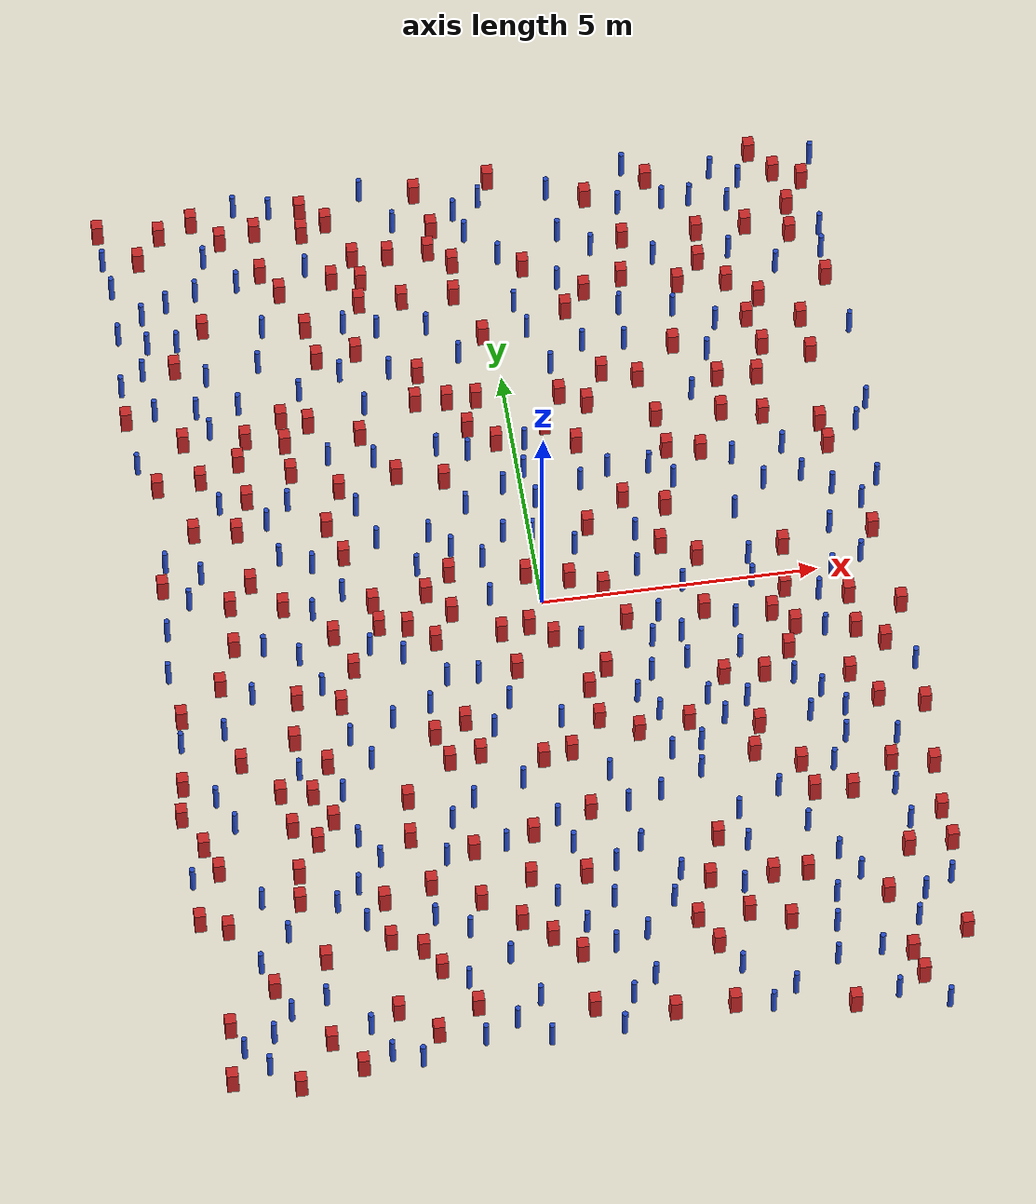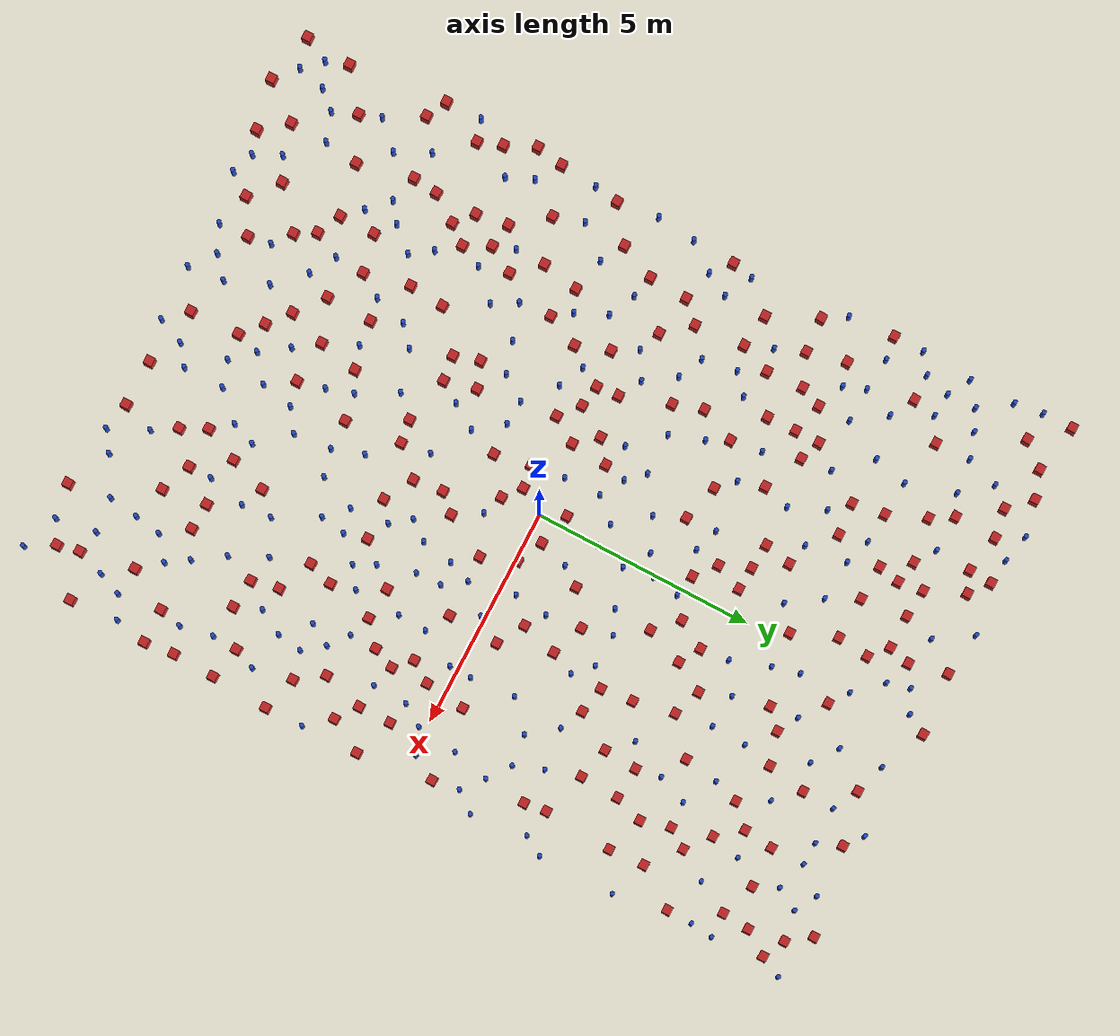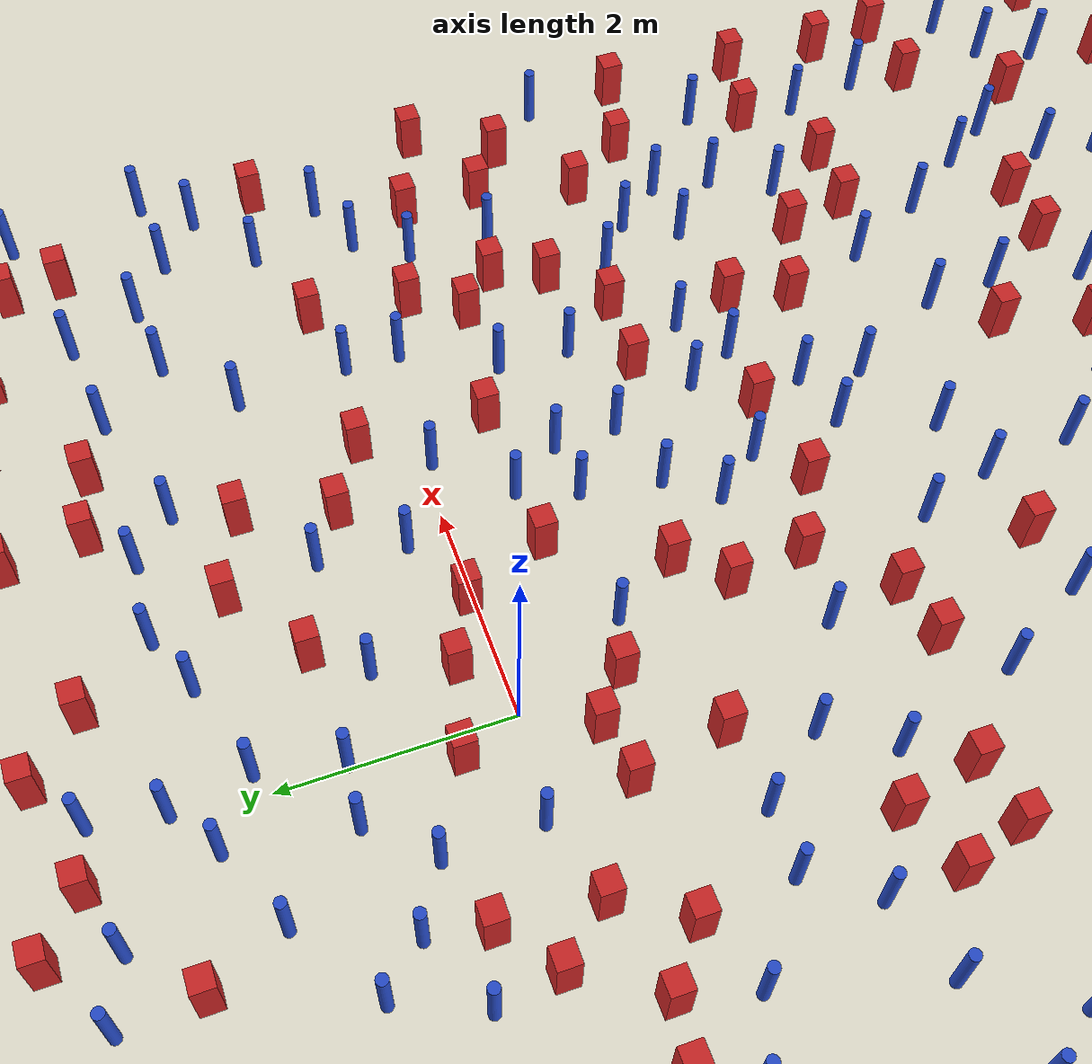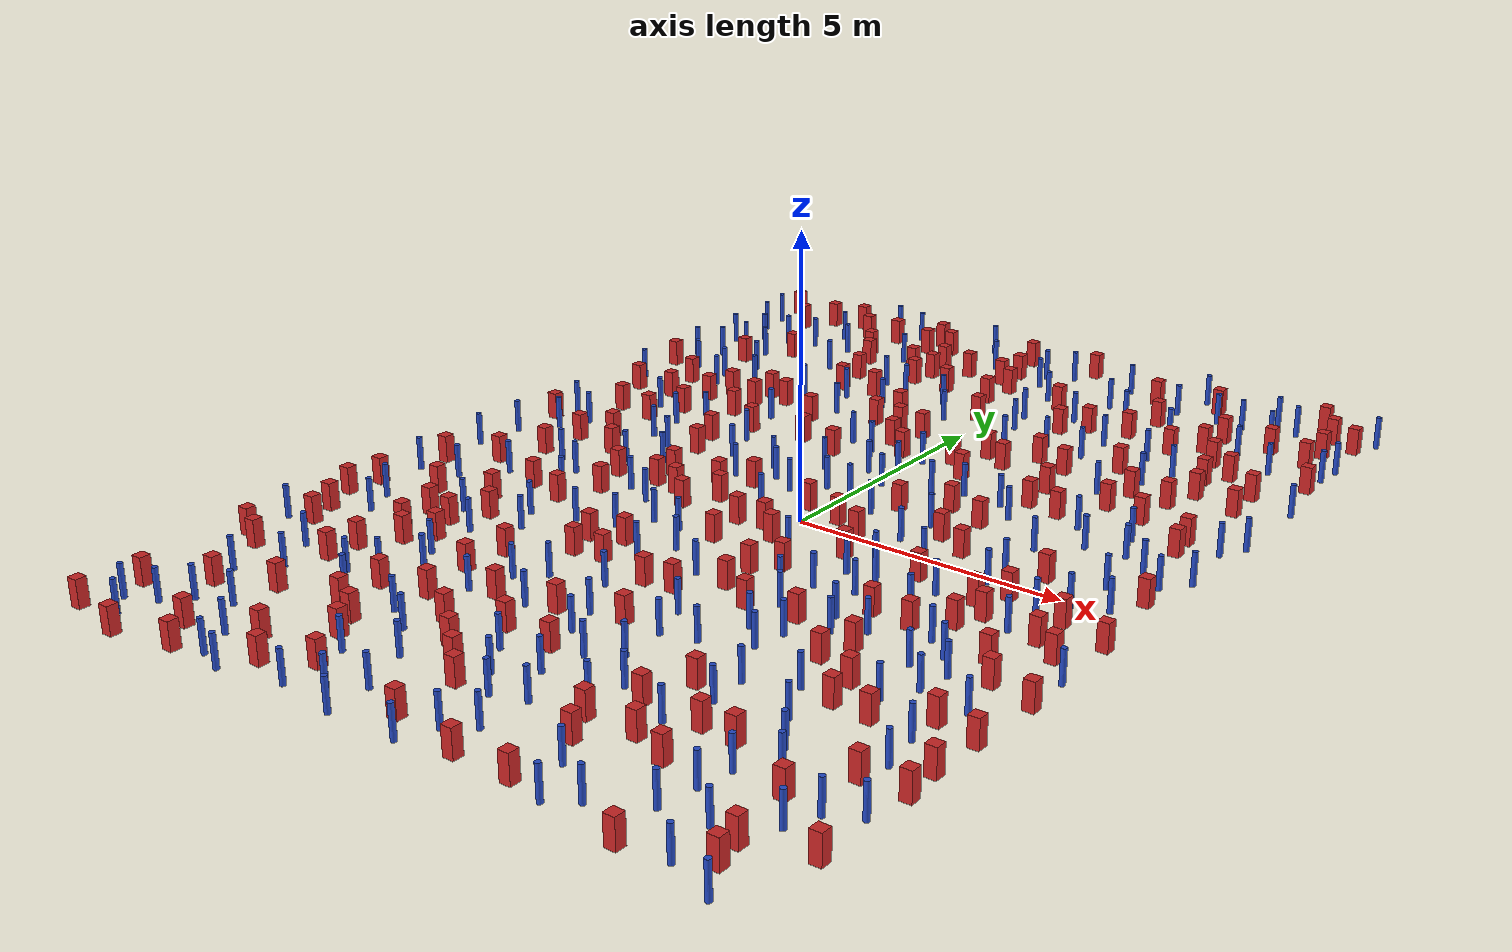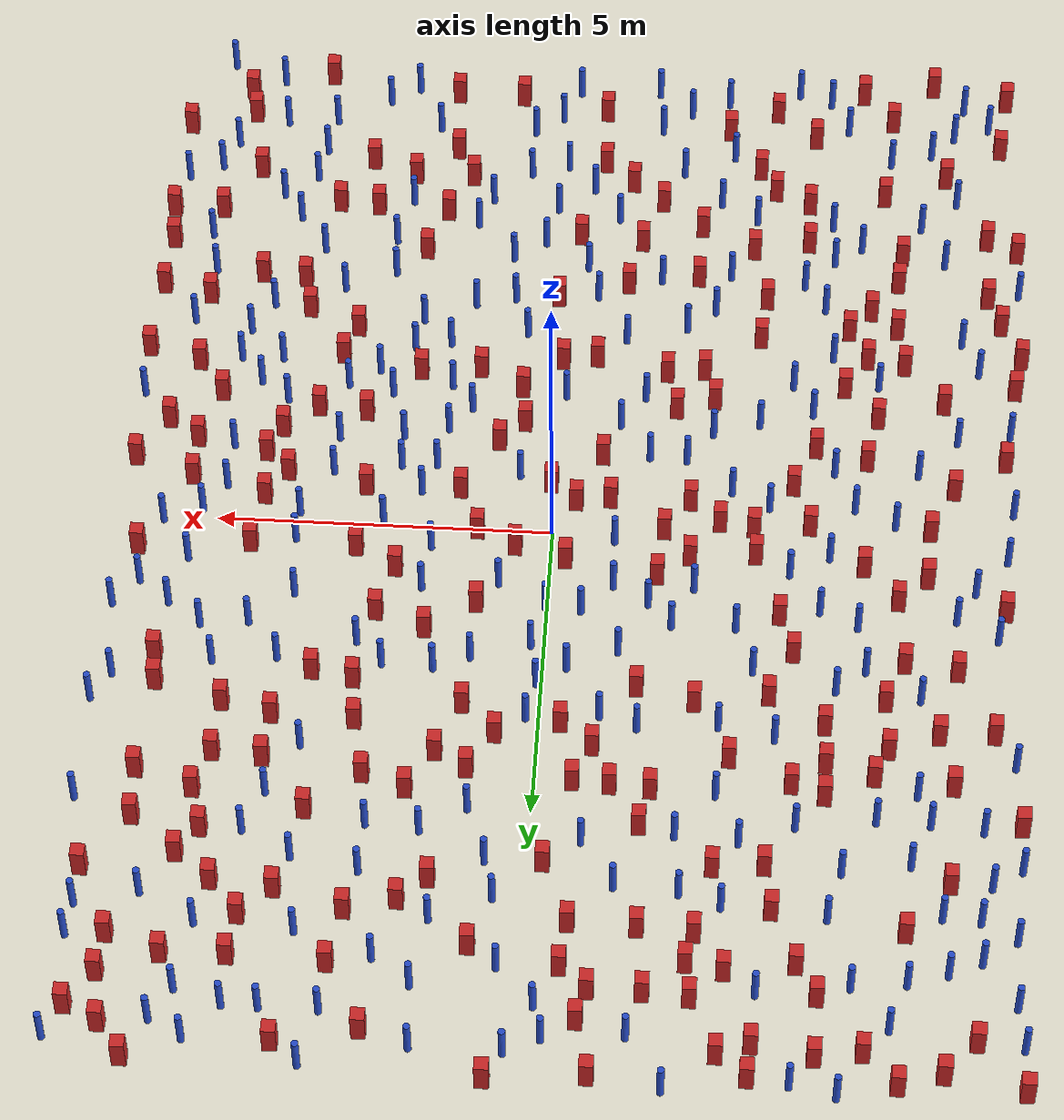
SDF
<sdf version="1.6">
  <model name="dense_28"><model name="square_post_obstacle0">
  <static>true</static>
  <pose frame="">-4.85381373403 -7.01380886418 8.22691968438e-08 7.22125133819e-06 -7.54495500217e-07 2.29674213826e-05</pose>
  <link name="link">
    <pose frame="">0 0 0.25 0 -0 0</pose>
    <inertial>
      <mass>100</mass>
      <inertia>
        <ixx>0.166667</ixx>
        <ixy>0</ixy>
        <ixz>0</ixz>
        <iyy>0.166667</iyy>
        <iyz>0</iyz>
        <izz>0.166667</izz>
      </inertia>
    </inertial>
    <collision name="collision">
      <geometry>
        <box>
          <size>.2 .2 .5</size>
        </box>
      </geometry>
      <max_contacts>10</max_contacts>
      <surface>
        <contact>
          <ode/>
        </contact>
        <bounce/>
        <friction>
          <torsional>
            <ode/>
          </torsional>
          <ode/>
        </friction>
      </surface>
    </collision>
    <visual name="visual">
      <geometry>
        <box>
          <size>.2 .2 .5</size>
        </box>
      </geometry>
      <material>
        <script>
          <name>Gazebo/Red</name>
          <uri>file://media/materials/scripts/gazebo.material</uri>
        </script>
      </material>
    </visual>
    <self_collide>0</self_collide>
    <kinematic>0</kinematic>
  </link>
</model>
<model name="square_post_obstacle1">
  <static>true</static>
  <pose frame="">-6.47186797774 -4.94214520173 8.22691968438e-08 7.22125133819e-06 -7.54495500217e-07 2.29674213826e-05</pose>
  <link name="link">
    <pose frame="">0 0 0.25 0 -0 0</pose>
    <inertial>
      <mass>100</mass>
      <inertia>
        <ixx>0.166667</ixx>
        <ixy>0</ixy>
        <ixz>0</ixz>
        <iyy>0.166667</iyy>
        <iyz>0</iyz>
        <izz>0.166667</izz>
      </inertia>
    </inertial>
    <collision name="collision">
      <geometry>
        <box>
          <size>.2 .2 .5</size>
        </box>
      </geometry>
      <max_contacts>10</max_contacts>
      <surface>
        <contact>
          <ode/>
        </contact>
        <bounce/>
        <friction>
          <torsional>
            <ode/>
          </torsional>
          <ode/>
        </friction>
      </surface>
    </collision>
    <visual name="visual">
      <geometry>
        <box>
          <size>.2 .2 .5</size>
        </box>
      </geometry>
      <material>
        <script>
          <name>Gazebo/Red</name>
          <uri>file://media/materials/scripts/gazebo.material</uri>
        </script>
      </material>
    </visual>
    <self_collide>0</self_collide>
    <kinematic>0</kinematic>
  </link>
</model>
<model name="pole_obstacle0">
  <static>true</static>
  <pose frame="">4.34795692381 -6.1171369326 2.88873142074e-08 -9.90536690842e-09 4.60219948965e-07 -1.20965994976e-07</pose>
  <link name="link">
  <pose frame="">0 0 0.3 0 -0 0</pose>
    <inertial>
      <mass>1</mass>
      <inertia>
        <ixx>0.145833</ixx>
        <ixy>0</ixy>
        <ixz>0</ixz>
        <iyy>0.145833</iyy>
        <iyz>0</iyz>
        <izz>0.125</izz>
      </inertia>
    </inertial>
    <collision name="collision">
      <geometry>
        <cylinder>
          <radius>0.05</radius>
          <length>.6</length>
        </cylinder>
      </geometry>
      <max_contacts>10</max_contacts>
      <surface>
        <contact>
          <ode/>
        </contact>
        <bounce/>
        <friction>
          <torsional>
            <ode/>
          </torsional>
          <ode/>
        </friction>
      </surface>
    </collision>
    <visual name="visual">
      <geometry>
        <cylinder>
          <radius>0.05</radius>
          <length>.6</length>
        </cylinder>
      </geometry>
      <material>
        <script>
          <name>Gazebo/Blue</name>
          <uri>file://media/materials/scripts/gazebo.material</uri>
        </script>
      </material>
    </visual>
    <self_collide>0</self_collide>
    <kinematic>0</kinematic>
  </link>
</model>
<model name="square_post_obstacle2">
  <static>true</static>
  <pose frame="">-5.19528177853 9.21006002513 8.22691968438e-08 7.22125133819e-06 -7.54495500217e-07 2.29674213826e-05</pose>
  <link name="link">
    <pose frame="">0 0 0.25 0 -0 0</pose>
    <inertial>
      <mass>100</mass>
      <inertia>
        <ixx>0.166667</ixx>
        <ixy>0</ixy>
        <ixz>0</ixz>
        <iyy>0.166667</iyy>
        <iyz>0</iyz>
        <izz>0.166667</izz>
      </inertia>
    </inertial>
    <collision name="collision">
      <geometry>
        <box>
          <size>.2 .2 .5</size>
        </box>
      </geometry>
      <max_contacts>10</max_contacts>
      <surface>
        <contact>
          <ode/>
        </contact>
        <bounce/>
        <friction>
          <torsional>
            <ode/>
          </torsional>
          <ode/>
        </friction>
      </surface>
    </collision>
    <visual name="visual">
      <geometry>
        <box>
          <size>.2 .2 .5</size>
        </box>
      </geometry>
      <material>
        <script>
          <name>Gazebo/Red</name>
          <uri>file://media/materials/scripts/gazebo.material</uri>
        </script>
      </material>
    </visual>
    <self_collide>0</self_collide>
    <kinematic>0</kinematic>
  </link>
</model>
<model name="pole_obstacle1">
  <static>true</static>
  <pose frame="">-4.48256232331 -0.682127414277 2.88873142074e-08 -9.90536689837e-09 4.60219948989e-07 -1.2096599496e-07</pose>
  <link name="link">
  <pose frame="">0 0 0.3 0 -0 0</pose>
    <inertial>
      <mass>1</mass>
      <inertia>
        <ixx>0.145833</ixx>
        <ixy>0</ixy>
        <ixz>0</ixz>
        <iyy>0.145833</iyy>
        <iyz>0</iyz>
        <izz>0.125</izz>
      </inertia>
    </inertial>
    <collision name="collision">
      <geometry>
        <cylinder>
          <radius>0.05</radius>
          <length>.6</length>
        </cylinder>
      </geometry>
      <max_contacts>10</max_contacts>
      <surface>
        <contact>
          <ode/>
        </contact>
        <bounce/>
        <friction>
          <torsional>
            <ode/>
          </torsional>
          <ode/>
        </friction>
      </surface>
    </collision>
    <visual name="visual">
      <geometry>
        <cylinder>
          <radius>0.05</radius>
          <length>.6</length>
        </cylinder>
      </geometry>
      <material>
        <script>
          <name>Gazebo/Blue</name>
          <uri>file://media/materials/scripts/gazebo.material</uri>
        </script>
      </material>
    </visual>
    <self_collide>0</self_collide>
    <kinematic>0</kinematic>
  </link>
</model>
<model name="square_post_obstacle3">
  <static>true</static>
  <pose frame="">-1.02345209858 9.29119812651 8.22691968438e-08 7.22125133819e-06 -7.54495500217e-07 2.29674213826e-05</pose>
  <link name="link">
    <pose frame="">0 0 0.25 0 -0 0</pose>
    <inertial>
      <mass>100</mass>
      <inertia>
        <ixx>0.166667</ixx>
        <ixy>0</ixy>
        <ixz>0</ixz>
        <iyy>0.166667</iyy>
        <iyz>0</iyz>
        <izz>0.166667</izz>
      </inertia>
    </inertial>
    <collision name="collision">
      <geometry>
        <box>
          <size>.2 .2 .5</size>
        </box>
      </geometry>
      <max_contacts>10</max_contacts>
      <surface>
        <contact>
          <ode/>
        </contact>
        <bounce/>
        <friction>
          <torsional>
            <ode/>
          </torsional>
          <ode/>
        </friction>
      </surface>
    </collision>
    <visual name="visual">
      <geometry>
        <box>
          <size>.2 .2 .5</size>
        </box>
      </geometry>
      <material>
        <script>
          <name>Gazebo/Red</name>
          <uri>file://media/materials/scripts/gazebo.material</uri>
        </script>
      </material>
    </visual>
    <self_collide>0</self_collide>
    <kinematic>0</kinematic>
  </link>
</model>
<model name="pole_obstacle2">
  <static>true</static>
  <pose frame="">0.933791437993 -5.44674622654 2.88873142074e-08 -9.90536689661e-09 4.60219948993e-07 -1.20965994957e-07</pose>
  <link name="link">
  <pose frame="">0 0 0.3 0 -0 0</pose>
    <inertial>
      <mass>1</mass>
      <inertia>
        <ixx>0.145833</ixx>
        <ixy>0</ixy>
        <ixz>0</ixz>
        <iyy>0.145833</iyy>
        <iyz>0</iyz>
        <izz>0.125</izz>
      </inertia>
    </inertial>
    <collision name="collision">
      <geometry>
        <cylinder>
          <radius>0.05</radius>
          <length>.6</length>
        </cylinder>
      </geometry>
      <max_contacts>10</max_contacts>
      <surface>
        <contact>
          <ode/>
        </contact>
        <bounce/>
        <friction>
          <torsional>
            <ode/>
          </torsional>
          <ode/>
        </friction>
      </surface>
    </collision>
    <visual name="visual">
      <geometry>
        <cylinder>
          <radius>0.05</radius>
          <length>.6</length>
        </cylinder>
      </geometry>
      <material>
        <script>
          <name>Gazebo/Blue</name>
          <uri>file://media/materials/scripts/gazebo.material</uri>
        </script>
      </material>
    </visual>
    <self_collide>0</self_collide>
    <kinematic>0</kinematic>
  </link>
</model>
<model name="pole_obstacle3">
  <static>true</static>
  <pose frame="">0.441866988841 6.503014817 2.88873142074e-08 -9.90536689683e-09 4.60219948993e-07 -1.20965994957e-07</pose>
  <link name="link">
  <pose frame="">0 0 0.3 0 -0 0</pose>
    <inertial>
      <mass>1</mass>
      <inertia>
        <ixx>0.145833</ixx>
        <ixy>0</ixy>
        <ixz>0</ixz>
        <iyy>0.145833</iyy>
        <iyz>0</iyz>
        <izz>0.125</izz>
      </inertia>
    </inertial>
    <collision name="collision">
      <geometry>
        <cylinder>
          <radius>0.05</radius>
          <length>.6</length>
        </cylinder>
      </geometry>
      <max_contacts>10</max_contacts>
      <surface>
        <contact>
          <ode/>
        </contact>
        <bounce/>
        <friction>
          <torsional>
            <ode/>
          </torsional>
          <ode/>
        </friction>
      </surface>
    </collision>
    <visual name="visual">
      <geometry>
        <cylinder>
          <radius>0.05</radius>
          <length>.6</length>
        </cylinder>
      </geometry>
      <material>
        <script>
          <name>Gazebo/Blue</name>
          <uri>file://media/materials/scripts/gazebo.material</uri>
        </script>
      </material>
    </visual>
    <self_collide>0</self_collide>
    <kinematic>0</kinematic>
  </link>
</model>
<model name="square_post_obstacle4">
  <static>true</static>
  <pose frame="">2.62261659096 3.62090149515 8.22691968438e-08 7.2212513382e-06 -7.54495500217e-07 2.29674213826e-05</pose>
  <link name="link">
    <pose frame="">0 0 0.25 0 -0 0</pose>
    <inertial>
      <mass>100</mass>
      <inertia>
        <ixx>0.166667</ixx>
        <ixy>0</ixy>
        <ixz>0</ixz>
        <iyy>0.166667</iyy>
        <iyz>0</iyz>
        <izz>0.166667</izz>
      </inertia>
    </inertial>
    <collision name="collision">
      <geometry>
        <box>
          <size>.2 .2 .5</size>
        </box>
      </geometry>
      <max_contacts>10</max_contacts>
      <surface>
        <contact>
          <ode/>
        </contact>
        <bounce/>
        <friction>
          <torsional>
            <ode/>
          </torsional>
          <ode/>
        </friction>
      </surface>
    </collision>
    <visual name="visual">
      <geometry>
        <box>
          <size>.2 .2 .5</size>
        </box>
      </geometry>
      <material>
        <script>
          <name>Gazebo/Red</name>
          <uri>file://media/materials/scripts/gazebo.material</uri>
        </script>
      </material>
    </visual>
    <self_collide>0</self_collide>
    <kinematic>0</kinematic>
  </link>
</model>
<model name="square_post_obstacle5">
  <static>true</static>
  <pose frame="">5.58213373667 -4.35693691751 8.22691968438e-08 7.2212513382e-06 -7.54495500217e-07 2.29674213826e-05</pose>
  <link name="link">
    <pose frame="">0 0 0.25 0 -0 0</pose>
    <inertial>
      <mass>100</mass>
      <inertia>
        <ixx>0.166667</ixx>
        <ixy>0</ixy>
        <ixz>0</ixz>
        <iyy>0.166667</iyy>
        <iyz>0</iyz>
        <izz>0.166667</izz>
      </inertia>
    </inertial>
    <collision name="collision">
      <geometry>
        <box>
          <size>.2 .2 .5</size>
        </box>
      </geometry>
      <max_contacts>10</max_contacts>
      <surface>
        <contact>
          <ode/>
        </contact>
        <bounce/>
        <friction>
          <torsional>
            <ode/>
          </torsional>
          <ode/>
        </friction>
      </surface>
    </collision>
    <visual name="visual">
      <geometry>
        <box>
          <size>.2 .2 .5</size>
        </box>
      </geometry>
      <material>
        <script>
          <name>Gazebo/Red</name>
          <uri>file://media/materials/scripts/gazebo.material</uri>
        </script>
      </material>
    </visual>
    <self_collide>0</self_collide>
    <kinematic>0</kinematic>
  </link>
</model>
<model name="square_post_obstacle6">
  <static>true</static>
  <pose frame="">-4.50291544065 -9.248557642 8.22691968438e-08 7.2212513382e-06 -7.54495500217e-07 2.29674213826e-05</pose>
  <link name="link">
    <pose frame="">0 0 0.25 0 -0 0</pose>
    <inertial>
      <mass>100</mass>
      <inertia>
        <ixx>0.166667</ixx>
        <ixy>0</ixy>
        <ixz>0</ixz>
        <iyy>0.166667</iyy>
        <iyz>0</iyz>
        <izz>0.166667</izz>
      </inertia>
    </inertial>
    <collision name="collision">
      <geometry>
        <box>
          <size>.2 .2 .5</size>
        </box>
      </geometry>
      <max_contacts>10</max_contacts>
      <surface>
        <contact>
          <ode/>
        </contact>
        <bounce/>
        <friction>
          <torsional>
            <ode/>
          </torsional>
          <ode/>
        </friction>
      </surface>
    </collision>
    <visual name="visual">
      <geometry>
        <box>
          <size>.2 .2 .5</size>
        </box>
      </geometry>
      <material>
        <script>
          <name>Gazebo/Red</name>
          <uri>file://media/materials/scripts/gazebo.material</uri>
        </script>
      </material>
    </visual>
    <self_collide>0</self_collide>
    <kinematic>0</kinematic>
  </link>
</model>
<model name="pole_obstacle4">
  <static>true</static>
  <pose frame="">-4.50905731509 -5.93586208997 2.88873142074e-08 -9.90536690842e-09 4.60219948965e-07 -1.20965994976e-07</pose>
  <link name="link">
  <pose frame="">0 0 0.3 0 -0 0</pose>
    <inertial>
      <mass>1</mass>
      <inertia>
        <ixx>0.145833</ixx>
        <ixy>0</ixy>
        <ixz>0</ixz>
        <iyy>0.145833</iyy>
        <iyz>0</iyz>
        <izz>0.125</izz>
      </inertia>
    </inertial>
    <collision name="collision">
      <geometry>
        <cylinder>
          <radius>0.05</radius>
          <length>.6</length>
        </cylinder>
      </geometry>
      <max_contacts>10</max_contacts>
      <surface>
        <contact>
          <ode/>
        </contact>
        <bounce/>
        <friction>
          <torsional>
            <ode/>
          </torsional>
          <ode/>
        </friction>
      </surface>
    </collision>
    <visual name="visual">
      <geometry>
        <cylinder>
          <radius>0.05</radius>
          <length>.6</length>
        </cylinder>
      </geometry>
      <material>
        <script>
          <name>Gazebo/Blue</name>
          <uri>file://media/materials/scripts/gazebo.material</uri>
        </script>
      </material>
    </visual>
    <self_collide>0</self_collide>
    <kinematic>0</kinematic>
  </link>
</model>
<model name="pole_obstacle5">
  <static>true</static>
  <pose frame="">-4.5406717764 7.67600084442 2.88873142074e-08 -9.90536690842e-09 4.60219948965e-07 -1.20965994976e-07</pose>
  <link name="link">
  <pose frame="">0 0 0.3 0 -0 0</pose>
    <inertial>
      <mass>1</mass>
      <inertia>
        <ixx>0.145833</ixx>
        <ixy>0</ixy>
        <ixz>0</ixz>
        <iyy>0.145833</iyy>
        <iyz>0</iyz>
        <izz>0.125</izz>
      </inertia>
    </inertial>
    <collision name="collision">
      <geometry>
        <cylinder>
          <radius>0.05</radius>
          <length>.6</length>
        </cylinder>
      </geometry>
      <max_contacts>10</max_contacts>
      <surface>
        <contact>
          <ode/>
        </contact>
        <bounce/>
        <friction>
          <torsional>
            <ode/>
          </torsional>
          <ode/>
        </friction>
      </surface>
    </collision>
    <visual name="visual">
      <geometry>
        <cylinder>
          <radius>0.05</radius>
          <length>.6</length>
        </cylinder>
      </geometry>
      <material>
        <script>
          <name>Gazebo/Blue</name>
          <uri>file://media/materials/scripts/gazebo.material</uri>
        </script>
      </material>
    </visual>
    <self_collide>0</self_collide>
    <kinematic>0</kinematic>
  </link>
</model>
<model name="square_post_obstacle7">
  <static>true</static>
  <pose frame="">-2.0578482682 0.386483031477 8.22691968438e-08 7.2212513382e-06 -7.54495500217e-07 2.29674213826e-05</pose>
  <link name="link">
    <pose frame="">0 0 0.25 0 -0 0</pose>
    <inertial>
      <mass>100</mass>
      <inertia>
        <ixx>0.166667</ixx>
        <ixy>0</ixy>
        <ixz>0</ixz>
        <iyy>0.166667</iyy>
        <iyz>0</iyz>
        <izz>0.166667</izz>
      </inertia>
    </inertial>
    <collision name="collision">
      <geometry>
        <box>
          <size>.2 .2 .5</size>
        </box>
      </geometry>
      <max_contacts>10</max_contacts>
      <surface>
        <contact>
          <ode/>
        </contact>
        <bounce/>
        <friction>
          <torsional>
            <ode/>
          </torsional>
          <ode/>
        </friction>
      </surface>
    </collision>
    <visual name="visual">
      <geometry>
        <box>
          <size>.2 .2 .5</size>
        </box>
      </geometry>
      <material>
        <script>
          <name>Gazebo/Red</name>
          <uri>file://media/materials/scripts/gazebo.material</uri>
        </script>
      </material>
    </visual>
    <self_collide>0</self_collide>
    <kinematic>0</kinematic>
  </link>
</model>
<model name="square_post_obstacle8">
  <static>true</static>
  <pose frame="">-4.6474370262 -1.57249042322 8.22691968438e-08 7.2212513382e-06 -7.54495500217e-07 2.29674213826e-05</pose>
  <link name="link">
    <pose frame="">0 0 0.25 0 -0 0</pose>
    <inertial>
      <mass>100</mass>
      <inertia>
        <ixx>0.166667</ixx>
        <ixy>0</ixy>
        <ixz>0</ixz>
        <iyy>0.166667</iyy>
        <iyz>0</iyz>
        <izz>0.166667</izz>
      </inertia>
    </inertial>
    <collision name="collision">
      <geometry>
        <box>
          <size>.2 .2 .5</size>
        </box>
      </geometry>
      <max_contacts>10</max_contacts>
      <surface>
        <contact>
          <ode/>
        </contact>
        <bounce/>
        <friction>
          <torsional>
            <ode/>
          </torsional>
          <ode/>
        </friction>
      </surface>
    </collision>
    <visual name="visual">
      <geometry>
        <box>
          <size>.2 .2 .5</size>
        </box>
      </geometry>
      <material>
        <script>
          <name>Gazebo/Red</name>
          <uri>file://media/materials/scripts/gazebo.material</uri>
        </script>
      </material>
    </visual>
    <self_collide>0</self_collide>
    <kinematic>0</kinematic>
  </link>
</model>
<model name="pole_obstacle6">
  <static>true</static>
  <pose frame="">-2.58148058758 3.40972883455 2.88873142074e-08 -9.90536690232e-09 4.6021994898e-07 -1.20965994968e-07</pose>
  <link name="link">
  <pose frame="">0 0 0.3 0 -0 0</pose>
    <inertial>
      <mass>1</mass>
      <inertia>
        <ixx>0.145833</ixx>
        <ixy>0</ixy>
        <ixz>0</ixz>
        <iyy>0.145833</iyy>
        <iyz>0</iyz>
        <izz>0.125</izz>
      </inertia>
    </inertial>
    <collision name="collision">
      <geometry>
        <cylinder>
          <radius>0.05</radius>
          <length>.6</length>
        </cylinder>
      </geometry>
      <max_contacts>10</max_contacts>
      <surface>
        <contact>
          <ode/>
        </contact>
        <bounce/>
        <friction>
          <torsional>
            <ode/>
          </torsional>
          <ode/>
        </friction>
      </surface>
    </collision>
    <visual name="visual">
      <geometry>
        <cylinder>
          <radius>0.05</radius>
          <length>.6</length>
        </cylinder>
      </geometry>
      <material>
        <script>
          <name>Gazebo/Blue</name>
          <uri>file://media/materials/scripts/gazebo.material</uri>
        </script>
      </material>
    </visual>
    <self_collide>0</self_collide>
    <kinematic>0</kinematic>
  </link>
</model>
<model name="pole_obstacle7">
  <static>true</static>
  <pose frame="">-3.816750742 -2.50595241744 2.88873142074e-08 -9.90536689597e-09 4.60219948995e-07 -1.20965994957e-07</pose>
  <link name="link">
  <pose frame="">0 0 0.3 0 -0 0</pose>
    <inertial>
      <mass>1</mass>
      <inertia>
        <ixx>0.145833</ixx>
        <ixy>0</ixy>
        <ixz>0</ixz>
        <iyy>0.145833</iyy>
        <iyz>0</iyz>
        <izz>0.125</izz>
      </inertia>
    </inertial>
    <collision name="collision">
      <geometry>
        <cylinder>
          <radius>0.05</radius>
          <length>.6</length>
        </cylinder>
      </geometry>
      <max_contacts>10</max_contacts>
      <surface>
        <contact>
          <ode/>
        </contact>
        <bounce/>
        <friction>
          <torsional>
            <ode/>
          </torsional>
          <ode/>
        </friction>
      </surface>
    </collision>
    <visual name="visual">
      <geometry>
        <cylinder>
          <radius>0.05</radius>
          <length>.6</length>
        </cylinder>
      </geometry>
      <material>
        <script>
          <name>Gazebo/Blue</name>
          <uri>file://media/materials/scripts/gazebo.material</uri>
        </script>
      </material>
    </visual>
    <self_collide>0</self_collide>
    <kinematic>0</kinematic>
  </link>
</model>
<model name="square_post_obstacle9">
  <static>true</static>
  <pose frame="">0.173088994099 -4.60743479318 8.22691968438e-08 7.2212513382e-06 -7.54495500217e-07 2.29674213826e-05</pose>
  <link name="link">
    <pose frame="">0 0 0.25 0 -0 0</pose>
    <inertial>
      <mass>100</mass>
      <inertia>
        <ixx>0.166667</ixx>
        <ixy>0</ixy>
        <ixz>0</ixz>
        <iyy>0.166667</iyy>
        <iyz>0</iyz>
        <izz>0.166667</izz>
      </inertia>
    </inertial>
    <collision name="collision">
      <geometry>
        <box>
          <size>.2 .2 .5</size>
        </box>
      </geometry>
      <max_contacts>10</max_contacts>
      <surface>
        <contact>
          <ode/>
        </contact>
        <bounce/>
        <friction>
          <torsional>
            <ode/>
          </torsional>
          <ode/>
        </friction>
      </surface>
    </collision>
    <visual name="visual">
      <geometry>
        <box>
          <size>.2 .2 .5</size>
        </box>
      </geometry>
      <material>
        <script>
          <name>Gazebo/Red</name>
          <uri>file://media/materials/scripts/gazebo.material</uri>
        </script>
      </material>
    </visual>
    <self_collide>0</self_collide>
    <kinematic>0</kinematic>
  </link>
</model>
<model name="square_post_obstacle10">
  <static>true</static>
  <pose frame="">5.58549876604 -6.17589599914 8.22691968438e-08 7.2212513382e-06 -7.54495500217e-07 2.29674213826e-05</pose>
  <link name="link">
    <pose frame="">0 0 0.25 0 -0 0</pose>
    <inertial>
      <mass>100</mass>
      <inertia>
        <ixx>0.166667</ixx>
        <ixy>0</ixy>
        <ixz>0</ixz>
        <iyy>0.166667</iyy>
        <iyz>0</iyz>
        <izz>0.166667</izz>
      </inertia>
    </inertial>
    <collision name="collision">
      <geometry>
        <box>
          <size>.2 .2 .5</size>
        </box>
      </geometry>
      <max_contacts>10</max_contacts>
      <surface>
        <contact>
          <ode/>
        </contact>
        <bounce/>
        <friction>
          <torsional>
            <ode/>
          </torsional>
          <ode/>
        </friction>
      </surface>
    </collision>
    <visual name="visual">
      <geometry>
        <box>
          <size>.2 .2 .5</size>
        </box>
      </geometry>
      <material>
        <script>
          <name>Gazebo/Red</name>
          <uri>file://media/materials/scripts/gazebo.material</uri>
        </script>
      </material>
    </visual>
    <self_collide>0</self_collide>
    <kinematic>0</kinematic>
  </link>
</model>
<model name="square_post_obstacle11">
  <static>true</static>
  <pose frame="">0.999707619295 -8.90997136029 8.22691968438e-08 7.2212513382e-06 -7.54495500217e-07 2.29674213826e-05</pose>
  <link name="link">
    <pose frame="">0 0 0.25 0 -0 0</pose>
    <inertial>
      <mass>100</mass>
      <inertia>
        <ixx>0.166667</ixx>
        <ixy>0</ixy>
        <ixz>0</ixz>
        <iyy>0.166667</iyy>
        <iyz>0</iyz>
        <izz>0.166667</izz>
      </inertia>
    </inertial>
    <collision name="collision">
      <geometry>
        <box>
          <size>.2 .2 .5</size>
        </box>
      </geometry>
      <max_contacts>10</max_contacts>
      <surface>
        <contact>
          <ode/>
        </contact>
        <bounce/>
        <friction>
          <torsional>
            <ode/>
          </torsional>
          <ode/>
        </friction>
      </surface>
    </collision>
    <visual name="visual">
      <geometry>
        <box>
          <size>.2 .2 .5</size>
        </box>
      </geometry>
      <material>
        <script>
          <name>Gazebo/Red</name>
          <uri>file://media/materials/scripts/gazebo.material</uri>
        </script>
      </material>
    </visual>
    <self_collide>0</self_collide>
    <kinematic>0</kinematic>
  </link>
</model>
<model name="square_post_obstacle12">
  <static>true</static>
  <pose frame="">2.48338838565 6.84339347547 8.22691968438e-08 7.2212513382e-06 -7.54495500217e-07 2.29674213826e-05</pose>
  <link name="link">
    <pose frame="">0 0 0.25 0 -0 0</pose>
    <inertial>
      <mass>100</mass>
      <inertia>
        <ixx>0.166667</ixx>
        <ixy>0</ixy>
        <ixz>0</ixz>
        <iyy>0.166667</iyy>
        <iyz>0</iyz>
        <izz>0.166667</izz>
      </inertia>
    </inertial>
    <collision name="collision">
      <geometry>
        <box>
          <size>.2 .2 .5</size>
        </box>
      </geometry>
      <max_contacts>10</max_contacts>
      <surface>
        <contact>
          <ode/>
        </contact>
        <bounce/>
        <friction>
          <torsional>
            <ode/>
          </torsional>
          <ode/>
        </friction>
      </surface>
    </collision>
    <visual name="visual">
      <geometry>
        <box>
          <size>.2 .2 .5</size>
        </box>
      </geometry>
      <material>
        <script>
          <name>Gazebo/Red</name>
          <uri>file://media/materials/scripts/gazebo.material</uri>
        </script>
      </material>
    </visual>
    <self_collide>0</self_collide>
    <kinematic>0</kinematic>
  </link>
</model>
<model name="square_post_obstacle13">
  <static>true</static>
  <pose frame="">1.10403048548 3.2495813458 8.22691968438e-08 7.2212513382e-06 -7.54495500217e-07 2.29674213826e-05</pose>
  <link name="link">
    <pose frame="">0 0 0.25 0 -0 0</pose>
    <inertial>
      <mass>100</mass>
      <inertia>
        <ixx>0.166667</ixx>
        <ixy>0</ixy>
        <ixz>0</ixz>
        <iyy>0.166667</iyy>
        <iyz>0</iyz>
        <izz>0.166667</izz>
      </inertia>
    </inertial>
    <collision name="collision">
      <geometry>
        <box>
          <size>.2 .2 .5</size>
        </box>
      </geometry>
      <max_contacts>10</max_contacts>
      <surface>
        <contact>
          <ode/>
        </contact>
        <bounce/>
        <friction>
          <torsional>
            <ode/>
          </torsional>
          <ode/>
        </friction>
      </surface>
    </collision>
    <visual name="visual">
      <geometry>
        <box>
          <size>.2 .2 .5</size>
        </box>
      </geometry>
      <material>
        <script>
          <name>Gazebo/Red</name>
          <uri>file://media/materials/scripts/gazebo.material</uri>
        </script>
      </material>
    </visual>
    <self_collide>0</self_collide>
    <kinematic>0</kinematic>
  </link>
</model>
<model name="pole_obstacle8">
  <static>true</static>
  <pose frame="">-6.38018953515 5.01108412161 2.88873142074e-08 -9.90536690842e-09 4.60219948965e-07 -1.20965994976e-07</pose>
  <link name="link">
  <pose frame="">0 0 0.3 0 -0 0</pose>
    <inertial>
      <mass>1</mass>
      <inertia>
        <ixx>0.145833</ixx>
        <ixy>0</ixy>
        <ixz>0</ixz>
        <iyy>0.145833</iyy>
        <iyz>0</iyz>
        <izz>0.125</izz>
      </inertia>
    </inertial>
    <collision name="collision">
      <geometry>
        <cylinder>
          <radius>0.05</radius>
          <length>.6</length>
        </cylinder>
      </geometry>
      <max_contacts>10</max_contacts>
      <surface>
        <contact>
          <ode/>
        </contact>
        <bounce/>
        <friction>
          <torsional>
            <ode/>
          </torsional>
          <ode/>
        </friction>
      </surface>
    </collision>
    <visual name="visual">
      <geometry>
        <cylinder>
          <radius>0.05</radius>
          <length>.6</length>
        </cylinder>
      </geometry>
      <material>
        <script>
          <name>Gazebo/Blue</name>
          <uri>file://media/materials/scripts/gazebo.material</uri>
        </script>
      </material>
    </visual>
    <self_collide>0</self_collide>
    <kinematic>0</kinematic>
  </link>
</model>
<model name="square_post_obstacle14">
  <static>true</static>
  <pose frame="">-2.37132577431 6.94454927565 8.22691968438e-08 7.2212513382e-06 -7.54495500217e-07 2.29674213826e-05</pose>
  <link name="link">
    <pose frame="">0 0 0.25 0 -0 0</pose>
    <inertial>
      <mass>100</mass>
      <inertia>
        <ixx>0.166667</ixx>
        <ixy>0</ixy>
        <ixz>0</ixz>
        <iyy>0.166667</iyy>
        <iyz>0</iyz>
        <izz>0.166667</izz>
      </inertia>
    </inertial>
    <collision name="collision">
      <geometry>
        <box>
          <size>.2 .2 .5</size>
        </box>
      </geometry>
      <max_contacts>10</max_contacts>
      <surface>
        <contact>
          <ode/>
        </contact>
        <bounce/>
        <friction>
          <torsional>
            <ode/>
          </torsional>
          <ode/>
        </friction>
      </surface>
    </collision>
    <visual name="visual">
      <geometry>
        <box>
          <size>.2 .2 .5</size>
        </box>
      </geometry>
      <material>
        <script>
          <name>Gazebo/Red</name>
          <uri>file://media/materials/scripts/gazebo.material</uri>
        </script>
      </material>
    </visual>
    <self_collide>0</self_collide>
    <kinematic>0</kinematic>
  </link>
</model>
<model name="square_post_obstacle15">
  <static>true</static>
  <pose frame="">1.35723531985 6.26059317896 8.22691968438e-08 7.2212513382e-06 -7.54495500217e-07 2.29674213826e-05</pose>
  <link name="link">
    <pose frame="">0 0 0.25 0 -0 0</pose>
    <inertial>
      <mass>100</mass>
      <inertia>
        <ixx>0.166667</ixx>
        <ixy>0</ixy>
        <ixz>0</ixz>
        <iyy>0.166667</iyy>
        <iyz>0</iyz>
        <izz>0.166667</izz>
      </inertia>
    </inertial>
    <collision name="collision">
      <geometry>
        <box>
          <size>.2 .2 .5</size>
        </box>
      </geometry>
      <max_contacts>10</max_contacts>
      <surface>
        <contact>
          <ode/>
        </contact>
        <bounce/>
        <friction>
          <torsional>
            <ode/>
          </torsional>
          <ode/>
        </friction>
      </surface>
    </collision>
    <visual name="visual">
      <geometry>
        <box>
          <size>.2 .2 .5</size>
        </box>
      </geometry>
      <material>
        <script>
          <name>Gazebo/Red</name>
          <uri>file://media/materials/scripts/gazebo.material</uri>
        </script>
      </material>
    </visual>
    <self_collide>0</self_collide>
    <kinematic>0</kinematic>
  </link>
</model>
<model name="square_post_obstacle16">
  <static>true</static>
  <pose frame="">-6.93241014558 9.20835231173 8.22691968438e-08 7.22125133819e-06 -7.54495500217e-07 2.29674213826e-05</pose>
  <link name="link">
    <pose frame="">0 0 0.25 0 -0 0</pose>
    <inertial>
      <mass>100</mass>
      <inertia>
        <ixx>0.166667</ixx>
        <ixy>0</ixy>
        <ixz>0</ixz>
        <iyy>0.166667</iyy>
        <iyz>0</iyz>
        <izz>0.166667</izz>
      </inertia>
    </inertial>
    <collision name="collision">
      <geometry>
        <box>
          <size>.2 .2 .5</size>
        </box>
      </geometry>
      <max_contacts>10</max_contacts>
      <surface>
        <contact>
          <ode/>
        </contact>
        <bounce/>
        <friction>
          <torsional>
            <ode/>
          </torsional>
          <ode/>
        </friction>
      </surface>
    </collision>
    <visual name="visual">
      <geometry>
        <box>
          <size>.2 .2 .5</size>
        </box>
      </geometry>
      <material>
        <script>
          <name>Gazebo/Red</name>
          <uri>file://media/materials/scripts/gazebo.material</uri>
        </script>
      </material>
    </visual>
    <self_collide>0</self_collide>
    <kinematic>0</kinematic>
  </link>
</model>
<model name="pole_obstacle9">
  <static>true</static>
  <pose frame="">-3.72507891736 5.07874219042 2.88873142074e-08 -9.90536689859e-09 4.60219948989e-07 -1.20965994961e-07</pose>
  <link name="link">
  <pose frame="">0 0 0.3 0 -0 0</pose>
    <inertial>
      <mass>1</mass>
      <inertia>
        <ixx>0.145833</ixx>
        <ixy>0</ixy>
        <ixz>0</ixz>
        <iyy>0.145833</iyy>
        <iyz>0</iyz>
        <izz>0.125</izz>
      </inertia>
    </inertial>
    <collision name="collision">
      <geometry>
        <cylinder>
          <radius>0.05</radius>
          <length>.6</length>
        </cylinder>
      </geometry>
      <max_contacts>10</max_contacts>
      <surface>
        <contact>
          <ode/>
        </contact>
        <bounce/>
        <friction>
          <torsional>
            <ode/>
          </torsional>
          <ode/>
        </friction>
      </surface>
    </collision>
    <visual name="visual">
      <geometry>
        <cylinder>
          <radius>0.05</radius>
          <length>.6</length>
        </cylinder>
      </geometry>
      <material>
        <script>
          <name>Gazebo/Blue</name>
          <uri>file://media/materials/scripts/gazebo.material</uri>
        </script>
      </material>
    </visual>
    <self_collide>0</self_collide>
    <kinematic>0</kinematic>
  </link>
</model>
<model name="square_post_obstacle17">
  <static>true</static>
  <pose frame="">-2.82780362628 -5.76743023222 8.22691968438e-08 7.2212513382e-06 -7.54495500217e-07 2.29674213826e-05</pose>
  <link name="link">
    <pose frame="">0 0 0.25 0 -0 0</pose>
    <inertial>
      <mass>100</mass>
      <inertia>
        <ixx>0.166667</ixx>
        <ixy>0</ixy>
        <ixz>0</ixz>
        <iyy>0.166667</iyy>
        <iyz>0</iyz>
        <izz>0.166667</izz>
      </inertia>
    </inertial>
    <collision name="collision">
      <geometry>
        <box>
          <size>.2 .2 .5</size>
        </box>
      </geometry>
      <max_contacts>10</max_contacts>
      <surface>
        <contact>
          <ode/>
        </contact>
        <bounce/>
        <friction>
          <torsional>
            <ode/>
          </torsional>
          <ode/>
        </friction>
      </surface>
    </collision>
    <visual name="visual">
      <geometry>
        <box>
          <size>.2 .2 .5</size>
        </box>
      </geometry>
      <material>
        <script>
          <name>Gazebo/Red</name>
          <uri>file://media/materials/scripts/gazebo.material</uri>
        </script>
      </material>
    </visual>
    <self_collide>0</self_collide>
    <kinematic>0</kinematic>
  </link>
</model>
<model name="square_post_obstacle18">
  <static>true</static>
  <pose frame="">2.70620414548 2.89905259573 8.22691968438e-08 7.2212513382e-06 -7.54495500217e-07 2.29674213826e-05</pose>
  <link name="link">
    <pose frame="">0 0 0.25 0 -0 0</pose>
    <inertial>
      <mass>100</mass>
      <inertia>
        <ixx>0.166667</ixx>
        <ixy>0</ixy>
        <ixz>0</ixz>
        <iyy>0.166667</iyy>
        <iyz>0</iyz>
        <izz>0.166667</izz>
      </inertia>
    </inertial>
    <collision name="collision">
      <geometry>
        <box>
          <size>.2 .2 .5</size>
        </box>
      </geometry>
      <max_contacts>10</max_contacts>
      <surface>
        <contact>
          <ode/>
        </contact>
        <bounce/>
        <friction>
          <torsional>
            <ode/>
          </torsional>
          <ode/>
        </friction>
      </surface>
    </collision>
    <visual name="visual">
      <geometry>
        <box>
          <size>.2 .2 .5</size>
        </box>
      </geometry>
      <material>
        <script>
          <name>Gazebo/Red</name>
          <uri>file://media/materials/scripts/gazebo.material</uri>
        </script>
      </material>
    </visual>
    <self_collide>0</self_collide>
    <kinematic>0</kinematic>
  </link>
</model>
<model name="pole_obstacle10">
  <static>true</static>
  <pose frame="">-3.39466578167 3.58236068421 2.88873142074e-08 -9.90536690232e-09 4.6021994898e-07 -1.20965994968e-07</pose>
  <link name="link">
  <pose frame="">0 0 0.3 0 -0 0</pose>
    <inertial>
      <mass>1</mass>
      <inertia>
        <ixx>0.145833</ixx>
        <ixy>0</ixy>
        <ixz>0</ixz>
        <iyy>0.145833</iyy>
        <iyz>0</iyz>
        <izz>0.125</izz>
      </inertia>
    </inertial>
    <collision name="collision">
      <geometry>
        <cylinder>
          <radius>0.05</radius>
          <length>.6</length>
        </cylinder>
      </geometry>
      <max_contacts>10</max_contacts>
      <surface>
        <contact>
          <ode/>
        </contact>
        <bounce/>
        <friction>
          <torsional>
            <ode/>
          </torsional>
          <ode/>
        </friction>
      </surface>
    </collision>
    <visual name="visual">
      <geometry>
        <cylinder>
          <radius>0.05</radius>
          <length>.6</length>
        </cylinder>
      </geometry>
      <material>
        <script>
          <name>Gazebo/Blue</name>
          <uri>file://media/materials/scripts/gazebo.material</uri>
        </script>
      </material>
    </visual>
    <self_collide>0</self_collide>
    <kinematic>0</kinematic>
  </link>
</model>
<model name="square_post_obstacle19">
  <static>true</static>
  <pose frame="">-3.30935946386 5.7919567537 8.22691968438e-08 7.2212513382e-06 -7.54495500217e-07 2.29674213826e-05</pose>
  <link name="link">
    <pose frame="">0 0 0.25 0 -0 0</pose>
    <inertial>
      <mass>100</mass>
      <inertia>
        <ixx>0.166667</ixx>
        <ixy>0</ixy>
        <ixz>0</ixz>
        <iyy>0.166667</iyy>
        <iyz>0</iyz>
        <izz>0.166667</izz>
      </inertia>
    </inertial>
    <collision name="collision">
      <geometry>
        <box>
          <size>.2 .2 .5</size>
        </box>
      </geometry>
      <max_contacts>10</max_contacts>
      <surface>
        <contact>
          <ode/>
        </contact>
        <bounce/>
        <friction>
          <torsional>
            <ode/>
          </torsional>
          <ode/>
        </friction>
      </surface>
    </collision>
    <visual name="visual">
      <geometry>
        <box>
          <size>.2 .2 .5</size>
        </box>
      </geometry>
      <material>
        <script>
          <name>Gazebo/Red</name>
          <uri>file://media/materials/scripts/gazebo.material</uri>
        </script>
      </material>
    </visual>
    <self_collide>0</self_collide>
    <kinematic>0</kinematic>
  </link>
</model>
<model name="pole_obstacle11">
  <static>true</static>
  <pose frame="">-3.24421056813 7.85350295179 2.88873142074e-08 -9.90536689859e-09 4.60219948989e-07 -1.20965994961e-07</pose>
  <link name="link">
  <pose frame="">0 0 0.3 0 -0 0</pose>
    <inertial>
      <mass>1</mass>
      <inertia>
        <ixx>0.145833</ixx>
        <ixy>0</ixy>
        <ixz>0</ixz>
        <iyy>0.145833</iyy>
        <iyz>0</iyz>
        <izz>0.125</izz>
      </inertia>
    </inertial>
    <collision name="collision">
      <geometry>
        <cylinder>
          <radius>0.05</radius>
          <length>.6</length>
        </cylinder>
      </geometry>
      <max_contacts>10</max_contacts>
      <surface>
        <contact>
          <ode/>
        </contact>
        <bounce/>
        <friction>
          <torsional>
            <ode/>
          </torsional>
          <ode/>
        </friction>
      </surface>
    </collision>
    <visual name="visual">
      <geometry>
        <cylinder>
          <radius>0.05</radius>
          <length>.6</length>
        </cylinder>
      </geometry>
      <material>
        <script>
          <name>Gazebo/Blue</name>
          <uri>file://media/materials/scripts/gazebo.material</uri>
        </script>
      </material>
    </visual>
    <self_collide>0</self_collide>
    <kinematic>0</kinematic>
  </link>
</model>
<model name="square_post_obstacle20">
  <static>true</static>
  <pose frame="">0.602518353487 3.74456204148 8.22691968438e-08 7.2212513382e-06 -7.54495500217e-07 2.29674213826e-05</pose>
  <link name="link">
    <pose frame="">0 0 0.25 0 -0 0</pose>
    <inertial>
      <mass>100</mass>
      <inertia>
        <ixx>0.166667</ixx>
        <ixy>0</ixy>
        <ixz>0</ixz>
        <iyy>0.166667</iyy>
        <iyz>0</iyz>
        <izz>0.166667</izz>
      </inertia>
    </inertial>
    <collision name="collision">
      <geometry>
        <box>
          <size>.2 .2 .5</size>
        </box>
      </geometry>
      <max_contacts>10</max_contacts>
      <surface>
        <contact>
          <ode/>
        </contact>
        <bounce/>
        <friction>
          <torsional>
            <ode/>
          </torsional>
          <ode/>
        </friction>
      </surface>
    </collision>
    <visual name="visual">
      <geometry>
        <box>
          <size>.2 .2 .5</size>
        </box>
      </geometry>
      <material>
        <script>
          <name>Gazebo/Red</name>
          <uri>file://media/materials/scripts/gazebo.material</uri>
        </script>
      </material>
    </visual>
    <self_collide>0</self_collide>
    <kinematic>0</kinematic>
  </link>
</model>
<model name="pole_obstacle12">
  <static>true</static>
  <pose frame="">-0.875067047452 3.3181722902 2.88873142074e-08 -9.90536689636e-09 4.60219948994e-07 -1.20965994958e-07</pose>
  <link name="link">
  <pose frame="">0 0 0.3 0 -0 0</pose>
    <inertial>
      <mass>1</mass>
      <inertia>
        <ixx>0.145833</ixx>
        <ixy>0</ixy>
        <ixz>0</ixz>
        <iyy>0.145833</iyy>
        <iyz>0</iyz>
        <izz>0.125</izz>
      </inertia>
    </inertial>
    <collision name="collision">
      <geometry>
        <cylinder>
          <radius>0.05</radius>
          <length>.6</length>
        </cylinder>
      </geometry>
      <max_contacts>10</max_contacts>
      <surface>
        <contact>
          <ode/>
        </contact>
        <bounce/>
        <friction>
          <torsional>
            <ode/>
          </torsional>
          <ode/>
        </friction>
      </surface>
    </collision>
    <visual name="visual">
      <geometry>
        <cylinder>
          <radius>0.05</radius>
          <length>.6</length>
        </cylinder>
      </geometry>
      <material>
        <script>
          <name>Gazebo/Blue</name>
          <uri>file://media/materials/scripts/gazebo.material</uri>
        </script>
      </material>
    </visual>
    <self_collide>0</self_collide>
    <kinematic>0</kinematic>
  </link>
</model>
<model name="square_post_obstacle21">
  <static>true</static>
  <pose frame="">2.87978851423 0.481293469229 8.22691968438e-08 7.2212513382e-06 -7.54495500217e-07 2.29674213826e-05</pose>
  <link name="link">
    <pose frame="">0 0 0.25 0 -0 0</pose>
    <inertial>
      <mass>100</mass>
      <inertia>
        <ixx>0.166667</ixx>
        <ixy>0</ixy>
        <ixz>0</ixz>
        <iyy>0.166667</iyy>
        <iyz>0</iyz>
        <izz>0.166667</izz>
      </inertia>
    </inertial>
    <collision name="collision">
      <geometry>
        <box>
          <size>.2 .2 .5</size>
        </box>
      </geometry>
      <max_contacts>10</max_contacts>
      <surface>
        <contact>
          <ode/>
        </contact>
        <bounce/>
        <friction>
          <torsional>
            <ode/>
          </torsional>
          <ode/>
        </friction>
      </surface>
    </collision>
    <visual name="visual">
      <geometry>
        <box>
          <size>.2 .2 .5</size>
        </box>
      </geometry>
      <material>
        <script>
          <name>Gazebo/Red</name>
          <uri>file://media/materials/scripts/gazebo.material</uri>
        </script>
      </material>
    </visual>
    <self_collide>0</self_collide>
    <kinematic>0</kinematic>
  </link>
</model>
<model name="pole_obstacle13">
  <static>true</static>
  <pose frame="">3.34858475064 -0.98336733475 2.88873142074e-08 -9.90536689217e-09 4.60219949004e-07 -1.20965994953e-07</pose>
  <link name="link">
  <pose frame="">0 0 0.3 0 -0 0</pose>
    <inertial>
      <mass>1</mass>
      <inertia>
        <ixx>0.145833</ixx>
        <ixy>0</ixy>
        <ixz>0</ixz>
        <iyy>0.145833</iyy>
        <iyz>0</iyz>
        <izz>0.125</izz>
      </inertia>
    </inertial>
    <collision name="collision">
      <geometry>
        <cylinder>
          <radius>0.05</radius>
          <length>.6</length>
        </cylinder>
      </geometry>
      <max_contacts>10</max_contacts>
      <surface>
        <contact>
          <ode/>
        </contact>
        <bounce/>
        <friction>
          <torsional>
            <ode/>
          </torsional>
          <ode/>
        </friction>
      </surface>
    </collision>
    <visual name="visual">
      <geometry>
        <cylinder>
          <radius>0.05</radius>
          <length>.6</length>
        </cylinder>
      </geometry>
      <material>
        <script>
          <name>Gazebo/Blue</name>
          <uri>file://media/materials/scripts/gazebo.material</uri>
        </script>
      </material>
    </visual>
    <self_collide>0</self_collide>
    <kinematic>0</kinematic>
  </link>
</model>
<model name="square_post_obstacle22">
  <static>true</static>
  <pose frame="">0.536728351592 -2.05278987813 8.22691968438e-08 7.2212513382e-06 -7.54495500217e-07 2.29674213826e-05</pose>
  <link name="link">
    <pose frame="">0 0 0.25 0 -0 0</pose>
    <inertial>
      <mass>100</mass>
      <inertia>
        <ixx>0.166667</ixx>
        <ixy>0</ixy>
        <ixz>0</ixz>
        <iyy>0.166667</iyy>
        <iyz>0</iyz>
        <izz>0.166667</izz>
      </inertia>
    </inertial>
    <collision name="collision">
      <geometry>
        <box>
          <size>.2 .2 .5</size>
        </box>
      </geometry>
      <max_contacts>10</max_contacts>
      <surface>
        <contact>
          <ode/>
        </contact>
        <bounce/>
        <friction>
          <torsional>
            <ode/>
          </torsional>
          <ode/>
        </friction>
      </surface>
    </collision>
    <visual name="visual">
      <geometry>
        <box>
          <size>.2 .2 .5</size>
        </box>
      </geometry>
      <material>
        <script>
          <name>Gazebo/Red</name>
          <uri>file://media/materials/scripts/gazebo.material</uri>
        </script>
      </material>
    </visual>
    <self_collide>0</self_collide>
    <kinematic>0</kinematic>
  </link>
</model>
<model name="pole_obstacle14">
  <static>true</static>
  <pose frame="">-1.40718546428 -5.10483130645 2.88873142074e-08 -9.90536689852e-09 4.60219948989e-07 -1.2096599496e-07</pose>
  <link name="link">
  <pose frame="">0 0 0.3 0 -0 0</pose>
    <inertial>
      <mass>1</mass>
      <inertia>
        <ixx>0.145833</ixx>
        <ixy>0</ixy>
        <ixz>0</ixz>
        <iyy>0.145833</iyy>
        <iyz>0</iyz>
        <izz>0.125</izz>
      </inertia>
    </inertial>
    <collision name="collision">
      <geometry>
        <cylinder>
          <radius>0.05</radius>
          <length>.6</length>
        </cylinder>
      </geometry>
      <max_contacts>10</max_contacts>
      <surface>
        <contact>
          <ode/>
        </contact>
        <bounce/>
        <friction>
          <torsional>
            <ode/>
          </torsional>
          <ode/>
        </friction>
      </surface>
    </collision>
    <visual name="visual">
      <geometry>
        <cylinder>
          <radius>0.05</radius>
          <length>.6</length>
        </cylinder>
      </geometry>
      <material>
        <script>
          <name>Gazebo/Blue</name>
          <uri>file://media/materials/scripts/gazebo.material</uri>
        </script>
      </material>
    </visual>
    <self_collide>0</self_collide>
    <kinematic>0</kinematic>
  </link>
</model>
<model name="pole_obstacle15">
  <static>true</static>
  <pose frame="">0.735092478149 0.998841244981 2.88873142074e-08 -9.90536690204e-09 4.6021994898e-07 -1.20965994967e-07</pose>
  <link name="link">
  <pose frame="">0 0 0.3 0 -0 0</pose>
    <inertial>
      <mass>1</mass>
      <inertia>
        <ixx>0.145833</ixx>
        <ixy>0</ixy>
        <ixz>0</ixz>
        <iyy>0.145833</iyy>
        <iyz>0</iyz>
        <izz>0.125</izz>
      </inertia>
    </inertial>
    <collision name="collision">
      <geometry>
        <cylinder>
          <radius>0.05</radius>
          <length>.6</length>
        </cylinder>
      </geometry>
      <max_contacts>10</max_contacts>
      <surface>
        <contact>
          <ode/>
        </contact>
        <bounce/>
        <friction>
          <torsional>
            <ode/>
          </torsional>
          <ode/>
        </friction>
      </surface>
    </collision>
    <visual name="visual">
      <geometry>
        <cylinder>
          <radius>0.05</radius>
          <length>.6</length>
        </cylinder>
      </geometry>
      <material>
        <script>
          <name>Gazebo/Blue</name>
          <uri>file://media/materials/scripts/gazebo.material</uri>
        </script>
      </material>
    </visual>
    <self_collide>0</self_collide>
    <kinematic>0</kinematic>
  </link>
</model>
<model name="pole_obstacle16">
  <static>true</static>
  <pose frame="">5.79698424891 0.0809831116426 2.88873142074e-08 -9.90536689727e-09 4.60219948992e-07 -1.20965994958e-07</pose>
  <link name="link">
  <pose frame="">0 0 0.3 0 -0 0</pose>
    <inertial>
      <mass>1</mass>
      <inertia>
        <ixx>0.145833</ixx>
        <ixy>0</ixy>
        <ixz>0</ixz>
        <iyy>0.145833</iyy>
        <iyz>0</iyz>
        <izz>0.125</izz>
      </inertia>
    </inertial>
    <collision name="collision">
      <geometry>
        <cylinder>
          <radius>0.05</radius>
          <length>.6</length>
        </cylinder>
      </geometry>
      <max_contacts>10</max_contacts>
      <surface>
        <contact>
          <ode/>
        </contact>
        <bounce/>
        <friction>
          <torsional>
            <ode/>
          </torsional>
          <ode/>
        </friction>
      </surface>
    </collision>
    <visual name="visual">
      <geometry>
        <cylinder>
          <radius>0.05</radius>
          <length>.6</length>
        </cylinder>
      </geometry>
      <material>
        <script>
          <name>Gazebo/Blue</name>
          <uri>file://media/materials/scripts/gazebo.material</uri>
        </script>
      </material>
    </visual>
    <self_collide>0</self_collide>
    <kinematic>0</kinematic>
  </link>
</model>
<model name="square_post_obstacle23">
  <static>true</static>
  <pose frame="">1.75817973603 6.63917724675 8.22691968438e-08 7.2212513382e-06 -7.54495500217e-07 2.29674213826e-05</pose>
  <link name="link">
    <pose frame="">0 0 0.25 0 -0 0</pose>
    <inertial>
      <mass>100</mass>
      <inertia>
        <ixx>0.166667</ixx>
        <ixy>0</ixy>
        <ixz>0</ixz>
        <iyy>0.166667</iyy>
        <iyz>0</iyz>
        <izz>0.166667</izz>
      </inertia>
    </inertial>
    <collision name="collision">
      <geometry>
        <box>
          <size>.2 .2 .5</size>
        </box>
      </geometry>
      <max_contacts>10</max_contacts>
      <surface>
        <contact>
          <ode/>
        </contact>
        <bounce/>
        <friction>
          <torsional>
            <ode/>
          </torsional>
          <ode/>
        </friction>
      </surface>
    </collision>
    <visual name="visual">
      <geometry>
        <box>
          <size>.2 .2 .5</size>
        </box>
      </geometry>
      <material>
        <script>
          <name>Gazebo/Red</name>
          <uri>file://media/materials/scripts/gazebo.material</uri>
        </script>
      </material>
    </visual>
    <self_collide>0</self_collide>
    <kinematic>0</kinematic>
  </link>
</model>
<model name="pole_obstacle17">
  <static>true</static>
  <pose frame="">-0.0558707264338 -2.66336785733 2.88873142074e-08 -9.90536692535e-09 4.60219948925e-07 -1.2096599499e-07</pose>
  <link name="link">
  <pose frame="">0 0 0.3 0 -0 0</pose>
    <inertial>
      <mass>1</mass>
      <inertia>
        <ixx>0.145833</ixx>
        <ixy>0</ixy>
        <ixz>0</ixz>
        <iyy>0.145833</iyy>
        <iyz>0</iyz>
        <izz>0.125</izz>
      </inertia>
    </inertial>
    <collision name="collision">
      <geometry>
        <cylinder>
          <radius>0.05</radius>
          <length>.6</length>
        </cylinder>
      </geometry>
      <max_contacts>10</max_contacts>
      <surface>
        <contact>
          <ode/>
        </contact>
        <bounce/>
        <friction>
          <torsional>
            <ode/>
          </torsional>
          <ode/>
        </friction>
      </surface>
    </collision>
    <visual name="visual">
      <geometry>
        <cylinder>
          <radius>0.05</radius>
          <length>.6</length>
        </cylinder>
      </geometry>
      <material>
        <script>
          <name>Gazebo/Blue</name>
          <uri>file://media/materials/scripts/gazebo.material</uri>
        </script>
      </material>
    </visual>
    <self_collide>0</self_collide>
    <kinematic>0</kinematic>
  </link>
</model>
<model name="square_post_obstacle24">
  <static>true</static>
  <pose frame="">-2.3696107004 -8.32431781453 8.22691968438e-08 7.22125133819e-06 -7.54495500217e-07 2.29674213826e-05</pose>
  <link name="link">
    <pose frame="">0 0 0.25 0 -0 0</pose>
    <inertial>
      <mass>100</mass>
      <inertia>
        <ixx>0.166667</ixx>
        <ixy>0</ixy>
        <ixz>0</ixz>
        <iyy>0.166667</iyy>
        <iyz>0</iyz>
        <izz>0.166667</izz>
      </inertia>
    </inertial>
    <collision name="collision">
      <geometry>
        <box>
          <size>.2 .2 .5</size>
        </box>
      </geometry>
      <max_contacts>10</max_contacts>
      <surface>
        <contact>
          <ode/>
        </contact>
        <bounce/>
        <friction>
          <torsional>
            <ode/>
          </torsional>
          <ode/>
        </friction>
      </surface>
    </collision>
    <visual name="visual">
      <geometry>
        <box>
          <size>.2 .2 .5</size>
        </box>
      </geometry>
      <material>
        <script>
          <name>Gazebo/Red</name>
          <uri>file://media/materials/scripts/gazebo.material</uri>
        </script>
      </material>
    </visual>
    <self_collide>0</self_collide>
    <kinematic>0</kinematic>
  </link>
</model>
<model name="square_post_obstacle25">
  <static>true</static>
  <pose frame="">2.04702596472 -8.91406215674 8.22691968438e-08 7.22125133819e-06 -7.54495500217e-07 2.29674213826e-05</pose>
  <link name="link">
    <pose frame="">0 0 0.25 0 -0 0</pose>
    <inertial>
      <mass>100</mass>
      <inertia>
        <ixx>0.166667</ixx>
        <ixy>0</ixy>
        <ixz>0</ixz>
        <iyy>0.166667</iyy>
        <iyz>0</iyz>
        <izz>0.166667</izz>
      </inertia>
    </inertial>
    <collision name="collision">
      <geometry>
        <box>
          <size>.2 .2 .5</size>
        </box>
      </geometry>
      <max_contacts>10</max_contacts>
      <surface>
        <contact>
          <ode/>
        </contact>
        <bounce/>
        <friction>
          <torsional>
            <ode/>
          </torsional>
          <ode/>
        </friction>
      </surface>
    </collision>
    <visual name="visual">
      <geometry>
        <box>
          <size>.2 .2 .5</size>
        </box>
      </geometry>
      <material>
        <script>
          <name>Gazebo/Red</name>
          <uri>file://media/materials/scripts/gazebo.material</uri>
        </script>
      </material>
    </visual>
    <self_collide>0</self_collide>
    <kinematic>0</kinematic>
  </link>
</model>
<model name="square_post_obstacle26">
  <static>true</static>
  <pose frame="">-6.68108062466 -8.1485355378 8.22691968438e-08 7.2212513382e-06 -7.54495500217e-07 2.29674213826e-05</pose>
  <link name="link">
    <pose frame="">0 0 0.25 0 -0 0</pose>
    <inertial>
      <mass>100</mass>
      <inertia>
        <ixx>0.166667</ixx>
        <ixy>0</ixy>
        <ixz>0</ixz>
        <iyy>0.166667</iyy>
        <iyz>0</iyz>
        <izz>0.166667</izz>
      </inertia>
    </inertial>
    <collision name="collision">
      <geometry>
        <box>
          <size>.2 .2 .5</size>
        </box>
      </geometry>
      <max_contacts>10</max_contacts>
      <surface>
        <contact>
          <ode/>
        </contact>
        <bounce/>
        <friction>
          <torsional>
            <ode/>
          </torsional>
          <ode/>
        </friction>
      </surface>
    </collision>
    <visual name="visual">
      <geometry>
        <box>
          <size>.2 .2 .5</size>
        </box>
      </geometry>
      <material>
        <script>
          <name>Gazebo/Red</name>
          <uri>file://media/materials/scripts/gazebo.material</uri>
        </script>
      </material>
    </visual>
    <self_collide>0</self_collide>
    <kinematic>0</kinematic>
  </link>
</model>
<model name="square_post_obstacle27">
  <static>true</static>
  <pose frame="">-5.90386193936 5.9466558869 8.22691968438e-08 7.2212513382e-06 -7.54495500217e-07 2.29674213826e-05</pose>
  <link name="link">
    <pose frame="">0 0 0.25 0 -0 0</pose>
    <inertial>
      <mass>100</mass>
      <inertia>
        <ixx>0.166667</ixx>
        <ixy>0</ixy>
        <ixz>0</ixz>
        <iyy>0.166667</iyy>
        <iyz>0</iyz>
        <izz>0.166667</izz>
      </inertia>
    </inertial>
    <collision name="collision">
      <geometry>
        <box>
          <size>.2 .2 .5</size>
        </box>
      </geometry>
      <max_contacts>10</max_contacts>
      <surface>
        <contact>
          <ode/>
        </contact>
        <bounce/>
        <friction>
          <torsional>
            <ode/>
          </torsional>
          <ode/>
        </friction>
      </surface>
    </collision>
    <visual name="visual">
      <geometry>
        <box>
          <size>.2 .2 .5</size>
        </box>
      </geometry>
      <material>
        <script>
          <name>Gazebo/Red</name>
          <uri>file://media/materials/scripts/gazebo.material</uri>
        </script>
      </material>
    </visual>
    <self_collide>0</self_collide>
    <kinematic>0</kinematic>
  </link>
</model>
<model name="pole_obstacle18">
  <static>true</static>
  <pose frame="">5.77748012901 -3.87090259575 2.88873142074e-08 -9.90536690245e-09 4.6021994898e-07 -1.20965994966e-07</pose>
  <link name="link">
  <pose frame="">0 0 0.3 0 -0 0</pose>
    <inertial>
      <mass>1</mass>
      <inertia>
        <ixx>0.145833</ixx>
        <ixy>0</ixy>
        <ixz>0</ixz>
        <iyy>0.145833</iyy>
        <iyz>0</iyz>
        <izz>0.125</izz>
      </inertia>
    </inertial>
    <collision name="collision">
      <geometry>
        <cylinder>
          <radius>0.05</radius>
          <length>.6</length>
        </cylinder>
      </geometry>
      <max_contacts>10</max_contacts>
      <surface>
        <contact>
          <ode/>
        </contact>
        <bounce/>
        <friction>
          <torsional>
            <ode/>
          </torsional>
          <ode/>
        </friction>
      </surface>
    </collision>
    <visual name="visual">
      <geometry>
        <cylinder>
          <radius>0.05</radius>
          <length>.6</length>
        </cylinder>
      </geometry>
      <material>
        <script>
          <name>Gazebo/Blue</name>
          <uri>file://media/materials/scripts/gazebo.material</uri>
        </script>
      </material>
    </visual>
    <self_collide>0</self_collide>
    <kinematic>0</kinematic>
  </link>
</model>
<model name="square_post_obstacle28">
  <static>true</static>
  <pose frame="">2.18755131449 -2.99619584192 8.22691968438e-08 7.2212513382e-06 -7.54495500217e-07 2.29674213826e-05</pose>
  <link name="link">
    <pose frame="">0 0 0.25 0 -0 0</pose>
    <inertial>
      <mass>100</mass>
      <inertia>
        <ixx>0.166667</ixx>
        <ixy>0</ixy>
        <ixz>0</ixz>
        <iyy>0.166667</iyy>
        <iyz>0</iyz>
        <izz>0.166667</izz>
      </inertia>
    </inertial>
    <collision name="collision">
      <geometry>
        <box>
          <size>.2 .2 .5</size>
        </box>
      </geometry>
      <max_contacts>10</max_contacts>
      <surface>
        <contact>
          <ode/>
        </contact>
        <bounce/>
        <friction>
          <torsional>
            <ode/>
          </torsional>
          <ode/>
        </friction>
      </surface>
    </collision>
    <visual name="visual">
      <geometry>
        <box>
          <size>.2 .2 .5</size>
        </box>
      </geometry>
      <material>
        <script>
          <name>Gazebo/Red</name>
          <uri>file://media/materials/scripts/gazebo.material</uri>
        </script>
      </material>
    </visual>
    <self_collide>0</self_collide>
    <kinematic>0</kinematic>
  </link>
</model>
<model name="pole_obstacle19">
  <static>true</static>
  <pose frame="">-5.6300147762 4.94023833615 2.88873142074e-08 -9.90536690842e-09 4.60219948965e-07 -1.20965994976e-07</pose>
  <link name="link">
  <pose frame="">0 0 0.3 0 -0 0</pose>
    <inertial>
      <mass>1</mass>
      <inertia>
        <ixx>0.145833</ixx>
        <ixy>0</ixy>
        <ixz>0</ixz>
        <iyy>0.145833</iyy>
        <iyz>0</iyz>
        <izz>0.125</izz>
      </inertia>
    </inertial>
    <collision name="collision">
      <geometry>
        <cylinder>
          <radius>0.05</radius>
          <length>.6</length>
        </cylinder>
      </geometry>
      <max_contacts>10</max_contacts>
      <surface>
        <contact>
          <ode/>
        </contact>
        <bounce/>
        <friction>
          <torsional>
            <ode/>
          </torsional>
          <ode/>
        </friction>
      </surface>
    </collision>
    <visual name="visual">
      <geometry>
        <cylinder>
          <radius>0.05</radius>
          <length>.6</length>
        </cylinder>
      </geometry>
      <material>
        <script>
          <name>Gazebo/Blue</name>
          <uri>file://media/materials/scripts/gazebo.material</uri>
        </script>
      </material>
    </visual>
    <self_collide>0</self_collide>
    <kinematic>0</kinematic>
  </link>
</model>
<model name="square_post_obstacle29">
  <static>true</static>
  <pose frame="">3.93869183844 7.00800149829 8.22691968438e-08 7.2212513382e-06 -7.54495500217e-07 2.29674213826e-05</pose>
  <link name="link">
    <pose frame="">0 0 0.25 0 -0 0</pose>
    <inertial>
      <mass>100</mass>
      <inertia>
        <ixx>0.166667</ixx>
        <ixy>0</ixy>
        <ixz>0</ixz>
        <iyy>0.166667</iyy>
        <iyz>0</iyz>
        <izz>0.166667</izz>
      </inertia>
    </inertial>
    <collision name="collision">
      <geometry>
        <box>
          <size>.2 .2 .5</size>
        </box>
      </geometry>
      <max_contacts>10</max_contacts>
      <surface>
        <contact>
          <ode/>
        </contact>
        <bounce/>
        <friction>
          <torsional>
            <ode/>
          </torsional>
          <ode/>
        </friction>
      </surface>
    </collision>
    <visual name="visual">
      <geometry>
        <box>
          <size>.2 .2 .5</size>
        </box>
      </geometry>
      <material>
        <script>
          <name>Gazebo/Red</name>
          <uri>file://media/materials/scripts/gazebo.material</uri>
        </script>
      </material>
    </visual>
    <self_collide>0</self_collide>
    <kinematic>0</kinematic>
  </link>
</model>
<model name="square_post_obstacle30">
  <static>true</static>
  <pose frame="">-4.8008438077 -2.41623321414 8.22691968438e-08 7.2212513382e-06 -7.54495500217e-07 2.29674213826e-05</pose>
  <link name="link">
    <pose frame="">0 0 0.25 0 -0 0</pose>
    <inertial>
      <mass>100</mass>
      <inertia>
        <ixx>0.166667</ixx>
        <ixy>0</ixy>
        <ixz>0</ixz>
        <iyy>0.166667</iyy>
        <iyz>0</iyz>
        <izz>0.166667</izz>
      </inertia>
    </inertial>
    <collision name="collision">
      <geometry>
        <box>
          <size>.2 .2 .5</size>
        </box>
      </geometry>
      <max_contacts>10</max_contacts>
      <surface>
        <contact>
          <ode/>
        </contact>
        <bounce/>
        <friction>
          <torsional>
            <ode/>
          </torsional>
          <ode/>
        </friction>
      </surface>
    </collision>
    <visual name="visual">
      <geometry>
        <box>
          <size>.2 .2 .5</size>
        </box>
      </geometry>
      <material>
        <script>
          <name>Gazebo/Red</name>
          <uri>file://media/materials/scripts/gazebo.material</uri>
        </script>
      </material>
    </visual>
    <self_collide>0</self_collide>
    <kinematic>0</kinematic>
  </link>
</model>
<model name="pole_obstacle20">
  <static>true</static>
  <pose frame="">-0.929298429132 0.112789689783 2.88873142074e-08 -9.90536689442e-09 4.60219948999e-07 -1.20965994955e-07</pose>
  <link name="link">
  <pose frame="">0 0 0.3 0 -0 0</pose>
    <inertial>
      <mass>1</mass>
      <inertia>
        <ixx>0.145833</ixx>
        <ixy>0</ixy>
        <ixz>0</ixz>
        <iyy>0.145833</iyy>
        <iyz>0</iyz>
        <izz>0.125</izz>
      </inertia>
    </inertial>
    <collision name="collision">
      <geometry>
        <cylinder>
          <radius>0.05</radius>
          <length>.6</length>
        </cylinder>
      </geometry>
      <max_contacts>10</max_contacts>
      <surface>
        <contact>
          <ode/>
        </contact>
        <bounce/>
        <friction>
          <torsional>
            <ode/>
          </torsional>
          <ode/>
        </friction>
      </surface>
    </collision>
    <visual name="visual">
      <geometry>
        <cylinder>
          <radius>0.05</radius>
          <length>.6</length>
        </cylinder>
      </geometry>
      <material>
        <script>
          <name>Gazebo/Blue</name>
          <uri>file://media/materials/scripts/gazebo.material</uri>
        </script>
      </material>
    </visual>
    <self_collide>0</self_collide>
    <kinematic>0</kinematic>
  </link>
</model>
<model name="pole_obstacle21">
  <static>true</static>
  <pose frame="">-0.732135297291 5.49770974981 2.88873142074e-08 -9.90536689661e-09 4.60219948993e-07 -1.20965994957e-07</pose>
  <link name="link">
  <pose frame="">0 0 0.3 0 -0 0</pose>
    <inertial>
      <mass>1</mass>
      <inertia>
        <ixx>0.145833</ixx>
        <ixy>0</ixy>
        <ixz>0</ixz>
        <iyy>0.145833</iyy>
        <iyz>0</iyz>
        <izz>0.125</izz>
      </inertia>
    </inertial>
    <collision name="collision">
      <geometry>
        <cylinder>
          <radius>0.05</radius>
          <length>.6</length>
        </cylinder>
      </geometry>
      <max_contacts>10</max_contacts>
      <surface>
        <contact>
          <ode/>
        </contact>
        <bounce/>
        <friction>
          <torsional>
            <ode/>
          </torsional>
          <ode/>
        </friction>
      </surface>
    </collision>
    <visual name="visual">
      <geometry>
        <cylinder>
          <radius>0.05</radius>
          <length>.6</length>
        </cylinder>
      </geometry>
      <material>
        <script>
          <name>Gazebo/Blue</name>
          <uri>file://media/materials/scripts/gazebo.material</uri>
        </script>
      </material>
    </visual>
    <self_collide>0</self_collide>
    <kinematic>0</kinematic>
  </link>
</model>
<model name="square_post_obstacle31">
  <static>true</static>
  <pose frame="">2.43105017646 4.54562582871 8.22691968438e-08 7.2212513382e-06 -7.54495500217e-07 2.29674213826e-05</pose>
  <link name="link">
    <pose frame="">0 0 0.25 0 -0 0</pose>
    <inertial>
      <mass>100</mass>
      <inertia>
        <ixx>0.166667</ixx>
        <ixy>0</ixy>
        <ixz>0</ixz>
        <iyy>0.166667</iyy>
        <iyz>0</iyz>
        <izz>0.166667</izz>
      </inertia>
    </inertial>
    <collision name="collision">
      <geometry>
        <box>
          <size>.2 .2 .5</size>
        </box>
      </geometry>
      <max_contacts>10</max_contacts>
      <surface>
        <contact>
          <ode/>
        </contact>
        <bounce/>
        <friction>
          <torsional>
            <ode/>
          </torsional>
          <ode/>
        </friction>
      </surface>
    </collision>
    <visual name="visual">
      <geometry>
        <box>
          <size>.2 .2 .5</size>
        </box>
      </geometry>
      <material>
        <script>
          <name>Gazebo/Red</name>
          <uri>file://media/materials/scripts/gazebo.material</uri>
        </script>
      </material>
    </visual>
    <self_collide>0</self_collide>
    <kinematic>0</kinematic>
  </link>
</model>
<model name="pole_obstacle22">
  <static>true</static>
  <pose frame="">-0.501604950757 1.44115727738 2.88873142074e-08 -9.90536689621e-09 4.60219948994e-07 -1.20965994957e-07</pose>
  <link name="link">
  <pose frame="">0 0 0.3 0 -0 0</pose>
    <inertial>
      <mass>1</mass>
      <inertia>
        <ixx>0.145833</ixx>
        <ixy>0</ixy>
        <ixz>0</ixz>
        <iyy>0.145833</iyy>
        <iyz>0</iyz>
        <izz>0.125</izz>
      </inertia>
    </inertial>
    <collision name="collision">
      <geometry>
        <cylinder>
          <radius>0.05</radius>
          <length>.6</length>
        </cylinder>
      </geometry>
      <max_contacts>10</max_contacts>
      <surface>
        <contact>
          <ode/>
        </contact>
        <bounce/>
        <friction>
          <torsional>
            <ode/>
          </torsional>
          <ode/>
        </friction>
      </surface>
    </collision>
    <visual name="visual">
      <geometry>
        <cylinder>
          <radius>0.05</radius>
          <length>.6</length>
        </cylinder>
      </geometry>
      <material>
        <script>
          <name>Gazebo/Blue</name>
          <uri>file://media/materials/scripts/gazebo.material</uri>
        </script>
      </material>
    </visual>
    <self_collide>0</self_collide>
    <kinematic>0</kinematic>
  </link>
</model>
<model name="pole_obstacle23">
  <static>true</static>
  <pose frame="">-1.22024010586 6.22082861621 2.88873142074e-08 -9.90536689852e-09 4.60219948989e-07 -1.2096599496e-07</pose>
  <link name="link">
  <pose frame="">0 0 0.3 0 -0 0</pose>
    <inertial>
      <mass>1</mass>
      <inertia>
        <ixx>0.145833</ixx>
        <ixy>0</ixy>
        <ixz>0</ixz>
        <iyy>0.145833</iyy>
        <iyz>0</iyz>
        <izz>0.125</izz>
      </inertia>
    </inertial>
    <collision name="collision">
      <geometry>
        <cylinder>
          <radius>0.05</radius>
          <length>.6</length>
        </cylinder>
      </geometry>
      <max_contacts>10</max_contacts>
      <surface>
        <contact>
          <ode/>
        </contact>
        <bounce/>
        <friction>
          <torsional>
            <ode/>
          </torsional>
          <ode/>
        </friction>
      </surface>
    </collision>
    <visual name="visual">
      <geometry>
        <cylinder>
          <radius>0.05</radius>
          <length>.6</length>
        </cylinder>
      </geometry>
      <material>
        <script>
          <name>Gazebo/Blue</name>
          <uri>file://media/materials/scripts/gazebo.material</uri>
        </script>
      </material>
    </visual>
    <self_collide>0</self_collide>
    <kinematic>0</kinematic>
  </link>
</model>
<model name="pole_obstacle24">
  <static>true</static>
  <pose frame="">4.90524724189 -9.08340190689 2.88873142074e-08 -9.9053668967e-09 4.60219948993e-07 -1.20965994957e-07</pose>
  <link name="link">
  <pose frame="">0 0 0.3 0 -0 0</pose>
    <inertial>
      <mass>1</mass>
      <inertia>
        <ixx>0.145833</ixx>
        <ixy>0</ixy>
        <ixz>0</ixz>
        <iyy>0.145833</iyy>
        <iyz>0</iyz>
        <izz>0.125</izz>
      </inertia>
    </inertial>
    <collision name="collision">
      <geometry>
        <cylinder>
          <radius>0.05</radius>
          <length>.6</length>
        </cylinder>
      </geometry>
      <max_contacts>10</max_contacts>
      <surface>
        <contact>
          <ode/>
        </contact>
        <bounce/>
        <friction>
          <torsional>
            <ode/>
          </torsional>
          <ode/>
        </friction>
      </surface>
    </collision>
    <visual name="visual">
      <geometry>
        <cylinder>
          <radius>0.05</radius>
          <length>.6</length>
        </cylinder>
      </geometry>
      <material>
        <script>
          <name>Gazebo/Blue</name>
          <uri>file://media/materials/scripts/gazebo.material</uri>
        </script>
      </material>
    </visual>
    <self_collide>0</self_collide>
    <kinematic>0</kinematic>
  </link>
</model>
<model name="pole_obstacle25">
  <static>true</static>
  <pose frame="">-5.80819248637 -5.67410705577 2.88873142074e-08 -9.90536690842e-09 4.60219948965e-07 -1.20965994976e-07</pose>
  <link name="link">
  <pose frame="">0 0 0.3 0 -0 0</pose>
    <inertial>
      <mass>1</mass>
      <inertia>
        <ixx>0.145833</ixx>
        <ixy>0</ixy>
        <ixz>0</ixz>
        <iyy>0.145833</iyy>
        <iyz>0</iyz>
        <izz>0.125</izz>
      </inertia>
    </inertial>
    <collision name="collision">
      <geometry>
        <cylinder>
          <radius>0.05</radius>
          <length>.6</length>
        </cylinder>
      </geometry>
      <max_contacts>10</max_contacts>
      <surface>
        <contact>
          <ode/>
        </contact>
        <bounce/>
        <friction>
          <torsional>
            <ode/>
          </torsional>
          <ode/>
        </friction>
      </surface>
    </collision>
    <visual name="visual">
      <geometry>
        <cylinder>
          <radius>0.05</radius>
          <length>.6</length>
        </cylinder>
      </geometry>
      <material>
        <script>
          <name>Gazebo/Blue</name>
          <uri>file://media/materials/scripts/gazebo.material</uri>
        </script>
      </material>
    </visual>
    <self_collide>0</self_collide>
    <kinematic>0</kinematic>
  </link>
</model>
<model name="pole_obstacle26">
  <static>true</static>
  <pose frame="">-3.96511217509 -4.63562692174 2.88873142074e-08 -9.90536690054e-09 4.60219948984e-07 -1.20965994964e-07</pose>
  <link name="link">
  <pose frame="">0 0 0.3 0 -0 0</pose>
    <inertial>
      <mass>1</mass>
      <inertia>
        <ixx>0.145833</ixx>
        <ixy>0</ixy>
        <ixz>0</ixz>
        <iyy>0.145833</iyy>
        <iyz>0</iyz>
        <izz>0.125</izz>
      </inertia>
    </inertial>
    <collision name="collision">
      <geometry>
        <cylinder>
          <radius>0.05</radius>
          <length>.6</length>
        </cylinder>
      </geometry>
      <max_contacts>10</max_contacts>
      <surface>
        <contact>
          <ode/>
        </contact>
        <bounce/>
        <friction>
          <torsional>
            <ode/>
          </torsional>
          <ode/>
        </friction>
      </surface>
    </collision>
    <visual name="visual">
      <geometry>
        <cylinder>
          <radius>0.05</radius>
          <length>.6</length>
        </cylinder>
      </geometry>
      <material>
        <script>
          <name>Gazebo/Blue</name>
          <uri>file://media/materials/scripts/gazebo.material</uri>
        </script>
      </material>
    </visual>
    <self_collide>0</self_collide>
    <kinematic>0</kinematic>
  </link>
</model>
<model name="pole_obstacle27">
  <static>true</static>
  <pose frame="">1.57937318762 2.5967450185 2.88873142074e-08 -9.90536689791e-09 4.6021994899e-07 -1.20965994959e-07</pose>
  <link name="link">
  <pose frame="">0 0 0.3 0 -0 0</pose>
    <inertial>
      <mass>1</mass>
      <inertia>
        <ixx>0.145833</ixx>
        <ixy>0</ixy>
        <ixz>0</ixz>
        <iyy>0.145833</iyy>
        <iyz>0</iyz>
        <izz>0.125</izz>
      </inertia>
    </inertial>
    <collision name="collision">
      <geometry>
        <cylinder>
          <radius>0.05</radius>
          <length>.6</length>
        </cylinder>
      </geometry>
      <max_contacts>10</max_contacts>
      <surface>
        <contact>
          <ode/>
        </contact>
        <bounce/>
        <friction>
          <torsional>
            <ode/>
          </torsional>
          <ode/>
        </friction>
      </surface>
    </collision>
    <visual name="visual">
      <geometry>
        <cylinder>
          <radius>0.05</radius>
          <length>.6</length>
        </cylinder>
      </geometry>
      <material>
        <script>
          <name>Gazebo/Blue</name>
          <uri>file://media/materials/scripts/gazebo.material</uri>
        </script>
      </material>
    </visual>
    <self_collide>0</self_collide>
    <kinematic>0</kinematic>
  </link>
</model>
<model name="square_post_obstacle32">
  <static>true</static>
  <pose frame="">-3.12139781006 -8.76833713452 8.22691968438e-08 7.22125133819e-06 -7.54495500217e-07 2.29674213826e-05</pose>
  <link name="link">
    <pose frame="">0 0 0.25 0 -0 0</pose>
    <inertial>
      <mass>100</mass>
      <inertia>
        <ixx>0.166667</ixx>
        <ixy>0</ixy>
        <ixz>0</ixz>
        <iyy>0.166667</iyy>
        <iyz>0</iyz>
        <izz>0.166667</izz>
      </inertia>
    </inertial>
    <collision name="collision">
      <geometry>
        <box>
          <size>.2 .2 .5</size>
        </box>
      </geometry>
      <max_contacts>10</max_contacts>
      <surface>
        <contact>
          <ode/>
        </contact>
        <bounce/>
        <friction>
          <torsional>
            <ode/>
          </torsional>
          <ode/>
        </friction>
      </surface>
    </collision>
    <visual name="visual">
      <geometry>
        <box>
          <size>.2 .2 .5</size>
        </box>
      </geometry>
      <material>
        <script>
          <name>Gazebo/Red</name>
          <uri>file://media/materials/scripts/gazebo.material</uri>
        </script>
      </material>
    </visual>
    <self_collide>0</self_collide>
    <kinematic>0</kinematic>
  </link>
</model>
<model name="square_post_obstacle33">
  <static>true</static>
  <pose frame="">-1.74691406362 -2.4382056888 8.22691968438e-08 7.2212513382e-06 -7.54495500217e-07 2.29674213826e-05</pose>
  <link name="link">
    <pose frame="">0 0 0.25 0 -0 0</pose>
    <inertial>
      <mass>100</mass>
      <inertia>
        <ixx>0.166667</ixx>
        <ixy>0</ixy>
        <ixz>0</ixz>
        <iyy>0.166667</iyy>
        <iyz>0</iyz>
        <izz>0.166667</izz>
      </inertia>
    </inertial>
    <collision name="collision">
      <geometry>
        <box>
          <size>.2 .2 .5</size>
        </box>
      </geometry>
      <max_contacts>10</max_contacts>
      <surface>
        <contact>
          <ode/>
        </contact>
        <bounce/>
        <friction>
          <torsional>
            <ode/>
          </torsional>
          <ode/>
        </friction>
      </surface>
    </collision>
    <visual name="visual">
      <geometry>
        <box>
          <size>.2 .2 .5</size>
        </box>
      </geometry>
      <material>
        <script>
          <name>Gazebo/Red</name>
          <uri>file://media/materials/scripts/gazebo.material</uri>
        </script>
      </material>
    </visual>
    <self_collide>0</self_collide>
    <kinematic>0</kinematic>
  </link>
</model>
<model name="pole_obstacle28">
  <static>true</static>
  <pose frame="">0.0711021066911 2.78482618308 2.88873142074e-08 -9.90536692479e-09 4.60219948927e-07 -1.20965994989e-07</pose>
  <link name="link">
  <pose frame="">0 0 0.3 0 -0 0</pose>
    <inertial>
      <mass>1</mass>
      <inertia>
        <ixx>0.145833</ixx>
        <ixy>0</ixy>
        <ixz>0</ixz>
        <iyy>0.145833</iyy>
        <iyz>0</iyz>
        <izz>0.125</izz>
      </inertia>
    </inertial>
    <collision name="collision">
      <geometry>
        <cylinder>
          <radius>0.05</radius>
          <length>.6</length>
        </cylinder>
      </geometry>
      <max_contacts>10</max_contacts>
      <surface>
        <contact>
          <ode/>
        </contact>
        <bounce/>
        <friction>
          <torsional>
            <ode/>
          </torsional>
          <ode/>
        </friction>
      </surface>
    </collision>
    <visual name="visual">
      <geometry>
        <cylinder>
          <radius>0.05</radius>
          <length>.6</length>
        </cylinder>
      </geometry>
      <material>
        <script>
          <name>Gazebo/Blue</name>
          <uri>file://media/materials/scripts/gazebo.material</uri>
        </script>
      </material>
    </visual>
    <self_collide>0</self_collide>
    <kinematic>0</kinematic>
  </link>
</model>
<model name="pole_obstacle29">
  <static>true</static>
  <pose frame="">-4.16495708515 -1.3683757683 2.88873142074e-08 -9.90536689445e-09 4.60219948999e-07 -1.20965994956e-07</pose>
  <link name="link">
  <pose frame="">0 0 0.3 0 -0 0</pose>
    <inertial>
      <mass>1</mass>
      <inertia>
        <ixx>0.145833</ixx>
        <ixy>0</ixy>
        <ixz>0</ixz>
        <iyy>0.145833</iyy>
        <iyz>0</iyz>
        <izz>0.125</izz>
      </inertia>
    </inertial>
    <collision name="collision">
      <geometry>
        <cylinder>
          <radius>0.05</radius>
          <length>.6</length>
        </cylinder>
      </geometry>
      <max_contacts>10</max_contacts>
      <surface>
        <contact>
          <ode/>
        </contact>
        <bounce/>
        <friction>
          <torsional>
            <ode/>
          </torsional>
          <ode/>
        </friction>
      </surface>
    </collision>
    <visual name="visual">
      <geometry>
        <cylinder>
          <radius>0.05</radius>
          <length>.6</length>
        </cylinder>
      </geometry>
      <material>
        <script>
          <name>Gazebo/Blue</name>
          <uri>file://media/materials/scripts/gazebo.material</uri>
        </script>
      </material>
    </visual>
    <self_collide>0</self_collide>
    <kinematic>0</kinematic>
  </link>
</model>
<model name="square_post_obstacle34">
  <static>true</static>
  <pose frame="">-4.62961124829 -3.5913207542 8.22691968438e-08 7.2212513382e-06 -7.54495500217e-07 2.29674213826e-05</pose>
  <link name="link">
    <pose frame="">0 0 0.25 0 -0 0</pose>
    <inertial>
      <mass>100</mass>
      <inertia>
        <ixx>0.166667</ixx>
        <ixy>0</ixy>
        <ixz>0</ixz>
        <iyy>0.166667</iyy>
        <iyz>0</iyz>
        <izz>0.166667</izz>
      </inertia>
    </inertial>
    <collision name="collision">
      <geometry>
        <box>
          <size>.2 .2 .5</size>
        </box>
      </geometry>
      <max_contacts>10</max_contacts>
      <surface>
        <contact>
          <ode/>
        </contact>
        <bounce/>
        <friction>
          <torsional>
            <ode/>
          </torsional>
          <ode/>
        </friction>
      </surface>
    </collision>
    <visual name="visual">
      <geometry>
        <box>
          <size>.2 .2 .5</size>
        </box>
      </geometry>
      <material>
        <script>
          <name>Gazebo/Red</name>
          <uri>file://media/materials/scripts/gazebo.material</uri>
        </script>
      </material>
    </visual>
    <self_collide>0</self_collide>
    <kinematic>0</kinematic>
  </link>
</model>
<model name="pole_obstacle30">
  <static>true</static>
  <pose frame="">-0.952852756577 0.950909964537 2.88873142074e-08 -9.90536689928e-09 4.60219948987e-07 -1.20965994963e-07</pose>
  <link name="link">
  <pose frame="">0 0 0.3 0 -0 0</pose>
    <inertial>
      <mass>1</mass>
      <inertia>
        <ixx>0.145833</ixx>
        <ixy>0</ixy>
        <ixz>0</ixz>
        <iyy>0.145833</iyy>
        <iyz>0</iyz>
        <izz>0.125</izz>
      </inertia>
    </inertial>
    <collision name="collision">
      <geometry>
        <cylinder>
          <radius>0.05</radius>
          <length>.6</length>
        </cylinder>
      </geometry>
      <max_contacts>10</max_contacts>
      <surface>
        <contact>
          <ode/>
        </contact>
        <bounce/>
        <friction>
          <torsional>
            <ode/>
          </torsional>
          <ode/>
        </friction>
      </surface>
    </collision>
    <visual name="visual">
      <geometry>
        <cylinder>
          <radius>0.05</radius>
          <length>.6</length>
        </cylinder>
      </geometry>
      <material>
        <script>
          <name>Gazebo/Blue</name>
          <uri>file://media/materials/scripts/gazebo.material</uri>
        </script>
      </material>
    </visual>
    <self_collide>0</self_collide>
    <kinematic>0</kinematic>
  </link>
</model>
<model name="pole_obstacle31">
  <static>true</static>
  <pose frame="">5.54209693001 1.62750616036 2.88873142074e-08 -9.90536689445e-09 4.60219948999e-07 -1.20965994956e-07</pose>
  <link name="link">
  <pose frame="">0 0 0.3 0 -0 0</pose>
    <inertial>
      <mass>1</mass>
      <inertia>
        <ixx>0.145833</ixx>
        <ixy>0</ixy>
        <ixz>0</ixz>
        <iyy>0.145833</iyy>
        <iyz>0</iyz>
        <izz>0.125</izz>
      </inertia>
    </inertial>
    <collision name="collision">
      <geometry>
        <cylinder>
          <radius>0.05</radius>
          <length>.6</length>
        </cylinder>
      </geometry>
      <max_contacts>10</max_contacts>
      <surface>
        <contact>
          <ode/>
        </contact>
        <bounce/>
        <friction>
          <torsional>
            <ode/>
          </torsional>
          <ode/>
        </friction>
      </surface>
    </collision>
    <visual name="visual">
      <geometry>
        <cylinder>
          <radius>0.05</radius>
          <length>.6</length>
        </cylinder>
      </geometry>
      <material>
        <script>
          <name>Gazebo/Blue</name>
          <uri>file://media/materials/scripts/gazebo.material</uri>
        </script>
      </material>
    </visual>
    <self_collide>0</self_collide>
    <kinematic>0</kinematic>
  </link>
</model>
<model name="pole_obstacle32">
  <static>true</static>
  <pose frame="">6.3741279877 9.06772614156 2.88873142074e-08 -9.9053668967e-09 4.60219948993e-07 -1.20965994957e-07</pose>
  <link name="link">
  <pose frame="">0 0 0.3 0 -0 0</pose>
    <inertial>
      <mass>1</mass>
      <inertia>
        <ixx>0.145833</ixx>
        <ixy>0</ixy>
        <ixz>0</ixz>
        <iyy>0.145833</iyy>
        <iyz>0</iyz>
        <izz>0.125</izz>
      </inertia>
    </inertial>
    <collision name="collision">
      <geometry>
        <cylinder>
          <radius>0.05</radius>
          <length>.6</length>
        </cylinder>
      </geometry>
      <max_contacts>10</max_contacts>
      <surface>
        <contact>
          <ode/>
        </contact>
        <bounce/>
        <friction>
          <torsional>
            <ode/>
          </torsional>
          <ode/>
        </friction>
      </surface>
    </collision>
    <visual name="visual">
      <geometry>
        <cylinder>
          <radius>0.05</radius>
          <length>.6</length>
        </cylinder>
      </geometry>
      <material>
        <script>
          <name>Gazebo/Blue</name>
          <uri>file://media/materials/scripts/gazebo.material</uri>
        </script>
      </material>
    </visual>
    <self_collide>0</self_collide>
    <kinematic>0</kinematic>
  </link>
</model>
<model name="pole_obstacle33">
  <static>true</static>
  <pose frame="">-6.33375835188 -3.4551613941 2.88873142074e-08 -9.90536690245e-09 4.6021994898e-07 -1.20965994966e-07</pose>
  <link name="link">
  <pose frame="">0 0 0.3 0 -0 0</pose>
    <inertial>
      <mass>1</mass>
      <inertia>
        <ixx>0.145833</ixx>
        <ixy>0</ixy>
        <ixz>0</ixz>
        <iyy>0.145833</iyy>
        <iyz>0</iyz>
        <izz>0.125</izz>
      </inertia>
    </inertial>
    <collision name="collision">
      <geometry>
        <cylinder>
          <radius>0.05</radius>
          <length>.6</length>
        </cylinder>
      </geometry>
      <max_contacts>10</max_contacts>
      <surface>
        <contact>
          <ode/>
        </contact>
        <bounce/>
        <friction>
          <torsional>
            <ode/>
          </torsional>
          <ode/>
        </friction>
      </surface>
    </collision>
    <visual name="visual">
      <geometry>
        <cylinder>
          <radius>0.05</radius>
          <length>.6</length>
        </cylinder>
      </geometry>
      <material>
        <script>
          <name>Gazebo/Blue</name>
          <uri>file://media/materials/scripts/gazebo.material</uri>
        </script>
      </material>
    </visual>
    <self_collide>0</self_collide>
    <kinematic>0</kinematic>
  </link>
</model>
<model name="square_post_obstacle35">
  <static>true</static>
  <pose frame="">-2.22317574207 3.03623148469 8.22691968438e-08 7.2212513382e-06 -7.54495500217e-07 2.29674213826e-05</pose>
  <link name="link">
    <pose frame="">0 0 0.25 0 -0 0</pose>
    <inertial>
      <mass>100</mass>
      <inertia>
        <ixx>0.166667</ixx>
        <ixy>0</ixy>
        <ixz>0</ixz>
        <iyy>0.166667</iyy>
        <iyz>0</iyz>
        <izz>0.166667</izz>
      </inertia>
    </inertial>
    <collision name="collision">
      <geometry>
        <box>
          <size>.2 .2 .5</size>
        </box>
      </geometry>
      <max_contacts>10</max_contacts>
      <surface>
        <contact>
          <ode/>
        </contact>
        <bounce/>
        <friction>
          <torsional>
            <ode/>
          </torsional>
          <ode/>
        </friction>
      </surface>
    </collision>
    <visual name="visual">
      <geometry>
        <box>
          <size>.2 .2 .5</size>
        </box>
      </geometry>
      <material>
        <script>
          <name>Gazebo/Red</name>
          <uri>file://media/materials/scripts/gazebo.material</uri>
        </script>
      </material>
    </visual>
    <self_collide>0</self_collide>
    <kinematic>0</kinematic>
  </link>
</model>
<model name="pole_obstacle34">
  <static>true</static>
  <pose frame="">0.76741504973 -7.26752866724 2.88873142074e-08 -9.90536689661e-09 4.60219948993e-07 -1.20965994957e-07</pose>
  <link name="link">
  <pose frame="">0 0 0.3 0 -0 0</pose>
    <inertial>
      <mass>1</mass>
      <inertia>
        <ixx>0.145833</ixx>
        <ixy>0</ixy>
        <ixz>0</ixz>
        <iyy>0.145833</iyy>
        <iyz>0</iyz>
        <izz>0.125</izz>
      </inertia>
    </inertial>
    <collision name="collision">
      <geometry>
        <cylinder>
          <radius>0.05</radius>
          <length>.6</length>
        </cylinder>
      </geometry>
      <max_contacts>10</max_contacts>
      <surface>
        <contact>
          <ode/>
        </contact>
        <bounce/>
        <friction>
          <torsional>
            <ode/>
          </torsional>
          <ode/>
        </friction>
      </surface>
    </collision>
    <visual name="visual">
      <geometry>
        <cylinder>
          <radius>0.05</radius>
          <length>.6</length>
        </cylinder>
      </geometry>
      <material>
        <script>
          <name>Gazebo/Blue</name>
          <uri>file://media/materials/scripts/gazebo.material</uri>
        </script>
      </material>
    </visual>
    <self_collide>0</self_collide>
    <kinematic>0</kinematic>
  </link>
</model>
<model name="pole_obstacle35">
  <static>true</static>
  <pose frame="">-5.43748549901 -6.42257018722 2.88873142074e-08 -9.90536690842e-09 4.60219948965e-07 -1.20965994976e-07</pose>
  <link name="link">
  <pose frame="">0 0 0.3 0 -0 0</pose>
    <inertial>
      <mass>1</mass>
      <inertia>
        <ixx>0.145833</ixx>
        <ixy>0</ixy>
        <ixz>0</ixz>
        <iyy>0.145833</iyy>
        <iyz>0</iyz>
        <izz>0.125</izz>
      </inertia>
    </inertial>
    <collision name="collision">
      <geometry>
        <cylinder>
          <radius>0.05</radius>
          <length>.6</length>
        </cylinder>
      </geometry>
      <max_contacts>10</max_contacts>
      <surface>
        <contact>
          <ode/>
        </contact>
        <bounce/>
        <friction>
          <torsional>
            <ode/>
          </torsional>
          <ode/>
        </friction>
      </surface>
    </collision>
    <visual name="visual">
      <geometry>
        <cylinder>
          <radius>0.05</radius>
          <length>.6</length>
        </cylinder>
      </geometry>
      <material>
        <script>
          <name>Gazebo/Blue</name>
          <uri>file://media/materials/scripts/gazebo.material</uri>
        </script>
      </material>
    </visual>
    <self_collide>0</self_collide>
    <kinematic>0</kinematic>
  </link>
</model>
<model name="pole_obstacle36">
  <static>true</static>
  <pose frame="">-5.7958700446 6.48162604682 2.88873142074e-08 -9.90536690842e-09 4.60219948965e-07 -1.20965994976e-07</pose>
  <link name="link">
  <pose frame="">0 0 0.3 0 -0 0</pose>
    <inertial>
      <mass>1</mass>
      <inertia>
        <ixx>0.145833</ixx>
        <ixy>0</ixy>
        <ixz>0</ixz>
        <iyy>0.145833</iyy>
        <iyz>0</iyz>
        <izz>0.125</izz>
      </inertia>
    </inertial>
    <collision name="collision">
      <geometry>
        <cylinder>
          <radius>0.05</radius>
          <length>.6</length>
        </cylinder>
      </geometry>
      <max_contacts>10</max_contacts>
      <surface>
        <contact>
          <ode/>
        </contact>
        <bounce/>
        <friction>
          <torsional>
            <ode/>
          </torsional>
          <ode/>
        </friction>
      </surface>
    </collision>
    <visual name="visual">
      <geometry>
        <cylinder>
          <radius>0.05</radius>
          <length>.6</length>
        </cylinder>
      </geometry>
      <material>
        <script>
          <name>Gazebo/Blue</name>
          <uri>file://media/materials/scripts/gazebo.material</uri>
        </script>
      </material>
    </visual>
    <self_collide>0</self_collide>
    <kinematic>0</kinematic>
  </link>
</model>
<model name="square_post_obstacle36">
  <static>true</static>
  <pose frame="">-2.88315658047 -7.48788729309 8.22691968438e-08 7.2212513382e-06 -7.54495500217e-07 2.29674213826e-05</pose>
  <link name="link">
    <pose frame="">0 0 0.25 0 -0 0</pose>
    <inertial>
      <mass>100</mass>
      <inertia>
        <ixx>0.166667</ixx>
        <ixy>0</ixy>
        <ixz>0</ixz>
        <iyy>0.166667</iyy>
        <iyz>0</iyz>
        <izz>0.166667</izz>
      </inertia>
    </inertial>
    <collision name="collision">
      <geometry>
        <box>
          <size>.2 .2 .5</size>
        </box>
      </geometry>
      <max_contacts>10</max_contacts>
      <surface>
        <contact>
          <ode/>
        </contact>
        <bounce/>
        <friction>
          <torsional>
            <ode/>
          </torsional>
          <ode/>
        </friction>
      </surface>
    </collision>
    <visual name="visual">
      <geometry>
        <box>
          <size>.2 .2 .5</size>
        </box>
      </geometry>
      <material>
        <script>
          <name>Gazebo/Red</name>
          <uri>file://media/materials/scripts/gazebo.material</uri>
        </script>
      </material>
    </visual>
    <self_collide>0</self_collide>
    <kinematic>0</kinematic>
  </link>
</model>
<model name="square_post_obstacle37">
  <static>true</static>
  <pose frame="">-2.7369388091 8.86184425948 8.22691968438e-08 7.22125133819e-06 -7.54495500217e-07 2.29674213826e-05</pose>
  <link name="link">
    <pose frame="">0 0 0.25 0 -0 0</pose>
    <inertial>
      <mass>100</mass>
      <inertia>
        <ixx>0.166667</ixx>
        <ixy>0</ixy>
        <ixz>0</ixz>
        <iyy>0.166667</iyy>
        <iyz>0</iyz>
        <izz>0.166667</izz>
      </inertia>
    </inertial>
    <collision name="collision">
      <geometry>
        <box>
          <size>.2 .2 .5</size>
        </box>
      </geometry>
      <max_contacts>10</max_contacts>
      <surface>
        <contact>
          <ode/>
        </contact>
        <bounce/>
        <friction>
          <torsional>
            <ode/>
          </torsional>
          <ode/>
        </friction>
      </surface>
    </collision>
    <visual name="visual">
      <geometry>
        <box>
          <size>.2 .2 .5</size>
        </box>
      </geometry>
      <material>
        <script>
          <name>Gazebo/Red</name>
          <uri>file://media/materials/scripts/gazebo.material</uri>
        </script>
      </material>
    </visual>
    <self_collide>0</self_collide>
    <kinematic>0</kinematic>
  </link>
</model>
<model name="pole_obstacle37">
  <static>true</static>
  <pose frame="">-1.4197018853 3.50148875004 2.88873142074e-08 -9.90536689791e-09 4.6021994899e-07 -1.20965994959e-07</pose>
  <link name="link">
  <pose frame="">0 0 0.3 0 -0 0</pose>
    <inertial>
      <mass>1</mass>
      <inertia>
        <ixx>0.145833</ixx>
        <ixy>0</ixy>
        <ixz>0</ixz>
        <iyy>0.145833</iyy>
        <iyz>0</iyz>
        <izz>0.125</izz>
      </inertia>
    </inertial>
    <collision name="collision">
      <geometry>
        <cylinder>
          <radius>0.05</radius>
          <length>.6</length>
        </cylinder>
      </geometry>
      <max_contacts>10</max_contacts>
      <surface>
        <contact>
          <ode/>
        </contact>
        <bounce/>
        <friction>
          <torsional>
            <ode/>
          </torsional>
          <ode/>
        </friction>
      </surface>
    </collision>
    <visual name="visual">
      <geometry>
        <cylinder>
          <radius>0.05</radius>
          <length>.6</length>
        </cylinder>
      </geometry>
      <material>
        <script>
          <name>Gazebo/Blue</name>
          <uri>file://media/materials/scripts/gazebo.material</uri>
        </script>
      </material>
    </visual>
    <self_collide>0</self_collide>
    <kinematic>0</kinematic>
  </link>
</model>
<model name="pole_obstacle38">
  <static>true</static>
  <pose frame="">4.68189122507 8.22161573849 2.88873142074e-08 -9.9053668967e-09 4.60219948993e-07 -1.20965994957e-07</pose>
  <link name="link">
  <pose frame="">0 0 0.3 0 -0 0</pose>
    <inertial>
      <mass>1</mass>
      <inertia>
        <ixx>0.145833</ixx>
        <ixy>0</ixy>
        <ixz>0</ixz>
        <iyy>0.145833</iyy>
        <iyz>0</iyz>
        <izz>0.125</izz>
      </inertia>
    </inertial>
    <collision name="collision">
      <geometry>
        <cylinder>
          <radius>0.05</radius>
          <length>.6</length>
        </cylinder>
      </geometry>
      <max_contacts>10</max_contacts>
      <surface>
        <contact>
          <ode/>
        </contact>
        <bounce/>
        <friction>
          <torsional>
            <ode/>
          </torsional>
          <ode/>
        </friction>
      </surface>
    </collision>
    <visual name="visual">
      <geometry>
        <cylinder>
          <radius>0.05</radius>
          <length>.6</length>
        </cylinder>
      </geometry>
      <material>
        <script>
          <name>Gazebo/Blue</name>
          <uri>file://media/materials/scripts/gazebo.material</uri>
        </script>
      </material>
    </visual>
    <self_collide>0</self_collide>
    <kinematic>0</kinematic>
  </link>
</model>
<model name="square_post_obstacle38">
  <static>true</static>
  <pose frame="">-5.07591907823 -4.22730959868 8.22691968438e-08 7.22125133819e-06 -7.54495500217e-07 2.29674213826e-05</pose>
  <link name="link">
    <pose frame="">0 0 0.25 0 -0 0</pose>
    <inertial>
      <mass>100</mass>
      <inertia>
        <ixx>0.166667</ixx>
        <ixy>0</ixy>
        <ixz>0</ixz>
        <iyy>0.166667</iyy>
        <iyz>0</iyz>
        <izz>0.166667</izz>
      </inertia>
    </inertial>
    <collision name="collision">
      <geometry>
        <box>
          <size>.2 .2 .5</size>
        </box>
      </geometry>
      <max_contacts>10</max_contacts>
      <surface>
        <contact>
          <ode/>
        </contact>
        <bounce/>
        <friction>
          <torsional>
            <ode/>
          </torsional>
          <ode/>
        </friction>
      </surface>
    </collision>
    <visual name="visual">
      <geometry>
        <box>
          <size>.2 .2 .5</size>
        </box>
      </geometry>
      <material>
        <script>
          <name>Gazebo/Red</name>
          <uri>file://media/materials/scripts/gazebo.material</uri>
        </script>
      </material>
    </visual>
    <self_collide>0</self_collide>
    <kinematic>0</kinematic>
  </link>
</model>
<model name="square_post_obstacle39">
  <static>true</static>
  <pose frame="">4.91182277904 6.03338576991 8.22691968438e-08 7.2212513382e-06 -7.54495500217e-07 2.29674213826e-05</pose>
  <link name="link">
    <pose frame="">0 0 0.25 0 -0 0</pose>
    <inertial>
      <mass>100</mass>
      <inertia>
        <ixx>0.166667</ixx>
        <ixy>0</ixy>
        <ixz>0</ixz>
        <iyy>0.166667</iyy>
        <iyz>0</iyz>
        <izz>0.166667</izz>
      </inertia>
    </inertial>
    <collision name="collision">
      <geometry>
        <box>
          <size>.2 .2 .5</size>
        </box>
      </geometry>
      <max_contacts>10</max_contacts>
      <surface>
        <contact>
          <ode/>
        </contact>
        <bounce/>
        <friction>
          <torsional>
            <ode/>
          </torsional>
          <ode/>
        </friction>
      </surface>
    </collision>
    <visual name="visual">
      <geometry>
        <box>
          <size>.2 .2 .5</size>
        </box>
      </geometry>
      <material>
        <script>
          <name>Gazebo/Red</name>
          <uri>file://media/materials/scripts/gazebo.material</uri>
        </script>
      </material>
    </visual>
    <self_collide>0</self_collide>
    <kinematic>0</kinematic>
  </link>
</model>
<model name="pole_obstacle39">
  <static>true</static>
  <pose frame="">-1.83347134275 1.63742403144 2.88873142074e-08 -9.90536689672e-09 4.60219948993e-07 -1.20965994959e-07</pose>
  <link name="link">
  <pose frame="">0 0 0.3 0 -0 0</pose>
    <inertial>
      <mass>1</mass>
      <inertia>
        <ixx>0.145833</ixx>
        <ixy>0</ixy>
        <ixz>0</ixz>
        <iyy>0.145833</iyy>
        <iyz>0</iyz>
        <izz>0.125</izz>
      </inertia>
    </inertial>
    <collision name="collision">
      <geometry>
        <cylinder>
          <radius>0.05</radius>
          <length>.6</length>
        </cylinder>
      </geometry>
      <max_contacts>10</max_contacts>
      <surface>
        <contact>
          <ode/>
        </contact>
        <bounce/>
        <friction>
          <torsional>
            <ode/>
          </torsional>
          <ode/>
        </friction>
      </surface>
    </collision>
    <visual name="visual">
      <geometry>
        <cylinder>
          <radius>0.05</radius>
          <length>.6</length>
        </cylinder>
      </geometry>
      <material>
        <script>
          <name>Gazebo/Blue</name>
          <uri>file://media/materials/scripts/gazebo.material</uri>
        </script>
      </material>
    </visual>
    <self_collide>0</self_collide>
    <kinematic>0</kinematic>
  </link>
</model>
<model name="pole_obstacle40">
  <static>true</static>
  <pose frame="">2.74998378904 -5.03391932388 2.88873142074e-08 -9.90536689859e-09 4.60219948989e-07 -1.20965994961e-07</pose>
  <link name="link">
  <pose frame="">0 0 0.3 0 -0 0</pose>
    <inertial>
      <mass>1</mass>
      <inertia>
        <ixx>0.145833</ixx>
        <ixy>0</ixy>
        <ixz>0</ixz>
        <iyy>0.145833</iyy>
        <iyz>0</iyz>
        <izz>0.125</izz>
      </inertia>
    </inertial>
    <collision name="collision">
      <geometry>
        <cylinder>
          <radius>0.05</radius>
          <length>.6</length>
        </cylinder>
      </geometry>
      <max_contacts>10</max_contacts>
      <surface>
        <contact>
          <ode/>
        </contact>
        <bounce/>
        <friction>
          <torsional>
            <ode/>
          </torsional>
          <ode/>
        </friction>
      </surface>
    </collision>
    <visual name="visual">
      <geometry>
        <cylinder>
          <radius>0.05</radius>
          <length>.6</length>
        </cylinder>
      </geometry>
      <material>
        <script>
          <name>Gazebo/Blue</name>
          <uri>file://media/materials/scripts/gazebo.material</uri>
        </script>
      </material>
    </visual>
    <self_collide>0</self_collide>
    <kinematic>0</kinematic>
  </link>
</model>
<model name="pole_obstacle41">
  <static>true</static>
  <pose frame="">-1.37993979222 -1.52030531284 2.88873142074e-08 -9.90536689672e-09 4.60219948993e-07 -1.20965994959e-07</pose>
  <link name="link">
  <pose frame="">0 0 0.3 0 -0 0</pose>
    <inertial>
      <mass>1</mass>
      <inertia>
        <ixx>0.145833</ixx>
        <ixy>0</ixy>
        <ixz>0</ixz>
        <iyy>0.145833</iyy>
        <iyz>0</iyz>
        <izz>0.125</izz>
      </inertia>
    </inertial>
    <collision name="collision">
      <geometry>
        <cylinder>
          <radius>0.05</radius>
          <length>.6</length>
        </cylinder>
      </geometry>
      <max_contacts>10</max_contacts>
      <surface>
        <contact>
          <ode/>
        </contact>
        <bounce/>
        <friction>
          <torsional>
            <ode/>
          </torsional>
          <ode/>
        </friction>
      </surface>
    </collision>
    <visual name="visual">
      <geometry>
        <cylinder>
          <radius>0.05</radius>
          <length>.6</length>
        </cylinder>
      </geometry>
      <material>
        <script>
          <name>Gazebo/Blue</name>
          <uri>file://media/materials/scripts/gazebo.material</uri>
        </script>
      </material>
    </visual>
    <self_collide>0</self_collide>
    <kinematic>0</kinematic>
  </link>
</model>
<model name="pole_obstacle42">
  <static>true</static>
  <pose frame="">-6.80179766551 -2.22986992652 2.88873142074e-08 -9.90536690245e-09 4.6021994898e-07 -1.20965994966e-07</pose>
  <link name="link">
  <pose frame="">0 0 0.3 0 -0 0</pose>
    <inertial>
      <mass>1</mass>
      <inertia>
        <ixx>0.145833</ixx>
        <ixy>0</ixy>
        <ixz>0</ixz>
        <iyy>0.145833</iyy>
        <iyz>0</iyz>
        <izz>0.125</izz>
      </inertia>
    </inertial>
    <collision name="collision">
      <geometry>
        <cylinder>
          <radius>0.05</radius>
          <length>.6</length>
        </cylinder>
      </geometry>
      <max_contacts>10</max_contacts>
      <surface>
        <contact>
          <ode/>
        </contact>
        <bounce/>
        <friction>
          <torsional>
            <ode/>
          </torsional>
          <ode/>
        </friction>
      </surface>
    </collision>
    <visual name="visual">
      <geometry>
        <cylinder>
          <radius>0.05</radius>
          <length>.6</length>
        </cylinder>
      </geometry>
      <material>
        <script>
          <name>Gazebo/Blue</name>
          <uri>file://media/materials/scripts/gazebo.material</uri>
        </script>
      </material>
    </visual>
    <self_collide>0</self_collide>
    <kinematic>0</kinematic>
  </link>
</model>
<model name="pole_obstacle43">
  <static>true</static>
  <pose frame="">-2.28324432116 -6.78165160745 2.88873142074e-08 -9.90536689859e-09 4.60219948989e-07 -1.20965994961e-07</pose>
  <link name="link">
  <pose frame="">0 0 0.3 0 -0 0</pose>
    <inertial>
      <mass>1</mass>
      <inertia>
        <ixx>0.145833</ixx>
        <ixy>0</ixy>
        <ixz>0</ixz>
        <iyy>0.145833</iyy>
        <iyz>0</iyz>
        <izz>0.125</izz>
      </inertia>
    </inertial>
    <collision name="collision">
      <geometry>
        <cylinder>
          <radius>0.05</radius>
          <length>.6</length>
        </cylinder>
      </geometry>
      <max_contacts>10</max_contacts>
      <surface>
        <contact>
          <ode/>
        </contact>
        <bounce/>
        <friction>
          <torsional>
            <ode/>
          </torsional>
          <ode/>
        </friction>
      </surface>
    </collision>
    <visual name="visual">
      <geometry>
        <cylinder>
          <radius>0.05</radius>
          <length>.6</length>
        </cylinder>
      </geometry>
      <material>
        <script>
          <name>Gazebo/Blue</name>
          <uri>file://media/materials/scripts/gazebo.material</uri>
        </script>
      </material>
    </visual>
    <self_collide>0</self_collide>
    <kinematic>0</kinematic>
  </link>
</model>
<model name="square_post_obstacle40">
  <static>true</static>
  <pose frame="">-3.42338752675 6.52288904968 8.22691968438e-08 7.2212513382e-06 -7.54495500217e-07 2.29674213826e-05</pose>
  <link name="link">
    <pose frame="">0 0 0.25 0 -0 0</pose>
    <inertial>
      <mass>100</mass>
      <inertia>
        <ixx>0.166667</ixx>
        <ixy>0</ixy>
        <ixz>0</ixz>
        <iyy>0.166667</iyy>
        <iyz>0</iyz>
        <izz>0.166667</izz>
      </inertia>
    </inertial>
    <collision name="collision">
      <geometry>
        <box>
          <size>.2 .2 .5</size>
        </box>
      </geometry>
      <max_contacts>10</max_contacts>
      <surface>
        <contact>
          <ode/>
        </contact>
        <bounce/>
        <friction>
          <torsional>
            <ode/>
          </torsional>
          <ode/>
        </friction>
      </surface>
    </collision>
    <visual name="visual">
      <geometry>
        <box>
          <size>.2 .2 .5</size>
        </box>
      </geometry>
      <material>
        <script>
          <name>Gazebo/Red</name>
          <uri>file://media/materials/scripts/gazebo.material</uri>
        </script>
      </material>
    </visual>
    <self_collide>0</self_collide>
    <kinematic>0</kinematic>
  </link>
</model>
<model name="square_post_obstacle41">
  <static>true</static>
  <pose frame="">4.00640396796 -4.16289509332 8.22691968438e-08 7.2212513382e-06 -7.54495500217e-07 2.29674213826e-05</pose>
  <link name="link">
    <pose frame="">0 0 0.25 0 -0 0</pose>
    <inertial>
      <mass>100</mass>
      <inertia>
        <ixx>0.166667</ixx>
        <ixy>0</ixy>
        <ixz>0</ixz>
        <iyy>0.166667</iyy>
        <iyz>0</iyz>
        <izz>0.166667</izz>
      </inertia>
    </inertial>
    <collision name="collision">
      <geometry>
        <box>
          <size>.2 .2 .5</size>
        </box>
      </geometry>
      <max_contacts>10</max_contacts>
      <surface>
        <contact>
          <ode/>
        </contact>
        <bounce/>
        <friction>
          <torsional>
            <ode/>
          </torsional>
          <ode/>
        </friction>
      </surface>
    </collision>
    <visual name="visual">
      <geometry>
        <box>
          <size>.2 .2 .5</size>
        </box>
      </geometry>
      <material>
        <script>
          <name>Gazebo/Red</name>
          <uri>file://media/materials/scripts/gazebo.material</uri>
        </script>
      </material>
    </visual>
    <self_collide>0</self_collide>
    <kinematic>0</kinematic>
  </link>
</model>
<model name="pole_obstacle44">
  <static>true</static>
  <pose frame="">-2.72752883314 6.47119800736 2.88873142074e-08 -9.90536689859e-09 4.60219948989e-07 -1.20965994961e-07</pose>
  <link name="link">
  <pose frame="">0 0 0.3 0 -0 0</pose>
    <inertial>
      <mass>1</mass>
      <inertia>
        <ixx>0.145833</ixx>
        <ixy>0</ixy>
        <ixz>0</ixz>
        <iyy>0.145833</iyy>
        <iyz>0</iyz>
        <izz>0.125</izz>
      </inertia>
    </inertial>
    <collision name="collision">
      <geometry>
        <cylinder>
          <radius>0.05</radius>
          <length>.6</length>
        </cylinder>
      </geometry>
      <max_contacts>10</max_contacts>
      <surface>
        <contact>
          <ode/>
        </contact>
        <bounce/>
        <friction>
          <torsional>
            <ode/>
          </torsional>
          <ode/>
        </friction>
      </surface>
    </collision>
    <visual name="visual">
      <geometry>
        <cylinder>
          <radius>0.05</radius>
          <length>.6</length>
        </cylinder>
      </geometry>
      <material>
        <script>
          <name>Gazebo/Blue</name>
          <uri>file://media/materials/scripts/gazebo.material</uri>
        </script>
      </material>
    </visual>
    <self_collide>0</self_collide>
    <kinematic>0</kinematic>
  </link>
</model>
<model name="pole_obstacle45">
  <static>true</static>
  <pose frame="">-6.83371068007 6.80392389619 2.88873142074e-08 -9.90536690842e-09 4.60219948965e-07 -1.20965994976e-07</pose>
  <link name="link">
  <pose frame="">0 0 0.3 0 -0 0</pose>
    <inertial>
      <mass>1</mass>
      <inertia>
        <ixx>0.145833</ixx>
        <ixy>0</ixy>
        <ixz>0</ixz>
        <iyy>0.145833</iyy>
        <iyz>0</iyz>
        <izz>0.125</izz>
      </inertia>
    </inertial>
    <collision name="collision">
      <geometry>
        <cylinder>
          <radius>0.05</radius>
          <length>.6</length>
        </cylinder>
      </geometry>
      <max_contacts>10</max_contacts>
      <surface>
        <contact>
          <ode/>
        </contact>
        <bounce/>
        <friction>
          <torsional>
            <ode/>
          </torsional>
          <ode/>
        </friction>
      </surface>
    </collision>
    <visual name="visual">
      <geometry>
        <cylinder>
          <radius>0.05</radius>
          <length>.6</length>
        </cylinder>
      </geometry>
      <material>
        <script>
          <name>Gazebo/Blue</name>
          <uri>file://media/materials/scripts/gazebo.material</uri>
        </script>
      </material>
    </visual>
    <self_collide>0</self_collide>
    <kinematic>0</kinematic>
  </link>
</model>
<model name="square_post_obstacle42">
  <static>true</static>
  <pose frame="">6.30065635192 -7.9829899315 8.22691968438e-08 7.2212513382e-06 -7.54495500217e-07 2.29674213826e-05</pose>
  <link name="link">
    <pose frame="">0 0 0.25 0 -0 0</pose>
    <inertial>
      <mass>100</mass>
      <inertia>
        <ixx>0.166667</ixx>
        <ixy>0</ixy>
        <ixz>0</ixz>
        <iyy>0.166667</iyy>
        <iyz>0</iyz>
        <izz>0.166667</izz>
      </inertia>
    </inertial>
    <collision name="collision">
      <geometry>
        <box>
          <size>.2 .2 .5</size>
        </box>
      </geometry>
      <max_contacts>10</max_contacts>
      <surface>
        <contact>
          <ode/>
        </contact>
        <bounce/>
        <friction>
          <torsional>
            <ode/>
          </torsional>
          <ode/>
        </friction>
      </surface>
    </collision>
    <visual name="visual">
      <geometry>
        <box>
          <size>.2 .2 .5</size>
        </box>
      </geometry>
      <material>
        <script>
          <name>Gazebo/Red</name>
          <uri>file://media/materials/scripts/gazebo.material</uri>
        </script>
      </material>
    </visual>
    <self_collide>0</self_collide>
    <kinematic>0</kinematic>
  </link>
</model>
<model name="square_post_obstacle43">
  <static>true</static>
  <pose frame="">-4.97031388749 2.87327310191 8.22691968438e-08 7.2212513382e-06 -7.54495500217e-07 2.29674213826e-05</pose>
  <link name="link">
    <pose frame="">0 0 0.25 0 -0 0</pose>
    <inertial>
      <mass>100</mass>
      <inertia>
        <ixx>0.166667</ixx>
        <ixy>0</ixy>
        <ixz>0</ixz>
        <iyy>0.166667</iyy>
        <iyz>0</iyz>
        <izz>0.166667</izz>
      </inertia>
    </inertial>
    <collision name="collision">
      <geometry>
        <box>
          <size>.2 .2 .5</size>
        </box>
      </geometry>
      <max_contacts>10</max_contacts>
      <surface>
        <contact>
          <ode/>
        </contact>
        <bounce/>
        <friction>
          <torsional>
            <ode/>
          </torsional>
          <ode/>
        </friction>
      </surface>
    </collision>
    <visual name="visual">
      <geometry>
        <box>
          <size>.2 .2 .5</size>
        </box>
      </geometry>
      <material>
        <script>
          <name>Gazebo/Red</name>
          <uri>file://media/materials/scripts/gazebo.material</uri>
        </script>
      </material>
    </visual>
    <self_collide>0</self_collide>
    <kinematic>0</kinematic>
  </link>
</model>
<model name="square_post_obstacle44">
  <static>true</static>
  <pose frame="">3.26917630849 8.99993106796 8.22691968438e-08 7.22125133819e-06 -7.54495500217e-07 2.29674213826e-05</pose>
  <link name="link">
    <pose frame="">0 0 0.25 0 -0 0</pose>
    <inertial>
      <mass>100</mass>
      <inertia>
        <ixx>0.166667</ixx>
        <ixy>0</ixy>
        <ixz>0</ixz>
        <iyy>0.166667</iyy>
        <iyz>0</iyz>
        <izz>0.166667</izz>
      </inertia>
    </inertial>
    <collision name="collision">
      <geometry>
        <box>
          <size>.2 .2 .5</size>
        </box>
      </geometry>
      <max_contacts>10</max_contacts>
      <surface>
        <contact>
          <ode/>
        </contact>
        <bounce/>
        <friction>
          <torsional>
            <ode/>
          </torsional>
          <ode/>
        </friction>
      </surface>
    </collision>
    <visual name="visual">
      <geometry>
        <box>
          <size>.2 .2 .5</size>
        </box>
      </geometry>
      <material>
        <script>
          <name>Gazebo/Red</name>
          <uri>file://media/materials/scripts/gazebo.material</uri>
        </script>
      </material>
    </visual>
    <self_collide>0</self_collide>
    <kinematic>0</kinematic>
  </link>
</model>
<model name="square_post_obstacle45">
  <static>true</static>
  <pose frame="">-6.97961115178 -3.72867666224 8.22691968438e-08 7.2212513382e-06 -7.54495500217e-07 2.29674213826e-05</pose>
  <link name="link">
    <pose frame="">0 0 0.25 0 -0 0</pose>
    <inertial>
      <mass>100</mass>
      <inertia>
        <ixx>0.166667</ixx>
        <ixy>0</ixy>
        <ixz>0</ixz>
        <iyy>0.166667</iyy>
        <iyz>0</iyz>
        <izz>0.166667</izz>
      </inertia>
    </inertial>
    <collision name="collision">
      <geometry>
        <box>
          <size>.2 .2 .5</size>
        </box>
      </geometry>
      <max_contacts>10</max_contacts>
      <surface>
        <contact>
          <ode/>
        </contact>
        <bounce/>
        <friction>
          <torsional>
            <ode/>
          </torsional>
          <ode/>
        </friction>
      </surface>
    </collision>
    <visual name="visual">
      <geometry>
        <box>
          <size>.2 .2 .5</size>
        </box>
      </geometry>
      <material>
        <script>
          <name>Gazebo/Red</name>
          <uri>file://media/materials/scripts/gazebo.material</uri>
        </script>
      </material>
    </visual>
    <self_collide>0</self_collide>
    <kinematic>0</kinematic>
  </link>
</model>
<model name="square_post_obstacle46">
  <static>true</static>
  <pose frame="">-6.71251366512 1.15470202201 8.22691968438e-08 7.2212513382e-06 -7.54495500217e-07 2.29674213826e-05</pose>
  <link name="link">
    <pose frame="">0 0 0.25 0 -0 0</pose>
    <inertial>
      <mass>100</mass>
      <inertia>
        <ixx>0.166667</ixx>
        <ixy>0</ixy>
        <ixz>0</ixz>
        <iyy>0.166667</iyy>
        <iyz>0</iyz>
        <izz>0.166667</izz>
      </inertia>
    </inertial>
    <collision name="collision">
      <geometry>
        <box>
          <size>.2 .2 .5</size>
        </box>
      </geometry>
      <max_contacts>10</max_contacts>
      <surface>
        <contact>
          <ode/>
        </contact>
        <bounce/>
        <friction>
          <torsional>
            <ode/>
          </torsional>
          <ode/>
        </friction>
      </surface>
    </collision>
    <visual name="visual">
      <geometry>
        <box>
          <size>.2 .2 .5</size>
        </box>
      </geometry>
      <material>
        <script>
          <name>Gazebo/Red</name>
          <uri>file://media/materials/scripts/gazebo.material</uri>
        </script>
      </material>
    </visual>
    <self_collide>0</self_collide>
    <kinematic>0</kinematic>
  </link>
</model>
<model name="square_post_obstacle47">
  <static>true</static>
  <pose frame="">3.22486725443 -3.81698603982 8.22691968438e-08 7.2212513382e-06 -7.54495500217e-07 2.29674213826e-05</pose>
  <link name="link">
    <pose frame="">0 0 0.25 0 -0 0</pose>
    <inertial>
      <mass>100</mass>
      <inertia>
        <ixx>0.166667</ixx>
        <ixy>0</ixy>
        <ixz>0</ixz>
        <iyy>0.166667</iyy>
        <iyz>0</iyz>
        <izz>0.166667</izz>
      </inertia>
    </inertial>
    <collision name="collision">
      <geometry>
        <box>
          <size>.2 .2 .5</size>
        </box>
      </geometry>
      <max_contacts>10</max_contacts>
      <surface>
        <contact>
          <ode/>
        </contact>
        <bounce/>
        <friction>
          <torsional>
            <ode/>
          </torsional>
          <ode/>
        </friction>
      </surface>
    </collision>
    <visual name="visual">
      <geometry>
        <box>
          <size>.2 .2 .5</size>
        </box>
      </geometry>
      <material>
        <script>
          <name>Gazebo/Red</name>
          <uri>file://media/materials/scripts/gazebo.material</uri>
        </script>
      </material>
    </visual>
    <self_collide>0</self_collide>
    <kinematic>0</kinematic>
  </link>
</model>
<model name="square_post_obstacle48">
  <static>true</static>
  <pose frame="">-0.414177734356 -7.50862047651 8.22691968438e-08 7.22125133819e-06 -7.54495500217e-07 2.29674213826e-05</pose>
  <link name="link">
    <pose frame="">0 0 0.25 0 -0 0</pose>
    <inertial>
      <mass>100</mass>
      <inertia>
        <ixx>0.166667</ixx>
        <ixy>0</ixy>
        <ixz>0</ixz>
        <iyy>0.166667</iyy>
        <iyz>0</iyz>
        <izz>0.166667</izz>
      </inertia>
    </inertial>
    <collision name="collision">
      <geometry>
        <box>
          <size>.2 .2 .5</size>
        </box>
      </geometry>
      <max_contacts>10</max_contacts>
      <surface>
        <contact>
          <ode/>
        </contact>
        <bounce/>
        <friction>
          <torsional>
            <ode/>
          </torsional>
          <ode/>
        </friction>
      </surface>
    </collision>
    <visual name="visual">
      <geometry>
        <box>
          <size>.2 .2 .5</size>
        </box>
      </geometry>
      <material>
        <script>
          <name>Gazebo/Red</name>
          <uri>file://media/materials/scripts/gazebo.material</uri>
        </script>
      </material>
    </visual>
    <self_collide>0</self_collide>
    <kinematic>0</kinematic>
  </link>
</model>
<model name="pole_obstacle46">
  <static>true</static>
  <pose frame="">-1.47782105042 1.25648719803 2.88873142074e-08 -9.90536689672e-09 4.60219948993e-07 -1.20965994959e-07</pose>
  <link name="link">
  <pose frame="">0 0 0.3 0 -0 0</pose>
    <inertial>
      <mass>1</mass>
      <inertia>
        <ixx>0.145833</ixx>
        <ixy>0</ixy>
        <ixz>0</ixz>
        <iyy>0.145833</iyy>
        <iyz>0</iyz>
        <izz>0.125</izz>
      </inertia>
    </inertial>
    <collision name="collision">
      <geometry>
        <cylinder>
          <radius>0.05</radius>
          <length>.6</length>
        </cylinder>
      </geometry>
      <max_contacts>10</max_contacts>
      <surface>
        <contact>
          <ode/>
        </contact>
        <bounce/>
        <friction>
          <torsional>
            <ode/>
          </torsional>
          <ode/>
        </friction>
      </surface>
    </collision>
    <visual name="visual">
      <geometry>
        <cylinder>
          <radius>0.05</radius>
          <length>.6</length>
        </cylinder>
      </geometry>
      <material>
        <script>
          <name>Gazebo/Blue</name>
          <uri>file://media/materials/scripts/gazebo.material</uri>
        </script>
      </material>
    </visual>
    <self_collide>0</self_collide>
    <kinematic>0</kinematic>
  </link>
</model>
<model name="pole_obstacle47">
  <static>true</static>
  <pose frame="">6.20660354552 2.96202624904 2.88873142074e-08 -9.90536690245e-09 4.6021994898e-07 -1.20965994966e-07</pose>
  <link name="link">
  <pose frame="">0 0 0.3 0 -0 0</pose>
    <inertial>
      <mass>1</mass>
      <inertia>
        <ixx>0.145833</ixx>
        <ixy>0</ixy>
        <ixz>0</ixz>
        <iyy>0.145833</iyy>
        <iyz>0</iyz>
        <izz>0.125</izz>
      </inertia>
    </inertial>
    <collision name="collision">
      <geometry>
        <cylinder>
          <radius>0.05</radius>
          <length>.6</length>
        </cylinder>
      </geometry>
      <max_contacts>10</max_contacts>
      <surface>
        <contact>
          <ode/>
        </contact>
        <bounce/>
        <friction>
          <torsional>
            <ode/>
          </torsional>
          <ode/>
        </friction>
      </surface>
    </collision>
    <visual name="visual">
      <geometry>
        <cylinder>
          <radius>0.05</radius>
          <length>.6</length>
        </cylinder>
      </geometry>
      <material>
        <script>
          <name>Gazebo/Blue</name>
          <uri>file://media/materials/scripts/gazebo.material</uri>
        </script>
      </material>
    </visual>
    <self_collide>0</self_collide>
    <kinematic>0</kinematic>
  </link>
</model>
<model name="pole_obstacle48">
  <static>true</static>
  <pose frame="">-3.53754861752 0.59060038455 2.88873142074e-08 -9.90536690901e-09 4.60219948964e-07 -1.20965994979e-07</pose>
  <link name="link">
  <pose frame="">0 0 0.3 0 -0 0</pose>
    <inertial>
      <mass>1</mass>
      <inertia>
        <ixx>0.145833</ixx>
        <ixy>0</ixy>
        <ixz>0</ixz>
        <iyy>0.145833</iyy>
        <iyz>0</iyz>
        <izz>0.125</izz>
      </inertia>
    </inertial>
    <collision name="collision">
      <geometry>
        <cylinder>
          <radius>0.05</radius>
          <length>.6</length>
        </cylinder>
      </geometry>
      <max_contacts>10</max_contacts>
      <surface>
        <contact>
          <ode/>
        </contact>
        <bounce/>
        <friction>
          <torsional>
            <ode/>
          </torsional>
          <ode/>
        </friction>
      </surface>
    </collision>
    <visual name="visual">
      <geometry>
        <cylinder>
          <radius>0.05</radius>
          <length>.6</length>
        </cylinder>
      </geometry>
      <material>
        <script>
          <name>Gazebo/Blue</name>
          <uri>file://media/materials/scripts/gazebo.material</uri>
        </script>
      </material>
    </visual>
    <self_collide>0</self_collide>
    <kinematic>0</kinematic>
  </link>
</model>
<model name="pole_obstacle49">
  <static>true</static>
  <pose frame="">1.36091345685 -2.3298193036 2.88873142074e-08 -9.90536689791e-09 4.6021994899e-07 -1.20965994959e-07</pose>
  <link name="link">
  <pose frame="">0 0 0.3 0 -0 0</pose>
    <inertial>
      <mass>1</mass>
      <inertia>
        <ixx>0.145833</ixx>
        <ixy>0</ixy>
        <ixz>0</ixz>
        <iyy>0.145833</iyy>
        <iyz>0</iyz>
        <izz>0.125</izz>
      </inertia>
    </inertial>
    <collision name="collision">
      <geometry>
        <cylinder>
          <radius>0.05</radius>
          <length>.6</length>
        </cylinder>
      </geometry>
      <max_contacts>10</max_contacts>
      <surface>
        <contact>
          <ode/>
        </contact>
        <bounce/>
        <friction>
          <torsional>
            <ode/>
          </torsional>
          <ode/>
        </friction>
      </surface>
    </collision>
    <visual name="visual">
      <geometry>
        <cylinder>
          <radius>0.05</radius>
          <length>.6</length>
        </cylinder>
      </geometry>
      <material>
        <script>
          <name>Gazebo/Blue</name>
          <uri>file://media/materials/scripts/gazebo.material</uri>
        </script>
      </material>
    </visual>
    <self_collide>0</self_collide>
    <kinematic>0</kinematic>
  </link>
</model>
<model name="pole_obstacle50">
  <static>true</static>
  <pose frame="">0.183179159896 -7.45329864848 2.88873142074e-08 -9.90536689711e-09 4.60219948992e-07 -1.2096599496e-07</pose>
  <link name="link">
  <pose frame="">0 0 0.3 0 -0 0</pose>
    <inertial>
      <mass>1</mass>
      <inertia>
        <ixx>0.145833</ixx>
        <ixy>0</ixy>
        <ixz>0</ixz>
        <iyy>0.145833</iyy>
        <iyz>0</iyz>
        <izz>0.125</izz>
      </inertia>
    </inertial>
    <collision name="collision">
      <geometry>
        <cylinder>
          <radius>0.05</radius>
          <length>.6</length>
        </cylinder>
      </geometry>
      <max_contacts>10</max_contacts>
      <surface>
        <contact>
          <ode/>
        </contact>
        <bounce/>
        <friction>
          <torsional>
            <ode/>
          </torsional>
          <ode/>
        </friction>
      </surface>
    </collision>
    <visual name="visual">
      <geometry>
        <cylinder>
          <radius>0.05</radius>
          <length>.6</length>
        </cylinder>
      </geometry>
      <material>
        <script>
          <name>Gazebo/Blue</name>
          <uri>file://media/materials/scripts/gazebo.material</uri>
        </script>
      </material>
    </visual>
    <self_collide>0</self_collide>
    <kinematic>0</kinematic>
  </link>
</model>
<model name="square_post_obstacle49">
  <static>true</static>
  <pose frame="">4.80095955326 4.93759629518 8.22691968438e-08 7.2212513382e-06 -7.54495500217e-07 2.29674213826e-05</pose>
  <link name="link">
    <pose frame="">0 0 0.25 0 -0 0</pose>
    <inertial>
      <mass>100</mass>
      <inertia>
        <ixx>0.166667</ixx>
        <ixy>0</ixy>
        <ixz>0</ixz>
        <iyy>0.166667</iyy>
        <iyz>0</iyz>
        <izz>0.166667</izz>
      </inertia>
    </inertial>
    <collision name="collision">
      <geometry>
        <box>
          <size>.2 .2 .5</size>
        </box>
      </geometry>
      <max_contacts>10</max_contacts>
      <surface>
        <contact>
          <ode/>
        </contact>
        <bounce/>
        <friction>
          <torsional>
            <ode/>
          </torsional>
          <ode/>
        </friction>
      </surface>
    </collision>
    <visual name="visual">
      <geometry>
        <box>
          <size>.2 .2 .5</size>
        </box>
      </geometry>
      <material>
        <script>
          <name>Gazebo/Red</name>
          <uri>file://media/materials/scripts/gazebo.material</uri>
        </script>
      </material>
    </visual>
    <self_collide>0</self_collide>
    <kinematic>0</kinematic>
  </link>
</model>
<model name="square_post_obstacle50">
  <static>true</static>
  <pose frame="">6.10516463715 0.632587236259 8.22691968438e-08 7.2212513382e-06 -7.54495500217e-07 2.29674213826e-05</pose>
  <link name="link">
    <pose frame="">0 0 0.25 0 -0 0</pose>
    <inertial>
      <mass>100</mass>
      <inertia>
        <ixx>0.166667</ixx>
        <ixy>0</ixy>
        <ixz>0</ixz>
        <iyy>0.166667</iyy>
        <iyz>0</iyz>
        <izz>0.166667</izz>
      </inertia>
    </inertial>
    <collision name="collision">
      <geometry>
        <box>
          <size>.2 .2 .5</size>
        </box>
      </geometry>
      <max_contacts>10</max_contacts>
      <surface>
        <contact>
          <ode/>
        </contact>
        <bounce/>
        <friction>
          <torsional>
            <ode/>
          </torsional>
          <ode/>
        </friction>
      </surface>
    </collision>
    <visual name="visual">
      <geometry>
        <box>
          <size>.2 .2 .5</size>
        </box>
      </geometry>
      <material>
        <script>
          <name>Gazebo/Red</name>
          <uri>file://media/materials/scripts/gazebo.material</uri>
        </script>
      </material>
    </visual>
    <self_collide>0</self_collide>
    <kinematic>0</kinematic>
  </link>
</model>
<model name="square_post_obstacle51">
  <static>true</static>
  <pose frame="">3.48451691074 6.5499642906 8.22691968438e-08 7.2212513382e-06 -7.54495500217e-07 2.29674213826e-05</pose>
  <link name="link">
    <pose frame="">0 0 0.25 0 -0 0</pose>
    <inertial>
      <mass>100</mass>
      <inertia>
        <ixx>0.166667</ixx>
        <ixy>0</ixy>
        <ixz>0</ixz>
        <iyy>0.166667</iyy>
        <iyz>0</iyz>
        <izz>0.166667</izz>
      </inertia>
    </inertial>
    <collision name="collision">
      <geometry>
        <box>
          <size>.2 .2 .5</size>
        </box>
      </geometry>
      <max_contacts>10</max_contacts>
      <surface>
        <contact>
          <ode/>
        </contact>
        <bounce/>
        <friction>
          <torsional>
            <ode/>
          </torsional>
          <ode/>
        </friction>
      </surface>
    </collision>
    <visual name="visual">
      <geometry>
        <box>
          <size>.2 .2 .5</size>
        </box>
      </geometry>
      <material>
        <script>
          <name>Gazebo/Red</name>
          <uri>file://media/materials/scripts/gazebo.material</uri>
        </script>
      </material>
    </visual>
    <self_collide>0</self_collide>
    <kinematic>0</kinematic>
  </link>
</model>
<model name="square_post_obstacle52">
  <static>true</static>
  <pose frame="">3.29289854739 -7.36925721144 8.22691968438e-08 7.2212513382e-06 -7.54495500217e-07 2.29674213826e-05</pose>
  <link name="link">
    <pose frame="">0 0 0.25 0 -0 0</pose>
    <inertial>
      <mass>100</mass>
      <inertia>
        <ixx>0.166667</ixx>
        <ixy>0</ixy>
        <ixz>0</ixz>
        <iyy>0.166667</iyy>
        <iyz>0</iyz>
        <izz>0.166667</izz>
      </inertia>
    </inertial>
    <collision name="collision">
      <geometry>
        <box>
          <size>.2 .2 .5</size>
        </box>
      </geometry>
      <max_contacts>10</max_contacts>
      <surface>
        <contact>
          <ode/>
        </contact>
        <bounce/>
        <friction>
          <torsional>
            <ode/>
          </torsional>
          <ode/>
        </friction>
      </surface>
    </collision>
    <visual name="visual">
      <geometry>
        <box>
          <size>.2 .2 .5</size>
        </box>
      </geometry>
      <material>
        <script>
          <name>Gazebo/Red</name>
          <uri>file://media/materials/scripts/gazebo.material</uri>
        </script>
      </material>
    </visual>
    <self_collide>0</self_collide>
    <kinematic>0</kinematic>
  </link>
</model>
<model name="square_post_obstacle53">
  <static>true</static>
  <pose frame="">6.21145163253 6.33149349426 8.22691968438e-08 7.2212513382e-06 -7.54495500217e-07 2.29674213826e-05</pose>
  <link name="link">
    <pose frame="">0 0 0.25 0 -0 0</pose>
    <inertial>
      <mass>100</mass>
      <inertia>
        <ixx>0.166667</ixx>
        <ixy>0</ixy>
        <ixz>0</ixz>
        <iyy>0.166667</iyy>
        <iyz>0</iyz>
        <izz>0.166667</izz>
      </inertia>
    </inertial>
    <collision name="collision">
      <geometry>
        <box>
          <size>.2 .2 .5</size>
        </box>
      </geometry>
      <max_contacts>10</max_contacts>
      <surface>
        <contact>
          <ode/>
        </contact>
        <bounce/>
        <friction>
          <torsional>
            <ode/>
          </torsional>
          <ode/>
        </friction>
      </surface>
    </collision>
    <visual name="visual">
      <geometry>
        <box>
          <size>.2 .2 .5</size>
        </box>
      </geometry>
      <material>
        <script>
          <name>Gazebo/Red</name>
          <uri>file://media/materials/scripts/gazebo.material</uri>
        </script>
      </material>
    </visual>
    <self_collide>0</self_collide>
    <kinematic>0</kinematic>
  </link>
</model>
<model name="pole_obstacle51">
  <static>true</static>
  <pose frame="">0.130403245965 8.96758718954 2.88873142074e-08 -9.90536690979e-09 4.60219948962e-07 -1.20965994979e-07</pose>
  <link name="link">
  <pose frame="">0 0 0.3 0 -0 0</pose>
    <inertial>
      <mass>1</mass>
      <inertia>
        <ixx>0.145833</ixx>
        <ixy>0</ixy>
        <ixz>0</ixz>
        <iyy>0.145833</iyy>
        <iyz>0</iyz>
        <izz>0.125</izz>
      </inertia>
    </inertial>
    <collision name="collision">
      <geometry>
        <cylinder>
          <radius>0.05</radius>
          <length>.6</length>
        </cylinder>
      </geometry>
      <max_contacts>10</max_contacts>
      <surface>
        <contact>
          <ode/>
        </contact>
        <bounce/>
        <friction>
          <torsional>
            <ode/>
          </torsional>
          <ode/>
        </friction>
      </surface>
    </collision>
    <visual name="visual">
      <geometry>
        <cylinder>
          <radius>0.05</radius>
          <length>.6</length>
        </cylinder>
      </geometry>
      <material>
        <script>
          <name>Gazebo/Blue</name>
          <uri>file://media/materials/scripts/gazebo.material</uri>
        </script>
      </material>
    </visual>
    <self_collide>0</self_collide>
    <kinematic>0</kinematic>
  </link>
</model>
<model name="square_post_obstacle54">
  <static>true</static>
  <pose frame="">-5.81901108878 -7.46774708978 8.22691968438e-08 7.2212513382e-06 -7.54495500217e-07 2.29674213826e-05</pose>
  <link name="link">
    <pose frame="">0 0 0.25 0 -0 0</pose>
    <inertial>
      <mass>100</mass>
      <inertia>
        <ixx>0.166667</ixx>
        <ixy>0</ixy>
        <ixz>0</ixz>
        <iyy>0.166667</iyy>
        <iyz>0</iyz>
        <izz>0.166667</izz>
      </inertia>
    </inertial>
    <collision name="collision">
      <geometry>
        <box>
          <size>.2 .2 .5</size>
        </box>
      </geometry>
      <max_contacts>10</max_contacts>
      <surface>
        <contact>
          <ode/>
        </contact>
        <bounce/>
        <friction>
          <torsional>
            <ode/>
          </torsional>
          <ode/>
        </friction>
      </surface>
    </collision>
    <visual name="visual">
      <geometry>
        <box>
          <size>.2 .2 .5</size>
        </box>
      </geometry>
      <material>
        <script>
          <name>Gazebo/Red</name>
          <uri>file://media/materials/scripts/gazebo.material</uri>
        </script>
      </material>
    </visual>
    <self_collide>0</self_collide>
    <kinematic>0</kinematic>
  </link>
</model>
<model name="square_post_obstacle55">
  <static>true</static>
  <pose frame="">-4.10396411846 3.34127734356 8.22691968438e-08 7.2212513382e-06 -7.54495500217e-07 2.29674213826e-05</pose>
  <link name="link">
    <pose frame="">0 0 0.25 0 -0 0</pose>
    <inertial>
      <mass>100</mass>
      <inertia>
        <ixx>0.166667</ixx>
        <ixy>0</ixy>
        <ixz>0</ixz>
        <iyy>0.166667</iyy>
        <iyz>0</iyz>
        <izz>0.166667</izz>
      </inertia>
    </inertial>
    <collision name="collision">
      <geometry>
        <box>
          <size>.2 .2 .5</size>
        </box>
      </geometry>
      <max_contacts>10</max_contacts>
      <surface>
        <contact>
          <ode/>
        </contact>
        <bounce/>
        <friction>
          <torsional>
            <ode/>
          </torsional>
          <ode/>
        </friction>
      </surface>
    </collision>
    <visual name="visual">
      <geometry>
        <box>
          <size>.2 .2 .5</size>
        </box>
      </geometry>
      <material>
        <script>
          <name>Gazebo/Red</name>
          <uri>file://media/materials/scripts/gazebo.material</uri>
        </script>
      </material>
    </visual>
    <self_collide>0</self_collide>
    <kinematic>0</kinematic>
  </link>
</model>
<model name="pole_obstacle52">
  <static>true</static>
  <pose frame="">-2.31934597339 -2.03014902628 2.88873142074e-08 -9.9053668955e-09 4.60219948996e-07 -1.20965994957e-07</pose>
  <link name="link">
  <pose frame="">0 0 0.3 0 -0 0</pose>
    <inertial>
      <mass>1</mass>
      <inertia>
        <ixx>0.145833</ixx>
        <ixy>0</ixy>
        <ixz>0</ixz>
        <iyy>0.145833</iyy>
        <iyz>0</iyz>
        <izz>0.125</izz>
      </inertia>
    </inertial>
    <collision name="collision">
      <geometry>
        <cylinder>
          <radius>0.05</radius>
          <length>.6</length>
        </cylinder>
      </geometry>
      <max_contacts>10</max_contacts>
      <surface>
        <contact>
          <ode/>
        </contact>
        <bounce/>
        <friction>
          <torsional>
            <ode/>
          </torsional>
          <ode/>
        </friction>
      </surface>
    </collision>
    <visual name="visual">
      <geometry>
        <cylinder>
          <radius>0.05</radius>
          <length>.6</length>
        </cylinder>
      </geometry>
      <material>
        <script>
          <name>Gazebo/Blue</name>
          <uri>file://media/materials/scripts/gazebo.material</uri>
        </script>
      </material>
    </visual>
    <self_collide>0</self_collide>
    <kinematic>0</kinematic>
  </link>
</model>
<model name="square_post_obstacle56">
  <static>true</static>
  <pose frame="">6.13506512664 8.58440387525 8.22691968438e-08 7.22125133819e-06 -7.54495500217e-07 2.29674213826e-05</pose>
  <link name="link">
    <pose frame="">0 0 0.25 0 -0 0</pose>
    <inertial>
      <mass>100</mass>
      <inertia>
        <ixx>0.166667</ixx>
        <ixy>0</ixy>
        <ixz>0</ixz>
        <iyy>0.166667</iyy>
        <iyz>0</iyz>
        <izz>0.166667</izz>
      </inertia>
    </inertial>
    <collision name="collision">
      <geometry>
        <box>
          <size>.2 .2 .5</size>
        </box>
      </geometry>
      <max_contacts>10</max_contacts>
      <surface>
        <contact>
          <ode/>
        </contact>
        <bounce/>
        <friction>
          <torsional>
            <ode/>
          </torsional>
          <ode/>
        </friction>
      </surface>
    </collision>
    <visual name="visual">
      <geometry>
        <box>
          <size>.2 .2 .5</size>
        </box>
      </geometry>
      <material>
        <script>
          <name>Gazebo/Red</name>
          <uri>file://media/materials/scripts/gazebo.material</uri>
        </script>
      </material>
    </visual>
    <self_collide>0</self_collide>
    <kinematic>0</kinematic>
  </link>
</model>
<model name="pole_obstacle53">
  <static>true</static>
  <pose frame="">6.46365630959 3.40705639726 2.88873142074e-08 -9.90536690245e-09 4.6021994898e-07 -1.20965994966e-07</pose>
  <link name="link">
  <pose frame="">0 0 0.3 0 -0 0</pose>
    <inertial>
      <mass>1</mass>
      <inertia>
        <ixx>0.145833</ixx>
        <ixy>0</ixy>
        <ixz>0</ixz>
        <iyy>0.145833</iyy>
        <iyz>0</iyz>
        <izz>0.125</izz>
      </inertia>
    </inertial>
    <collision name="collision">
      <geometry>
        <cylinder>
          <radius>0.05</radius>
          <length>.6</length>
        </cylinder>
      </geometry>
      <max_contacts>10</max_contacts>
      <surface>
        <contact>
          <ode/>
        </contact>
        <bounce/>
        <friction>
          <torsional>
            <ode/>
          </torsional>
          <ode/>
        </friction>
      </surface>
    </collision>
    <visual name="visual">
      <geometry>
        <cylinder>
          <radius>0.05</radius>
          <length>.6</length>
        </cylinder>
      </geometry>
      <material>
        <script>
          <name>Gazebo/Blue</name>
          <uri>file://media/materials/scripts/gazebo.material</uri>
        </script>
      </material>
    </visual>
    <self_collide>0</self_collide>
    <kinematic>0</kinematic>
  </link>
</model>
<model name="square_post_obstacle57">
  <static>true</static>
  <pose frame="">-2.14033545094 -3.23000905375 8.22691968438e-08 7.2212513382e-06 -7.54495500217e-07 2.29674213826e-05</pose>
  <link name="link">
    <pose frame="">0 0 0.25 0 -0 0</pose>
    <inertial>
      <mass>100</mass>
      <inertia>
        <ixx>0.166667</ixx>
        <ixy>0</ixy>
        <ixz>0</ixz>
        <iyy>0.166667</iyy>
        <iyz>0</iyz>
        <izz>0.166667</izz>
      </inertia>
    </inertial>
    <collision name="collision">
      <geometry>
        <box>
          <size>.2 .2 .5</size>
        </box>
      </geometry>
      <max_contacts>10</max_contacts>
      <surface>
        <contact>
          <ode/>
        </contact>
        <bounce/>
        <friction>
          <torsional>
            <ode/>
          </torsional>
          <ode/>
        </friction>
      </surface>
    </collision>
    <visual name="visual">
      <geometry>
        <box>
          <size>.2 .2 .5</size>
        </box>
      </geometry>
      <material>
        <script>
          <name>Gazebo/Red</name>
          <uri>file://media/materials/scripts/gazebo.material</uri>
        </script>
      </material>
    </visual>
    <self_collide>0</self_collide>
    <kinematic>0</kinematic>
  </link>
</model>
<model name="pole_obstacle54">
  <static>true</static>
  <pose frame="">-1.83764317383 -4.12270464609 2.88873142074e-08 -9.90536689852e-09 4.60219948989e-07 -1.2096599496e-07</pose>
  <link name="link">
  <pose frame="">0 0 0.3 0 -0 0</pose>
    <inertial>
      <mass>1</mass>
      <inertia>
        <ixx>0.145833</ixx>
        <ixy>0</ixy>
        <ixz>0</ixz>
        <iyy>0.145833</iyy>
        <iyz>0</iyz>
        <izz>0.125</izz>
      </inertia>
    </inertial>
    <collision name="collision">
      <geometry>
        <cylinder>
          <radius>0.05</radius>
          <length>.6</length>
        </cylinder>
      </geometry>
      <max_contacts>10</max_contacts>
      <surface>
        <contact>
          <ode/>
        </contact>
        <bounce/>
        <friction>
          <torsional>
            <ode/>
          </torsional>
          <ode/>
        </friction>
      </surface>
    </collision>
    <visual name="visual">
      <geometry>
        <cylinder>
          <radius>0.05</radius>
          <length>.6</length>
        </cylinder>
      </geometry>
      <material>
        <script>
          <name>Gazebo/Blue</name>
          <uri>file://media/materials/scripts/gazebo.material</uri>
        </script>
      </material>
    </visual>
    <self_collide>0</self_collide>
    <kinematic>0</kinematic>
  </link>
</model>
<model name="pole_obstacle55">
  <static>true</static>
  <pose frame="">-4.95335520146 -7.79737427724 2.88873142074e-08 -9.90536690842e-09 4.60219948965e-07 -1.20965994976e-07</pose>
  <link name="link">
  <pose frame="">0 0 0.3 0 -0 0</pose>
    <inertial>
      <mass>1</mass>
      <inertia>
        <ixx>0.145833</ixx>
        <ixy>0</ixy>
        <ixz>0</ixz>
        <iyy>0.145833</iyy>
        <iyz>0</iyz>
        <izz>0.125</izz>
      </inertia>
    </inertial>
    <collision name="collision">
      <geometry>
        <cylinder>
          <radius>0.05</radius>
          <length>.6</length>
        </cylinder>
      </geometry>
      <max_contacts>10</max_contacts>
      <surface>
        <contact>
          <ode/>
        </contact>
        <bounce/>
        <friction>
          <torsional>
            <ode/>
          </torsional>
          <ode/>
        </friction>
      </surface>
    </collision>
    <visual name="visual">
      <geometry>
        <cylinder>
          <radius>0.05</radius>
          <length>.6</length>
        </cylinder>
      </geometry>
      <material>
        <script>
          <name>Gazebo/Blue</name>
          <uri>file://media/materials/scripts/gazebo.material</uri>
        </script>
      </material>
    </visual>
    <self_collide>0</self_collide>
    <kinematic>0</kinematic>
  </link>
</model>
<model name="square_post_obstacle58">
  <static>true</static>
  <pose frame="">-4.63018900141 0.447439122466 8.22691968438e-08 7.2212513382e-06 -7.54495500217e-07 2.29674213826e-05</pose>
  <link name="link">
    <pose frame="">0 0 0.25 0 -0 0</pose>
    <inertial>
      <mass>100</mass>
      <inertia>
        <ixx>0.166667</ixx>
        <ixy>0</ixy>
        <ixz>0</ixz>
        <iyy>0.166667</iyy>
        <iyz>0</iyz>
        <izz>0.166667</izz>
      </inertia>
    </inertial>
    <collision name="collision">
      <geometry>
        <box>
          <size>.2 .2 .5</size>
        </box>
      </geometry>
      <max_contacts>10</max_contacts>
      <surface>
        <contact>
          <ode/>
        </contact>
        <bounce/>
        <friction>
          <torsional>
            <ode/>
          </torsional>
          <ode/>
        </friction>
      </surface>
    </collision>
    <visual name="visual">
      <geometry>
        <box>
          <size>.2 .2 .5</size>
        </box>
      </geometry>
      <material>
        <script>
          <name>Gazebo/Red</name>
          <uri>file://media/materials/scripts/gazebo.material</uri>
        </script>
      </material>
    </visual>
    <self_collide>0</self_collide>
    <kinematic>0</kinematic>
  </link>
</model>
<model name="square_post_obstacle59">
  <static>true</static>
  <pose frame="">5.59937605928 5.44970213473 8.22691968438e-08 7.2212513382e-06 -7.54495500217e-07 2.29674213826e-05</pose>
  <link name="link">
    <pose frame="">0 0 0.25 0 -0 0</pose>
    <inertial>
      <mass>100</mass>
      <inertia>
        <ixx>0.166667</ixx>
        <ixy>0</ixy>
        <ixz>0</ixz>
        <iyy>0.166667</iyy>
        <iyz>0</iyz>
        <izz>0.166667</izz>
      </inertia>
    </inertial>
    <collision name="collision">
      <geometry>
        <box>
          <size>.2 .2 .5</size>
        </box>
      </geometry>
      <max_contacts>10</max_contacts>
      <surface>
        <contact>
          <ode/>
        </contact>
        <bounce/>
        <friction>
          <torsional>
            <ode/>
          </torsional>
          <ode/>
        </friction>
      </surface>
    </collision>
    <visual name="visual">
      <geometry>
        <box>
          <size>.2 .2 .5</size>
        </box>
      </geometry>
      <material>
        <script>
          <name>Gazebo/Red</name>
          <uri>file://media/materials/scripts/gazebo.material</uri>
        </script>
      </material>
    </visual>
    <self_collide>0</self_collide>
    <kinematic>0</kinematic>
  </link>
</model>
<model name="square_post_obstacle60">
  <static>true</static>
  <pose frame="">4.11973638282 -9.21090530438 8.22691968438e-08 7.22125133819e-06 -7.54495500217e-07 2.29674213826e-05</pose>
  <link name="link">
    <pose frame="">0 0 0.25 0 -0 0</pose>
    <inertial>
      <mass>100</mass>
      <inertia>
        <ixx>0.166667</ixx>
        <ixy>0</ixy>
        <ixz>0</ixz>
        <iyy>0.166667</iyy>
        <iyz>0</iyz>
        <izz>0.166667</izz>
      </inertia>
    </inertial>
    <collision name="collision">
      <geometry>
        <box>
          <size>.2 .2 .5</size>
        </box>
      </geometry>
      <max_contacts>10</max_contacts>
      <surface>
        <contact>
          <ode/>
        </contact>
        <bounce/>
        <friction>
          <torsional>
            <ode/>
          </torsional>
          <ode/>
        </friction>
      </surface>
    </collision>
    <visual name="visual">
      <geometry>
        <box>
          <size>.2 .2 .5</size>
        </box>
      </geometry>
      <material>
        <script>
          <name>Gazebo/Red</name>
          <uri>file://media/materials/scripts/gazebo.material</uri>
        </script>
      </material>
    </visual>
    <self_collide>0</self_collide>
    <kinematic>0</kinematic>
  </link>
</model>
<model name="pole_obstacle56">
  <static>true</static>
  <pose frame="">-6.60267755912 1.64459742651 2.88873142074e-08 -9.90536689445e-09 4.60219948999e-07 -1.20965994956e-07</pose>
  <link name="link">
  <pose frame="">0 0 0.3 0 -0 0</pose>
    <inertial>
      <mass>1</mass>
      <inertia>
        <ixx>0.145833</ixx>
        <ixy>0</ixy>
        <ixz>0</ixz>
        <iyy>0.145833</iyy>
        <iyz>0</iyz>
        <izz>0.125</izz>
      </inertia>
    </inertial>
    <collision name="collision">
      <geometry>
        <cylinder>
          <radius>0.05</radius>
          <length>.6</length>
        </cylinder>
      </geometry>
      <max_contacts>10</max_contacts>
      <surface>
        <contact>
          <ode/>
        </contact>
        <bounce/>
        <friction>
          <torsional>
            <ode/>
          </torsional>
          <ode/>
        </friction>
      </surface>
    </collision>
    <visual name="visual">
      <geometry>
        <cylinder>
          <radius>0.05</radius>
          <length>.6</length>
        </cylinder>
      </geometry>
      <material>
        <script>
          <name>Gazebo/Blue</name>
          <uri>file://media/materials/scripts/gazebo.material</uri>
        </script>
      </material>
    </visual>
    <self_collide>0</self_collide>
    <kinematic>0</kinematic>
  </link>
</model>
<model name="pole_obstacle57">
  <static>true</static>
  <pose frame="">-0.36993921269 8.72590324971 2.88873142074e-08 -9.90536691079e-09 4.6021994896e-07 -1.2096599498e-07</pose>
  <link name="link">
  <pose frame="">0 0 0.3 0 -0 0</pose>
    <inertial>
      <mass>1</mass>
      <inertia>
        <ixx>0.145833</ixx>
        <ixy>0</ixy>
        <ixz>0</ixz>
        <iyy>0.145833</iyy>
        <iyz>0</iyz>
        <izz>0.125</izz>
      </inertia>
    </inertial>
    <collision name="collision">
      <geometry>
        <cylinder>
          <radius>0.05</radius>
          <length>.6</length>
        </cylinder>
      </geometry>
      <max_contacts>10</max_contacts>
      <surface>
        <contact>
          <ode/>
        </contact>
        <bounce/>
        <friction>
          <torsional>
            <ode/>
          </torsional>
          <ode/>
        </friction>
      </surface>
    </collision>
    <visual name="visual">
      <geometry>
        <cylinder>
          <radius>0.05</radius>
          <length>.6</length>
        </cylinder>
      </geometry>
      <material>
        <script>
          <name>Gazebo/Blue</name>
          <uri>file://media/materials/scripts/gazebo.material</uri>
        </script>
      </material>
    </visual>
    <self_collide>0</self_collide>
    <kinematic>0</kinematic>
  </link>
</model>
<model name="square_post_obstacle61">
  <static>true</static>
  <pose frame="">-3.13918415949 -7.03844658991 8.22691968438e-08 7.2212513382e-06 -7.54495500217e-07 2.29674213826e-05</pose>
  <link name="link">
    <pose frame="">0 0 0.25 0 -0 0</pose>
    <inertial>
      <mass>100</mass>
      <inertia>
        <ixx>0.166667</ixx>
        <ixy>0</ixy>
        <ixz>0</ixz>
        <iyy>0.166667</iyy>
        <iyz>0</iyz>
        <izz>0.166667</izz>
      </inertia>
    </inertial>
    <collision name="collision">
      <geometry>
        <box>
          <size>.2 .2 .5</size>
        </box>
      </geometry>
      <max_contacts>10</max_contacts>
      <surface>
        <contact>
          <ode/>
        </contact>
        <bounce/>
        <friction>
          <torsional>
            <ode/>
          </torsional>
          <ode/>
        </friction>
      </surface>
    </collision>
    <visual name="visual">
      <geometry>
        <box>
          <size>.2 .2 .5</size>
        </box>
      </geometry>
      <material>
        <script>
          <name>Gazebo/Red</name>
          <uri>file://media/materials/scripts/gazebo.material</uri>
        </script>
      </material>
    </visual>
    <self_collide>0</self_collide>
    <kinematic>0</kinematic>
  </link>
</model>
<model name="pole_obstacle58">
  <static>true</static>
  <pose frame="">-3.7408522419 9.26052822694 2.88873142074e-08 -9.9053668994e-09 4.60219948987e-07 -1.20965994963e-07</pose>
  <link name="link">
  <pose frame="">0 0 0.3 0 -0 0</pose>
    <inertial>
      <mass>1</mass>
      <inertia>
        <ixx>0.145833</ixx>
        <ixy>0</ixy>
        <ixz>0</ixz>
        <iyy>0.145833</iyy>
        <iyz>0</iyz>
        <izz>0.125</izz>
      </inertia>
    </inertial>
    <collision name="collision">
      <geometry>
        <cylinder>
          <radius>0.05</radius>
          <length>.6</length>
        </cylinder>
      </geometry>
      <max_contacts>10</max_contacts>
      <surface>
        <contact>
          <ode/>
        </contact>
        <bounce/>
        <friction>
          <torsional>
            <ode/>
          </torsional>
          <ode/>
        </friction>
      </surface>
    </collision>
    <visual name="visual">
      <geometry>
        <cylinder>
          <radius>0.05</radius>
          <length>.6</length>
        </cylinder>
      </geometry>
      <material>
        <script>
          <name>Gazebo/Blue</name>
          <uri>file://media/materials/scripts/gazebo.material</uri>
        </script>
      </material>
    </visual>
    <self_collide>0</self_collide>
    <kinematic>0</kinematic>
  </link>
</model>
<model name="pole_obstacle59">
  <static>true</static>
  <pose frame="">3.71259882639 1.35113123196 2.88873142074e-08 -9.90536689395e-09 4.60219949e-07 -1.20965994953e-07</pose>
  <link name="link">
  <pose frame="">0 0 0.3 0 -0 0</pose>
    <inertial>
      <mass>1</mass>
      <inertia>
        <ixx>0.145833</ixx>
        <ixy>0</ixy>
        <ixz>0</ixz>
        <iyy>0.145833</iyy>
        <iyz>0</iyz>
        <izz>0.125</izz>
      </inertia>
    </inertial>
    <collision name="collision">
      <geometry>
        <cylinder>
          <radius>0.05</radius>
          <length>.6</length>
        </cylinder>
      </geometry>
      <max_contacts>10</max_contacts>
      <surface>
        <contact>
          <ode/>
        </contact>
        <bounce/>
        <friction>
          <torsional>
            <ode/>
          </torsional>
          <ode/>
        </friction>
      </surface>
    </collision>
    <visual name="visual">
      <geometry>
        <cylinder>
          <radius>0.05</radius>
          <length>.6</length>
        </cylinder>
      </geometry>
      <material>
        <script>
          <name>Gazebo/Blue</name>
          <uri>file://media/materials/scripts/gazebo.material</uri>
        </script>
      </material>
    </visual>
    <self_collide>0</self_collide>
    <kinematic>0</kinematic>
  </link>
</model>
<model name="pole_obstacle60">
  <static>true</static>
  <pose frame="">5.712511074 -7.15161358861 2.88873142074e-08 -9.90536690842e-09 4.60219948965e-07 -1.20965994976e-07</pose>
  <link name="link">
  <pose frame="">0 0 0.3 0 -0 0</pose>
    <inertial>
      <mass>1</mass>
      <inertia>
        <ixx>0.145833</ixx>
        <ixy>0</ixy>
        <ixz>0</ixz>
        <iyy>0.145833</iyy>
        <iyz>0</iyz>
        <izz>0.125</izz>
      </inertia>
    </inertial>
    <collision name="collision">
      <geometry>
        <cylinder>
          <radius>0.05</radius>
          <length>.6</length>
        </cylinder>
      </geometry>
      <max_contacts>10</max_contacts>
      <surface>
        <contact>
          <ode/>
        </contact>
        <bounce/>
        <friction>
          <torsional>
            <ode/>
          </torsional>
          <ode/>
        </friction>
      </surface>
    </collision>
    <visual name="visual">
      <geometry>
        <cylinder>
          <radius>0.05</radius>
          <length>.6</length>
        </cylinder>
      </geometry>
      <material>
        <script>
          <name>Gazebo/Blue</name>
          <uri>file://media/materials/scripts/gazebo.material</uri>
        </script>
      </material>
    </visual>
    <self_collide>0</self_collide>
    <kinematic>0</kinematic>
  </link>
</model>
<model name="square_post_obstacle62">
  <static>true</static>
  <pose frame="">-5.79745076857 -2.7494438376 8.22691968438e-08 7.2212513382e-06 -7.54495500217e-07 2.29674213826e-05</pose>
  <link name="link">
    <pose frame="">0 0 0.25 0 -0 0</pose>
    <inertial>
      <mass>100</mass>
      <inertia>
        <ixx>0.166667</ixx>
        <ixy>0</ixy>
        <ixz>0</ixz>
        <iyy>0.166667</iyy>
        <iyz>0</iyz>
        <izz>0.166667</izz>
      </inertia>
    </inertial>
    <collision name="collision">
      <geometry>
        <box>
          <size>.2 .2 .5</size>
        </box>
      </geometry>
      <max_contacts>10</max_contacts>
      <surface>
        <contact>
          <ode/>
        </contact>
        <bounce/>
        <friction>
          <torsional>
            <ode/>
          </torsional>
          <ode/>
        </friction>
      </surface>
    </collision>
    <visual name="visual">
      <geometry>
        <box>
          <size>.2 .2 .5</size>
        </box>
      </geometry>
      <material>
        <script>
          <name>Gazebo/Red</name>
          <uri>file://media/materials/scripts/gazebo.material</uri>
        </script>
      </material>
    </visual>
    <self_collide>0</self_collide>
    <kinematic>0</kinematic>
  </link>
</model>
<model name="square_post_obstacle63">
  <static>true</static>
  <pose frame="">-5.28655363855 6.78284369731 8.22691968438e-08 7.2212513382e-06 -7.54495500217e-07 2.29674213826e-05</pose>
  <link name="link">
    <pose frame="">0 0 0.25 0 -0 0</pose>
    <inertial>
      <mass>100</mass>
      <inertia>
        <ixx>0.166667</ixx>
        <ixy>0</ixy>
        <ixz>0</ixz>
        <iyy>0.166667</iyy>
        <iyz>0</iyz>
        <izz>0.166667</izz>
      </inertia>
    </inertial>
    <collision name="collision">
      <geometry>
        <box>
          <size>.2 .2 .5</size>
        </box>
      </geometry>
      <max_contacts>10</max_contacts>
      <surface>
        <contact>
          <ode/>
        </contact>
        <bounce/>
        <friction>
          <torsional>
            <ode/>
          </torsional>
          <ode/>
        </friction>
      </surface>
    </collision>
    <visual name="visual">
      <geometry>
        <box>
          <size>.2 .2 .5</size>
        </box>
      </geometry>
      <material>
        <script>
          <name>Gazebo/Red</name>
          <uri>file://media/materials/scripts/gazebo.material</uri>
        </script>
      </material>
    </visual>
    <self_collide>0</self_collide>
    <kinematic>0</kinematic>
  </link>
</model>
<model name="pole_obstacle61">
  <static>true</static>
  <pose frame="">1.86023330408 1.13393428423 2.88873142074e-08 -9.90536689672e-09 4.60219948993e-07 -1.20965994959e-07</pose>
  <link name="link">
  <pose frame="">0 0 0.3 0 -0 0</pose>
    <inertial>
      <mass>1</mass>
      <inertia>
        <ixx>0.145833</ixx>
        <ixy>0</ixy>
        <ixz>0</ixz>
        <iyy>0.145833</iyy>
        <iyz>0</iyz>
        <izz>0.125</izz>
      </inertia>
    </inertial>
    <collision name="collision">
      <geometry>
        <cylinder>
          <radius>0.05</radius>
          <length>.6</length>
        </cylinder>
      </geometry>
      <max_contacts>10</max_contacts>
      <surface>
        <contact>
          <ode/>
        </contact>
        <bounce/>
        <friction>
          <torsional>
            <ode/>
          </torsional>
          <ode/>
        </friction>
      </surface>
    </collision>
    <visual name="visual">
      <geometry>
        <cylinder>
          <radius>0.05</radius>
          <length>.6</length>
        </cylinder>
      </geometry>
      <material>
        <script>
          <name>Gazebo/Blue</name>
          <uri>file://media/materials/scripts/gazebo.material</uri>
        </script>
      </material>
    </visual>
    <self_collide>0</self_collide>
    <kinematic>0</kinematic>
  </link>
</model>
<model name="pole_obstacle62">
  <static>true</static>
  <pose frame="">-6.50117904555 -8.65052162242 2.88873142074e-08 -9.9053668967e-09 4.60219948993e-07 -1.20965994957e-07</pose>
  <link name="link">
  <pose frame="">0 0 0.3 0 -0 0</pose>
    <inertial>
      <mass>1</mass>
      <inertia>
        <ixx>0.145833</ixx>
        <ixy>0</ixy>
        <ixz>0</ixz>
        <iyy>0.145833</iyy>
        <iyz>0</iyz>
        <izz>0.125</izz>
      </inertia>
    </inertial>
    <collision name="collision">
      <geometry>
        <cylinder>
          <radius>0.05</radius>
          <length>.6</length>
        </cylinder>
      </geometry>
      <max_contacts>10</max_contacts>
      <surface>
        <contact>
          <ode/>
        </contact>
        <bounce/>
        <friction>
          <torsional>
            <ode/>
          </torsional>
          <ode/>
        </friction>
      </surface>
    </collision>
    <visual name="visual">
      <geometry>
        <cylinder>
          <radius>0.05</radius>
          <length>.6</length>
        </cylinder>
      </geometry>
      <material>
        <script>
          <name>Gazebo/Blue</name>
          <uri>file://media/materials/scripts/gazebo.material</uri>
        </script>
      </material>
    </visual>
    <self_collide>0</self_collide>
    <kinematic>0</kinematic>
  </link>
</model>
<model name="square_post_obstacle64">
  <static>true</static>
  <pose frame="">0.898522155047 -1.66061465784 8.22691968438e-08 7.2212513382e-06 -7.54495500217e-07 2.29674213826e-05</pose>
  <link name="link">
    <pose frame="">0 0 0.25 0 -0 0</pose>
    <inertial>
      <mass>100</mass>
      <inertia>
        <ixx>0.166667</ixx>
        <ixy>0</ixy>
        <ixz>0</ixz>
        <iyy>0.166667</iyy>
        <iyz>0</iyz>
        <izz>0.166667</izz>
      </inertia>
    </inertial>
    <collision name="collision">
      <geometry>
        <box>
          <size>.2 .2 .5</size>
        </box>
      </geometry>
      <max_contacts>10</max_contacts>
      <surface>
        <contact>
          <ode/>
        </contact>
        <bounce/>
        <friction>
          <torsional>
            <ode/>
          </torsional>
          <ode/>
        </friction>
      </surface>
    </collision>
    <visual name="visual">
      <geometry>
        <box>
          <size>.2 .2 .5</size>
        </box>
      </geometry>
      <material>
        <script>
          <name>Gazebo/Red</name>
          <uri>file://media/materials/scripts/gazebo.material</uri>
        </script>
      </material>
    </visual>
    <self_collide>0</self_collide>
    <kinematic>0</kinematic>
  </link>
</model>
<model name="square_post_obstacle65">
  <static>true</static>
  <pose frame="">3.31616375345 2.77729734283 8.22691968438e-08 7.2212513382e-06 -7.54495500217e-07 2.29674213826e-05</pose>
  <link name="link">
    <pose frame="">0 0 0.25 0 -0 0</pose>
    <inertial>
      <mass>100</mass>
      <inertia>
        <ixx>0.166667</ixx>
        <ixy>0</ixy>
        <ixz>0</ixz>
        <iyy>0.166667</iyy>
        <iyz>0</iyz>
        <izz>0.166667</izz>
      </inertia>
    </inertial>
    <collision name="collision">
      <geometry>
        <box>
          <size>.2 .2 .5</size>
        </box>
      </geometry>
      <max_contacts>10</max_contacts>
      <surface>
        <contact>
          <ode/>
        </contact>
        <bounce/>
        <friction>
          <torsional>
            <ode/>
          </torsional>
          <ode/>
        </friction>
      </surface>
    </collision>
    <visual name="visual">
      <geometry>
        <box>
          <size>.2 .2 .5</size>
        </box>
      </geometry>
      <material>
        <script>
          <name>Gazebo/Red</name>
          <uri>file://media/materials/scripts/gazebo.material</uri>
        </script>
      </material>
    </visual>
    <self_collide>0</self_collide>
    <kinematic>0</kinematic>
  </link>
</model>
<model name="pole_obstacle63">
  <static>true</static>
  <pose frame="">-5.08738122883 -0.395375101101 2.88873142074e-08 -9.90536689981e-09 4.60219948986e-07 -1.20965994962e-07</pose>
  <link name="link">
  <pose frame="">0 0 0.3 0 -0 0</pose>
    <inertial>
      <mass>1</mass>
      <inertia>
        <ixx>0.145833</ixx>
        <ixy>0</ixy>
        <ixz>0</ixz>
        <iyy>0.145833</iyy>
        <iyz>0</iyz>
        <izz>0.125</izz>
      </inertia>
    </inertial>
    <collision name="collision">
      <geometry>
        <cylinder>
          <radius>0.05</radius>
          <length>.6</length>
        </cylinder>
      </geometry>
      <max_contacts>10</max_contacts>
      <surface>
        <contact>
          <ode/>
        </contact>
        <bounce/>
        <friction>
          <torsional>
            <ode/>
          </torsional>
          <ode/>
        </friction>
      </surface>
    </collision>
    <visual name="visual">
      <geometry>
        <cylinder>
          <radius>0.05</radius>
          <length>.6</length>
        </cylinder>
      </geometry>
      <material>
        <script>
          <name>Gazebo/Blue</name>
          <uri>file://media/materials/scripts/gazebo.material</uri>
        </script>
      </material>
    </visual>
    <self_collide>0</self_collide>
    <kinematic>0</kinematic>
  </link>
</model>
<model name="square_post_obstacle66">
  <static>true</static>
  <pose frame="">-1.57399593193 -3.156085923 8.22691968438e-08 7.2212513382e-06 -7.54495500217e-07 2.29674213826e-05</pose>
  <link name="link">
    <pose frame="">0 0 0.25 0 -0 0</pose>
    <inertial>
      <mass>100</mass>
      <inertia>
        <ixx>0.166667</ixx>
        <ixy>0</ixy>
        <ixz>0</ixz>
        <iyy>0.166667</iyy>
        <iyz>0</iyz>
        <izz>0.166667</izz>
      </inertia>
    </inertial>
    <collision name="collision">
      <geometry>
        <box>
          <size>.2 .2 .5</size>
        </box>
      </geometry>
      <max_contacts>10</max_contacts>
      <surface>
        <contact>
          <ode/>
        </contact>
        <bounce/>
        <friction>
          <torsional>
            <ode/>
          </torsional>
          <ode/>
        </friction>
      </surface>
    </collision>
    <visual name="visual">
      <geometry>
        <box>
          <size>.2 .2 .5</size>
        </box>
      </geometry>
      <material>
        <script>
          <name>Gazebo/Red</name>
          <uri>file://media/materials/scripts/gazebo.material</uri>
        </script>
      </material>
    </visual>
    <self_collide>0</self_collide>
    <kinematic>0</kinematic>
  </link>
</model>
<model name="pole_obstacle64">
  <static>true</static>
  <pose frame="">0.299073010868 -6.52585429868 2.88873142074e-08 -9.90536689592e-09 4.60219948995e-07 -1.20965994956e-07</pose>
  <link name="link">
  <pose frame="">0 0 0.3 0 -0 0</pose>
    <inertial>
      <mass>1</mass>
      <inertia>
        <ixx>0.145833</ixx>
        <ixy>0</ixy>
        <ixz>0</ixz>
        <iyy>0.145833</iyy>
        <iyz>0</iyz>
        <izz>0.125</izz>
      </inertia>
    </inertial>
    <collision name="collision">
      <geometry>
        <cylinder>
          <radius>0.05</radius>
          <length>.6</length>
        </cylinder>
      </geometry>
      <max_contacts>10</max_contacts>
      <surface>
        <contact>
          <ode/>
        </contact>
        <bounce/>
        <friction>
          <torsional>
            <ode/>
          </torsional>
          <ode/>
        </friction>
      </surface>
    </collision>
    <visual name="visual">
      <geometry>
        <cylinder>
          <radius>0.05</radius>
          <length>.6</length>
        </cylinder>
      </geometry>
      <material>
        <script>
          <name>Gazebo/Blue</name>
          <uri>file://media/materials/scripts/gazebo.material</uri>
        </script>
      </material>
    </visual>
    <self_collide>0</self_collide>
    <kinematic>0</kinematic>
  </link>
</model>
<model name="square_post_obstacle67">
  <static>true</static>
  <pose frame="">-3.55502041269 -1.03231475909 8.22691968438e-08 7.2212513382e-06 -7.54495500217e-07 2.29674213826e-05</pose>
  <link name="link">
    <pose frame="">0 0 0.25 0 -0 0</pose>
    <inertial>
      <mass>100</mass>
      <inertia>
        <ixx>0.166667</ixx>
        <ixy>0</ixy>
        <ixz>0</ixz>
        <iyy>0.166667</iyy>
        <iyz>0</iyz>
        <izz>0.166667</izz>
      </inertia>
    </inertial>
    <collision name="collision">
      <geometry>
        <box>
          <size>.2 .2 .5</size>
        </box>
      </geometry>
      <max_contacts>10</max_contacts>
      <surface>
        <contact>
          <ode/>
        </contact>
        <bounce/>
        <friction>
          <torsional>
            <ode/>
          </torsional>
          <ode/>
        </friction>
      </surface>
    </collision>
    <visual name="visual">
      <geometry>
        <box>
          <size>.2 .2 .5</size>
        </box>
      </geometry>
      <material>
        <script>
          <name>Gazebo/Red</name>
          <uri>file://media/materials/scripts/gazebo.material</uri>
        </script>
      </material>
    </visual>
    <self_collide>0</self_collide>
    <kinematic>0</kinematic>
  </link>
</model>
<model name="pole_obstacle65">
  <static>true</static>
  <pose frame="">0.618319979026 -3.89236733401 2.88873142074e-08 -9.90536689636e-09 4.60219948994e-07 -1.20965994958e-07</pose>
  <link name="link">
  <pose frame="">0 0 0.3 0 -0 0</pose>
    <inertial>
      <mass>1</mass>
      <inertia>
        <ixx>0.145833</ixx>
        <ixy>0</ixy>
        <ixz>0</ixz>
        <iyy>0.145833</iyy>
        <iyz>0</iyz>
        <izz>0.125</izz>
      </inertia>
    </inertial>
    <collision name="collision">
      <geometry>
        <cylinder>
          <radius>0.05</radius>
          <length>.6</length>
        </cylinder>
      </geometry>
      <max_contacts>10</max_contacts>
      <surface>
        <contact>
          <ode/>
        </contact>
        <bounce/>
        <friction>
          <torsional>
            <ode/>
          </torsional>
          <ode/>
        </friction>
      </surface>
    </collision>
    <visual name="visual">
      <geometry>
        <cylinder>
          <radius>0.05</radius>
          <length>.6</length>
        </cylinder>
      </geometry>
      <material>
        <script>
          <name>Gazebo/Blue</name>
          <uri>file://media/materials/scripts/gazebo.material</uri>
        </script>
      </material>
    </visual>
    <self_collide>0</self_collide>
    <kinematic>0</kinematic>
  </link>
</model>
<model name="square_post_obstacle68">
  <static>true</static>
  <pose frame="">-4.7209632068 8.72180130161 8.22691968438e-08 7.22125133819e-06 -7.54495500217e-07 2.29674213826e-05</pose>
  <link name="link">
    <pose frame="">0 0 0.25 0 -0 0</pose>
    <inertial>
      <mass>100</mass>
      <inertia>
        <ixx>0.166667</ixx>
        <ixy>0</ixy>
        <ixz>0</ixz>
        <iyy>0.166667</iyy>
        <iyz>0</iyz>
        <izz>0.166667</izz>
      </inertia>
    </inertial>
    <collision name="collision">
      <geometry>
        <box>
          <size>.2 .2 .5</size>
        </box>
      </geometry>
      <max_contacts>10</max_contacts>
      <surface>
        <contact>
          <ode/>
        </contact>
        <bounce/>
        <friction>
          <torsional>
            <ode/>
          </torsional>
          <ode/>
        </friction>
      </surface>
    </collision>
    <visual name="visual">
      <geometry>
        <box>
          <size>.2 .2 .5</size>
        </box>
      </geometry>
      <material>
        <script>
          <name>Gazebo/Red</name>
          <uri>file://media/materials/scripts/gazebo.material</uri>
        </script>
      </material>
    </visual>
    <self_collide>0</self_collide>
    <kinematic>0</kinematic>
  </link>
</model>
<model name="pole_obstacle66">
  <static>true</static>
  <pose frame="">2.59768235625 -6.5658563963 2.88873142074e-08 -9.90536689859e-09 4.60219948989e-07 -1.20965994961e-07</pose>
  <link name="link">
  <pose frame="">0 0 0.3 0 -0 0</pose>
    <inertial>
      <mass>1</mass>
      <inertia>
        <ixx>0.145833</ixx>
        <ixy>0</ixy>
        <ixz>0</ixz>
        <iyy>0.145833</iyy>
        <iyz>0</iyz>
        <izz>0.125</izz>
      </inertia>
    </inertial>
    <collision name="collision">
      <geometry>
        <cylinder>
          <radius>0.05</radius>
          <length>.6</length>
        </cylinder>
      </geometry>
      <max_contacts>10</max_contacts>
      <surface>
        <contact>
          <ode/>
        </contact>
        <bounce/>
        <friction>
          <torsional>
            <ode/>
          </torsional>
          <ode/>
        </friction>
      </surface>
    </collision>
    <visual name="visual">
      <geometry>
        <cylinder>
          <radius>0.05</radius>
          <length>.6</length>
        </cylinder>
      </geometry>
      <material>
        <script>
          <name>Gazebo/Blue</name>
          <uri>file://media/materials/scripts/gazebo.material</uri>
        </script>
      </material>
    </visual>
    <self_collide>0</self_collide>
    <kinematic>0</kinematic>
  </link>
</model>
<model name="square_post_obstacle69">
  <static>true</static>
  <pose frame="">5.06610992522 -7.08049901189 8.22691968438e-08 7.2212513382e-06 -7.54495500217e-07 2.29674213826e-05</pose>
  <link name="link">
    <pose frame="">0 0 0.25 0 -0 0</pose>
    <inertial>
      <mass>100</mass>
      <inertia>
        <ixx>0.166667</ixx>
        <ixy>0</ixy>
        <ixz>0</ixz>
        <iyy>0.166667</iyy>
        <iyz>0</iyz>
        <izz>0.166667</izz>
      </inertia>
    </inertial>
    <collision name="collision">
      <geometry>
        <box>
          <size>.2 .2 .5</size>
        </box>
      </geometry>
      <max_contacts>10</max_contacts>
      <surface>
        <contact>
          <ode/>
        </contact>
        <bounce/>
        <friction>
          <torsional>
            <ode/>
          </torsional>
          <ode/>
        </friction>
      </surface>
    </collision>
    <visual name="visual">
      <geometry>
        <box>
          <size>.2 .2 .5</size>
        </box>
      </geometry>
      <material>
        <script>
          <name>Gazebo/Red</name>
          <uri>file://media/materials/scripts/gazebo.material</uri>
        </script>
      </material>
    </visual>
    <self_collide>0</self_collide>
    <kinematic>0</kinematic>
  </link>
</model>
<model name="square_post_obstacle70">
  <static>true</static>
  <pose frame="">-3.81846954681 -0.283123942665 8.22691968438e-08 7.2212513382e-06 -7.54495500217e-07 2.29674213826e-05</pose>
  <link name="link">
    <pose frame="">0 0 0.25 0 -0 0</pose>
    <inertial>
      <mass>100</mass>
      <inertia>
        <ixx>0.166667</ixx>
        <ixy>0</ixy>
        <ixz>0</ixz>
        <iyy>0.166667</iyy>
        <iyz>0</iyz>
        <izz>0.166667</izz>
      </inertia>
    </inertial>
    <collision name="collision">
      <geometry>
        <box>
          <size>.2 .2 .5</size>
        </box>
      </geometry>
      <max_contacts>10</max_contacts>
      <surface>
        <contact>
          <ode/>
        </contact>
        <bounce/>
        <friction>
          <torsional>
            <ode/>
          </torsional>
          <ode/>
        </friction>
      </surface>
    </collision>
    <visual name="visual">
      <geometry>
        <box>
          <size>.2 .2 .5</size>
        </box>
      </geometry>
      <material>
        <script>
          <name>Gazebo/Red</name>
          <uri>file://media/materials/scripts/gazebo.material</uri>
        </script>
      </material>
    </visual>
    <self_collide>0</self_collide>
    <kinematic>0</kinematic>
  </link>
</model>
<model name="pole_obstacle67">
  <static>true</static>
  <pose frame="">-4.26582324732 -8.48660297973 2.88873142074e-08 -9.9053668967e-09 4.60219948993e-07 -1.20965994957e-07</pose>
  <link name="link">
  <pose frame="">0 0 0.3 0 -0 0</pose>
    <inertial>
      <mass>1</mass>
      <inertia>
        <ixx>0.145833</ixx>
        <ixy>0</ixy>
        <ixz>0</ixz>
        <iyy>0.145833</iyy>
        <iyz>0</iyz>
        <izz>0.125</izz>
      </inertia>
    </inertial>
    <collision name="collision">
      <geometry>
        <cylinder>
          <radius>0.05</radius>
          <length>.6</length>
        </cylinder>
      </geometry>
      <max_contacts>10</max_contacts>
      <surface>
        <contact>
          <ode/>
        </contact>
        <bounce/>
        <friction>
          <torsional>
            <ode/>
          </torsional>
          <ode/>
        </friction>
      </surface>
    </collision>
    <visual name="visual">
      <geometry>
        <cylinder>
          <radius>0.05</radius>
          <length>.6</length>
        </cylinder>
      </geometry>
      <material>
        <script>
          <name>Gazebo/Blue</name>
          <uri>file://media/materials/scripts/gazebo.material</uri>
        </script>
      </material>
    </visual>
    <self_collide>0</self_collide>
    <kinematic>0</kinematic>
  </link>
</model>
<model name="square_post_obstacle71">
  <static>true</static>
  <pose frame="">-1.08236676798 4.54150008236 8.22691968438e-08 7.2212513382e-06 -7.54495500217e-07 2.29674213826e-05</pose>
  <link name="link">
    <pose frame="">0 0 0.25 0 -0 0</pose>
    <inertial>
      <mass>100</mass>
      <inertia>
        <ixx>0.166667</ixx>
        <ixy>0</ixy>
        <ixz>0</ixz>
        <iyy>0.166667</iyy>
        <iyz>0</iyz>
        <izz>0.166667</izz>
      </inertia>
    </inertial>
    <collision name="collision">
      <geometry>
        <box>
          <size>.2 .2 .5</size>
        </box>
      </geometry>
      <max_contacts>10</max_contacts>
      <surface>
        <contact>
          <ode/>
        </contact>
        <bounce/>
        <friction>
          <torsional>
            <ode/>
          </torsional>
          <ode/>
        </friction>
      </surface>
    </collision>
    <visual name="visual">
      <geometry>
        <box>
          <size>.2 .2 .5</size>
        </box>
      </geometry>
      <material>
        <script>
          <name>Gazebo/Red</name>
          <uri>file://media/materials/scripts/gazebo.material</uri>
        </script>
      </material>
    </visual>
    <self_collide>0</self_collide>
    <kinematic>0</kinematic>
  </link>
</model>
<model name="pole_obstacle68">
  <static>true</static>
  <pose frame="">-4.2051943512 6.5836357033 2.88873142074e-08 -9.90536690842e-09 4.60219948965e-07 -1.20965994976e-07</pose>
  <link name="link">
  <pose frame="">0 0 0.3 0 -0 0</pose>
    <inertial>
      <mass>1</mass>
      <inertia>
        <ixx>0.145833</ixx>
        <ixy>0</ixy>
        <ixz>0</ixz>
        <iyy>0.145833</iyy>
        <iyz>0</iyz>
        <izz>0.125</izz>
      </inertia>
    </inertial>
    <collision name="collision">
      <geometry>
        <cylinder>
          <radius>0.05</radius>
          <length>.6</length>
        </cylinder>
      </geometry>
      <max_contacts>10</max_contacts>
      <surface>
        <contact>
          <ode/>
        </contact>
        <bounce/>
        <friction>
          <torsional>
            <ode/>
          </torsional>
          <ode/>
        </friction>
      </surface>
    </collision>
    <visual name="visual">
      <geometry>
        <cylinder>
          <radius>0.05</radius>
          <length>.6</length>
        </cylinder>
      </geometry>
      <material>
        <script>
          <name>Gazebo/Blue</name>
          <uri>file://media/materials/scripts/gazebo.material</uri>
        </script>
      </material>
    </visual>
    <self_collide>0</self_collide>
    <kinematic>0</kinematic>
  </link>
</model>
<model name="square_post_obstacle72">
  <static>true</static>
  <pose frame="">-5.95590247106 -1.08578072707 8.22691968438e-08 7.2212513382e-06 -7.54495500217e-07 2.29674213826e-05</pose>
  <link name="link">
    <pose frame="">0 0 0.25 0 -0 0</pose>
    <inertial>
      <mass>100</mass>
      <inertia>
        <ixx>0.166667</ixx>
        <ixy>0</ixy>
        <ixz>0</ixz>
        <iyy>0.166667</iyy>
        <iyz>0</iyz>
        <izz>0.166667</izz>
      </inertia>
    </inertial>
    <collision name="collision">
      <geometry>
        <box>
          <size>.2 .2 .5</size>
        </box>
      </geometry>
      <max_contacts>10</max_contacts>
      <surface>
        <contact>
          <ode/>
        </contact>
        <bounce/>
        <friction>
          <torsional>
            <ode/>
          </torsional>
          <ode/>
        </friction>
      </surface>
    </collision>
    <visual name="visual">
      <geometry>
        <box>
          <size>.2 .2 .5</size>
        </box>
      </geometry>
      <material>
        <script>
          <name>Gazebo/Red</name>
          <uri>file://media/materials/scripts/gazebo.material</uri>
        </script>
      </material>
    </visual>
    <self_collide>0</self_collide>
    <kinematic>0</kinematic>
  </link>
</model>
<model name="square_post_obstacle73">
  <static>true</static>
  <pose frame="">-3.67750102623 -6.77949602352 8.22691968438e-08 7.2212513382e-06 -7.54495500217e-07 2.29674213826e-05</pose>
  <link name="link">
    <pose frame="">0 0 0.25 0 -0 0</pose>
    <inertial>
      <mass>100</mass>
      <inertia>
        <ixx>0.166667</ixx>
        <ixy>0</ixy>
        <ixz>0</ixz>
        <iyy>0.166667</iyy>
        <iyz>0</iyz>
        <izz>0.166667</izz>
      </inertia>
    </inertial>
    <collision name="collision">
      <geometry>
        <box>
          <size>.2 .2 .5</size>
        </box>
      </geometry>
      <max_contacts>10</max_contacts>
      <surface>
        <contact>
          <ode/>
        </contact>
        <bounce/>
        <friction>
          <torsional>
            <ode/>
          </torsional>
          <ode/>
        </friction>
      </surface>
    </collision>
    <visual name="visual">
      <geometry>
        <box>
          <size>.2 .2 .5</size>
        </box>
      </geometry>
      <material>
        <script>
          <name>Gazebo/Red</name>
          <uri>file://media/materials/scripts/gazebo.material</uri>
        </script>
      </material>
    </visual>
    <self_collide>0</self_collide>
    <kinematic>0</kinematic>
  </link>
</model>
<model name="square_post_obstacle74">
  <static>true</static>
  <pose frame="">0.534242562997 0.334819226586 8.22691968438e-08 7.22125133819e-06 -7.54495500217e-07 2.29674213826e-05</pose>
  <link name="link">
    <pose frame="">0 0 0.25 0 -0 0</pose>
    <inertial>
      <mass>100</mass>
      <inertia>
        <ixx>0.166667</ixx>
        <ixy>0</ixy>
        <ixz>0</ixz>
        <iyy>0.166667</iyy>
        <iyz>0</iyz>
        <izz>0.166667</izz>
      </inertia>
    </inertial>
    <collision name="collision">
      <geometry>
        <box>
          <size>.2 .2 .5</size>
        </box>
      </geometry>
      <max_contacts>10</max_contacts>
      <surface>
        <contact>
          <ode/>
        </contact>
        <bounce/>
        <friction>
          <torsional>
            <ode/>
          </torsional>
          <ode/>
        </friction>
      </surface>
    </collision>
    <visual name="visual">
      <geometry>
        <box>
          <size>.2 .2 .5</size>
        </box>
      </geometry>
      <material>
        <script>
          <name>Gazebo/Red</name>
          <uri>file://media/materials/scripts/gazebo.material</uri>
        </script>
      </material>
    </visual>
    <self_collide>0</self_collide>
    <kinematic>0</kinematic>
  </link>
</model>
<model name="square_post_obstacle75">
  <static>true</static>
  <pose frame="">6.36178501607 -6.16197255848 8.22691968438e-08 7.2212513382e-06 -7.54495500217e-07 2.29674213826e-05</pose>
  <link name="link">
    <pose frame="">0 0 0.25 0 -0 0</pose>
    <inertial>
      <mass>100</mass>
      <inertia>
        <ixx>0.166667</ixx>
        <ixy>0</ixy>
        <ixz>0</ixz>
        <iyy>0.166667</iyy>
        <iyz>0</iyz>
        <izz>0.166667</izz>
      </inertia>
    </inertial>
    <collision name="collision">
      <geometry>
        <box>
          <size>.2 .2 .5</size>
        </box>
      </geometry>
      <max_contacts>10</max_contacts>
      <surface>
        <contact>
          <ode/>
        </contact>
        <bounce/>
        <friction>
          <torsional>
            <ode/>
          </torsional>
          <ode/>
        </friction>
      </surface>
    </collision>
    <visual name="visual">
      <geometry>
        <box>
          <size>.2 .2 .5</size>
        </box>
      </geometry>
      <material>
        <script>
          <name>Gazebo/Red</name>
          <uri>file://media/materials/scripts/gazebo.material</uri>
        </script>
      </material>
    </visual>
    <self_collide>0</self_collide>
    <kinematic>0</kinematic>
  </link>
</model>
<model name="pole_obstacle69">
  <static>true</static>
  <pose frame="">-1.08219067885 2.15362191911 2.88873142074e-08 -9.90536689791e-09 4.6021994899e-07 -1.20965994959e-07</pose>
  <link name="link">
  <pose frame="">0 0 0.3 0 -0 0</pose>
    <inertial>
      <mass>1</mass>
      <inertia>
        <ixx>0.145833</ixx>
        <ixy>0</ixy>
        <ixz>0</ixz>
        <iyy>0.145833</iyy>
        <iyz>0</iyz>
        <izz>0.125</izz>
      </inertia>
    </inertial>
    <collision name="collision">
      <geometry>
        <cylinder>
          <radius>0.05</radius>
          <length>.6</length>
        </cylinder>
      </geometry>
      <max_contacts>10</max_contacts>
      <surface>
        <contact>
          <ode/>
        </contact>
        <bounce/>
        <friction>
          <torsional>
            <ode/>
          </torsional>
          <ode/>
        </friction>
      </surface>
    </collision>
    <visual name="visual">
      <geometry>
        <cylinder>
          <radius>0.05</radius>
          <length>.6</length>
        </cylinder>
      </geometry>
      <material>
        <script>
          <name>Gazebo/Blue</name>
          <uri>file://media/materials/scripts/gazebo.material</uri>
        </script>
      </material>
    </visual>
    <self_collide>0</self_collide>
    <kinematic>0</kinematic>
  </link>
</model>
<model name="pole_obstacle70">
  <static>true</static>
  <pose frame="">4.66189087925 -6.58726298082 2.88873142074e-08 -9.90536690842e-09 4.60219948965e-07 -1.20965994976e-07</pose>
  <link name="link">
  <pose frame="">0 0 0.3 0 -0 0</pose>
    <inertial>
      <mass>1</mass>
      <inertia>
        <ixx>0.145833</ixx>
        <ixy>0</ixy>
        <ixz>0</ixz>
        <iyy>0.145833</iyy>
        <iyz>0</iyz>
        <izz>0.125</izz>
      </inertia>
    </inertial>
    <collision name="collision">
      <geometry>
        <cylinder>
          <radius>0.05</radius>
          <length>.6</length>
        </cylinder>
      </geometry>
      <max_contacts>10</max_contacts>
      <surface>
        <contact>
          <ode/>
        </contact>
        <bounce/>
        <friction>
          <torsional>
            <ode/>
          </torsional>
          <ode/>
        </friction>
      </surface>
    </collision>
    <visual name="visual">
      <geometry>
        <cylinder>
          <radius>0.05</radius>
          <length>.6</length>
        </cylinder>
      </geometry>
      <material>
        <script>
          <name>Gazebo/Blue</name>
          <uri>file://media/materials/scripts/gazebo.material</uri>
        </script>
      </material>
    </visual>
    <self_collide>0</self_collide>
    <kinematic>0</kinematic>
  </link>
</model>
<model name="pole_obstacle71">
  <static>true</static>
  <pose frame="">3.7781219068 -0.166580265086 2.88873142074e-08 -9.90536689156e-09 4.60219949005e-07 -1.20965994951e-07</pose>
  <link name="link">
  <pose frame="">0 0 0.3 0 -0 0</pose>
    <inertial>
      <mass>1</mass>
      <inertia>
        <ixx>0.145833</ixx>
        <ixy>0</ixy>
        <ixz>0</ixz>
        <iyy>0.145833</iyy>
        <iyz>0</iyz>
        <izz>0.125</izz>
      </inertia>
    </inertial>
    <collision name="collision">
      <geometry>
        <cylinder>
          <radius>0.05</radius>
          <length>.6</length>
        </cylinder>
      </geometry>
      <max_contacts>10</max_contacts>
      <surface>
        <contact>
          <ode/>
        </contact>
        <bounce/>
        <friction>
          <torsional>
            <ode/>
          </torsional>
          <ode/>
        </friction>
      </surface>
    </collision>
    <visual name="visual">
      <geometry>
        <cylinder>
          <radius>0.05</radius>
          <length>.6</length>
        </cylinder>
      </geometry>
      <material>
        <script>
          <name>Gazebo/Blue</name>
          <uri>file://media/materials/scripts/gazebo.material</uri>
        </script>
      </material>
    </visual>
    <self_collide>0</self_collide>
    <kinematic>0</kinematic>
  </link>
</model>
<model name="square_post_obstacle76">
  <static>true</static>
  <pose frame="">-2.48041100913 -0.282626245063 8.22691968438e-08 7.2212513382e-06 -7.54495500217e-07 2.29674213826e-05</pose>
  <link name="link">
    <pose frame="">0 0 0.25 0 -0 0</pose>
    <inertial>
      <mass>100</mass>
      <inertia>
        <ixx>0.166667</ixx>
        <ixy>0</ixy>
        <ixz>0</ixz>
        <iyy>0.166667</iyy>
        <iyz>0</iyz>
        <izz>0.166667</izz>
      </inertia>
    </inertial>
    <collision name="collision">
      <geometry>
        <box>
          <size>.2 .2 .5</size>
        </box>
      </geometry>
      <max_contacts>10</max_contacts>
      <surface>
        <contact>
          <ode/>
        </contact>
        <bounce/>
        <friction>
          <torsional>
            <ode/>
          </torsional>
          <ode/>
        </friction>
      </surface>
    </collision>
    <visual name="visual">
      <geometry>
        <box>
          <size>.2 .2 .5</size>
        </box>
      </geometry>
      <material>
        <script>
          <name>Gazebo/Red</name>
          <uri>file://media/materials/scripts/gazebo.material</uri>
        </script>
      </material>
    </visual>
    <self_collide>0</self_collide>
    <kinematic>0</kinematic>
  </link>
</model>
<model name="pole_obstacle72">
  <static>true</static>
  <pose frame="">-5.88175075173 7.39533761183 2.88873142074e-08 -9.90536690842e-09 4.60219948965e-07 -1.20965994976e-07</pose>
  <link name="link">
  <pose frame="">0 0 0.3 0 -0 0</pose>
    <inertial>
      <mass>1</mass>
      <inertia>
        <ixx>0.145833</ixx>
        <ixy>0</ixy>
        <ixz>0</ixz>
        <iyy>0.145833</iyy>
        <iyz>0</iyz>
        <izz>0.125</izz>
      </inertia>
    </inertial>
    <collision name="collision">
      <geometry>
        <cylinder>
          <radius>0.05</radius>
          <length>.6</length>
        </cylinder>
      </geometry>
      <max_contacts>10</max_contacts>
      <surface>
        <contact>
          <ode/>
        </contact>
        <bounce/>
        <friction>
          <torsional>
            <ode/>
          </torsional>
          <ode/>
        </friction>
      </surface>
    </collision>
    <visual name="visual">
      <geometry>
        <cylinder>
          <radius>0.05</radius>
          <length>.6</length>
        </cylinder>
      </geometry>
      <material>
        <script>
          <name>Gazebo/Blue</name>
          <uri>file://media/materials/scripts/gazebo.material</uri>
        </script>
      </material>
    </visual>
    <self_collide>0</self_collide>
    <kinematic>0</kinematic>
  </link>
</model>
<model name="pole_obstacle73">
  <static>true</static>
  <pose frame="">5.03723471642 1.99553160137 2.88873142074e-08 -9.90536689273e-09 4.60219949003e-07 -1.20965994953e-07</pose>
  <link name="link">
  <pose frame="">0 0 0.3 0 -0 0</pose>
    <inertial>
      <mass>1</mass>
      <inertia>
        <ixx>0.145833</ixx>
        <ixy>0</ixy>
        <ixz>0</ixz>
        <iyy>0.145833</iyy>
        <iyz>0</iyz>
        <izz>0.125</izz>
      </inertia>
    </inertial>
    <collision name="collision">
      <geometry>
        <cylinder>
          <radius>0.05</radius>
          <length>.6</length>
        </cylinder>
      </geometry>
      <max_contacts>10</max_contacts>
      <surface>
        <contact>
          <ode/>
        </contact>
        <bounce/>
        <friction>
          <torsional>
            <ode/>
          </torsional>
          <ode/>
        </friction>
      </surface>
    </collision>
    <visual name="visual">
      <geometry>
        <cylinder>
          <radius>0.05</radius>
          <length>.6</length>
        </cylinder>
      </geometry>
      <material>
        <script>
          <name>Gazebo/Blue</name>
          <uri>file://media/materials/scripts/gazebo.material</uri>
        </script>
      </material>
    </visual>
    <self_collide>0</self_collide>
    <kinematic>0</kinematic>
  </link>
</model>
<model name="pole_obstacle74">
  <static>true</static>
  <pose frame="">2.33920346586 -1.15568974703 2.88873142074e-08 -9.90536689395e-09 4.60219949e-07 -1.20965994953e-07</pose>
  <link name="link">
  <pose frame="">0 0 0.3 0 -0 0</pose>
    <inertial>
      <mass>1</mass>
      <inertia>
        <ixx>0.145833</ixx>
        <ixy>0</ixy>
        <ixz>0</ixz>
        <iyy>0.145833</iyy>
        <iyz>0</iyz>
        <izz>0.125</izz>
      </inertia>
    </inertial>
    <collision name="collision">
      <geometry>
        <cylinder>
          <radius>0.05</radius>
          <length>.6</length>
        </cylinder>
      </geometry>
      <max_contacts>10</max_contacts>
      <surface>
        <contact>
          <ode/>
        </contact>
        <bounce/>
        <friction>
          <torsional>
            <ode/>
          </torsional>
          <ode/>
        </friction>
      </surface>
    </collision>
    <visual name="visual">
      <geometry>
        <cylinder>
          <radius>0.05</radius>
          <length>.6</length>
        </cylinder>
      </geometry>
      <material>
        <script>
          <name>Gazebo/Blue</name>
          <uri>file://media/materials/scripts/gazebo.material</uri>
        </script>
      </material>
    </visual>
    <self_collide>0</self_collide>
    <kinematic>0</kinematic>
  </link>
</model>
<model name="pole_obstacle75">
  <static>true</static>
  <pose frame="">-0.683085949238 -6.36491457174 2.88873142074e-08 -9.90536689661e-09 4.60219948993e-07 -1.20965994957e-07</pose>
  <link name="link">
  <pose frame="">0 0 0.3 0 -0 0</pose>
    <inertial>
      <mass>1</mass>
      <inertia>
        <ixx>0.145833</ixx>
        <ixy>0</ixy>
        <ixz>0</ixz>
        <iyy>0.145833</iyy>
        <iyz>0</iyz>
        <izz>0.125</izz>
      </inertia>
    </inertial>
    <collision name="collision">
      <geometry>
        <cylinder>
          <radius>0.05</radius>
          <length>.6</length>
        </cylinder>
      </geometry>
      <max_contacts>10</max_contacts>
      <surface>
        <contact>
          <ode/>
        </contact>
        <bounce/>
        <friction>
          <torsional>
            <ode/>
          </torsional>
          <ode/>
        </friction>
      </surface>
    </collision>
    <visual name="visual">
      <geometry>
        <cylinder>
          <radius>0.05</radius>
          <length>.6</length>
        </cylinder>
      </geometry>
      <material>
        <script>
          <name>Gazebo/Blue</name>
          <uri>file://media/materials/scripts/gazebo.material</uri>
        </script>
      </material>
    </visual>
    <self_collide>0</self_collide>
    <kinematic>0</kinematic>
  </link>
</model>
<model name="pole_obstacle76">
  <static>true</static>
  <pose frame="">-6.07376556748 -4.04742443338 2.88873142074e-08 -9.90536690819e-09 4.60219948966e-07 -1.20965994975e-07</pose>
  <link name="link">
  <pose frame="">0 0 0.3 0 -0 0</pose>
    <inertial>
      <mass>1</mass>
      <inertia>
        <ixx>0.145833</ixx>
        <ixy>0</ixy>
        <ixz>0</ixz>
        <iyy>0.145833</iyy>
        <iyz>0</iyz>
        <izz>0.125</izz>
      </inertia>
    </inertial>
    <collision name="collision">
      <geometry>
        <cylinder>
          <radius>0.05</radius>
          <length>.6</length>
        </cylinder>
      </geometry>
      <max_contacts>10</max_contacts>
      <surface>
        <contact>
          <ode/>
        </contact>
        <bounce/>
        <friction>
          <torsional>
            <ode/>
          </torsional>
          <ode/>
        </friction>
      </surface>
    </collision>
    <visual name="visual">
      <geometry>
        <cylinder>
          <radius>0.05</radius>
          <length>.6</length>
        </cylinder>
      </geometry>
      <material>
        <script>
          <name>Gazebo/Blue</name>
          <uri>file://media/materials/scripts/gazebo.material</uri>
        </script>
      </material>
    </visual>
    <self_collide>0</self_collide>
    <kinematic>0</kinematic>
  </link>
</model>
<model name="pole_obstacle77">
  <static>true</static>
  <pose frame="">6.4565002031 5.14125102595 2.88873142074e-08 -9.90536690842e-09 4.60219948965e-07 -1.20965994976e-07</pose>
  <link name="link">
  <pose frame="">0 0 0.3 0 -0 0</pose>
    <inertial>
      <mass>1</mass>
      <inertia>
        <ixx>0.145833</ixx>
        <ixy>0</ixy>
        <ixz>0</ixz>
        <iyy>0.145833</iyy>
        <iyz>0</iyz>
        <izz>0.125</izz>
      </inertia>
    </inertial>
    <collision name="collision">
      <geometry>
        <cylinder>
          <radius>0.05</radius>
          <length>.6</length>
        </cylinder>
      </geometry>
      <max_contacts>10</max_contacts>
      <surface>
        <contact>
          <ode/>
        </contact>
        <bounce/>
        <friction>
          <torsional>
            <ode/>
          </torsional>
          <ode/>
        </friction>
      </surface>
    </collision>
    <visual name="visual">
      <geometry>
        <cylinder>
          <radius>0.05</radius>
          <length>.6</length>
        </cylinder>
      </geometry>
      <material>
        <script>
          <name>Gazebo/Blue</name>
          <uri>file://media/materials/scripts/gazebo.material</uri>
        </script>
      </material>
    </visual>
    <self_collide>0</self_collide>
    <kinematic>0</kinematic>
  </link>
</model>
<model name="pole_obstacle78">
  <static>true</static>
  <pose frame="">5.23319291656 -0.143627655272 2.88873142074e-08 -9.90536689223e-09 4.60219949004e-07 -1.20965994952e-07</pose>
  <link name="link">
  <pose frame="">0 0 0.3 0 -0 0</pose>
    <inertial>
      <mass>1</mass>
      <inertia>
        <ixx>0.145833</ixx>
        <ixy>0</ixy>
        <ixz>0</ixz>
        <iyy>0.145833</iyy>
        <iyz>0</iyz>
        <izz>0.125</izz>
      </inertia>
    </inertial>
    <collision name="collision">
      <geometry>
        <cylinder>
          <radius>0.05</radius>
          <length>.6</length>
        </cylinder>
      </geometry>
      <max_contacts>10</max_contacts>
      <surface>
        <contact>
          <ode/>
        </contact>
        <bounce/>
        <friction>
          <torsional>
            <ode/>
          </torsional>
          <ode/>
        </friction>
      </surface>
    </collision>
    <visual name="visual">
      <geometry>
        <cylinder>
          <radius>0.05</radius>
          <length>.6</length>
        </cylinder>
      </geometry>
      <material>
        <script>
          <name>Gazebo/Blue</name>
          <uri>file://media/materials/scripts/gazebo.material</uri>
        </script>
      </material>
    </visual>
    <self_collide>0</self_collide>
    <kinematic>0</kinematic>
  </link>
</model>
<model name="square_post_obstacle77">
  <static>true</static>
  <pose frame="">1.68451861194 -7.10127187603 8.22691968438e-08 7.2212513382e-06 -7.54495500217e-07 2.29674213826e-05</pose>
  <link name="link">
    <pose frame="">0 0 0.25 0 -0 0</pose>
    <inertial>
      <mass>100</mass>
      <inertia>
        <ixx>0.166667</ixx>
        <ixy>0</ixy>
        <ixz>0</ixz>
        <iyy>0.166667</iyy>
        <iyz>0</iyz>
        <izz>0.166667</izz>
      </inertia>
    </inertial>
    <collision name="collision">
      <geometry>
        <box>
          <size>.2 .2 .5</size>
        </box>
      </geometry>
      <max_contacts>10</max_contacts>
      <surface>
        <contact>
          <ode/>
        </contact>
        <bounce/>
        <friction>
          <torsional>
            <ode/>
          </torsional>
          <ode/>
        </friction>
      </surface>
    </collision>
    <visual name="visual">
      <geometry>
        <box>
          <size>.2 .2 .5</size>
        </box>
      </geometry>
      <material>
        <script>
          <name>Gazebo/Red</name>
          <uri>file://media/materials/scripts/gazebo.material</uri>
        </script>
      </material>
    </visual>
    <self_collide>0</self_collide>
    <kinematic>0</kinematic>
  </link>
</model>
<model name="pole_obstacle79">
  <static>true</static>
  <pose frame="">-2.1336242819 6.28622831629 2.88873142074e-08 -9.90536689859e-09 4.60219948989e-07 -1.20965994961e-07</pose>
  <link name="link">
  <pose frame="">0 0 0.3 0 -0 0</pose>
    <inertial>
      <mass>1</mass>
      <inertia>
        <ixx>0.145833</ixx>
        <ixy>0</ixy>
        <ixz>0</ixz>
        <iyy>0.145833</iyy>
        <iyz>0</iyz>
        <izz>0.125</izz>
      </inertia>
    </inertial>
    <collision name="collision">
      <geometry>
        <cylinder>
          <radius>0.05</radius>
          <length>.6</length>
        </cylinder>
      </geometry>
      <max_contacts>10</max_contacts>
      <surface>
        <contact>
          <ode/>
        </contact>
        <bounce/>
        <friction>
          <torsional>
            <ode/>
          </torsional>
          <ode/>
        </friction>
      </surface>
    </collision>
    <visual name="visual">
      <geometry>
        <cylinder>
          <radius>0.05</radius>
          <length>.6</length>
        </cylinder>
      </geometry>
      <material>
        <script>
          <name>Gazebo/Blue</name>
          <uri>file://media/materials/scripts/gazebo.material</uri>
        </script>
      </material>
    </visual>
    <self_collide>0</self_collide>
    <kinematic>0</kinematic>
  </link>
</model>
<model name="square_post_obstacle78">
  <static>true</static>
  <pose frame="">-1.52919290178 5.20917606949 8.22691968438e-08 7.2212513382e-06 -7.54495500217e-07 2.29674213826e-05</pose>
  <link name="link">
    <pose frame="">0 0 0.25 0 -0 0</pose>
    <inertial>
      <mass>100</mass>
      <inertia>
        <ixx>0.166667</ixx>
        <ixy>0</ixy>
        <ixz>0</ixz>
        <iyy>0.166667</iyy>
        <iyz>0</iyz>
        <izz>0.166667</izz>
      </inertia>
    </inertial>
    <collision name="collision">
      <geometry>
        <box>
          <size>.2 .2 .5</size>
        </box>
      </geometry>
      <max_contacts>10</max_contacts>
      <surface>
        <contact>
          <ode/>
        </contact>
        <bounce/>
        <friction>
          <torsional>
            <ode/>
          </torsional>
          <ode/>
        </friction>
      </surface>
    </collision>
    <visual name="visual">
      <geometry>
        <box>
          <size>.2 .2 .5</size>
        </box>
      </geometry>
      <material>
        <script>
          <name>Gazebo/Red</name>
          <uri>file://media/materials/scripts/gazebo.material</uri>
        </script>
      </material>
    </visual>
    <self_collide>0</self_collide>
    <kinematic>0</kinematic>
  </link>
</model>
<model name="square_post_obstacle79">
  <static>true</static>
  <pose frame="">4.32806775505 -0.422884418551 8.22691968438e-08 7.2212513382e-06 -7.54495500217e-07 2.29674213826e-05</pose>
  <link name="link">
    <pose frame="">0 0 0.25 0 -0 0</pose>
    <inertial>
      <mass>100</mass>
      <inertia>
        <ixx>0.166667</ixx>
        <ixy>0</ixy>
        <ixz>0</ixz>
        <iyy>0.166667</iyy>
        <iyz>0</iyz>
        <izz>0.166667</izz>
      </inertia>
    </inertial>
    <collision name="collision">
      <geometry>
        <box>
          <size>.2 .2 .5</size>
        </box>
      </geometry>
      <max_contacts>10</max_contacts>
      <surface>
        <contact>
          <ode/>
        </contact>
        <bounce/>
        <friction>
          <torsional>
            <ode/>
          </torsional>
          <ode/>
        </friction>
      </surface>
    </collision>
    <visual name="visual">
      <geometry>
        <box>
          <size>.2 .2 .5</size>
        </box>
      </geometry>
      <material>
        <script>
          <name>Gazebo/Red</name>
          <uri>file://media/materials/scripts/gazebo.material</uri>
        </script>
      </material>
    </visual>
    <self_collide>0</self_collide>
    <kinematic>0</kinematic>
  </link>
</model>
<model name="pole_obstacle80">
  <static>true</static>
  <pose frame="">-3.46527591637 -9.26394960806 2.88873142074e-08 -9.90536692318e-09 4.6021994893e-07 -1.20965994988e-07</pose>
  <link name="link">
  <pose frame="">0 0 0.3 0 -0 0</pose>
    <inertial>
      <mass>1</mass>
      <inertia>
        <ixx>0.145833</ixx>
        <ixy>0</ixy>
        <ixz>0</ixz>
        <iyy>0.145833</iyy>
        <iyz>0</iyz>
        <izz>0.125</izz>
      </inertia>
    </inertial>
    <collision name="collision">
      <geometry>
        <cylinder>
          <radius>0.05</radius>
          <length>.6</length>
        </cylinder>
      </geometry>
      <max_contacts>10</max_contacts>
      <surface>
        <contact>
          <ode/>
        </contact>
        <bounce/>
        <friction>
          <torsional>
            <ode/>
          </torsional>
          <ode/>
        </friction>
      </surface>
    </collision>
    <visual name="visual">
      <geometry>
        <cylinder>
          <radius>0.05</radius>
          <length>.6</length>
        </cylinder>
      </geometry>
      <material>
        <script>
          <name>Gazebo/Blue</name>
          <uri>file://media/materials/scripts/gazebo.material</uri>
        </script>
      </material>
    </visual>
    <self_collide>0</self_collide>
    <kinematic>0</kinematic>
  </link>
</model>
<model name="pole_obstacle81">
  <static>true</static>
  <pose frame="">-1.9393557773 -1.48946138656 2.88873142074e-08 -9.90536689672e-09 4.60219948993e-07 -1.20965994959e-07</pose>
  <link name="link">
  <pose frame="">0 0 0.3 0 -0 0</pose>
    <inertial>
      <mass>1</mass>
      <inertia>
        <ixx>0.145833</ixx>
        <ixy>0</ixy>
        <ixz>0</ixz>
        <iyy>0.145833</iyy>
        <iyz>0</iyz>
        <izz>0.125</izz>
      </inertia>
    </inertial>
    <collision name="collision">
      <geometry>
        <cylinder>
          <radius>0.05</radius>
          <length>.6</length>
        </cylinder>
      </geometry>
      <max_contacts>10</max_contacts>
      <surface>
        <contact>
          <ode/>
        </contact>
        <bounce/>
        <friction>
          <torsional>
            <ode/>
          </torsional>
          <ode/>
        </friction>
      </surface>
    </collision>
    <visual name="visual">
      <geometry>
        <cylinder>
          <radius>0.05</radius>
          <length>.6</length>
        </cylinder>
      </geometry>
      <material>
        <script>
          <name>Gazebo/Blue</name>
          <uri>file://media/materials/scripts/gazebo.material</uri>
        </script>
      </material>
    </visual>
    <self_collide>0</self_collide>
    <kinematic>0</kinematic>
  </link>
</model>
<model name="pole_obstacle82">
  <static>true</static>
  <pose frame="">-5.47869228682 2.7775672456 2.88873142074e-08 -9.90536690245e-09 4.6021994898e-07 -1.20965994966e-07</pose>
  <link name="link">
  <pose frame="">0 0 0.3 0 -0 0</pose>
    <inertial>
      <mass>1</mass>
      <inertia>
        <ixx>0.145833</ixx>
        <ixy>0</ixy>
        <ixz>0</ixz>
        <iyy>0.145833</iyy>
        <iyz>0</iyz>
        <izz>0.125</izz>
      </inertia>
    </inertial>
    <collision name="collision">
      <geometry>
        <cylinder>
          <radius>0.05</radius>
          <length>.6</length>
        </cylinder>
      </geometry>
      <max_contacts>10</max_contacts>
      <surface>
        <contact>
          <ode/>
        </contact>
        <bounce/>
        <friction>
          <torsional>
            <ode/>
          </torsional>
          <ode/>
        </friction>
      </surface>
    </collision>
    <visual name="visual">
      <geometry>
        <cylinder>
          <radius>0.05</radius>
          <length>.6</length>
        </cylinder>
      </geometry>
      <material>
        <script>
          <name>Gazebo/Blue</name>
          <uri>file://media/materials/scripts/gazebo.material</uri>
        </script>
      </material>
    </visual>
    <self_collide>0</self_collide>
    <kinematic>0</kinematic>
  </link>
</model>
<model name="pole_obstacle83">
  <static>true</static>
  <pose frame="">1.40703459753 8.96148149743 2.88873142074e-08 -9.90536690474e-09 4.60219948974e-07 -1.2096599497e-07</pose>
  <link name="link">
  <pose frame="">0 0 0.3 0 -0 0</pose>
    <inertial>
      <mass>1</mass>
      <inertia>
        <ixx>0.145833</ixx>
        <ixy>0</ixy>
        <ixz>0</ixz>
        <iyy>0.145833</iyy>
        <iyz>0</iyz>
        <izz>0.125</izz>
      </inertia>
    </inertial>
    <collision name="collision">
      <geometry>
        <cylinder>
          <radius>0.05</radius>
          <length>.6</length>
        </cylinder>
      </geometry>
      <max_contacts>10</max_contacts>
      <surface>
        <contact>
          <ode/>
        </contact>
        <bounce/>
        <friction>
          <torsional>
            <ode/>
          </torsional>
          <ode/>
        </friction>
      </surface>
    </collision>
    <visual name="visual">
      <geometry>
        <cylinder>
          <radius>0.05</radius>
          <length>.6</length>
        </cylinder>
      </geometry>
      <material>
        <script>
          <name>Gazebo/Blue</name>
          <uri>file://media/materials/scripts/gazebo.material</uri>
        </script>
      </material>
    </visual>
    <self_collide>0</self_collide>
    <kinematic>0</kinematic>
  </link>
</model>
<model name="pole_obstacle84">
  <static>true</static>
  <pose frame="">-6.91480890273 5.63385829613 2.88873142074e-08 -9.90536690842e-09 4.60219948965e-07 -1.20965994976e-07</pose>
  <link name="link">
  <pose frame="">0 0 0.3 0 -0 0</pose>
    <inertial>
      <mass>1</mass>
      <inertia>
        <ixx>0.145833</ixx>
        <ixy>0</ixy>
        <ixz>0</ixz>
        <iyy>0.145833</iyy>
        <iyz>0</iyz>
        <izz>0.125</izz>
      </inertia>
    </inertial>
    <collision name="collision">
      <geometry>
        <cylinder>
          <radius>0.05</radius>
          <length>.6</length>
        </cylinder>
      </geometry>
      <max_contacts>10</max_contacts>
      <surface>
        <contact>
          <ode/>
        </contact>
        <bounce/>
        <friction>
          <torsional>
            <ode/>
          </torsional>
          <ode/>
        </friction>
      </surface>
    </collision>
    <visual name="visual">
      <geometry>
        <cylinder>
          <radius>0.05</radius>
          <length>.6</length>
        </cylinder>
      </geometry>
      <material>
        <script>
          <name>Gazebo/Blue</name>
          <uri>file://media/materials/scripts/gazebo.material</uri>
        </script>
      </material>
    </visual>
    <self_collide>0</self_collide>
    <kinematic>0</kinematic>
  </link>
</model>
<model name="pole_obstacle85">
  <static>true</static>
  <pose frame="">1.776668315 0.367303651979 2.88873142074e-08 -9.90536689733e-09 4.60219948992e-07 -1.20965994959e-07</pose>
  <link name="link">
  <pose frame="">0 0 0.3 0 -0 0</pose>
    <inertial>
      <mass>1</mass>
      <inertia>
        <ixx>0.145833</ixx>
        <ixy>0</ixy>
        <ixz>0</ixz>
        <iyy>0.145833</iyy>
        <iyz>0</iyz>
        <izz>0.125</izz>
      </inertia>
    </inertial>
    <collision name="collision">
      <geometry>
        <cylinder>
          <radius>0.05</radius>
          <length>.6</length>
        </cylinder>
      </geometry>
      <max_contacts>10</max_contacts>
      <surface>
        <contact>
          <ode/>
        </contact>
        <bounce/>
        <friction>
          <torsional>
            <ode/>
          </torsional>
          <ode/>
        </friction>
      </surface>
    </collision>
    <visual name="visual">
      <geometry>
        <cylinder>
          <radius>0.05</radius>
          <length>.6</length>
        </cylinder>
      </geometry>
      <material>
        <script>
          <name>Gazebo/Blue</name>
          <uri>file://media/materials/scripts/gazebo.material</uri>
        </script>
      </material>
    </visual>
    <self_collide>0</self_collide>
    <kinematic>0</kinematic>
  </link>
</model>
<model name="square_post_obstacle80">
  <static>true</static>
  <pose frame="">5.55546648257 3.09088001525 8.22691968438e-08 7.2212513382e-06 -7.54495500217e-07 2.29674213826e-05</pose>
  <link name="link">
    <pose frame="">0 0 0.25 0 -0 0</pose>
    <inertial>
      <mass>100</mass>
      <inertia>
        <ixx>0.166667</ixx>
        <ixy>0</ixy>
        <ixz>0</ixz>
        <iyy>0.166667</iyy>
        <iyz>0</iyz>
        <izz>0.166667</izz>
      </inertia>
    </inertial>
    <collision name="collision">
      <geometry>
        <box>
          <size>.2 .2 .5</size>
        </box>
      </geometry>
      <max_contacts>10</max_contacts>
      <surface>
        <contact>
          <ode/>
        </contact>
        <bounce/>
        <friction>
          <torsional>
            <ode/>
          </torsional>
          <ode/>
        </friction>
      </surface>
    </collision>
    <visual name="visual">
      <geometry>
        <box>
          <size>.2 .2 .5</size>
        </box>
      </geometry>
      <material>
        <script>
          <name>Gazebo/Red</name>
          <uri>file://media/materials/scripts/gazebo.material</uri>
        </script>
      </material>
    </visual>
    <self_collide>0</self_collide>
    <kinematic>0</kinematic>
  </link>
</model>
<model name="pole_obstacle86">
  <static>true</static>
  <pose frame="">-4.04900258822 -6.37889886286 2.88873142074e-08 -9.90536691069e-09 4.6021994896e-07 -1.20965994979e-07</pose>
  <link name="link">
  <pose frame="">0 0 0.3 0 -0 0</pose>
    <inertial>
      <mass>1</mass>
      <inertia>
        <ixx>0.145833</ixx>
        <ixy>0</ixy>
        <ixz>0</ixz>
        <iyy>0.145833</iyy>
        <iyz>0</iyz>
        <izz>0.125</izz>
      </inertia>
    </inertial>
    <collision name="collision">
      <geometry>
        <cylinder>
          <radius>0.05</radius>
          <length>.6</length>
        </cylinder>
      </geometry>
      <max_contacts>10</max_contacts>
      <surface>
        <contact>
          <ode/>
        </contact>
        <bounce/>
        <friction>
          <torsional>
            <ode/>
          </torsional>
          <ode/>
        </friction>
      </surface>
    </collision>
    <visual name="visual">
      <geometry>
        <cylinder>
          <radius>0.05</radius>
          <length>.6</length>
        </cylinder>
      </geometry>
      <material>
        <script>
          <name>Gazebo/Blue</name>
          <uri>file://media/materials/scripts/gazebo.material</uri>
        </script>
      </material>
    </visual>
    <self_collide>0</self_collide>
    <kinematic>0</kinematic>
  </link>
</model>
<model name="pole_obstacle87">
  <static>true</static>
  <pose frame="">-3.50674768376 -3.0472135589 2.88873142074e-08 -9.90536690232e-09 4.6021994898e-07 -1.20965994968e-07</pose>
  <link name="link">
  <pose frame="">0 0 0.3 0 -0 0</pose>
    <inertial>
      <mass>1</mass>
      <inertia>
        <ixx>0.145833</ixx>
        <ixy>0</ixy>
        <ixz>0</ixz>
        <iyy>0.145833</iyy>
        <iyz>0</iyz>
        <izz>0.125</izz>
      </inertia>
    </inertial>
    <collision name="collision">
      <geometry>
        <cylinder>
          <radius>0.05</radius>
          <length>.6</length>
        </cylinder>
      </geometry>
      <max_contacts>10</max_contacts>
      <surface>
        <contact>
          <ode/>
        </contact>
        <bounce/>
        <friction>
          <torsional>
            <ode/>
          </torsional>
          <ode/>
        </friction>
      </surface>
    </collision>
    <visual name="visual">
      <geometry>
        <cylinder>
          <radius>0.05</radius>
          <length>.6</length>
        </cylinder>
      </geometry>
      <material>
        <script>
          <name>Gazebo/Blue</name>
          <uri>file://media/materials/scripts/gazebo.material</uri>
        </script>
      </material>
    </visual>
    <self_collide>0</self_collide>
    <kinematic>0</kinematic>
  </link>
</model>
<model name="square_post_obstacle81">
  <static>true</static>
  <pose frame="">-0.551517128975 4.50697306945 8.22691968438e-08 7.2212513382e-06 -7.54495500217e-07 2.29674213826e-05</pose>
  <link name="link">
    <pose frame="">0 0 0.25 0 -0 0</pose>
    <inertial>
      <mass>100</mass>
      <inertia>
        <ixx>0.166667</ixx>
        <ixy>0</ixy>
        <ixz>0</ixz>
        <iyy>0.166667</iyy>
        <iyz>0</iyz>
        <izz>0.166667</izz>
      </inertia>
    </inertial>
    <collision name="collision">
      <geometry>
        <box>
          <size>.2 .2 .5</size>
        </box>
      </geometry>
      <max_contacts>10</max_contacts>
      <surface>
        <contact>
          <ode/>
        </contact>
        <bounce/>
        <friction>
          <torsional>
            <ode/>
          </torsional>
          <ode/>
        </friction>
      </surface>
    </collision>
    <visual name="visual">
      <geometry>
        <box>
          <size>.2 .2 .5</size>
        </box>
      </geometry>
      <material>
        <script>
          <name>Gazebo/Red</name>
          <uri>file://media/materials/scripts/gazebo.material</uri>
        </script>
      </material>
    </visual>
    <self_collide>0</self_collide>
    <kinematic>0</kinematic>
  </link>
</model>
<model name="pole_obstacle88">
  <static>true</static>
  <pose frame="">-0.433065052759 -4.70892191869 2.88873142074e-08 -9.90536689683e-09 4.60219948993e-07 -1.20965994957e-07</pose>
  <link name="link">
  <pose frame="">0 0 0.3 0 -0 0</pose>
    <inertial>
      <mass>1</mass>
      <inertia>
        <ixx>0.145833</ixx>
        <ixy>0</ixy>
        <ixz>0</ixz>
        <iyy>0.145833</iyy>
        <iyz>0</iyz>
        <izz>0.125</izz>
      </inertia>
    </inertial>
    <collision name="collision">
      <geometry>
        <cylinder>
          <radius>0.05</radius>
          <length>.6</length>
        </cylinder>
      </geometry>
      <max_contacts>10</max_contacts>
      <surface>
        <contact>
          <ode/>
        </contact>
        <bounce/>
        <friction>
          <torsional>
            <ode/>
          </torsional>
          <ode/>
        </friction>
      </surface>
    </collision>
    <visual name="visual">
      <geometry>
        <cylinder>
          <radius>0.05</radius>
          <length>.6</length>
        </cylinder>
      </geometry>
      <material>
        <script>
          <name>Gazebo/Blue</name>
          <uri>file://media/materials/scripts/gazebo.material</uri>
        </script>
      </material>
    </visual>
    <self_collide>0</self_collide>
    <kinematic>0</kinematic>
  </link>
</model>
<model name="pole_obstacle89">
  <static>true</static>
  <pose frame="">6.22841850663 6.91678363826 2.88873142074e-08 -9.90536690842e-09 4.60219948965e-07 -1.20965994976e-07</pose>
  <link name="link">
  <pose frame="">0 0 0.3 0 -0 0</pose>
    <inertial>
      <mass>1</mass>
      <inertia>
        <ixx>0.145833</ixx>
        <ixy>0</ixy>
        <ixz>0</ixz>
        <iyy>0.145833</iyy>
        <iyz>0</iyz>
        <izz>0.125</izz>
      </inertia>
    </inertial>
    <collision name="collision">
      <geometry>
        <cylinder>
          <radius>0.05</radius>
          <length>.6</length>
        </cylinder>
      </geometry>
      <max_contacts>10</max_contacts>
      <surface>
        <contact>
          <ode/>
        </contact>
        <bounce/>
        <friction>
          <torsional>
            <ode/>
          </torsional>
          <ode/>
        </friction>
      </surface>
    </collision>
    <visual name="visual">
      <geometry>
        <cylinder>
          <radius>0.05</radius>
          <length>.6</length>
        </cylinder>
      </geometry>
      <material>
        <script>
          <name>Gazebo/Blue</name>
          <uri>file://media/materials/scripts/gazebo.material</uri>
        </script>
      </material>
    </visual>
    <self_collide>0</self_collide>
    <kinematic>0</kinematic>
  </link>
</model>
<model name="square_post_obstacle82">
  <static>true</static>
  <pose frame="">-4.12757718808 4.56307166168 8.22691968438e-08 7.2212513382e-06 -7.54495500217e-07 2.29674213826e-05</pose>
  <link name="link">
    <pose frame="">0 0 0.25 0 -0 0</pose>
    <inertial>
      <mass>100</mass>
      <inertia>
        <ixx>0.166667</ixx>
        <ixy>0</ixy>
        <ixz>0</ixz>
        <iyy>0.166667</iyy>
        <iyz>0</iyz>
        <izz>0.166667</izz>
      </inertia>
    </inertial>
    <collision name="collision">
      <geometry>
        <box>
          <size>.2 .2 .5</size>
        </box>
      </geometry>
      <max_contacts>10</max_contacts>
      <surface>
        <contact>
          <ode/>
        </contact>
        <bounce/>
        <friction>
          <torsional>
            <ode/>
          </torsional>
          <ode/>
        </friction>
      </surface>
    </collision>
    <visual name="visual">
      <geometry>
        <box>
          <size>.2 .2 .5</size>
        </box>
      </geometry>
      <material>
        <script>
          <name>Gazebo/Red</name>
          <uri>file://media/materials/scripts/gazebo.material</uri>
        </script>
      </material>
    </visual>
    <self_collide>0</self_collide>
    <kinematic>0</kinematic>
  </link>
</model>
<model name="pole_obstacle90">
  <static>true</static>
  <pose frame="">5.33888626067 6.68937029586 2.88873142074e-08 -9.90536690842e-09 4.60219948965e-07 -1.20965994976e-07</pose>
  <link name="link">
  <pose frame="">0 0 0.3 0 -0 0</pose>
    <inertial>
      <mass>1</mass>
      <inertia>
        <ixx>0.145833</ixx>
        <ixy>0</ixy>
        <ixz>0</ixz>
        <iyy>0.145833</iyy>
        <iyz>0</iyz>
        <izz>0.125</izz>
      </inertia>
    </inertial>
    <collision name="collision">
      <geometry>
        <cylinder>
          <radius>0.05</radius>
          <length>.6</length>
        </cylinder>
      </geometry>
      <max_contacts>10</max_contacts>
      <surface>
        <contact>
          <ode/>
        </contact>
        <bounce/>
        <friction>
          <torsional>
            <ode/>
          </torsional>
          <ode/>
        </friction>
      </surface>
    </collision>
    <visual name="visual">
      <geometry>
        <cylinder>
          <radius>0.05</radius>
          <length>.6</length>
        </cylinder>
      </geometry>
      <material>
        <script>
          <name>Gazebo/Blue</name>
          <uri>file://media/materials/scripts/gazebo.material</uri>
        </script>
      </material>
    </visual>
    <self_collide>0</self_collide>
    <kinematic>0</kinematic>
  </link>
</model>
<model name="pole_obstacle91">
  <static>true</static>
  <pose frame="">-2.58669329084 4.60081324647 2.88873142074e-08 -9.90536689859e-09 4.60219948989e-07 -1.20965994961e-07</pose>
  <link name="link">
  <pose frame="">0 0 0.3 0 -0 0</pose>
    <inertial>
      <mass>1</mass>
      <inertia>
        <ixx>0.145833</ixx>
        <ixy>0</ixy>
        <ixz>0</ixz>
        <iyy>0.145833</iyy>
        <iyz>0</iyz>
        <izz>0.125</izz>
      </inertia>
    </inertial>
    <collision name="collision">
      <geometry>
        <cylinder>
          <radius>0.05</radius>
          <length>.6</length>
        </cylinder>
      </geometry>
      <max_contacts>10</max_contacts>
      <surface>
        <contact>
          <ode/>
        </contact>
        <bounce/>
        <friction>
          <torsional>
            <ode/>
          </torsional>
          <ode/>
        </friction>
      </surface>
    </collision>
    <visual name="visual">
      <geometry>
        <cylinder>
          <radius>0.05</radius>
          <length>.6</length>
        </cylinder>
      </geometry>
      <material>
        <script>
          <name>Gazebo/Blue</name>
          <uri>file://media/materials/scripts/gazebo.material</uri>
        </script>
      </material>
    </visual>
    <self_collide>0</self_collide>
    <kinematic>0</kinematic>
  </link>
</model>
<model name="pole_obstacle92">
  <static>true</static>
  <pose frame="">1.5473990495 5.43712405657 2.88873142074e-08 -9.90536689852e-09 4.60219948989e-07 -1.2096599496e-07</pose>
  <link name="link">
  <pose frame="">0 0 0.3 0 -0 0</pose>
    <inertial>
      <mass>1</mass>
      <inertia>
        <ixx>0.145833</ixx>
        <ixy>0</ixy>
        <ixz>0</ixz>
        <iyy>0.145833</iyy>
        <iyz>0</iyz>
        <izz>0.125</izz>
      </inertia>
    </inertial>
    <collision name="collision">
      <geometry>
        <cylinder>
          <radius>0.05</radius>
          <length>.6</length>
        </cylinder>
      </geometry>
      <max_contacts>10</max_contacts>
      <surface>
        <contact>
          <ode/>
        </contact>
        <bounce/>
        <friction>
          <torsional>
            <ode/>
          </torsional>
          <ode/>
        </friction>
      </surface>
    </collision>
    <visual name="visual">
      <geometry>
        <cylinder>
          <radius>0.05</radius>
          <length>.6</length>
        </cylinder>
      </geometry>
      <material>
        <script>
          <name>Gazebo/Blue</name>
          <uri>file://media/materials/scripts/gazebo.material</uri>
        </script>
      </material>
    </visual>
    <self_collide>0</self_collide>
    <kinematic>0</kinematic>
  </link>
</model>
<model name="pole_obstacle93">
  <static>true</static>
  <pose frame="">1.33780648672 -6.66549568075 2.88873142074e-08 -9.90536689852e-09 4.60219948989e-07 -1.2096599496e-07</pose>
  <link name="link">
  <pose frame="">0 0 0.3 0 -0 0</pose>
    <inertial>
      <mass>1</mass>
      <inertia>
        <ixx>0.145833</ixx>
        <ixy>0</ixy>
        <ixz>0</ixz>
        <iyy>0.145833</iyy>
        <iyz>0</iyz>
        <izz>0.125</izz>
      </inertia>
    </inertial>
    <collision name="collision">
      <geometry>
        <cylinder>
          <radius>0.05</radius>
          <length>.6</length>
        </cylinder>
      </geometry>
      <max_contacts>10</max_contacts>
      <surface>
        <contact>
          <ode/>
        </contact>
        <bounce/>
        <friction>
          <torsional>
            <ode/>
          </torsional>
          <ode/>
        </friction>
      </surface>
    </collision>
    <visual name="visual">
      <geometry>
        <cylinder>
          <radius>0.05</radius>
          <length>.6</length>
        </cylinder>
      </geometry>
      <material>
        <script>
          <name>Gazebo/Blue</name>
          <uri>file://media/materials/scripts/gazebo.material</uri>
        </script>
      </material>
    </visual>
    <self_collide>0</self_collide>
    <kinematic>0</kinematic>
  </link>
</model>
<model name="pole_obstacle94">
  <static>true</static>
  <pose frame="">4.78990463097 2.6457673171 2.88873142074e-08 -9.90536690245e-09 4.6021994898e-07 -1.20965994966e-07</pose>
  <link name="link">
  <pose frame="">0 0 0.3 0 -0 0</pose>
    <inertial>
      <mass>1</mass>
      <inertia>
        <ixx>0.145833</ixx>
        <ixy>0</ixy>
        <ixz>0</ixz>
        <iyy>0.145833</iyy>
        <iyz>0</iyz>
        <izz>0.125</izz>
      </inertia>
    </inertial>
    <collision name="collision">
      <geometry>
        <cylinder>
          <radius>0.05</radius>
          <length>.6</length>
        </cylinder>
      </geometry>
      <max_contacts>10</max_contacts>
      <surface>
        <contact>
          <ode/>
        </contact>
        <bounce/>
        <friction>
          <torsional>
            <ode/>
          </torsional>
          <ode/>
        </friction>
      </surface>
    </collision>
    <visual name="visual">
      <geometry>
        <cylinder>
          <radius>0.05</radius>
          <length>.6</length>
        </cylinder>
      </geometry>
      <material>
        <script>
          <name>Gazebo/Blue</name>
          <uri>file://media/materials/scripts/gazebo.material</uri>
        </script>
      </material>
    </visual>
    <self_collide>0</self_collide>
    <kinematic>0</kinematic>
  </link>
</model>
<model name="square_post_obstacle83">
  <static>true</static>
  <pose frame="">-4.13042620209 4.00386966066 8.22691968438e-08 7.22125133819e-06 -7.54495500217e-07 2.29674213826e-05</pose>
  <link name="link">
    <pose frame="">0 0 0.25 0 -0 0</pose>
    <inertial>
      <mass>100</mass>
      <inertia>
        <ixx>0.166667</ixx>
        <ixy>0</ixy>
        <ixz>0</ixz>
        <iyy>0.166667</iyy>
        <iyz>0</iyz>
        <izz>0.166667</izz>
      </inertia>
    </inertial>
    <collision name="collision">
      <geometry>
        <box>
          <size>.2 .2 .5</size>
        </box>
      </geometry>
      <max_contacts>10</max_contacts>
      <surface>
        <contact>
          <ode/>
        </contact>
        <bounce/>
        <friction>
          <torsional>
            <ode/>
          </torsional>
          <ode/>
        </friction>
      </surface>
    </collision>
    <visual name="visual">
      <geometry>
        <box>
          <size>.2 .2 .5</size>
        </box>
      </geometry>
      <material>
        <script>
          <name>Gazebo/Red</name>
          <uri>file://media/materials/scripts/gazebo.material</uri>
        </script>
      </material>
    </visual>
    <self_collide>0</self_collide>
    <kinematic>0</kinematic>
  </link>
</model>
<model name="pole_obstacle95">
  <static>true</static>
  <pose frame="">-1.66733415587 -7.41206430766 2.88873142074e-08 -9.90536689852e-09 4.60219948989e-07 -1.2096599496e-07</pose>
  <link name="link">
  <pose frame="">0 0 0.3 0 -0 0</pose>
    <inertial>
      <mass>1</mass>
      <inertia>
        <ixx>0.145833</ixx>
        <ixy>0</ixy>
        <ixz>0</ixz>
        <iyy>0.145833</iyy>
        <iyz>0</iyz>
        <izz>0.125</izz>
      </inertia>
    </inertial>
    <collision name="collision">
      <geometry>
        <cylinder>
          <radius>0.05</radius>
          <length>.6</length>
        </cylinder>
      </geometry>
      <max_contacts>10</max_contacts>
      <surface>
        <contact>
          <ode/>
        </contact>
        <bounce/>
        <friction>
          <torsional>
            <ode/>
          </torsional>
          <ode/>
        </friction>
      </surface>
    </collision>
    <visual name="visual">
      <geometry>
        <cylinder>
          <radius>0.05</radius>
          <length>.6</length>
        </cylinder>
      </geometry>
      <material>
        <script>
          <name>Gazebo/Blue</name>
          <uri>file://media/materials/scripts/gazebo.material</uri>
        </script>
      </material>
    </visual>
    <self_collide>0</self_collide>
    <kinematic>0</kinematic>
  </link>
</model>
<model name="pole_obstacle96">
  <static>true</static>
  <pose frame="">5.3490869151 0.785331650575 2.88873142074e-08 -9.90536689837e-09 4.60219948989e-07 -1.2096599496e-07</pose>
  <link name="link">
  <pose frame="">0 0 0.3 0 -0 0</pose>
    <inertial>
      <mass>1</mass>
      <inertia>
        <ixx>0.145833</ixx>
        <ixy>0</ixy>
        <ixz>0</ixz>
        <iyy>0.145833</iyy>
        <iyz>0</iyz>
        <izz>0.125</izz>
      </inertia>
    </inertial>
    <collision name="collision">
      <geometry>
        <cylinder>
          <radius>0.05</radius>
          <length>.6</length>
        </cylinder>
      </geometry>
      <max_contacts>10</max_contacts>
      <surface>
        <contact>
          <ode/>
        </contact>
        <bounce/>
        <friction>
          <torsional>
            <ode/>
          </torsional>
          <ode/>
        </friction>
      </surface>
    </collision>
    <visual name="visual">
      <geometry>
        <cylinder>
          <radius>0.05</radius>
          <length>.6</length>
        </cylinder>
      </geometry>
      <material>
        <script>
          <name>Gazebo/Blue</name>
          <uri>file://media/materials/scripts/gazebo.material</uri>
        </script>
      </material>
    </visual>
    <self_collide>0</self_collide>
    <kinematic>0</kinematic>
  </link>
</model>
<model name="square_post_obstacle84">
  <static>true</static>
  <pose frame="">-2.98490896044 -0.195848546672 8.22691968438e-08 7.2212513382e-06 -7.54495500217e-07 2.29674213826e-05</pose>
  <link name="link">
    <pose frame="">0 0 0.25 0 -0 0</pose>
    <inertial>
      <mass>100</mass>
      <inertia>
        <ixx>0.166667</ixx>
        <ixy>0</ixy>
        <ixz>0</ixz>
        <iyy>0.166667</iyy>
        <iyz>0</iyz>
        <izz>0.166667</izz>
      </inertia>
    </inertial>
    <collision name="collision">
      <geometry>
        <box>
          <size>.2 .2 .5</size>
        </box>
      </geometry>
      <max_contacts>10</max_contacts>
      <surface>
        <contact>
          <ode/>
        </contact>
        <bounce/>
        <friction>
          <torsional>
            <ode/>
          </torsional>
          <ode/>
        </friction>
      </surface>
    </collision>
    <visual name="visual">
      <geometry>
        <box>
          <size>.2 .2 .5</size>
        </box>
      </geometry>
      <material>
        <script>
          <name>Gazebo/Red</name>
          <uri>file://media/materials/scripts/gazebo.material</uri>
        </script>
      </material>
    </visual>
    <self_collide>0</self_collide>
    <kinematic>0</kinematic>
  </link>
</model>
<model name="square_post_obstacle85">
  <static>true</static>
  <pose frame="">-0.489006921023 -3.40232617651 8.22691968438e-08 7.2212513382e-06 -7.54495500217e-07 2.29674213826e-05</pose>
  <link name="link">
    <pose frame="">0 0 0.25 0 -0 0</pose>
    <inertial>
      <mass>100</mass>
      <inertia>
        <ixx>0.166667</ixx>
        <ixy>0</ixy>
        <ixz>0</ixz>
        <iyy>0.166667</iyy>
        <iyz>0</iyz>
        <izz>0.166667</izz>
      </inertia>
    </inertial>
    <collision name="collision">
      <geometry>
        <box>
          <size>.2 .2 .5</size>
        </box>
      </geometry>
      <max_contacts>10</max_contacts>
      <surface>
        <contact>
          <ode/>
        </contact>
        <bounce/>
        <friction>
          <torsional>
            <ode/>
          </torsional>
          <ode/>
        </friction>
      </surface>
    </collision>
    <visual name="visual">
      <geometry>
        <box>
          <size>.2 .2 .5</size>
        </box>
      </geometry>
      <material>
        <script>
          <name>Gazebo/Red</name>
          <uri>file://media/materials/scripts/gazebo.material</uri>
        </script>
      </material>
    </visual>
    <self_collide>0</self_collide>
    <kinematic>0</kinematic>
  </link>
</model>
<model name="square_post_obstacle86">
  <static>true</static>
  <pose frame="">-2.35099746278 7.99806680466 8.22691968438e-08 7.22125133819e-06 -7.54495500217e-07 2.29674213826e-05</pose>
  <link name="link">
    <pose frame="">0 0 0.25 0 -0 0</pose>
    <inertial>
      <mass>100</mass>
      <inertia>
        <ixx>0.166667</ixx>
        <ixy>0</ixy>
        <ixz>0</ixz>
        <iyy>0.166667</iyy>
        <iyz>0</iyz>
        <izz>0.166667</izz>
      </inertia>
    </inertial>
    <collision name="collision">
      <geometry>
        <box>
          <size>.2 .2 .5</size>
        </box>
      </geometry>
      <max_contacts>10</max_contacts>
      <surface>
        <contact>
          <ode/>
        </contact>
        <bounce/>
        <friction>
          <torsional>
            <ode/>
          </torsional>
          <ode/>
        </friction>
      </surface>
    </collision>
    <visual name="visual">
      <geometry>
        <box>
          <size>.2 .2 .5</size>
        </box>
      </geometry>
      <material>
        <script>
          <name>Gazebo/Red</name>
          <uri>file://media/materials/scripts/gazebo.material</uri>
        </script>
      </material>
    </visual>
    <self_collide>0</self_collide>
    <kinematic>0</kinematic>
  </link>
</model>
<model name="square_post_obstacle87">
  <static>true</static>
  <pose frame="">4.14097035179 -4.78002807105 8.22691968438e-08 7.2212513382e-06 -7.54495500217e-07 2.29674213826e-05</pose>
  <link name="link">
    <pose frame="">0 0 0.25 0 -0 0</pose>
    <inertial>
      <mass>100</mass>
      <inertia>
        <ixx>0.166667</ixx>
        <ixy>0</ixy>
        <ixz>0</ixz>
        <iyy>0.166667</iyy>
        <iyz>0</iyz>
        <izz>0.166667</izz>
      </inertia>
    </inertial>
    <collision name="collision">
      <geometry>
        <box>
          <size>.2 .2 .5</size>
        </box>
      </geometry>
      <max_contacts>10</max_contacts>
      <surface>
        <contact>
          <ode/>
        </contact>
        <bounce/>
        <friction>
          <torsional>
            <ode/>
          </torsional>
          <ode/>
        </friction>
      </surface>
    </collision>
    <visual name="visual">
      <geometry>
        <box>
          <size>.2 .2 .5</size>
        </box>
      </geometry>
      <material>
        <script>
          <name>Gazebo/Red</name>
          <uri>file://media/materials/scripts/gazebo.material</uri>
        </script>
      </material>
    </visual>
    <self_collide>0</self_collide>
    <kinematic>0</kinematic>
  </link>
</model>
<model name="pole_obstacle97">
  <static>true</static>
  <pose frame="">1.45192159625 -4.43916252776 2.88873142074e-08 -9.90536689852e-09 4.60219948989e-07 -1.2096599496e-07</pose>
  <link name="link">
  <pose frame="">0 0 0.3 0 -0 0</pose>
    <inertial>
      <mass>1</mass>
      <inertia>
        <ixx>0.145833</ixx>
        <ixy>0</ixy>
        <ixz>0</ixz>
        <iyy>0.145833</iyy>
        <iyz>0</iyz>
        <izz>0.125</izz>
      </inertia>
    </inertial>
    <collision name="collision">
      <geometry>
        <cylinder>
          <radius>0.05</radius>
          <length>.6</length>
        </cylinder>
      </geometry>
      <max_contacts>10</max_contacts>
      <surface>
        <contact>
          <ode/>
        </contact>
        <bounce/>
        <friction>
          <torsional>
            <ode/>
          </torsional>
          <ode/>
        </friction>
      </surface>
    </collision>
    <visual name="visual">
      <geometry>
        <cylinder>
          <radius>0.05</radius>
          <length>.6</length>
        </cylinder>
      </geometry>
      <material>
        <script>
          <name>Gazebo/Blue</name>
          <uri>file://media/materials/scripts/gazebo.material</uri>
        </script>
      </material>
    </visual>
    <self_collide>0</self_collide>
    <kinematic>0</kinematic>
  </link>
</model>
<model name="pole_obstacle98">
  <static>true</static>
  <pose frame="">4.03375893235 5.57027338563 2.88873142074e-08 -9.90536690822e-09 4.60219948966e-07 -1.20965994976e-07</pose>
  <link name="link">
  <pose frame="">0 0 0.3 0 -0 0</pose>
    <inertial>
      <mass>1</mass>
      <inertia>
        <ixx>0.145833</ixx>
        <ixy>0</ixy>
        <ixz>0</ixz>
        <iyy>0.145833</iyy>
        <iyz>0</iyz>
        <izz>0.125</izz>
      </inertia>
    </inertial>
    <collision name="collision">
      <geometry>
        <cylinder>
          <radius>0.05</radius>
          <length>.6</length>
        </cylinder>
      </geometry>
      <max_contacts>10</max_contacts>
      <surface>
        <contact>
          <ode/>
        </contact>
        <bounce/>
        <friction>
          <torsional>
            <ode/>
          </torsional>
          <ode/>
        </friction>
      </surface>
    </collision>
    <visual name="visual">
      <geometry>
        <cylinder>
          <radius>0.05</radius>
          <length>.6</length>
        </cylinder>
      </geometry>
      <material>
        <script>
          <name>Gazebo/Blue</name>
          <uri>file://media/materials/scripts/gazebo.material</uri>
        </script>
      </material>
    </visual>
    <self_collide>0</self_collide>
    <kinematic>0</kinematic>
  </link>
</model>
<model name="pole_obstacle99">
  <static>true</static>
  <pose frame="">1.80909178135 -1.19204967231 2.88873142074e-08 -9.90536689672e-09 4.60219948993e-07 -1.20965994959e-07</pose>
  <link name="link">
  <pose frame="">0 0 0.3 0 -0 0</pose>
    <inertial>
      <mass>1</mass>
      <inertia>
        <ixx>0.145833</ixx>
        <ixy>0</ixy>
        <ixz>0</ixz>
        <iyy>0.145833</iyy>
        <iyz>0</iyz>
        <izz>0.125</izz>
      </inertia>
    </inertial>
    <collision name="collision">
      <geometry>
        <cylinder>
          <radius>0.05</radius>
          <length>.6</length>
        </cylinder>
      </geometry>
      <max_contacts>10</max_contacts>
      <surface>
        <contact>
          <ode/>
        </contact>
        <bounce/>
        <friction>
          <torsional>
            <ode/>
          </torsional>
          <ode/>
        </friction>
      </surface>
    </collision>
    <visual name="visual">
      <geometry>
        <cylinder>
          <radius>0.05</radius>
          <length>.6</length>
        </cylinder>
      </geometry>
      <material>
        <script>
          <name>Gazebo/Blue</name>
          <uri>file://media/materials/scripts/gazebo.material</uri>
        </script>
      </material>
    </visual>
    <self_collide>0</self_collide>
    <kinematic>0</kinematic>
  </link>
</model>
<model name="pole_obstacle100">
  <static>true</static>
  <pose frame="">1.99716783515 -0.671688568658 2.88873142074e-08 -9.9053669082e-09 4.60219948966e-07 -1.20965994976e-07</pose>
  <link name="link">
  <pose frame="">0 0 0.3 0 -0 0</pose>
    <inertial>
      <mass>1</mass>
      <inertia>
        <ixx>0.145833</ixx>
        <ixy>0</ixy>
        <ixz>0</ixz>
        <iyy>0.145833</iyy>
        <iyz>0</iyz>
        <izz>0.125</izz>
      </inertia>
    </inertial>
    <collision name="collision">
      <geometry>
        <cylinder>
          <radius>0.05</radius>
          <length>.6</length>
        </cylinder>
      </geometry>
      <max_contacts>10</max_contacts>
      <surface>
        <contact>
          <ode/>
        </contact>
        <bounce/>
        <friction>
          <torsional>
            <ode/>
          </torsional>
          <ode/>
        </friction>
      </surface>
    </collision>
    <visual name="visual">
      <geometry>
        <cylinder>
          <radius>0.05</radius>
          <length>.6</length>
        </cylinder>
      </geometry>
      <material>
        <script>
          <name>Gazebo/Blue</name>
          <uri>file://media/materials/scripts/gazebo.material</uri>
        </script>
      </material>
    </visual>
    <self_collide>0</self_collide>
    <kinematic>0</kinematic>
  </link>
</model>
<model name="square_post_obstacle88">
  <static>true</static>
  <pose frame="">1.96690892142 -7.67044473809 8.22691968438e-08 7.2212513382e-06 -7.54495500217e-07 2.29674213826e-05</pose>
  <link name="link">
    <pose frame="">0 0 0.25 0 -0 0</pose>
    <inertial>
      <mass>100</mass>
      <inertia>
        <ixx>0.166667</ixx>
        <ixy>0</ixy>
        <ixz>0</ixz>
        <iyy>0.166667</iyy>
        <iyz>0</iyz>
        <izz>0.166667</izz>
      </inertia>
    </inertial>
    <collision name="collision">
      <geometry>
        <box>
          <size>.2 .2 .5</size>
        </box>
      </geometry>
      <max_contacts>10</max_contacts>
      <surface>
        <contact>
          <ode/>
        </contact>
        <bounce/>
        <friction>
          <torsional>
            <ode/>
          </torsional>
          <ode/>
        </friction>
      </surface>
    </collision>
    <visual name="visual">
      <geometry>
        <box>
          <size>.2 .2 .5</size>
        </box>
      </geometry>
      <material>
        <script>
          <name>Gazebo/Red</name>
          <uri>file://media/materials/scripts/gazebo.material</uri>
        </script>
      </material>
    </visual>
    <self_collide>0</self_collide>
    <kinematic>0</kinematic>
  </link>
</model>
<model name="pole_obstacle101">
  <static>true</static>
  <pose frame="">-0.233467845072 8.21139920622 2.88873142074e-08 -9.90536690912e-09 4.60219948964e-07 -1.20965994978e-07</pose>
  <link name="link">
  <pose frame="">0 0 0.3 0 -0 0</pose>
    <inertial>
      <mass>1</mass>
      <inertia>
        <ixx>0.145833</ixx>
        <ixy>0</ixy>
        <ixz>0</ixz>
        <iyy>0.145833</iyy>
        <iyz>0</iyz>
        <izz>0.125</izz>
      </inertia>
    </inertial>
    <collision name="collision">
      <geometry>
        <cylinder>
          <radius>0.05</radius>
          <length>.6</length>
        </cylinder>
      </geometry>
      <max_contacts>10</max_contacts>
      <surface>
        <contact>
          <ode/>
        </contact>
        <bounce/>
        <friction>
          <torsional>
            <ode/>
          </torsional>
          <ode/>
        </friction>
      </surface>
    </collision>
    <visual name="visual">
      <geometry>
        <cylinder>
          <radius>0.05</radius>
          <length>.6</length>
        </cylinder>
      </geometry>
      <material>
        <script>
          <name>Gazebo/Blue</name>
          <uri>file://media/materials/scripts/gazebo.material</uri>
        </script>
      </material>
    </visual>
    <self_collide>0</self_collide>
    <kinematic>0</kinematic>
  </link>
</model>
<model name="square_post_obstacle89">
  <static>true</static>
  <pose frame="">-3.05550280685 -4.73470141793 8.22691968438e-08 7.2212513382e-06 -7.54495500217e-07 2.29674213826e-05</pose>
  <link name="link">
    <pose frame="">0 0 0.25 0 -0 0</pose>
    <inertial>
      <mass>100</mass>
      <inertia>
        <ixx>0.166667</ixx>
        <ixy>0</ixy>
        <ixz>0</ixz>
        <iyy>0.166667</iyy>
        <iyz>0</iyz>
        <izz>0.166667</izz>
      </inertia>
    </inertial>
    <collision name="collision">
      <geometry>
        <box>
          <size>.2 .2 .5</size>
        </box>
      </geometry>
      <max_contacts>10</max_contacts>
      <surface>
        <contact>
          <ode/>
        </contact>
        <bounce/>
        <friction>
          <torsional>
            <ode/>
          </torsional>
          <ode/>
        </friction>
      </surface>
    </collision>
    <visual name="visual">
      <geometry>
        <box>
          <size>.2 .2 .5</size>
        </box>
      </geometry>
      <material>
        <script>
          <name>Gazebo/Red</name>
          <uri>file://media/materials/scripts/gazebo.material</uri>
        </script>
      </material>
    </visual>
    <self_collide>0</self_collide>
    <kinematic>0</kinematic>
  </link>
</model>
<model name="square_post_obstacle90">
  <static>true</static>
  <pose frame="">-1.98327669382 -5.1438406237 8.22691968438e-08 7.2212513382e-06 -7.54495500217e-07 2.29674213826e-05</pose>
  <link name="link">
    <pose frame="">0 0 0.25 0 -0 0</pose>
    <inertial>
      <mass>100</mass>
      <inertia>
        <ixx>0.166667</ixx>
        <ixy>0</ixy>
        <ixz>0</ixz>
        <iyy>0.166667</iyy>
        <iyz>0</iyz>
        <izz>0.166667</izz>
      </inertia>
    </inertial>
    <collision name="collision">
      <geometry>
        <box>
          <size>.2 .2 .5</size>
        </box>
      </geometry>
      <max_contacts>10</max_contacts>
      <surface>
        <contact>
          <ode/>
        </contact>
        <bounce/>
        <friction>
          <torsional>
            <ode/>
          </torsional>
          <ode/>
        </friction>
      </surface>
    </collision>
    <visual name="visual">
      <geometry>
        <box>
          <size>.2 .2 .5</size>
        </box>
      </geometry>
      <material>
        <script>
          <name>Gazebo/Red</name>
          <uri>file://media/materials/scripts/gazebo.material</uri>
        </script>
      </material>
    </visual>
    <self_collide>0</self_collide>
    <kinematic>0</kinematic>
  </link>
</model>
<model name="pole_obstacle102">
  <static>true</static>
  <pose frame="">4.48098888042 9.00000485199 2.88873142074e-08 -9.9053668967e-09 4.60219948993e-07 -1.20965994957e-07</pose>
  <link name="link">
  <pose frame="">0 0 0.3 0 -0 0</pose>
    <inertial>
      <mass>1</mass>
      <inertia>
        <ixx>0.145833</ixx>
        <ixy>0</ixy>
        <ixz>0</ixz>
        <iyy>0.145833</iyy>
        <iyz>0</iyz>
        <izz>0.125</izz>
      </inertia>
    </inertial>
    <collision name="collision">
      <geometry>
        <cylinder>
          <radius>0.05</radius>
          <length>.6</length>
        </cylinder>
      </geometry>
      <max_contacts>10</max_contacts>
      <surface>
        <contact>
          <ode/>
        </contact>
        <bounce/>
        <friction>
          <torsional>
            <ode/>
          </torsional>
          <ode/>
        </friction>
      </surface>
    </collision>
    <visual name="visual">
      <geometry>
        <cylinder>
          <radius>0.05</radius>
          <length>.6</length>
        </cylinder>
      </geometry>
      <material>
        <script>
          <name>Gazebo/Blue</name>
          <uri>file://media/materials/scripts/gazebo.material</uri>
        </script>
      </material>
    </visual>
    <self_collide>0</self_collide>
    <kinematic>0</kinematic>
  </link>
</model>
<model name="square_post_obstacle91">
  <static>true</static>
  <pose frame="">4.92894168536 7.69671107568 8.22691968438e-08 7.2212513382e-06 -7.54495500217e-07 2.29674213826e-05</pose>
  <link name="link">
    <pose frame="">0 0 0.25 0 -0 0</pose>
    <inertial>
      <mass>100</mass>
      <inertia>
        <ixx>0.166667</ixx>
        <ixy>0</ixy>
        <ixz>0</ixz>
        <iyy>0.166667</iyy>
        <iyz>0</iyz>
        <izz>0.166667</izz>
      </inertia>
    </inertial>
    <collision name="collision">
      <geometry>
        <box>
          <size>.2 .2 .5</size>
        </box>
      </geometry>
      <max_contacts>10</max_contacts>
      <surface>
        <contact>
          <ode/>
        </contact>
        <bounce/>
        <friction>
          <torsional>
            <ode/>
          </torsional>
          <ode/>
        </friction>
      </surface>
    </collision>
    <visual name="visual">
      <geometry>
        <box>
          <size>.2 .2 .5</size>
        </box>
      </geometry>
      <material>
        <script>
          <name>Gazebo/Red</name>
          <uri>file://media/materials/scripts/gazebo.material</uri>
        </script>
      </material>
    </visual>
    <self_collide>0</self_collide>
    <kinematic>0</kinematic>
  </link>
</model>
<model name="pole_obstacle103">
  <static>true</static>
  <pose frame="">1.30165576079 6.89763231519 2.88873142074e-08 -9.90536689852e-09 4.60219948989e-07 -1.2096599496e-07</pose>
  <link name="link">
  <pose frame="">0 0 0.3 0 -0 0</pose>
    <inertial>
      <mass>1</mass>
      <inertia>
        <ixx>0.145833</ixx>
        <ixy>0</ixy>
        <ixz>0</ixz>
        <iyy>0.145833</iyy>
        <iyz>0</iyz>
        <izz>0.125</izz>
      </inertia>
    </inertial>
    <collision name="collision">
      <geometry>
        <cylinder>
          <radius>0.05</radius>
          <length>.6</length>
        </cylinder>
      </geometry>
      <max_contacts>10</max_contacts>
      <surface>
        <contact>
          <ode/>
        </contact>
        <bounce/>
        <friction>
          <torsional>
            <ode/>
          </torsional>
          <ode/>
        </friction>
      </surface>
    </collision>
    <visual name="visual">
      <geometry>
        <cylinder>
          <radius>0.05</radius>
          <length>.6</length>
        </cylinder>
      </geometry>
      <material>
        <script>
          <name>Gazebo/Blue</name>
          <uri>file://media/materials/scripts/gazebo.material</uri>
        </script>
      </material>
    </visual>
    <self_collide>0</self_collide>
    <kinematic>0</kinematic>
  </link>
</model>
<model name="pole_obstacle104">
  <static>true</static>
  <pose frame="">0.189261439396 2.10461520238 2.88873142074e-08 -9.90536689569e-09 4.60219948995e-07 -1.20965994955e-07</pose>
  <link name="link">
  <pose frame="">0 0 0.3 0 -0 0</pose>
    <inertial>
      <mass>1</mass>
      <inertia>
        <ixx>0.145833</ixx>
        <ixy>0</ixy>
        <ixz>0</ixz>
        <iyy>0.145833</iyy>
        <iyz>0</iyz>
        <izz>0.125</izz>
      </inertia>
    </inertial>
    <collision name="collision">
      <geometry>
        <cylinder>
          <radius>0.05</radius>
          <length>.6</length>
        </cylinder>
      </geometry>
      <max_contacts>10</max_contacts>
      <surface>
        <contact>
          <ode/>
        </contact>
        <bounce/>
        <friction>
          <torsional>
            <ode/>
          </torsional>
          <ode/>
        </friction>
      </surface>
    </collision>
    <visual name="visual">
      <geometry>
        <cylinder>
          <radius>0.05</radius>
          <length>.6</length>
        </cylinder>
      </geometry>
      <material>
        <script>
          <name>Gazebo/Blue</name>
          <uri>file://media/materials/scripts/gazebo.material</uri>
        </script>
      </material>
    </visual>
    <self_collide>0</self_collide>
    <kinematic>0</kinematic>
  </link>
</model>
<model name="square_post_obstacle92">
  <static>true</static>
  <pose frame="">4.59211533059 4.29067833879 8.22691968438e-08 7.2212513382e-06 -7.54495500217e-07 2.29674213826e-05</pose>
  <link name="link">
    <pose frame="">0 0 0.25 0 -0 0</pose>
    <inertial>
      <mass>100</mass>
      <inertia>
        <ixx>0.166667</ixx>
        <ixy>0</ixy>
        <ixz>0</ixz>
        <iyy>0.166667</iyy>
        <iyz>0</iyz>
        <izz>0.166667</izz>
      </inertia>
    </inertial>
    <collision name="collision">
      <geometry>
        <box>
          <size>.2 .2 .5</size>
        </box>
      </geometry>
      <max_contacts>10</max_contacts>
      <surface>
        <contact>
          <ode/>
        </contact>
        <bounce/>
        <friction>
          <torsional>
            <ode/>
          </torsional>
          <ode/>
        </friction>
      </surface>
    </collision>
    <visual name="visual">
      <geometry>
        <box>
          <size>.2 .2 .5</size>
        </box>
      </geometry>
      <material>
        <script>
          <name>Gazebo/Red</name>
          <uri>file://media/materials/scripts/gazebo.material</uri>
        </script>
      </material>
    </visual>
    <self_collide>0</self_collide>
    <kinematic>0</kinematic>
  </link>
</model>
<model name="square_post_obstacle93">
  <static>true</static>
  <pose frame="">5.26729990974 9.34936500625 8.22691968438e-08 7.22125133819e-06 -7.54495500217e-07 2.29674213826e-05</pose>
  <link name="link">
    <pose frame="">0 0 0.25 0 -0 0</pose>
    <inertial>
      <mass>100</mass>
      <inertia>
        <ixx>0.166667</ixx>
        <ixy>0</ixy>
        <ixz>0</ixz>
        <iyy>0.166667</iyy>
        <iyz>0</iyz>
        <izz>0.166667</izz>
      </inertia>
    </inertial>
    <collision name="collision">
      <geometry>
        <box>
          <size>.2 .2 .5</size>
        </box>
      </geometry>
      <max_contacts>10</max_contacts>
      <surface>
        <contact>
          <ode/>
        </contact>
        <bounce/>
        <friction>
          <torsional>
            <ode/>
          </torsional>
          <ode/>
        </friction>
      </surface>
    </collision>
    <visual name="visual">
      <geometry>
        <box>
          <size>.2 .2 .5</size>
        </box>
      </geometry>
      <material>
        <script>
          <name>Gazebo/Red</name>
          <uri>file://media/materials/scripts/gazebo.material</uri>
        </script>
      </material>
    </visual>
    <self_collide>0</self_collide>
    <kinematic>0</kinematic>
  </link>
</model>
<model name="pole_obstacle105">
  <static>true</static>
  <pose frame="">0.309185791621 7.62363395108 2.88873142074e-08 -9.90536689683e-09 4.60219948993e-07 -1.20965994957e-07</pose>
  <link name="link">
  <pose frame="">0 0 0.3 0 -0 0</pose>
    <inertial>
      <mass>1</mass>
      <inertia>
        <ixx>0.145833</ixx>
        <ixy>0</ixy>
        <ixz>0</ixz>
        <iyy>0.145833</iyy>
        <iyz>0</iyz>
        <izz>0.125</izz>
      </inertia>
    </inertial>
    <collision name="collision">
      <geometry>
        <cylinder>
          <radius>0.05</radius>
          <length>.6</length>
        </cylinder>
      </geometry>
      <max_contacts>10</max_contacts>
      <surface>
        <contact>
          <ode/>
        </contact>
        <bounce/>
        <friction>
          <torsional>
            <ode/>
          </torsional>
          <ode/>
        </friction>
      </surface>
    </collision>
    <visual name="visual">
      <geometry>
        <cylinder>
          <radius>0.05</radius>
          <length>.6</length>
        </cylinder>
      </geometry>
      <material>
        <script>
          <name>Gazebo/Blue</name>
          <uri>file://media/materials/scripts/gazebo.material</uri>
        </script>
      </material>
    </visual>
    <self_collide>0</self_collide>
    <kinematic>0</kinematic>
  </link>
</model>
<model name="pole_obstacle106">
  <static>true</static>
  <pose frame="">-5.31754936048 7.58290947847 2.88873142074e-08 -9.90536690842e-09 4.60219948965e-07 -1.20965994976e-07</pose>
  <link name="link">
  <pose frame="">0 0 0.3 0 -0 0</pose>
    <inertial>
      <mass>1</mass>
      <inertia>
        <ixx>0.145833</ixx>
        <ixy>0</ixy>
        <ixz>0</ixz>
        <iyy>0.145833</iyy>
        <iyz>0</iyz>
        <izz>0.125</izz>
      </inertia>
    </inertial>
    <collision name="collision">
      <geometry>
        <cylinder>
          <radius>0.05</radius>
          <length>.6</length>
        </cylinder>
      </geometry>
      <max_contacts>10</max_contacts>
      <surface>
        <contact>
          <ode/>
        </contact>
        <bounce/>
        <friction>
          <torsional>
            <ode/>
          </torsional>
          <ode/>
        </friction>
      </surface>
    </collision>
    <visual name="visual">
      <geometry>
        <cylinder>
          <radius>0.05</radius>
          <length>.6</length>
        </cylinder>
      </geometry>
      <material>
        <script>
          <name>Gazebo/Blue</name>
          <uri>file://media/materials/scripts/gazebo.material</uri>
        </script>
      </material>
    </visual>
    <self_collide>0</self_collide>
    <kinematic>0</kinematic>
  </link>
</model>
<model name="square_post_obstacle94">
  <static>true</static>
  <pose frame="">0.612486489703 -2.72702127874 8.22691968438e-08 7.2212513382e-06 -7.54495500217e-07 2.29674213826e-05</pose>
  <link name="link">
    <pose frame="">0 0 0.25 0 -0 0</pose>
    <inertial>
      <mass>100</mass>
      <inertia>
        <ixx>0.166667</ixx>
        <ixy>0</ixy>
        <ixz>0</ixz>
        <iyy>0.166667</iyy>
        <iyz>0</iyz>
        <izz>0.166667</izz>
      </inertia>
    </inertial>
    <collision name="collision">
      <geometry>
        <box>
          <size>.2 .2 .5</size>
        </box>
      </geometry>
      <max_contacts>10</max_contacts>
      <surface>
        <contact>
          <ode/>
        </contact>
        <bounce/>
        <friction>
          <torsional>
            <ode/>
          </torsional>
          <ode/>
        </friction>
      </surface>
    </collision>
    <visual name="visual">
      <geometry>
        <box>
          <size>.2 .2 .5</size>
        </box>
      </geometry>
      <material>
        <script>
          <name>Gazebo/Red</name>
          <uri>file://media/materials/scripts/gazebo.material</uri>
        </script>
      </material>
    </visual>
    <self_collide>0</self_collide>
    <kinematic>0</kinematic>
  </link>
</model>
<model name="pole_obstacle107">
  <static>true</static>
  <pose frame="">4.18005461206 -2.34685959148 2.88873142074e-08 -9.90536690245e-09 4.6021994898e-07 -1.20965994966e-07</pose>
  <link name="link">
  <pose frame="">0 0 0.3 0 -0 0</pose>
    <inertial>
      <mass>1</mass>
      <inertia>
        <ixx>0.145833</ixx>
        <ixy>0</ixy>
        <ixz>0</ixz>
        <iyy>0.145833</iyy>
        <iyz>0</iyz>
        <izz>0.125</izz>
      </inertia>
    </inertial>
    <collision name="collision">
      <geometry>
        <cylinder>
          <radius>0.05</radius>
          <length>.6</length>
        </cylinder>
      </geometry>
      <max_contacts>10</max_contacts>
      <surface>
        <contact>
          <ode/>
        </contact>
        <bounce/>
        <friction>
          <torsional>
            <ode/>
          </torsional>
          <ode/>
        </friction>
      </surface>
    </collision>
    <visual name="visual">
      <geometry>
        <cylinder>
          <radius>0.05</radius>
          <length>.6</length>
        </cylinder>
      </geometry>
      <material>
        <script>
          <name>Gazebo/Blue</name>
          <uri>file://media/materials/scripts/gazebo.material</uri>
        </script>
      </material>
    </visual>
    <self_collide>0</self_collide>
    <kinematic>0</kinematic>
  </link>
</model>
<model name="square_post_obstacle95">
  <static>true</static>
  <pose frame="">-2.58148252205 5.85597581357 8.22691968438e-08 7.2212513382e-06 -7.54495500217e-07 2.29674213826e-05</pose>
  <link name="link">
    <pose frame="">0 0 0.25 0 -0 0</pose>
    <inertial>
      <mass>100</mass>
      <inertia>
        <ixx>0.166667</ixx>
        <ixy>0</ixy>
        <ixz>0</ixz>
        <iyy>0.166667</iyy>
        <iyz>0</iyz>
        <izz>0.166667</izz>
      </inertia>
    </inertial>
    <collision name="collision">
      <geometry>
        <box>
          <size>.2 .2 .5</size>
        </box>
      </geometry>
      <max_contacts>10</max_contacts>
      <surface>
        <contact>
          <ode/>
        </contact>
        <bounce/>
        <friction>
          <torsional>
            <ode/>
          </torsional>
          <ode/>
        </friction>
      </surface>
    </collision>
    <visual name="visual">
      <geometry>
        <box>
          <size>.2 .2 .5</size>
        </box>
      </geometry>
      <material>
        <script>
          <name>Gazebo/Red</name>
          <uri>file://media/materials/scripts/gazebo.material</uri>
        </script>
      </material>
    </visual>
    <self_collide>0</self_collide>
    <kinematic>0</kinematic>
  </link>
</model>
<model name="pole_obstacle108">
  <static>true</static>
  <pose frame="">3.79269333524 0.333719324461 2.88873142074e-08 -9.90536689307e-09 4.60219949002e-07 -1.20965994954e-07</pose>
  <link name="link">
  <pose frame="">0 0 0.3 0 -0 0</pose>
    <inertial>
      <mass>1</mass>
      <inertia>
        <ixx>0.145833</ixx>
        <ixy>0</ixy>
        <ixz>0</ixz>
        <iyy>0.145833</iyy>
        <iyz>0</iyz>
        <izz>0.125</izz>
      </inertia>
    </inertial>
    <collision name="collision">
      <geometry>
        <cylinder>
          <radius>0.05</radius>
          <length>.6</length>
        </cylinder>
      </geometry>
      <max_contacts>10</max_contacts>
      <surface>
        <contact>
          <ode/>
        </contact>
        <bounce/>
        <friction>
          <torsional>
            <ode/>
          </torsional>
          <ode/>
        </friction>
      </surface>
    </collision>
    <visual name="visual">
      <geometry>
        <cylinder>
          <radius>0.05</radius>
          <length>.6</length>
        </cylinder>
      </geometry>
      <material>
        <script>
          <name>Gazebo/Blue</name>
          <uri>file://media/materials/scripts/gazebo.material</uri>
        </script>
      </material>
    </visual>
    <self_collide>0</self_collide>
    <kinematic>0</kinematic>
  </link>
</model>
<model name="square_post_obstacle96">
  <static>true</static>
  <pose frame="">-0.825289594683 8.43469522733 8.22691968438e-08 7.22125133819e-06 -7.54495500217e-07 2.29674213826e-05</pose>
  <link name="link">
    <pose frame="">0 0 0.25 0 -0 0</pose>
    <inertial>
      <mass>100</mass>
      <inertia>
        <ixx>0.166667</ixx>
        <ixy>0</ixy>
        <ixz>0</ixz>
        <iyy>0.166667</iyy>
        <iyz>0</iyz>
        <izz>0.166667</izz>
      </inertia>
    </inertial>
    <collision name="collision">
      <geometry>
        <box>
          <size>.2 .2 .5</size>
        </box>
      </geometry>
      <max_contacts>10</max_contacts>
      <surface>
        <contact>
          <ode/>
        </contact>
        <bounce/>
        <friction>
          <torsional>
            <ode/>
          </torsional>
          <ode/>
        </friction>
      </surface>
    </collision>
    <visual name="visual">
      <geometry>
        <box>
          <size>.2 .2 .5</size>
        </box>
      </geometry>
      <material>
        <script>
          <name>Gazebo/Red</name>
          <uri>file://media/materials/scripts/gazebo.material</uri>
        </script>
      </material>
    </visual>
    <self_collide>0</self_collide>
    <kinematic>0</kinematic>
  </link>
</model>
<model name="pole_obstacle109">
  <static>true</static>
  <pose frame="">0.896977747766 5.02544369253 2.88873142074e-08 -9.90536689661e-09 4.60219948993e-07 -1.20965994957e-07</pose>
  <link name="link">
  <pose frame="">0 0 0.3 0 -0 0</pose>
    <inertial>
      <mass>1</mass>
      <inertia>
        <ixx>0.145833</ixx>
        <ixy>0</ixy>
        <ixz>0</ixz>
        <iyy>0.145833</iyy>
        <iyz>0</iyz>
        <izz>0.125</izz>
      </inertia>
    </inertial>
    <collision name="collision">
      <geometry>
        <cylinder>
          <radius>0.05</radius>
          <length>.6</length>
        </cylinder>
      </geometry>
      <max_contacts>10</max_contacts>
      <surface>
        <contact>
          <ode/>
        </contact>
        <bounce/>
        <friction>
          <torsional>
            <ode/>
          </torsional>
          <ode/>
        </friction>
      </surface>
    </collision>
    <visual name="visual">
      <geometry>
        <cylinder>
          <radius>0.05</radius>
          <length>.6</length>
        </cylinder>
      </geometry>
      <material>
        <script>
          <name>Gazebo/Blue</name>
          <uri>file://media/materials/scripts/gazebo.material</uri>
        </script>
      </material>
    </visual>
    <self_collide>0</self_collide>
    <kinematic>0</kinematic>
  </link>
</model>
<model name="square_post_obstacle97">
  <static>true</static>
  <pose frame="">6.28838680211 -5.49033265391 8.22691968438e-08 7.22125133819e-06 -7.54495500217e-07 2.29674213826e-05</pose>
  <link name="link">
    <pose frame="">0 0 0.25 0 -0 0</pose>
    <inertial>
      <mass>100</mass>
      <inertia>
        <ixx>0.166667</ixx>
        <ixy>0</ixy>
        <ixz>0</ixz>
        <iyy>0.166667</iyy>
        <iyz>0</iyz>
        <izz>0.166667</izz>
      </inertia>
    </inertial>
    <collision name="collision">
      <geometry>
        <box>
          <size>.2 .2 .5</size>
        </box>
      </geometry>
      <max_contacts>10</max_contacts>
      <surface>
        <contact>
          <ode/>
        </contact>
        <bounce/>
        <friction>
          <torsional>
            <ode/>
          </torsional>
          <ode/>
        </friction>
      </surface>
    </collision>
    <visual name="visual">
      <geometry>
        <box>
          <size>.2 .2 .5</size>
        </box>
      </geometry>
      <material>
        <script>
          <name>Gazebo/Red</name>
          <uri>file://media/materials/scripts/gazebo.material</uri>
        </script>
      </material>
    </visual>
    <self_collide>0</self_collide>
    <kinematic>0</kinematic>
  </link>
</model>
<model name="square_post_obstacle98">
  <static>true</static>
  <pose frame="">1.27426273541 -3.08795597381 8.22691968438e-08 7.2212513382e-06 -7.54495500217e-07 2.29674213826e-05</pose>
  <link name="link">
    <pose frame="">0 0 0.25 0 -0 0</pose>
    <inertial>
      <mass>100</mass>
      <inertia>
        <ixx>0.166667</ixx>
        <ixy>0</ixy>
        <ixz>0</ixz>
        <iyy>0.166667</iyy>
        <iyz>0</iyz>
        <izz>0.166667</izz>
      </inertia>
    </inertial>
    <collision name="collision">
      <geometry>
        <box>
          <size>.2 .2 .5</size>
        </box>
      </geometry>
      <max_contacts>10</max_contacts>
      <surface>
        <contact>
          <ode/>
        </contact>
        <bounce/>
        <friction>
          <torsional>
            <ode/>
          </torsional>
          <ode/>
        </friction>
      </surface>
    </collision>
    <visual name="visual">
      <geometry>
        <box>
          <size>.2 .2 .5</size>
        </box>
      </geometry>
      <material>
        <script>
          <name>Gazebo/Red</name>
          <uri>file://media/materials/scripts/gazebo.material</uri>
        </script>
      </material>
    </visual>
    <self_collide>0</self_collide>
    <kinematic>0</kinematic>
  </link>
</model>
<model name="pole_obstacle110">
  <static>true</static>
  <pose frame="">4.53184225794 7.14211573083 2.88873142074e-08 -9.90536690842e-09 4.60219948965e-07 -1.20965994976e-07</pose>
  <link name="link">
  <pose frame="">0 0 0.3 0 -0 0</pose>
    <inertial>
      <mass>1</mass>
      <inertia>
        <ixx>0.145833</ixx>
        <ixy>0</ixy>
        <ixz>0</ixz>
        <iyy>0.145833</iyy>
        <iyz>0</iyz>
        <izz>0.125</izz>
      </inertia>
    </inertial>
    <collision name="collision">
      <geometry>
        <cylinder>
          <radius>0.05</radius>
          <length>.6</length>
        </cylinder>
      </geometry>
      <max_contacts>10</max_contacts>
      <surface>
        <contact>
          <ode/>
        </contact>
        <bounce/>
        <friction>
          <torsional>
            <ode/>
          </torsional>
          <ode/>
        </friction>
      </surface>
    </collision>
    <visual name="visual">
      <geometry>
        <cylinder>
          <radius>0.05</radius>
          <length>.6</length>
        </cylinder>
      </geometry>
      <material>
        <script>
          <name>Gazebo/Blue</name>
          <uri>file://media/materials/scripts/gazebo.material</uri>
        </script>
      </material>
    </visual>
    <self_collide>0</self_collide>
    <kinematic>0</kinematic>
  </link>
</model>
<model name="pole_obstacle111">
  <static>true</static>
  <pose frame="">5.56269111911 -4.92743941206 2.88873142074e-08 -9.90536690842e-09 4.60219948965e-07 -1.20965994976e-07</pose>
  <link name="link">
  <pose frame="">0 0 0.3 0 -0 0</pose>
    <inertial>
      <mass>1</mass>
      <inertia>
        <ixx>0.145833</ixx>
        <ixy>0</ixy>
        <ixz>0</ixz>
        <iyy>0.145833</iyy>
        <iyz>0</iyz>
        <izz>0.125</izz>
      </inertia>
    </inertial>
    <collision name="collision">
      <geometry>
        <cylinder>
          <radius>0.05</radius>
          <length>.6</length>
        </cylinder>
      </geometry>
      <max_contacts>10</max_contacts>
      <surface>
        <contact>
          <ode/>
        </contact>
        <bounce/>
        <friction>
          <torsional>
            <ode/>
          </torsional>
          <ode/>
        </friction>
      </surface>
    </collision>
    <visual name="visual">
      <geometry>
        <cylinder>
          <radius>0.05</radius>
          <length>.6</length>
        </cylinder>
      </geometry>
      <material>
        <script>
          <name>Gazebo/Blue</name>
          <uri>file://media/materials/scripts/gazebo.material</uri>
        </script>
      </material>
    </visual>
    <self_collide>0</self_collide>
    <kinematic>0</kinematic>
  </link>
</model>
<model name="pole_obstacle112">
  <static>true</static>
  <pose frame="">0.848625041701 -4.59470414238 2.88873142074e-08 -9.90536689661e-09 4.60219948993e-07 -1.20965994957e-07</pose>
  <link name="link">
  <pose frame="">0 0 0.3 0 -0 0</pose>
    <inertial>
      <mass>1</mass>
      <inertia>
        <ixx>0.145833</ixx>
        <ixy>0</ixy>
        <ixz>0</ixz>
        <iyy>0.145833</iyy>
        <iyz>0</iyz>
        <izz>0.125</izz>
      </inertia>
    </inertial>
    <collision name="collision">
      <geometry>
        <cylinder>
          <radius>0.05</radius>
          <length>.6</length>
        </cylinder>
      </geometry>
      <max_contacts>10</max_contacts>
      <surface>
        <contact>
          <ode/>
        </contact>
        <bounce/>
        <friction>
          <torsional>
            <ode/>
          </torsional>
          <ode/>
        </friction>
      </surface>
    </collision>
    <visual name="visual">
      <geometry>
        <cylinder>
          <radius>0.05</radius>
          <length>.6</length>
        </cylinder>
      </geometry>
      <material>
        <script>
          <name>Gazebo/Blue</name>
          <uri>file://media/materials/scripts/gazebo.material</uri>
        </script>
      </material>
    </visual>
    <self_collide>0</self_collide>
    <kinematic>0</kinematic>
  </link>
</model>
<model name="square_post_obstacle99">
  <static>true</static>
  <pose frame="">-0.370147964577 -8.6416216482 8.22691968438e-08 7.2212513382e-06 -7.54495500217e-07 2.29674213826e-05</pose>
  <link name="link">
    <pose frame="">0 0 0.25 0 -0 0</pose>
    <inertial>
      <mass>100</mass>
      <inertia>
        <ixx>0.166667</ixx>
        <ixy>0</ixy>
        <ixz>0</ixz>
        <iyy>0.166667</iyy>
        <iyz>0</iyz>
        <izz>0.166667</izz>
      </inertia>
    </inertial>
    <collision name="collision">
      <geometry>
        <box>
          <size>.2 .2 .5</size>
        </box>
      </geometry>
      <max_contacts>10</max_contacts>
      <surface>
        <contact>
          <ode/>
        </contact>
        <bounce/>
        <friction>
          <torsional>
            <ode/>
          </torsional>
          <ode/>
        </friction>
      </surface>
    </collision>
    <visual name="visual">
      <geometry>
        <box>
          <size>.2 .2 .5</size>
        </box>
      </geometry>
      <material>
        <script>
          <name>Gazebo/Red</name>
          <uri>file://media/materials/scripts/gazebo.material</uri>
        </script>
      </material>
    </visual>
    <self_collide>0</self_collide>
    <kinematic>0</kinematic>
  </link>
</model>
<model name="pole_obstacle113">
  <static>true</static>
  <pose frame="">4.3310178954 1.9167147348 2.88873142074e-08 -9.90536689445e-09 4.60219948999e-07 -1.20965994956e-07</pose>
  <link name="link">
  <pose frame="">0 0 0.3 0 -0 0</pose>
    <inertial>
      <mass>1</mass>
      <inertia>
        <ixx>0.145833</ixx>
        <ixy>0</ixy>
        <ixz>0</ixz>
        <iyy>0.145833</iyy>
        <iyz>0</iyz>
        <izz>0.125</izz>
      </inertia>
    </inertial>
    <collision name="collision">
      <geometry>
        <cylinder>
          <radius>0.05</radius>
          <length>.6</length>
        </cylinder>
      </geometry>
      <max_contacts>10</max_contacts>
      <surface>
        <contact>
          <ode/>
        </contact>
        <bounce/>
        <friction>
          <torsional>
            <ode/>
          </torsional>
          <ode/>
        </friction>
      </surface>
    </collision>
    <visual name="visual">
      <geometry>
        <cylinder>
          <radius>0.05</radius>
          <length>.6</length>
        </cylinder>
      </geometry>
      <material>
        <script>
          <name>Gazebo/Blue</name>
          <uri>file://media/materials/scripts/gazebo.material</uri>
        </script>
      </material>
    </visual>
    <self_collide>0</self_collide>
    <kinematic>0</kinematic>
  </link>
</model>
<model name="square_post_obstacle100">
  <static>true</static>
  <pose frame="">5.76729816497 8.03645389565 8.22691968438e-08 7.22125133819e-06 -7.54495500217e-07 2.29674213826e-05</pose>
  <link name="link">
    <pose frame="">0 0 0.25 0 -0 0</pose>
    <inertial>
      <mass>100</mass>
      <inertia>
        <ixx>0.166667</ixx>
        <ixy>0</ixy>
        <ixz>0</ixz>
        <iyy>0.166667</iyy>
        <iyz>0</iyz>
        <izz>0.166667</izz>
      </inertia>
    </inertial>
    <collision name="collision">
      <geometry>
        <box>
          <size>.2 .2 .5</size>
        </box>
      </geometry>
      <max_contacts>10</max_contacts>
      <surface>
        <contact>
          <ode/>
        </contact>
        <bounce/>
        <friction>
          <torsional>
            <ode/>
          </torsional>
          <ode/>
        </friction>
      </surface>
    </collision>
    <visual name="visual">
      <geometry>
        <box>
          <size>.2 .2 .5</size>
        </box>
      </geometry>
      <material>
        <script>
          <name>Gazebo/Red</name>
          <uri>file://media/materials/scripts/gazebo.material</uri>
        </script>
      </material>
    </visual>
    <self_collide>0</self_collide>
    <kinematic>0</kinematic>
  </link>
</model>
<model name="square_post_obstacle101">
  <static>true</static>
  <pose frame="">-5.14585240252 -5.7636515616 8.22691968438e-08 7.22125133819e-06 -7.54495500217e-07 2.29674213826e-05</pose>
  <link name="link">
    <pose frame="">0 0 0.25 0 -0 0</pose>
    <inertial>
      <mass>100</mass>
      <inertia>
        <ixx>0.166667</ixx>
        <ixy>0</ixy>
        <ixz>0</ixz>
        <iyy>0.166667</iyy>
        <iyz>0</iyz>
        <izz>0.166667</izz>
      </inertia>
    </inertial>
    <collision name="collision">
      <geometry>
        <box>
          <size>.2 .2 .5</size>
        </box>
      </geometry>
      <max_contacts>10</max_contacts>
      <surface>
        <contact>
          <ode/>
        </contact>
        <bounce/>
        <friction>
          <torsional>
            <ode/>
          </torsional>
          <ode/>
        </friction>
      </surface>
    </collision>
    <visual name="visual">
      <geometry>
        <box>
          <size>.2 .2 .5</size>
        </box>
      </geometry>
      <material>
        <script>
          <name>Gazebo/Red</name>
          <uri>file://media/materials/scripts/gazebo.material</uri>
        </script>
      </material>
    </visual>
    <self_collide>0</self_collide>
    <kinematic>0</kinematic>
  </link>
</model>
<model name="pole_obstacle114">
  <static>true</static>
  <pose frame="">4.33791004147 -3.17164808258 2.88873142074e-08 -9.90536690245e-09 4.6021994898e-07 -1.20965994966e-07</pose>
  <link name="link">
  <pose frame="">0 0 0.3 0 -0 0</pose>
    <inertial>
      <mass>1</mass>
      <inertia>
        <ixx>0.145833</ixx>
        <ixy>0</ixy>
        <ixz>0</ixz>
        <iyy>0.145833</iyy>
        <iyz>0</iyz>
        <izz>0.125</izz>
      </inertia>
    </inertial>
    <collision name="collision">
      <geometry>
        <cylinder>
          <radius>0.05</radius>
          <length>.6</length>
        </cylinder>
      </geometry>
      <max_contacts>10</max_contacts>
      <surface>
        <contact>
          <ode/>
        </contact>
        <bounce/>
        <friction>
          <torsional>
            <ode/>
          </torsional>
          <ode/>
        </friction>
      </surface>
    </collision>
    <visual name="visual">
      <geometry>
        <cylinder>
          <radius>0.05</radius>
          <length>.6</length>
        </cylinder>
      </geometry>
      <material>
        <script>
          <name>Gazebo/Blue</name>
          <uri>file://media/materials/scripts/gazebo.material</uri>
        </script>
      </material>
    </visual>
    <self_collide>0</self_collide>
    <kinematic>0</kinematic>
  </link>
</model>
<model name="pole_obstacle115">
  <static>true</static>
  <pose frame="">-6.74964749612 0.17641341693 2.88873142074e-08 -9.90536689378e-09 4.60219949e-07 -1.20965994955e-07</pose>
  <link name="link">
  <pose frame="">0 0 0.3 0 -0 0</pose>
    <inertial>
      <mass>1</mass>
      <inertia>
        <ixx>0.145833</ixx>
        <ixy>0</ixy>
        <ixz>0</ixz>
        <iyy>0.145833</iyy>
        <iyz>0</iyz>
        <izz>0.125</izz>
      </inertia>
    </inertial>
    <collision name="collision">
      <geometry>
        <cylinder>
          <radius>0.05</radius>
          <length>.6</length>
        </cylinder>
      </geometry>
      <max_contacts>10</max_contacts>
      <surface>
        <contact>
          <ode/>
        </contact>
        <bounce/>
        <friction>
          <torsional>
            <ode/>
          </torsional>
          <ode/>
        </friction>
      </surface>
    </collision>
    <visual name="visual">
      <geometry>
        <cylinder>
          <radius>0.05</radius>
          <length>.6</length>
        </cylinder>
      </geometry>
      <material>
        <script>
          <name>Gazebo/Blue</name>
          <uri>file://media/materials/scripts/gazebo.material</uri>
        </script>
      </material>
    </visual>
    <self_collide>0</self_collide>
    <kinematic>0</kinematic>
  </link>
</model>
<model name="square_post_obstacle102">
  <static>true</static>
  <pose frame="">-0.831196389787 -0.641540344421 8.22691968438e-08 7.2212513382e-06 -7.54495500217e-07 2.29674213826e-05</pose>
  <link name="link">
    <pose frame="">0 0 0.25 0 -0 0</pose>
    <inertial>
      <mass>100</mass>
      <inertia>
        <ixx>0.166667</ixx>
        <ixy>0</ixy>
        <ixz>0</ixz>
        <iyy>0.166667</iyy>
        <iyz>0</iyz>
        <izz>0.166667</izz>
      </inertia>
    </inertial>
    <collision name="collision">
      <geometry>
        <box>
          <size>.2 .2 .5</size>
        </box>
      </geometry>
      <max_contacts>10</max_contacts>
      <surface>
        <contact>
          <ode/>
        </contact>
        <bounce/>
        <friction>
          <torsional>
            <ode/>
          </torsional>
          <ode/>
        </friction>
      </surface>
    </collision>
    <visual name="visual">
      <geometry>
        <box>
          <size>.2 .2 .5</size>
        </box>
      </geometry>
      <material>
        <script>
          <name>Gazebo/Red</name>
          <uri>file://media/materials/scripts/gazebo.material</uri>
        </script>
      </material>
    </visual>
    <self_collide>0</self_collide>
    <kinematic>0</kinematic>
  </link>
</model>
<model name="pole_obstacle116">
  <static>true</static>
  <pose frame="">2.0260480657 7.5715050067 2.88873142074e-08 -9.90536689932e-09 4.60219948987e-07 -1.20965994962e-07</pose>
  <link name="link">
  <pose frame="">0 0 0.3 0 -0 0</pose>
    <inertial>
      <mass>1</mass>
      <inertia>
        <ixx>0.145833</ixx>
        <ixy>0</ixy>
        <ixz>0</ixz>
        <iyy>0.145833</iyy>
        <iyz>0</iyz>
        <izz>0.125</izz>
      </inertia>
    </inertial>
    <collision name="collision">
      <geometry>
        <cylinder>
          <radius>0.05</radius>
          <length>.6</length>
        </cylinder>
      </geometry>
      <max_contacts>10</max_contacts>
      <surface>
        <contact>
          <ode/>
        </contact>
        <bounce/>
        <friction>
          <torsional>
            <ode/>
          </torsional>
          <ode/>
        </friction>
      </surface>
    </collision>
    <visual name="visual">
      <geometry>
        <cylinder>
          <radius>0.05</radius>
          <length>.6</length>
        </cylinder>
      </geometry>
      <material>
        <script>
          <name>Gazebo/Blue</name>
          <uri>file://media/materials/scripts/gazebo.material</uri>
        </script>
      </material>
    </visual>
    <self_collide>0</self_collide>
    <kinematic>0</kinematic>
  </link>
</model>
<model name="pole_obstacle117">
  <static>true</static>
  <pose frame="">-4.38590825838 5.81357657933 2.88873142074e-08 -9.90536690842e-09 4.60219948965e-07 -1.20965994976e-07</pose>
  <link name="link">
  <pose frame="">0 0 0.3 0 -0 0</pose>
    <inertial>
      <mass>1</mass>
      <inertia>
        <ixx>0.145833</ixx>
        <ixy>0</ixy>
        <ixz>0</ixz>
        <iyy>0.145833</iyy>
        <iyz>0</iyz>
        <izz>0.125</izz>
      </inertia>
    </inertial>
    <collision name="collision">
      <geometry>
        <cylinder>
          <radius>0.05</radius>
          <length>.6</length>
        </cylinder>
      </geometry>
      <max_contacts>10</max_contacts>
      <surface>
        <contact>
          <ode/>
        </contact>
        <bounce/>
        <friction>
          <torsional>
            <ode/>
          </torsional>
          <ode/>
        </friction>
      </surface>
    </collision>
    <visual name="visual">
      <geometry>
        <cylinder>
          <radius>0.05</radius>
          <length>.6</length>
        </cylinder>
      </geometry>
      <material>
        <script>
          <name>Gazebo/Blue</name>
          <uri>file://media/materials/scripts/gazebo.material</uri>
        </script>
      </material>
    </visual>
    <self_collide>0</self_collide>
    <kinematic>0</kinematic>
  </link>
</model>
<model name="pole_obstacle118">
  <static>true</static>
  <pose frame="">-2.26540579371 -4.50014755744 2.88873142074e-08 -9.90536689859e-09 4.60219948989e-07 -1.20965994961e-07</pose>
  <link name="link">
  <pose frame="">0 0 0.3 0 -0 0</pose>
    <inertial>
      <mass>1</mass>
      <inertia>
        <ixx>0.145833</ixx>
        <ixy>0</ixy>
        <ixz>0</ixz>
        <iyy>0.145833</iyy>
        <iyz>0</iyz>
        <izz>0.125</izz>
      </inertia>
    </inertial>
    <collision name="collision">
      <geometry>
        <cylinder>
          <radius>0.05</radius>
          <length>.6</length>
        </cylinder>
      </geometry>
      <max_contacts>10</max_contacts>
      <surface>
        <contact>
          <ode/>
        </contact>
        <bounce/>
        <friction>
          <torsional>
            <ode/>
          </torsional>
          <ode/>
        </friction>
      </surface>
    </collision>
    <visual name="visual">
      <geometry>
        <cylinder>
          <radius>0.05</radius>
          <length>.6</length>
        </cylinder>
      </geometry>
      <material>
        <script>
          <name>Gazebo/Blue</name>
          <uri>file://media/materials/scripts/gazebo.material</uri>
        </script>
      </material>
    </visual>
    <self_collide>0</self_collide>
    <kinematic>0</kinematic>
  </link>
</model>
<model name="square_post_obstacle103">
  <static>true</static>
  <pose frame="">-3.62353839141 2.07171269161 8.22691968438e-08 7.2212513382e-06 -7.54495500217e-07 2.29674213826e-05</pose>
  <link name="link">
    <pose frame="">0 0 0.25 0 -0 0</pose>
    <inertial>
      <mass>100</mass>
      <inertia>
        <ixx>0.166667</ixx>
        <ixy>0</ixy>
        <ixz>0</ixz>
        <iyy>0.166667</iyy>
        <iyz>0</iyz>
        <izz>0.166667</izz>
      </inertia>
    </inertial>
    <collision name="collision">
      <geometry>
        <box>
          <size>.2 .2 .5</size>
        </box>
      </geometry>
      <max_contacts>10</max_contacts>
      <surface>
        <contact>
          <ode/>
        </contact>
        <bounce/>
        <friction>
          <torsional>
            <ode/>
          </torsional>
          <ode/>
        </friction>
      </surface>
    </collision>
    <visual name="visual">
      <geometry>
        <box>
          <size>.2 .2 .5</size>
        </box>
      </geometry>
      <material>
        <script>
          <name>Gazebo/Red</name>
          <uri>file://media/materials/scripts/gazebo.material</uri>
        </script>
      </material>
    </visual>
    <self_collide>0</self_collide>
    <kinematic>0</kinematic>
  </link>
</model>
<model name="square_post_obstacle104">
  <static>true</static>
  <pose frame="">-6.26798650085 8.47077380025 8.22691968438e-08 7.22125133819e-06 -7.54495500217e-07 2.29674213826e-05</pose>
  <link name="link">
    <pose frame="">0 0 0.25 0 -0 0</pose>
    <inertial>
      <mass>100</mass>
      <inertia>
        <ixx>0.166667</ixx>
        <ixy>0</ixy>
        <ixz>0</ixz>
        <iyy>0.166667</iyy>
        <iyz>0</iyz>
        <izz>0.166667</izz>
      </inertia>
    </inertial>
    <collision name="collision">
      <geometry>
        <box>
          <size>.2 .2 .5</size>
        </box>
      </geometry>
      <max_contacts>10</max_contacts>
      <surface>
        <contact>
          <ode/>
        </contact>
        <bounce/>
        <friction>
          <torsional>
            <ode/>
          </torsional>
          <ode/>
        </friction>
      </surface>
    </collision>
    <visual name="visual">
      <geometry>
        <box>
          <size>.2 .2 .5</size>
        </box>
      </geometry>
      <material>
        <script>
          <name>Gazebo/Red</name>
          <uri>file://media/materials/scripts/gazebo.material</uri>
        </script>
      </material>
    </visual>
    <self_collide>0</self_collide>
    <kinematic>0</kinematic>
  </link>
</model>
<model name="square_post_obstacle105">
  <static>true</static>
  <pose frame="">3.18780793164 5.20443351963 8.22691968438e-08 7.2212513382e-06 -7.54495500217e-07 2.29674213826e-05</pose>
  <link name="link">
    <pose frame="">0 0 0.25 0 -0 0</pose>
    <inertial>
      <mass>100</mass>
      <inertia>
        <ixx>0.166667</ixx>
        <ixy>0</ixy>
        <ixz>0</ixz>
        <iyy>0.166667</iyy>
        <iyz>0</iyz>
        <izz>0.166667</izz>
      </inertia>
    </inertial>
    <collision name="collision">
      <geometry>
        <box>
          <size>.2 .2 .5</size>
        </box>
      </geometry>
      <max_contacts>10</max_contacts>
      <surface>
        <contact>
          <ode/>
        </contact>
        <bounce/>
        <friction>
          <torsional>
            <ode/>
          </torsional>
          <ode/>
        </friction>
      </surface>
    </collision>
    <visual name="visual">
      <geometry>
        <box>
          <size>.2 .2 .5</size>
        </box>
      </geometry>
      <material>
        <script>
          <name>Gazebo/Red</name>
          <uri>file://media/materials/scripts/gazebo.material</uri>
        </script>
      </material>
    </visual>
    <self_collide>0</self_collide>
    <kinematic>0</kinematic>
  </link>
</model>
<model name="square_post_obstacle106">
  <static>true</static>
  <pose frame="">-6.87989568143 -3.09163449804 8.22691968438e-08 7.2212513382e-06 -7.54495500217e-07 2.29674213826e-05</pose>
  <link name="link">
    <pose frame="">0 0 0.25 0 -0 0</pose>
    <inertial>
      <mass>100</mass>
      <inertia>
        <ixx>0.166667</ixx>
        <ixy>0</ixy>
        <ixz>0</ixz>
        <iyy>0.166667</iyy>
        <iyz>0</iyz>
        <izz>0.166667</izz>
      </inertia>
    </inertial>
    <collision name="collision">
      <geometry>
        <box>
          <size>.2 .2 .5</size>
        </box>
      </geometry>
      <max_contacts>10</max_contacts>
      <surface>
        <contact>
          <ode/>
        </contact>
        <bounce/>
        <friction>
          <torsional>
            <ode/>
          </torsional>
          <ode/>
        </friction>
      </surface>
    </collision>
    <visual name="visual">
      <geometry>
        <box>
          <size>.2 .2 .5</size>
        </box>
      </geometry>
      <material>
        <script>
          <name>Gazebo/Red</name>
          <uri>file://media/materials/scripts/gazebo.material</uri>
        </script>
      </material>
    </visual>
    <self_collide>0</self_collide>
    <kinematic>0</kinematic>
  </link>
</model>
<model name="square_post_obstacle107">
  <static>true</static>
  <pose frame="">5.43947340817 -0.730253624824 8.22691968438e-08 7.2212513382e-06 -7.54495500217e-07 2.29674213826e-05</pose>
  <link name="link">
    <pose frame="">0 0 0.25 0 -0 0</pose>
    <inertial>
      <mass>100</mass>
      <inertia>
        <ixx>0.166667</ixx>
        <ixy>0</ixy>
        <ixz>0</ixz>
        <iyy>0.166667</iyy>
        <iyz>0</iyz>
        <izz>0.166667</izz>
      </inertia>
    </inertial>
    <collision name="collision">
      <geometry>
        <box>
          <size>.2 .2 .5</size>
        </box>
      </geometry>
      <max_contacts>10</max_contacts>
      <surface>
        <contact>
          <ode/>
        </contact>
        <bounce/>
        <friction>
          <torsional>
            <ode/>
          </torsional>
          <ode/>
        </friction>
      </surface>
    </collision>
    <visual name="visual">
      <geometry>
        <box>
          <size>.2 .2 .5</size>
        </box>
      </geometry>
      <material>
        <script>
          <name>Gazebo/Red</name>
          <uri>file://media/materials/scripts/gazebo.material</uri>
        </script>
      </material>
    </visual>
    <self_collide>0</self_collide>
    <kinematic>0</kinematic>
  </link>
</model>
<model name="pole_obstacle119">
  <static>true</static>
  <pose frame="">-3.20684661266 -0.645701694814 2.88873142074e-08 -9.90536689285e-09 4.60219949002e-07 -1.20965994953e-07</pose>
  <link name="link">
  <pose frame="">0 0 0.3 0 -0 0</pose>
    <inertial>
      <mass>1</mass>
      <inertia>
        <ixx>0.145833</ixx>
        <ixy>0</ixy>
        <ixz>0</ixz>
        <iyy>0.145833</iyy>
        <iyz>0</iyz>
        <izz>0.125</izz>
      </inertia>
    </inertial>
    <collision name="collision">
      <geometry>
        <cylinder>
          <radius>0.05</radius>
          <length>.6</length>
        </cylinder>
      </geometry>
      <max_contacts>10</max_contacts>
      <surface>
        <contact>
          <ode/>
        </contact>
        <bounce/>
        <friction>
          <torsional>
            <ode/>
          </torsional>
          <ode/>
        </friction>
      </surface>
    </collision>
    <visual name="visual">
      <geometry>
        <cylinder>
          <radius>0.05</radius>
          <length>.6</length>
        </cylinder>
      </geometry>
      <material>
        <script>
          <name>Gazebo/Blue</name>
          <uri>file://media/materials/scripts/gazebo.material</uri>
        </script>
      </material>
    </visual>
    <self_collide>0</self_collide>
    <kinematic>0</kinematic>
  </link>
</model>
<model name="square_post_obstacle108">
  <static>true</static>
  <pose frame="">0.0331823796185 -3.32757799314 8.22691968438e-08 7.2212513382e-06 -7.54495500217e-07 2.29674213826e-05</pose>
  <link name="link">
    <pose frame="">0 0 0.25 0 -0 0</pose>
    <inertial>
      <mass>100</mass>
      <inertia>
        <ixx>0.166667</ixx>
        <ixy>0</ixy>
        <ixz>0</ixz>
        <iyy>0.166667</iyy>
        <iyz>0</iyz>
        <izz>0.166667</izz>
      </inertia>
    </inertial>
    <collision name="collision">
      <geometry>
        <box>
          <size>.2 .2 .5</size>
        </box>
      </geometry>
      <max_contacts>10</max_contacts>
      <surface>
        <contact>
          <ode/>
        </contact>
        <bounce/>
        <friction>
          <torsional>
            <ode/>
          </torsional>
          <ode/>
        </friction>
      </surface>
    </collision>
    <visual name="visual">
      <geometry>
        <box>
          <size>.2 .2 .5</size>
        </box>
      </geometry>
      <material>
        <script>
          <name>Gazebo/Red</name>
          <uri>file://media/materials/scripts/gazebo.material</uri>
        </script>
      </material>
    </visual>
    <self_collide>0</self_collide>
    <kinematic>0</kinematic>
  </link>
</model>
<model name="square_post_obstacle109">
  <static>true</static>
  <pose frame="">4.37885432299 6.46642497199 8.22691968438e-08 7.2212513382e-06 -7.54495500217e-07 2.29674213826e-05</pose>
  <link name="link">
    <pose frame="">0 0 0.25 0 -0 0</pose>
    <inertial>
      <mass>100</mass>
      <inertia>
        <ixx>0.166667</ixx>
        <ixy>0</ixy>
        <ixz>0</ixz>
        <iyy>0.166667</iyy>
        <iyz>0</iyz>
        <izz>0.166667</izz>
      </inertia>
    </inertial>
    <collision name="collision">
      <geometry>
        <box>
          <size>.2 .2 .5</size>
        </box>
      </geometry>
      <max_contacts>10</max_contacts>
      <surface>
        <contact>
          <ode/>
        </contact>
        <bounce/>
        <friction>
          <torsional>
            <ode/>
          </torsional>
          <ode/>
        </friction>
      </surface>
    </collision>
    <visual name="visual">
      <geometry>
        <box>
          <size>.2 .2 .5</size>
        </box>
      </geometry>
      <material>
        <script>
          <name>Gazebo/Red</name>
          <uri>file://media/materials/scripts/gazebo.material</uri>
        </script>
      </material>
    </visual>
    <self_collide>0</self_collide>
    <kinematic>0</kinematic>
  </link>
</model>
<model name="square_post_obstacle110">
  <static>true</static>
  <pose frame="">6.33395806071 -1.05585323986 8.22691968438e-08 7.2212513382e-06 -7.54495500217e-07 2.29674213826e-05</pose>
  <link name="link">
    <pose frame="">0 0 0.25 0 -0 0</pose>
    <inertial>
      <mass>100</mass>
      <inertia>
        <ixx>0.166667</ixx>
        <ixy>0</ixy>
        <ixz>0</ixz>
        <iyy>0.166667</iyy>
        <iyz>0</iyz>
        <izz>0.166667</izz>
      </inertia>
    </inertial>
    <collision name="collision">
      <geometry>
        <box>
          <size>.2 .2 .5</size>
        </box>
      </geometry>
      <max_contacts>10</max_contacts>
      <surface>
        <contact>
          <ode/>
        </contact>
        <bounce/>
        <friction>
          <torsional>
            <ode/>
          </torsional>
          <ode/>
        </friction>
      </surface>
    </collision>
    <visual name="visual">
      <geometry>
        <box>
          <size>.2 .2 .5</size>
        </box>
      </geometry>
      <material>
        <script>
          <name>Gazebo/Red</name>
          <uri>file://media/materials/scripts/gazebo.material</uri>
        </script>
      </material>
    </visual>
    <self_collide>0</self_collide>
    <kinematic>0</kinematic>
  </link>
</model>
<model name="square_post_obstacle111">
  <static>true</static>
  <pose frame="">-1.70488436957 7.94221750859 8.22691968438e-08 7.22125133819e-06 -7.54495500217e-07 2.29674213826e-05</pose>
  <link name="link">
    <pose frame="">0 0 0.25 0 -0 0</pose>
    <inertial>
      <mass>100</mass>
      <inertia>
        <ixx>0.166667</ixx>
        <ixy>0</ixy>
        <ixz>0</ixz>
        <iyy>0.166667</iyy>
        <iyz>0</iyz>
        <izz>0.166667</izz>
      </inertia>
    </inertial>
    <collision name="collision">
      <geometry>
        <box>
          <size>.2 .2 .5</size>
        </box>
      </geometry>
      <max_contacts>10</max_contacts>
      <surface>
        <contact>
          <ode/>
        </contact>
        <bounce/>
        <friction>
          <torsional>
            <ode/>
          </torsional>
          <ode/>
        </friction>
      </surface>
    </collision>
    <visual name="visual">
      <geometry>
        <box>
          <size>.2 .2 .5</size>
        </box>
      </geometry>
      <material>
        <script>
          <name>Gazebo/Red</name>
          <uri>file://media/materials/scripts/gazebo.material</uri>
        </script>
      </material>
    </visual>
    <self_collide>0</self_collide>
    <kinematic>0</kinematic>
  </link>
</model>
<model name="pole_obstacle120">
  <static>true</static>
  <pose frame="">4.16606870584 -6.99106058908 2.88873142074e-08 -9.90536690842e-09 4.60219948965e-07 -1.20965994976e-07</pose>
  <link name="link">
  <pose frame="">0 0 0.3 0 -0 0</pose>
    <inertial>
      <mass>1</mass>
      <inertia>
        <ixx>0.145833</ixx>
        <ixy>0</ixy>
        <ixz>0</ixz>
        <iyy>0.145833</iyy>
        <iyz>0</iyz>
        <izz>0.125</izz>
      </inertia>
    </inertial>
    <collision name="collision">
      <geometry>
        <cylinder>
          <radius>0.05</radius>
          <length>.6</length>
        </cylinder>
      </geometry>
      <max_contacts>10</max_contacts>
      <surface>
        <contact>
          <ode/>
        </contact>
        <bounce/>
        <friction>
          <torsional>
            <ode/>
          </torsional>
          <ode/>
        </friction>
      </surface>
    </collision>
    <visual name="visual">
      <geometry>
        <cylinder>
          <radius>0.05</radius>
          <length>.6</length>
        </cylinder>
      </geometry>
      <material>
        <script>
          <name>Gazebo/Blue</name>
          <uri>file://media/materials/scripts/gazebo.material</uri>
        </script>
      </material>
    </visual>
    <self_collide>0</self_collide>
    <kinematic>0</kinematic>
  </link>
</model>
<model name="square_post_obstacle112">
  <static>true</static>
  <pose frame="">-1.58198399631 6.90880521087 8.22691968438e-08 7.2212513382e-06 -7.54495500217e-07 2.29674213826e-05</pose>
  <link name="link">
    <pose frame="">0 0 0.25 0 -0 0</pose>
    <inertial>
      <mass>100</mass>
      <inertia>
        <ixx>0.166667</ixx>
        <ixy>0</ixy>
        <ixz>0</ixz>
        <iyy>0.166667</iyy>
        <iyz>0</iyz>
        <izz>0.166667</izz>
      </inertia>
    </inertial>
    <collision name="collision">
      <geometry>
        <box>
          <size>.2 .2 .5</size>
        </box>
      </geometry>
      <max_contacts>10</max_contacts>
      <surface>
        <contact>
          <ode/>
        </contact>
        <bounce/>
        <friction>
          <torsional>
            <ode/>
          </torsional>
          <ode/>
        </friction>
      </surface>
    </collision>
    <visual name="visual">
      <geometry>
        <box>
          <size>.2 .2 .5</size>
        </box>
      </geometry>
      <material>
        <script>
          <name>Gazebo/Red</name>
          <uri>file://media/materials/scripts/gazebo.material</uri>
        </script>
      </material>
    </visual>
    <self_collide>0</self_collide>
    <kinematic>0</kinematic>
  </link>
</model>
<model name="pole_obstacle121">
  <static>true</static>
  <pose frame="">-4.80580803542 -3.10242670116 2.88873142074e-08 -9.90536690245e-09 4.6021994898e-07 -1.20965994966e-07</pose>
  <link name="link">
  <pose frame="">0 0 0.3 0 -0 0</pose>
    <inertial>
      <mass>1</mass>
      <inertia>
        <ixx>0.145833</ixx>
        <ixy>0</ixy>
        <ixz>0</ixz>
        <iyy>0.145833</iyy>
        <iyz>0</iyz>
        <izz>0.125</izz>
      </inertia>
    </inertial>
    <collision name="collision">
      <geometry>
        <cylinder>
          <radius>0.05</radius>
          <length>.6</length>
        </cylinder>
      </geometry>
      <max_contacts>10</max_contacts>
      <surface>
        <contact>
          <ode/>
        </contact>
        <bounce/>
        <friction>
          <torsional>
            <ode/>
          </torsional>
          <ode/>
        </friction>
      </surface>
    </collision>
    <visual name="visual">
      <geometry>
        <cylinder>
          <radius>0.05</radius>
          <length>.6</length>
        </cylinder>
      </geometry>
      <material>
        <script>
          <name>Gazebo/Blue</name>
          <uri>file://media/materials/scripts/gazebo.material</uri>
        </script>
      </material>
    </visual>
    <self_collide>0</self_collide>
    <kinematic>0</kinematic>
  </link>
</model>
<model name="pole_obstacle122">
  <static>true</static>
  <pose frame="">4.76310109081 -8.18098589878 2.88873142074e-08 -9.9053668967e-09 4.60219948993e-07 -1.20965994957e-07</pose>
  <link name="link">
  <pose frame="">0 0 0.3 0 -0 0</pose>
    <inertial>
      <mass>1</mass>
      <inertia>
        <ixx>0.145833</ixx>
        <ixy>0</ixy>
        <ixz>0</ixz>
        <iyy>0.145833</iyy>
        <iyz>0</iyz>
        <izz>0.125</izz>
      </inertia>
    </inertial>
    <collision name="collision">
      <geometry>
        <cylinder>
          <radius>0.05</radius>
          <length>.6</length>
        </cylinder>
      </geometry>
      <max_contacts>10</max_contacts>
      <surface>
        <contact>
          <ode/>
        </contact>
        <bounce/>
        <friction>
          <torsional>
            <ode/>
          </torsional>
          <ode/>
        </friction>
      </surface>
    </collision>
    <visual name="visual">
      <geometry>
        <cylinder>
          <radius>0.05</radius>
          <length>.6</length>
        </cylinder>
      </geometry>
      <material>
        <script>
          <name>Gazebo/Blue</name>
          <uri>file://media/materials/scripts/gazebo.material</uri>
        </script>
      </material>
    </visual>
    <self_collide>0</self_collide>
    <kinematic>0</kinematic>
  </link>
</model>
<model name="pole_obstacle123">
  <static>true</static>
  <pose frame="">3.90771319222 -5.45920886995 2.88873142074e-08 -9.90536689859e-09 4.60219948989e-07 -1.20965994961e-07</pose>
  <link name="link">
  <pose frame="">0 0 0.3 0 -0 0</pose>
    <inertial>
      <mass>1</mass>
      <inertia>
        <ixx>0.145833</ixx>
        <ixy>0</ixy>
        <ixz>0</ixz>
        <iyy>0.145833</iyy>
        <iyz>0</iyz>
        <izz>0.125</izz>
      </inertia>
    </inertial>
    <collision name="collision">
      <geometry>
        <cylinder>
          <radius>0.05</radius>
          <length>.6</length>
        </cylinder>
      </geometry>
      <max_contacts>10</max_contacts>
      <surface>
        <contact>
          <ode/>
        </contact>
        <bounce/>
        <friction>
          <torsional>
            <ode/>
          </torsional>
          <ode/>
        </friction>
      </surface>
    </collision>
    <visual name="visual">
      <geometry>
        <cylinder>
          <radius>0.05</radius>
          <length>.6</length>
        </cylinder>
      </geometry>
      <material>
        <script>
          <name>Gazebo/Blue</name>
          <uri>file://media/materials/scripts/gazebo.material</uri>
        </script>
      </material>
    </visual>
    <self_collide>0</self_collide>
    <kinematic>0</kinematic>
  </link>
</model>
<model name="pole_obstacle124">
  <static>true</static>
  <pose frame="">5.50485974218 -7.67206686799 2.88873142074e-08 -9.90536690842e-09 4.60219948965e-07 -1.20965994976e-07</pose>
  <link name="link">
  <pose frame="">0 0 0.3 0 -0 0</pose>
    <inertial>
      <mass>1</mass>
      <inertia>
        <ixx>0.145833</ixx>
        <ixy>0</ixy>
        <ixz>0</ixz>
        <iyy>0.145833</iyy>
        <iyz>0</iyz>
        <izz>0.125</izz>
      </inertia>
    </inertial>
    <collision name="collision">
      <geometry>
        <cylinder>
          <radius>0.05</radius>
          <length>.6</length>
        </cylinder>
      </geometry>
      <max_contacts>10</max_contacts>
      <surface>
        <contact>
          <ode/>
        </contact>
        <bounce/>
        <friction>
          <torsional>
            <ode/>
          </torsional>
          <ode/>
        </friction>
      </surface>
    </collision>
    <visual name="visual">
      <geometry>
        <cylinder>
          <radius>0.05</radius>
          <length>.6</length>
        </cylinder>
      </geometry>
      <material>
        <script>
          <name>Gazebo/Blue</name>
          <uri>file://media/materials/scripts/gazebo.material</uri>
        </script>
      </material>
    </visual>
    <self_collide>0</self_collide>
    <kinematic>0</kinematic>
  </link>
</model>
<model name="pole_obstacle125">
  <static>true</static>
  <pose frame="">-4.55420665424 1.51750264384 2.88873142074e-08 -9.90536689445e-09 4.60219948999e-07 -1.20965994956e-07</pose>
  <link name="link">
  <pose frame="">0 0 0.3 0 -0 0</pose>
    <inertial>
      <mass>1</mass>
      <inertia>
        <ixx>0.145833</ixx>
        <ixy>0</ixy>
        <ixz>0</ixz>
        <iyy>0.145833</iyy>
        <iyz>0</iyz>
        <izz>0.125</izz>
      </inertia>
    </inertial>
    <collision name="collision">
      <geometry>
        <cylinder>
          <radius>0.05</radius>
          <length>.6</length>
        </cylinder>
      </geometry>
      <max_contacts>10</max_contacts>
      <surface>
        <contact>
          <ode/>
        </contact>
        <bounce/>
        <friction>
          <torsional>
            <ode/>
          </torsional>
          <ode/>
        </friction>
      </surface>
    </collision>
    <visual name="visual">
      <geometry>
        <cylinder>
          <radius>0.05</radius>
          <length>.6</length>
        </cylinder>
      </geometry>
      <material>
        <script>
          <name>Gazebo/Blue</name>
          <uri>file://media/materials/scripts/gazebo.material</uri>
        </script>
      </material>
    </visual>
    <self_collide>0</self_collide>
    <kinematic>0</kinematic>
  </link>
</model>
<model name="pole_obstacle126">
  <static>true</static>
  <pose frame="">0.0246405944287 1.38914540518 2.88873142074e-08 -9.9053669004e-09 4.60219948984e-07 -1.20965994962e-07</pose>
  <link name="link">
  <pose frame="">0 0 0.3 0 -0 0</pose>
    <inertial>
      <mass>1</mass>
      <inertia>
        <ixx>0.145833</ixx>
        <ixy>0</ixy>
        <ixz>0</ixz>
        <iyy>0.145833</iyy>
        <iyz>0</iyz>
        <izz>0.125</izz>
      </inertia>
    </inertial>
    <collision name="collision">
      <geometry>
        <cylinder>
          <radius>0.05</radius>
          <length>.6</length>
        </cylinder>
      </geometry>
      <max_contacts>10</max_contacts>
      <surface>
        <contact>
          <ode/>
        </contact>
        <bounce/>
        <friction>
          <torsional>
            <ode/>
          </torsional>
          <ode/>
        </friction>
      </surface>
    </collision>
    <visual name="visual">
      <geometry>
        <cylinder>
          <radius>0.05</radius>
          <length>.6</length>
        </cylinder>
      </geometry>
      <material>
        <script>
          <name>Gazebo/Blue</name>
          <uri>file://media/materials/scripts/gazebo.material</uri>
        </script>
      </material>
    </visual>
    <self_collide>0</self_collide>
    <kinematic>0</kinematic>
  </link>
</model>
<model name="pole_obstacle127">
  <static>true</static>
  <pose frame="">-5.99675259347 1.32020971987 2.88873142074e-08 -9.90536689445e-09 4.60219948999e-07 -1.20965994956e-07</pose>
  <link name="link">
  <pose frame="">0 0 0.3 0 -0 0</pose>
    <inertial>
      <mass>1</mass>
      <inertia>
        <ixx>0.145833</ixx>
        <ixy>0</ixy>
        <ixz>0</ixz>
        <iyy>0.145833</iyy>
        <iyz>0</iyz>
        <izz>0.125</izz>
      </inertia>
    </inertial>
    <collision name="collision">
      <geometry>
        <cylinder>
          <radius>0.05</radius>
          <length>.6</length>
        </cylinder>
      </geometry>
      <max_contacts>10</max_contacts>
      <surface>
        <contact>
          <ode/>
        </contact>
        <bounce/>
        <friction>
          <torsional>
            <ode/>
          </torsional>
          <ode/>
        </friction>
      </surface>
    </collision>
    <visual name="visual">
      <geometry>
        <cylinder>
          <radius>0.05</radius>
          <length>.6</length>
        </cylinder>
      </geometry>
      <material>
        <script>
          <name>Gazebo/Blue</name>
          <uri>file://media/materials/scripts/gazebo.material</uri>
        </script>
      </material>
    </visual>
    <self_collide>0</self_collide>
    <kinematic>0</kinematic>
  </link>
</model>
<model name="square_post_obstacle113">
  <static>true</static>
  <pose frame="">4.55620565589 3.40657804077 8.22691968438e-08 7.2212513382e-06 -7.54495500217e-07 2.29674213826e-05</pose>
  <link name="link">
    <pose frame="">0 0 0.25 0 -0 0</pose>
    <inertial>
      <mass>100</mass>
      <inertia>
        <ixx>0.166667</ixx>
        <ixy>0</ixy>
        <ixz>0</ixz>
        <iyy>0.166667</iyy>
        <iyz>0</iyz>
        <izz>0.166667</izz>
      </inertia>
    </inertial>
    <collision name="collision">
      <geometry>
        <box>
          <size>.2 .2 .5</size>
        </box>
      </geometry>
      <max_contacts>10</max_contacts>
      <surface>
        <contact>
          <ode/>
        </contact>
        <bounce/>
        <friction>
          <torsional>
            <ode/>
          </torsional>
          <ode/>
        </friction>
      </surface>
    </collision>
    <visual name="visual">
      <geometry>
        <box>
          <size>.2 .2 .5</size>
        </box>
      </geometry>
      <material>
        <script>
          <name>Gazebo/Red</name>
          <uri>file://media/materials/scripts/gazebo.material</uri>
        </script>
      </material>
    </visual>
    <self_collide>0</self_collide>
    <kinematic>0</kinematic>
  </link>
</model>
<model name="pole_obstacle128">
  <static>true</static>
  <pose frame="">2.58996879089 -2.56338594891 2.88873142074e-08 -9.90536690232e-09 4.6021994898e-07 -1.20965994968e-07</pose>
  <link name="link">
  <pose frame="">0 0 0.3 0 -0 0</pose>
    <inertial>
      <mass>1</mass>
      <inertia>
        <ixx>0.145833</ixx>
        <ixy>0</ixy>
        <ixz>0</ixz>
        <iyy>0.145833</iyy>
        <iyz>0</iyz>
        <izz>0.125</izz>
      </inertia>
    </inertial>
    <collision name="collision">
      <geometry>
        <cylinder>
          <radius>0.05</radius>
          <length>.6</length>
        </cylinder>
      </geometry>
      <max_contacts>10</max_contacts>
      <surface>
        <contact>
          <ode/>
        </contact>
        <bounce/>
        <friction>
          <torsional>
            <ode/>
          </torsional>
          <ode/>
        </friction>
      </surface>
    </collision>
    <visual name="visual">
      <geometry>
        <cylinder>
          <radius>0.05</radius>
          <length>.6</length>
        </cylinder>
      </geometry>
      <material>
        <script>
          <name>Gazebo/Blue</name>
          <uri>file://media/materials/scripts/gazebo.material</uri>
        </script>
      </material>
    </visual>
    <self_collide>0</self_collide>
    <kinematic>0</kinematic>
  </link>
</model>
<model name="pole_obstacle129">
  <static>true</static>
  <pose frame="">-5.59248034039 -8.01732432609 2.88873142074e-08 -9.9053669103e-09 4.60219948961e-07 -1.20965994981e-07</pose>
  <link name="link">
  <pose frame="">0 0 0.3 0 -0 0</pose>
    <inertial>
      <mass>1</mass>
      <inertia>
        <ixx>0.145833</ixx>
        <ixy>0</ixy>
        <ixz>0</ixz>
        <iyy>0.145833</iyy>
        <iyz>0</iyz>
        <izz>0.125</izz>
      </inertia>
    </inertial>
    <collision name="collision">
      <geometry>
        <cylinder>
          <radius>0.05</radius>
          <length>.6</length>
        </cylinder>
      </geometry>
      <max_contacts>10</max_contacts>
      <surface>
        <contact>
          <ode/>
        </contact>
        <bounce/>
        <friction>
          <torsional>
            <ode/>
          </torsional>
          <ode/>
        </friction>
      </surface>
    </collision>
    <visual name="visual">
      <geometry>
        <cylinder>
          <radius>0.05</radius>
          <length>.6</length>
        </cylinder>
      </geometry>
      <material>
        <script>
          <name>Gazebo/Blue</name>
          <uri>file://media/materials/scripts/gazebo.material</uri>
        </script>
      </material>
    </visual>
    <self_collide>0</self_collide>
    <kinematic>0</kinematic>
  </link>
</model>
<model name="square_post_obstacle114">
  <static>true</static>
  <pose frame="">3.40581087794 -3.24769245447 8.22691968438e-08 7.2212513382e-06 -7.54495500217e-07 2.29674213826e-05</pose>
  <link name="link">
    <pose frame="">0 0 0.25 0 -0 0</pose>
    <inertial>
      <mass>100</mass>
      <inertia>
        <ixx>0.166667</ixx>
        <ixy>0</ixy>
        <ixz>0</ixz>
        <iyy>0.166667</iyy>
        <iyz>0</iyz>
        <izz>0.166667</izz>
      </inertia>
    </inertial>
    <collision name="collision">
      <geometry>
        <box>
          <size>.2 .2 .5</size>
        </box>
      </geometry>
      <max_contacts>10</max_contacts>
      <surface>
        <contact>
          <ode/>
        </contact>
        <bounce/>
        <friction>
          <torsional>
            <ode/>
          </torsional>
          <ode/>
        </friction>
      </surface>
    </collision>
    <visual name="visual">
      <geometry>
        <box>
          <size>.2 .2 .5</size>
        </box>
      </geometry>
      <material>
        <script>
          <name>Gazebo/Red</name>
          <uri>file://media/materials/scripts/gazebo.material</uri>
        </script>
      </material>
    </visual>
    <self_collide>0</self_collide>
    <kinematic>0</kinematic>
  </link>
</model>
<model name="pole_obstacle130">
  <static>true</static>
  <pose frame="">2.32533840753 -3.50514452851 2.88873142074e-08 -9.90536690232e-09 4.6021994898e-07 -1.20965994968e-07</pose>
  <link name="link">
  <pose frame="">0 0 0.3 0 -0 0</pose>
    <inertial>
      <mass>1</mass>
      <inertia>
        <ixx>0.145833</ixx>
        <ixy>0</ixy>
        <ixz>0</ixz>
        <iyy>0.145833</iyy>
        <iyz>0</iyz>
        <izz>0.125</izz>
      </inertia>
    </inertial>
    <collision name="collision">
      <geometry>
        <cylinder>
          <radius>0.05</radius>
          <length>.6</length>
        </cylinder>
      </geometry>
      <max_contacts>10</max_contacts>
      <surface>
        <contact>
          <ode/>
        </contact>
        <bounce/>
        <friction>
          <torsional>
            <ode/>
          </torsional>
          <ode/>
        </friction>
      </surface>
    </collision>
    <visual name="visual">
      <geometry>
        <cylinder>
          <radius>0.05</radius>
          <length>.6</length>
        </cylinder>
      </geometry>
      <material>
        <script>
          <name>Gazebo/Blue</name>
          <uri>file://media/materials/scripts/gazebo.material</uri>
        </script>
      </material>
    </visual>
    <self_collide>0</self_collide>
    <kinematic>0</kinematic>
  </link>
</model>
<model name="pole_obstacle131">
  <static>true</static>
  <pose frame="">2.31239576335 5.3707262835 2.88873142074e-08 -9.90536689859e-09 4.60219948989e-07 -1.20965994961e-07</pose>
  <link name="link">
  <pose frame="">0 0 0.3 0 -0 0</pose>
    <inertial>
      <mass>1</mass>
      <inertia>
        <ixx>0.145833</ixx>
        <ixy>0</ixy>
        <ixz>0</ixz>
        <iyy>0.145833</iyy>
        <iyz>0</iyz>
        <izz>0.125</izz>
      </inertia>
    </inertial>
    <collision name="collision">
      <geometry>
        <cylinder>
          <radius>0.05</radius>
          <length>.6</length>
        </cylinder>
      </geometry>
      <max_contacts>10</max_contacts>
      <surface>
        <contact>
          <ode/>
        </contact>
        <bounce/>
        <friction>
          <torsional>
            <ode/>
          </torsional>
          <ode/>
        </friction>
      </surface>
    </collision>
    <visual name="visual">
      <geometry>
        <cylinder>
          <radius>0.05</radius>
          <length>.6</length>
        </cylinder>
      </geometry>
      <material>
        <script>
          <name>Gazebo/Blue</name>
          <uri>file://media/materials/scripts/gazebo.material</uri>
        </script>
      </material>
    </visual>
    <self_collide>0</self_collide>
    <kinematic>0</kinematic>
  </link>
</model>
<model name="pole_obstacle132">
  <static>true</static>
  <pose frame="">3.31137287327 5.98093814529 2.88873142074e-08 -9.90536689859e-09 4.60219948989e-07 -1.20965994961e-07</pose>
  <link name="link">
  <pose frame="">0 0 0.3 0 -0 0</pose>
    <inertial>
      <mass>1</mass>
      <inertia>
        <ixx>0.145833</ixx>
        <ixy>0</ixy>
        <ixz>0</ixz>
        <iyy>0.145833</iyy>
        <iyz>0</iyz>
        <izz>0.125</izz>
      </inertia>
    </inertial>
    <collision name="collision">
      <geometry>
        <cylinder>
          <radius>0.05</radius>
          <length>.6</length>
        </cylinder>
      </geometry>
      <max_contacts>10</max_contacts>
      <surface>
        <contact>
          <ode/>
        </contact>
        <bounce/>
        <friction>
          <torsional>
            <ode/>
          </torsional>
          <ode/>
        </friction>
      </surface>
    </collision>
    <visual name="visual">
      <geometry>
        <cylinder>
          <radius>0.05</radius>
          <length>.6</length>
        </cylinder>
      </geometry>
      <material>
        <script>
          <name>Gazebo/Blue</name>
          <uri>file://media/materials/scripts/gazebo.material</uri>
        </script>
      </material>
    </visual>
    <self_collide>0</self_collide>
    <kinematic>0</kinematic>
  </link>
</model>
<model name="pole_obstacle133">
  <static>true</static>
  <pose frame="">1.78246439067 -3.62213198996 2.88873142074e-08 -9.90536689791e-09 4.6021994899e-07 -1.20965994959e-07</pose>
  <link name="link">
  <pose frame="">0 0 0.3 0 -0 0</pose>
    <inertial>
      <mass>1</mass>
      <inertia>
        <ixx>0.145833</ixx>
        <ixy>0</ixy>
        <ixz>0</ixz>
        <iyy>0.145833</iyy>
        <iyz>0</iyz>
        <izz>0.125</izz>
      </inertia>
    </inertial>
    <collision name="collision">
      <geometry>
        <cylinder>
          <radius>0.05</radius>
          <length>.6</length>
        </cylinder>
      </geometry>
      <max_contacts>10</max_contacts>
      <surface>
        <contact>
          <ode/>
        </contact>
        <bounce/>
        <friction>
          <torsional>
            <ode/>
          </torsional>
          <ode/>
        </friction>
      </surface>
    </collision>
    <visual name="visual">
      <geometry>
        <cylinder>
          <radius>0.05</radius>
          <length>.6</length>
        </cylinder>
      </geometry>
      <material>
        <script>
          <name>Gazebo/Blue</name>
          <uri>file://media/materials/scripts/gazebo.material</uri>
        </script>
      </material>
    </visual>
    <self_collide>0</self_collide>
    <kinematic>0</kinematic>
  </link>
</model>
<model name="square_post_obstacle115">
  <static>true</static>
  <pose frame="">-4.08116462111 7.88175160922 8.22691968438e-08 7.2212513382e-06 -7.54495500217e-07 2.29674213826e-05</pose>
  <link name="link">
    <pose frame="">0 0 0.25 0 -0 0</pose>
    <inertial>
      <mass>100</mass>
      <inertia>
        <ixx>0.166667</ixx>
        <ixy>0</ixy>
        <ixz>0</ixz>
        <iyy>0.166667</iyy>
        <iyz>0</iyz>
        <izz>0.166667</izz>
      </inertia>
    </inertial>
    <collision name="collision">
      <geometry>
        <box>
          <size>.2 .2 .5</size>
        </box>
      </geometry>
      <max_contacts>10</max_contacts>
      <surface>
        <contact>
          <ode/>
        </contact>
        <bounce/>
        <friction>
          <torsional>
            <ode/>
          </torsional>
          <ode/>
        </friction>
      </surface>
    </collision>
    <visual name="visual">
      <geometry>
        <box>
          <size>.2 .2 .5</size>
        </box>
      </geometry>
      <material>
        <script>
          <name>Gazebo/Red</name>
          <uri>file://media/materials/scripts/gazebo.material</uri>
        </script>
      </material>
    </visual>
    <self_collide>0</self_collide>
    <kinematic>0</kinematic>
  </link>
</model>
<model name="pole_obstacle134">
  <static>true</static>
  <pose frame="">0.545768224701 -1.05775818409 2.88873142074e-08 -9.90536690151e-09 4.60219948982e-07 -1.20965994965e-07</pose>
  <link name="link">
  <pose frame="">0 0 0.3 0 -0 0</pose>
    <inertial>
      <mass>1</mass>
      <inertia>
        <ixx>0.145833</ixx>
        <ixy>0</ixy>
        <ixz>0</ixz>
        <iyy>0.145833</iyy>
        <iyz>0</iyz>
        <izz>0.125</izz>
      </inertia>
    </inertial>
    <collision name="collision">
      <geometry>
        <cylinder>
          <radius>0.05</radius>
          <length>.6</length>
        </cylinder>
      </geometry>
      <max_contacts>10</max_contacts>
      <surface>
        <contact>
          <ode/>
        </contact>
        <bounce/>
        <friction>
          <torsional>
            <ode/>
          </torsional>
          <ode/>
        </friction>
      </surface>
    </collision>
    <visual name="visual">
      <geometry>
        <cylinder>
          <radius>0.05</radius>
          <length>.6</length>
        </cylinder>
      </geometry>
      <material>
        <script>
          <name>Gazebo/Blue</name>
          <uri>file://media/materials/scripts/gazebo.material</uri>
        </script>
      </material>
    </visual>
    <self_collide>0</self_collide>
    <kinematic>0</kinematic>
  </link>
</model>
<model name="pole_obstacle135">
  <static>true</static>
  <pose frame="">-2.139324199 0.937717785604 2.88873142074e-08 -9.90536689285e-09 4.60219949002e-07 -1.20965994953e-07</pose>
  <link name="link">
  <pose frame="">0 0 0.3 0 -0 0</pose>
    <inertial>
      <mass>1</mass>
      <inertia>
        <ixx>0.145833</ixx>
        <ixy>0</ixy>
        <ixz>0</ixz>
        <iyy>0.145833</iyy>
        <iyz>0</iyz>
        <izz>0.125</izz>
      </inertia>
    </inertial>
    <collision name="collision">
      <geometry>
        <cylinder>
          <radius>0.05</radius>
          <length>.6</length>
        </cylinder>
      </geometry>
      <max_contacts>10</max_contacts>
      <surface>
        <contact>
          <ode/>
        </contact>
        <bounce/>
        <friction>
          <torsional>
            <ode/>
          </torsional>
          <ode/>
        </friction>
      </surface>
    </collision>
    <visual name="visual">
      <geometry>
        <cylinder>
          <radius>0.05</radius>
          <length>.6</length>
        </cylinder>
      </geometry>
      <material>
        <script>
          <name>Gazebo/Blue</name>
          <uri>file://media/materials/scripts/gazebo.material</uri>
        </script>
      </material>
    </visual>
    <self_collide>0</self_collide>
    <kinematic>0</kinematic>
  </link>
</model>
<model name="square_post_obstacle116">
  <static>true</static>
  <pose frame="">-5.62174275753 -9.4824248263 8.22691968438e-08 7.2212513382e-06 -7.54495500217e-07 2.29674213826e-05</pose>
  <link name="link">
    <pose frame="">0 0 0.25 0 -0 0</pose>
    <inertial>
      <mass>100</mass>
      <inertia>
        <ixx>0.166667</ixx>
        <ixy>0</ixy>
        <ixz>0</ixz>
        <iyy>0.166667</iyy>
        <iyz>0</iyz>
        <izz>0.166667</izz>
      </inertia>
    </inertial>
    <collision name="collision">
      <geometry>
        <box>
          <size>.2 .2 .5</size>
        </box>
      </geometry>
      <max_contacts>10</max_contacts>
      <surface>
        <contact>
          <ode/>
        </contact>
        <bounce/>
        <friction>
          <torsional>
            <ode/>
          </torsional>
          <ode/>
        </friction>
      </surface>
    </collision>
    <visual name="visual">
      <geometry>
        <box>
          <size>.2 .2 .5</size>
        </box>
      </geometry>
      <material>
        <script>
          <name>Gazebo/Red</name>
          <uri>file://media/materials/scripts/gazebo.material</uri>
        </script>
      </material>
    </visual>
    <self_collide>0</self_collide>
    <kinematic>0</kinematic>
  </link>
</model>
<model name="square_post_obstacle117">
  <static>true</static>
  <pose frame="">3.67541048281 -2.17709908329 8.22691968438e-08 7.2212513382e-06 -7.54495500217e-07 2.29674213826e-05</pose>
  <link name="link">
    <pose frame="">0 0 0.25 0 -0 0</pose>
    <inertial>
      <mass>100</mass>
      <inertia>
        <ixx>0.166667</ixx>
        <ixy>0</ixy>
        <ixz>0</ixz>
        <iyy>0.166667</iyy>
        <iyz>0</iyz>
        <izz>0.166667</izz>
      </inertia>
    </inertial>
    <collision name="collision">
      <geometry>
        <box>
          <size>.2 .2 .5</size>
        </box>
      </geometry>
      <max_contacts>10</max_contacts>
      <surface>
        <contact>
          <ode/>
        </contact>
        <bounce/>
        <friction>
          <torsional>
            <ode/>
          </torsional>
          <ode/>
        </friction>
      </surface>
    </collision>
    <visual name="visual">
      <geometry>
        <box>
          <size>.2 .2 .5</size>
        </box>
      </geometry>
      <material>
        <script>
          <name>Gazebo/Red</name>
          <uri>file://media/materials/scripts/gazebo.material</uri>
        </script>
      </material>
    </visual>
    <self_collide>0</self_collide>
    <kinematic>0</kinematic>
  </link>
</model>
<model name="pole_obstacle136">
  <static>true</static>
  <pose frame="">3.51663074135 -4.66098360127 2.88873142074e-08 -9.90536689859e-09 4.60219948989e-07 -1.20965994961e-07</pose>
  <link name="link">
  <pose frame="">0 0 0.3 0 -0 0</pose>
    <inertial>
      <mass>1</mass>
      <inertia>
        <ixx>0.145833</ixx>
        <ixy>0</ixy>
        <ixz>0</ixz>
        <iyy>0.145833</iyy>
        <iyz>0</iyz>
        <izz>0.125</izz>
      </inertia>
    </inertial>
    <collision name="collision">
      <geometry>
        <cylinder>
          <radius>0.05</radius>
          <length>.6</length>
        </cylinder>
      </geometry>
      <max_contacts>10</max_contacts>
      <surface>
        <contact>
          <ode/>
        </contact>
        <bounce/>
        <friction>
          <torsional>
            <ode/>
          </torsional>
          <ode/>
        </friction>
      </surface>
    </collision>
    <visual name="visual">
      <geometry>
        <cylinder>
          <radius>0.05</radius>
          <length>.6</length>
        </cylinder>
      </geometry>
      <material>
        <script>
          <name>Gazebo/Blue</name>
          <uri>file://media/materials/scripts/gazebo.material</uri>
        </script>
      </material>
    </visual>
    <self_collide>0</self_collide>
    <kinematic>0</kinematic>
  </link>
</model>
<model name="square_post_obstacle118">
  <static>true</static>
  <pose frame="">-6.53495683706 3.36778173474 8.22691968438e-08 7.2212513382e-06 -7.54495500217e-07 2.29674213826e-05</pose>
  <link name="link">
    <pose frame="">0 0 0.25 0 -0 0</pose>
    <inertial>
      <mass>100</mass>
      <inertia>
        <ixx>0.166667</ixx>
        <ixy>0</ixy>
        <ixz>0</ixz>
        <iyy>0.166667</iyy>
        <iyz>0</iyz>
        <izz>0.166667</izz>
      </inertia>
    </inertial>
    <collision name="collision">
      <geometry>
        <box>
          <size>.2 .2 .5</size>
        </box>
      </geometry>
      <max_contacts>10</max_contacts>
      <surface>
        <contact>
          <ode/>
        </contact>
        <bounce/>
        <friction>
          <torsional>
            <ode/>
          </torsional>
          <ode/>
        </friction>
      </surface>
    </collision>
    <visual name="visual">
      <geometry>
        <box>
          <size>.2 .2 .5</size>
        </box>
      </geometry>
      <material>
        <script>
          <name>Gazebo/Red</name>
          <uri>file://media/materials/scripts/gazebo.material</uri>
        </script>
      </material>
    </visual>
    <self_collide>0</self_collide>
    <kinematic>0</kinematic>
  </link>
</model>
<model name="pole_obstacle137">
  <static>true</static>
  <pose frame="">-4.10434087686 -3.6487826974 2.88873142074e-08 -9.90536690245e-09 4.6021994898e-07 -1.20965994966e-07</pose>
  <link name="link">
  <pose frame="">0 0 0.3 0 -0 0</pose>
    <inertial>
      <mass>1</mass>
      <inertia>
        <ixx>0.145833</ixx>
        <ixy>0</ixy>
        <ixz>0</ixz>
        <iyy>0.145833</iyy>
        <iyz>0</iyz>
        <izz>0.125</izz>
      </inertia>
    </inertial>
    <collision name="collision">
      <geometry>
        <cylinder>
          <radius>0.05</radius>
          <length>.6</length>
        </cylinder>
      </geometry>
      <max_contacts>10</max_contacts>
      <surface>
        <contact>
          <ode/>
        </contact>
        <bounce/>
        <friction>
          <torsional>
            <ode/>
          </torsional>
          <ode/>
        </friction>
      </surface>
    </collision>
    <visual name="visual">
      <geometry>
        <cylinder>
          <radius>0.05</radius>
          <length>.6</length>
        </cylinder>
      </geometry>
      <material>
        <script>
          <name>Gazebo/Blue</name>
          <uri>file://media/materials/scripts/gazebo.material</uri>
        </script>
      </material>
    </visual>
    <self_collide>0</self_collide>
    <kinematic>0</kinematic>
  </link>
</model>
<model name="pole_obstacle138">
  <static>true</static>
  <pose frame="">3.85060433284 2.53694885012 2.88873142074e-08 -9.90536690232e-09 4.6021994898e-07 -1.20965994968e-07</pose>
  <link name="link">
  <pose frame="">0 0 0.3 0 -0 0</pose>
    <inertial>
      <mass>1</mass>
      <inertia>
        <ixx>0.145833</ixx>
        <ixy>0</ixy>
        <ixz>0</ixz>
        <iyy>0.145833</iyy>
        <iyz>0</iyz>
        <izz>0.125</izz>
      </inertia>
    </inertial>
    <collision name="collision">
      <geometry>
        <cylinder>
          <radius>0.05</radius>
          <length>.6</length>
        </cylinder>
      </geometry>
      <max_contacts>10</max_contacts>
      <surface>
        <contact>
          <ode/>
        </contact>
        <bounce/>
        <friction>
          <torsional>
            <ode/>
          </torsional>
          <ode/>
        </friction>
      </surface>
    </collision>
    <visual name="visual">
      <geometry>
        <cylinder>
          <radius>0.05</radius>
          <length>.6</length>
        </cylinder>
      </geometry>
      <material>
        <script>
          <name>Gazebo/Blue</name>
          <uri>file://media/materials/scripts/gazebo.material</uri>
        </script>
      </material>
    </visual>
    <self_collide>0</self_collide>
    <kinematic>0</kinematic>
  </link>
</model>
<model name="square_post_obstacle119">
  <static>true</static>
  <pose frame="">-5.56512604372 0.60808296191 8.22691968438e-08 7.2212513382e-06 -7.54495500217e-07 2.29674213826e-05</pose>
  <link name="link">
    <pose frame="">0 0 0.25 0 -0 0</pose>
    <inertial>
      <mass>100</mass>
      <inertia>
        <ixx>0.166667</ixx>
        <ixy>0</ixy>
        <ixz>0</ixz>
        <iyy>0.166667</iyy>
        <iyz>0</iyz>
        <izz>0.166667</izz>
      </inertia>
    </inertial>
    <collision name="collision">
      <geometry>
        <box>
          <size>.2 .2 .5</size>
        </box>
      </geometry>
      <max_contacts>10</max_contacts>
      <surface>
        <contact>
          <ode/>
        </contact>
        <bounce/>
        <friction>
          <torsional>
            <ode/>
          </torsional>
          <ode/>
        </friction>
      </surface>
    </collision>
    <visual name="visual">
      <geometry>
        <box>
          <size>.2 .2 .5</size>
        </box>
      </geometry>
      <material>
        <script>
          <name>Gazebo/Red</name>
          <uri>file://media/materials/scripts/gazebo.material</uri>
        </script>
      </material>
    </visual>
    <self_collide>0</self_collide>
    <kinematic>0</kinematic>
  </link>
</model>
<model name="square_post_obstacle120">
  <static>true</static>
  <pose frame="">5.44401736198 -1.46878365963 8.22691968438e-08 7.2212513382e-06 -7.54495500217e-07 2.29674213826e-05</pose>
  <link name="link">
    <pose frame="">0 0 0.25 0 -0 0</pose>
    <inertial>
      <mass>100</mass>
      <inertia>
        <ixx>0.166667</ixx>
        <ixy>0</ixy>
        <ixz>0</ixz>
        <iyy>0.166667</iyy>
        <iyz>0</iyz>
        <izz>0.166667</izz>
      </inertia>
    </inertial>
    <collision name="collision">
      <geometry>
        <box>
          <size>.2 .2 .5</size>
        </box>
      </geometry>
      <max_contacts>10</max_contacts>
      <surface>
        <contact>
          <ode/>
        </contact>
        <bounce/>
        <friction>
          <torsional>
            <ode/>
          </torsional>
          <ode/>
        </friction>
      </surface>
    </collision>
    <visual name="visual">
      <geometry>
        <box>
          <size>.2 .2 .5</size>
        </box>
      </geometry>
      <material>
        <script>
          <name>Gazebo/Red</name>
          <uri>file://media/materials/scripts/gazebo.material</uri>
        </script>
      </material>
    </visual>
    <self_collide>0</self_collide>
    <kinematic>0</kinematic>
  </link>
</model>
<model name="square_post_obstacle121">
  <static>true</static>
  <pose frame="">2.30005602979 -5.48568142289 8.22691968438e-08 7.2212513382e-06 -7.54495500217e-07 2.29674213826e-05</pose>
  <link name="link">
    <pose frame="">0 0 0.25 0 -0 0</pose>
    <inertial>
      <mass>100</mass>
      <inertia>
        <ixx>0.166667</ixx>
        <ixy>0</ixy>
        <ixz>0</ixz>
        <iyy>0.166667</iyy>
        <iyz>0</iyz>
        <izz>0.166667</izz>
      </inertia>
    </inertial>
    <collision name="collision">
      <geometry>
        <box>
          <size>.2 .2 .5</size>
        </box>
      </geometry>
      <max_contacts>10</max_contacts>
      <surface>
        <contact>
          <ode/>
        </contact>
        <bounce/>
        <friction>
          <torsional>
            <ode/>
          </torsional>
          <ode/>
        </friction>
      </surface>
    </collision>
    <visual name="visual">
      <geometry>
        <box>
          <size>.2 .2 .5</size>
        </box>
      </geometry>
      <material>
        <script>
          <name>Gazebo/Red</name>
          <uri>file://media/materials/scripts/gazebo.material</uri>
        </script>
      </material>
    </visual>
    <self_collide>0</self_collide>
    <kinematic>0</kinematic>
  </link>
</model>
<model name="square_post_obstacle122">
  <static>true</static>
  <pose frame="">5.17714442704 -2.39494758645 8.22691968438e-08 7.2212513382e-06 -7.54495500217e-07 2.29674213826e-05</pose>
  <link name="link">
    <pose frame="">0 0 0.25 0 -0 0</pose>
    <inertial>
      <mass>100</mass>
      <inertia>
        <ixx>0.166667</ixx>
        <ixy>0</ixy>
        <ixz>0</ixz>
        <iyy>0.166667</iyy>
        <iyz>0</iyz>
        <izz>0.166667</izz>
      </inertia>
    </inertial>
    <collision name="collision">
      <geometry>
        <box>
          <size>.2 .2 .5</size>
        </box>
      </geometry>
      <max_contacts>10</max_contacts>
      <surface>
        <contact>
          <ode/>
        </contact>
        <bounce/>
        <friction>
          <torsional>
            <ode/>
          </torsional>
          <ode/>
        </friction>
      </surface>
    </collision>
    <visual name="visual">
      <geometry>
        <box>
          <size>.2 .2 .5</size>
        </box>
      </geometry>
      <material>
        <script>
          <name>Gazebo/Red</name>
          <uri>file://media/materials/scripts/gazebo.material</uri>
        </script>
      </material>
    </visual>
    <self_collide>0</self_collide>
    <kinematic>0</kinematic>
  </link>
</model>
<model name="pole_obstacle139">
  <static>true</static>
  <pose frame="">-6.91825251002 8.51646473477 2.88873142074e-08 -9.9053668967e-09 4.60219948993e-07 -1.20965994957e-07</pose>
  <link name="link">
  <pose frame="">0 0 0.3 0 -0 0</pose>
    <inertial>
      <mass>1</mass>
      <inertia>
        <ixx>0.145833</ixx>
        <ixy>0</ixy>
        <ixz>0</ixz>
        <iyy>0.145833</iyy>
        <iyz>0</iyz>
        <izz>0.125</izz>
      </inertia>
    </inertial>
    <collision name="collision">
      <geometry>
        <cylinder>
          <radius>0.05</radius>
          <length>.6</length>
        </cylinder>
      </geometry>
      <max_contacts>10</max_contacts>
      <surface>
        <contact>
          <ode/>
        </contact>
        <bounce/>
        <friction>
          <torsional>
            <ode/>
          </torsional>
          <ode/>
        </friction>
      </surface>
    </collision>
    <visual name="visual">
      <geometry>
        <cylinder>
          <radius>0.05</radius>
          <length>.6</length>
        </cylinder>
      </geometry>
      <material>
        <script>
          <name>Gazebo/Blue</name>
          <uri>file://media/materials/scripts/gazebo.material</uri>
        </script>
      </material>
    </visual>
    <self_collide>0</self_collide>
    <kinematic>0</kinematic>
  </link>
</model>
<model name="square_post_obstacle123">
  <static>true</static>
  <pose frame="">-0.894332866084 -4.94128056334 8.22691968438e-08 7.22125133819e-06 -7.54495500217e-07 2.29674213826e-05</pose>
  <link name="link">
    <pose frame="">0 0 0.25 0 -0 0</pose>
    <inertial>
      <mass>100</mass>
      <inertia>
        <ixx>0.166667</ixx>
        <ixy>0</ixy>
        <ixz>0</ixz>
        <iyy>0.166667</iyy>
        <iyz>0</iyz>
        <izz>0.166667</izz>
      </inertia>
    </inertial>
    <collision name="collision">
      <geometry>
        <box>
          <size>.2 .2 .5</size>
        </box>
      </geometry>
      <max_contacts>10</max_contacts>
      <surface>
        <contact>
          <ode/>
        </contact>
        <bounce/>
        <friction>
          <torsional>
            <ode/>
          </torsional>
          <ode/>
        </friction>
      </surface>
    </collision>
    <visual name="visual">
      <geometry>
        <box>
          <size>.2 .2 .5</size>
        </box>
      </geometry>
      <material>
        <script>
          <name>Gazebo/Red</name>
          <uri>file://media/materials/scripts/gazebo.material</uri>
        </script>
      </material>
    </visual>
    <self_collide>0</self_collide>
    <kinematic>0</kinematic>
  </link>
</model>
<model name="square_post_obstacle124">
  <static>true</static>
  <pose frame="">-5.60695419741 -0.277272276515 8.22691968438e-08 7.2212513382e-06 -7.54495500217e-07 2.29674213826e-05</pose>
  <link name="link">
    <pose frame="">0 0 0.25 0 -0 0</pose>
    <inertial>
      <mass>100</mass>
      <inertia>
        <ixx>0.166667</ixx>
        <ixy>0</ixy>
        <ixz>0</ixz>
        <iyy>0.166667</iyy>
        <iyz>0</iyz>
        <izz>0.166667</izz>
      </inertia>
    </inertial>
    <collision name="collision">
      <geometry>
        <box>
          <size>.2 .2 .5</size>
        </box>
      </geometry>
      <max_contacts>10</max_contacts>
      <surface>
        <contact>
          <ode/>
        </contact>
        <bounce/>
        <friction>
          <torsional>
            <ode/>
          </torsional>
          <ode/>
        </friction>
      </surface>
    </collision>
    <visual name="visual">
      <geometry>
        <box>
          <size>.2 .2 .5</size>
        </box>
      </geometry>
      <material>
        <script>
          <name>Gazebo/Red</name>
          <uri>file://media/materials/scripts/gazebo.material</uri>
        </script>
      </material>
    </visual>
    <self_collide>0</self_collide>
    <kinematic>0</kinematic>
  </link>
</model>
<model name="square_post_obstacle125">
  <static>true</static>
  <pose frame="">-2.98477727234 -3.92984585648 8.22691968438e-08 7.2212513382e-06 -7.54495500217e-07 2.29674213826e-05</pose>
  <link name="link">
    <pose frame="">0 0 0.25 0 -0 0</pose>
    <inertial>
      <mass>100</mass>
      <inertia>
        <ixx>0.166667</ixx>
        <ixy>0</ixy>
        <ixz>0</ixz>
        <iyy>0.166667</iyy>
        <iyz>0</iyz>
        <izz>0.166667</izz>
      </inertia>
    </inertial>
    <collision name="collision">
      <geometry>
        <box>
          <size>.2 .2 .5</size>
        </box>
      </geometry>
      <max_contacts>10</max_contacts>
      <surface>
        <contact>
          <ode/>
        </contact>
        <bounce/>
        <friction>
          <torsional>
            <ode/>
          </torsional>
          <ode/>
        </friction>
      </surface>
    </collision>
    <visual name="visual">
      <geometry>
        <box>
          <size>.2 .2 .5</size>
        </box>
      </geometry>
      <material>
        <script>
          <name>Gazebo/Red</name>
          <uri>file://media/materials/scripts/gazebo.material</uri>
        </script>
      </material>
    </visual>
    <self_collide>0</self_collide>
    <kinematic>0</kinematic>
  </link>
</model>
<model name="pole_obstacle140">
  <static>true</static>
  <pose frame="">4.88495058194 -3.7119805526 2.88873142074e-08 -9.90536690245e-09 4.6021994898e-07 -1.20965994966e-07</pose>
  <link name="link">
  <pose frame="">0 0 0.3 0 -0 0</pose>
    <inertial>
      <mass>1</mass>
      <inertia>
        <ixx>0.145833</ixx>
        <ixy>0</ixy>
        <ixz>0</ixz>
        <iyy>0.145833</iyy>
        <iyz>0</iyz>
        <izz>0.125</izz>
      </inertia>
    </inertial>
    <collision name="collision">
      <geometry>
        <cylinder>
          <radius>0.05</radius>
          <length>.6</length>
        </cylinder>
      </geometry>
      <max_contacts>10</max_contacts>
      <surface>
        <contact>
          <ode/>
        </contact>
        <bounce/>
        <friction>
          <torsional>
            <ode/>
          </torsional>
          <ode/>
        </friction>
      </surface>
    </collision>
    <visual name="visual">
      <geometry>
        <cylinder>
          <radius>0.05</radius>
          <length>.6</length>
        </cylinder>
      </geometry>
      <material>
        <script>
          <name>Gazebo/Blue</name>
          <uri>file://media/materials/scripts/gazebo.material</uri>
        </script>
      </material>
    </visual>
    <self_collide>0</self_collide>
    <kinematic>0</kinematic>
  </link>
</model>
<model name="pole_obstacle141">
  <static>true</static>
  <pose frame="">-2.85269710754 -6.44119109425 2.88873142074e-08 -9.90536689859e-09 4.60219948989e-07 -1.20965994961e-07</pose>
  <link name="link">
  <pose frame="">0 0 0.3 0 -0 0</pose>
    <inertial>
      <mass>1</mass>
      <inertia>
        <ixx>0.145833</ixx>
        <ixy>0</ixy>
        <ixz>0</ixz>
        <iyy>0.145833</iyy>
        <iyz>0</iyz>
        <izz>0.125</izz>
      </inertia>
    </inertial>
    <collision name="collision">
      <geometry>
        <cylinder>
          <radius>0.05</radius>
          <length>.6</length>
        </cylinder>
      </geometry>
      <max_contacts>10</max_contacts>
      <surface>
        <contact>
          <ode/>
        </contact>
        <bounce/>
        <friction>
          <torsional>
            <ode/>
          </torsional>
          <ode/>
        </friction>
      </surface>
    </collision>
    <visual name="visual">
      <geometry>
        <cylinder>
          <radius>0.05</radius>
          <length>.6</length>
        </cylinder>
      </geometry>
      <material>
        <script>
          <name>Gazebo/Blue</name>
          <uri>file://media/materials/scripts/gazebo.material</uri>
        </script>
      </material>
    </visual>
    <self_collide>0</self_collide>
    <kinematic>0</kinematic>
  </link>
</model>
<model name="square_post_obstacle126">
  <static>true</static>
  <pose frame="">3.74826098522 -6.41418640834 8.22691968438e-08 7.2212513382e-06 -7.54495500217e-07 2.29674213826e-05</pose>
  <link name="link">
    <pose frame="">0 0 0.25 0 -0 0</pose>
    <inertial>
      <mass>100</mass>
      <inertia>
        <ixx>0.166667</ixx>
        <ixy>0</ixy>
        <ixz>0</ixz>
        <iyy>0.166667</iyy>
        <iyz>0</iyz>
        <izz>0.166667</izz>
      </inertia>
    </inertial>
    <collision name="collision">
      <geometry>
        <box>
          <size>.2 .2 .5</size>
        </box>
      </geometry>
      <max_contacts>10</max_contacts>
      <surface>
        <contact>
          <ode/>
        </contact>
        <bounce/>
        <friction>
          <torsional>
            <ode/>
          </torsional>
          <ode/>
        </friction>
      </surface>
    </collision>
    <visual name="visual">
      <geometry>
        <box>
          <size>.2 .2 .5</size>
        </box>
      </geometry>
      <material>
        <script>
          <name>Gazebo/Red</name>
          <uri>file://media/materials/scripts/gazebo.material</uri>
        </script>
      </material>
    </visual>
    <self_collide>0</self_collide>
    <kinematic>0</kinematic>
  </link>
</model>
<model name="square_post_obstacle127">
  <static>true</static>
  <pose frame="">6.32455305377 -4.52651272758 8.22691968438e-08 7.2212513382e-06 -7.54495500217e-07 2.29674213826e-05</pose>
  <link name="link">
    <pose frame="">0 0 0.25 0 -0 0</pose>
    <inertial>
      <mass>100</mass>
      <inertia>
        <ixx>0.166667</ixx>
        <ixy>0</ixy>
        <ixz>0</ixz>
        <iyy>0.166667</iyy>
        <iyz>0</iyz>
        <izz>0.166667</izz>
      </inertia>
    </inertial>
    <collision name="collision">
      <geometry>
        <box>
          <size>.2 .2 .5</size>
        </box>
      </geometry>
      <max_contacts>10</max_contacts>
      <surface>
        <contact>
          <ode/>
        </contact>
        <bounce/>
        <friction>
          <torsional>
            <ode/>
          </torsional>
          <ode/>
        </friction>
      </surface>
    </collision>
    <visual name="visual">
      <geometry>
        <box>
          <size>.2 .2 .5</size>
        </box>
      </geometry>
      <material>
        <script>
          <name>Gazebo/Red</name>
          <uri>file://media/materials/scripts/gazebo.material</uri>
        </script>
      </material>
    </visual>
    <self_collide>0</self_collide>
    <kinematic>0</kinematic>
  </link>
</model>
<model name="square_post_obstacle128">
  <static>true</static>
  <pose frame="">3.82188614736 3.58661518218 8.22691968438e-08 7.2212513382e-06 -7.54495500217e-07 2.29674213826e-05</pose>
  <link name="link">
    <pose frame="">0 0 0.25 0 -0 0</pose>
    <inertial>
      <mass>100</mass>
      <inertia>
        <ixx>0.166667</ixx>
        <ixy>0</ixy>
        <ixz>0</ixz>
        <iyy>0.166667</iyy>
        <iyz>0</iyz>
        <izz>0.166667</izz>
      </inertia>
    </inertial>
    <collision name="collision">
      <geometry>
        <box>
          <size>.2 .2 .5</size>
        </box>
      </geometry>
      <max_contacts>10</max_contacts>
      <surface>
        <contact>
          <ode/>
        </contact>
        <bounce/>
        <friction>
          <torsional>
            <ode/>
          </torsional>
          <ode/>
        </friction>
      </surface>
    </collision>
    <visual name="visual">
      <geometry>
        <box>
          <size>.2 .2 .5</size>
        </box>
      </geometry>
      <material>
        <script>
          <name>Gazebo/Red</name>
          <uri>file://media/materials/scripts/gazebo.material</uri>
        </script>
      </material>
    </visual>
    <self_collide>0</self_collide>
    <kinematic>0</kinematic>
  </link>
</model>
<model name="square_post_obstacle129">
  <static>true</static>
  <pose frame="">-6.67394298799 -4.39961832617 8.22691968438e-08 7.2212513382e-06 -7.54495500217e-07 2.29674213826e-05</pose>
  <link name="link">
    <pose frame="">0 0 0.25 0 -0 0</pose>
    <inertial>
      <mass>100</mass>
      <inertia>
        <ixx>0.166667</ixx>
        <ixy>0</ixy>
        <ixz>0</ixz>
        <iyy>0.166667</iyy>
        <iyz>0</iyz>
        <izz>0.166667</izz>
      </inertia>
    </inertial>
    <collision name="collision">
      <geometry>
        <box>
          <size>.2 .2 .5</size>
        </box>
      </geometry>
      <max_contacts>10</max_contacts>
      <surface>
        <contact>
          <ode/>
        </contact>
        <bounce/>
        <friction>
          <torsional>
            <ode/>
          </torsional>
          <ode/>
        </friction>
      </surface>
    </collision>
    <visual name="visual">
      <geometry>
        <box>
          <size>.2 .2 .5</size>
        </box>
      </geometry>
      <material>
        <script>
          <name>Gazebo/Red</name>
          <uri>file://media/materials/scripts/gazebo.material</uri>
        </script>
      </material>
    </visual>
    <self_collide>0</self_collide>
    <kinematic>0</kinematic>
  </link>
</model>
<model name="pole_obstacle142">
  <static>true</static>
  <pose frame="">-6.82713700627 7.86596760382 2.88873142074e-08 -9.90536690842e-09 4.60219948965e-07 -1.20965994976e-07</pose>
  <link name="link">
  <pose frame="">0 0 0.3 0 -0 0</pose>
    <inertial>
      <mass>1</mass>
      <inertia>
        <ixx>0.145833</ixx>
        <ixy>0</ixy>
        <ixz>0</ixz>
        <iyy>0.145833</iyy>
        <iyz>0</iyz>
        <izz>0.125</izz>
      </inertia>
    </inertial>
    <collision name="collision">
      <geometry>
        <cylinder>
          <radius>0.05</radius>
          <length>.6</length>
        </cylinder>
      </geometry>
      <max_contacts>10</max_contacts>
      <surface>
        <contact>
          <ode/>
        </contact>
        <bounce/>
        <friction>
          <torsional>
            <ode/>
          </torsional>
          <ode/>
        </friction>
      </surface>
    </collision>
    <visual name="visual">
      <geometry>
        <cylinder>
          <radius>0.05</radius>
          <length>.6</length>
        </cylinder>
      </geometry>
      <material>
        <script>
          <name>Gazebo/Blue</name>
          <uri>file://media/materials/scripts/gazebo.material</uri>
        </script>
      </material>
    </visual>
    <self_collide>0</self_collide>
    <kinematic>0</kinematic>
  </link>
</model>
<model name="square_post_obstacle130">
  <static>true</static>
  <pose frame="">1.75516349228 1.9314198137 8.22691968438e-08 7.2212513382e-06 -7.54495500217e-07 2.29674213826e-05</pose>
  <link name="link">
    <pose frame="">0 0 0.25 0 -0 0</pose>
    <inertial>
      <mass>100</mass>
      <inertia>
        <ixx>0.166667</ixx>
        <ixy>0</ixy>
        <ixz>0</ixz>
        <iyy>0.166667</iyy>
        <iyz>0</iyz>
        <izz>0.166667</izz>
      </inertia>
    </inertial>
    <collision name="collision">
      <geometry>
        <box>
          <size>.2 .2 .5</size>
        </box>
      </geometry>
      <max_contacts>10</max_contacts>
      <surface>
        <contact>
          <ode/>
        </contact>
        <bounce/>
        <friction>
          <torsional>
            <ode/>
          </torsional>
          <ode/>
        </friction>
      </surface>
    </collision>
    <visual name="visual">
      <geometry>
        <box>
          <size>.2 .2 .5</size>
        </box>
      </geometry>
      <material>
        <script>
          <name>Gazebo/Red</name>
          <uri>file://media/materials/scripts/gazebo.material</uri>
        </script>
      </material>
    </visual>
    <self_collide>0</self_collide>
    <kinematic>0</kinematic>
  </link>
</model>
<model name="square_post_obstacle131">
  <static>true</static>
  <pose frame="">5.61900257603 2.58503649393 8.22691968438e-08 7.2212513382e-06 -7.54495500217e-07 2.29674213826e-05</pose>
  <link name="link">
    <pose frame="">0 0 0.25 0 -0 0</pose>
    <inertial>
      <mass>100</mass>
      <inertia>
        <ixx>0.166667</ixx>
        <ixy>0</ixy>
        <ixz>0</ixz>
        <iyy>0.166667</iyy>
        <iyz>0</iyz>
        <izz>0.166667</izz>
      </inertia>
    </inertial>
    <collision name="collision">
      <geometry>
        <box>
          <size>.2 .2 .5</size>
        </box>
      </geometry>
      <max_contacts>10</max_contacts>
      <surface>
        <contact>
          <ode/>
        </contact>
        <bounce/>
        <friction>
          <torsional>
            <ode/>
          </torsional>
          <ode/>
        </friction>
      </surface>
    </collision>
    <visual name="visual">
      <geometry>
        <box>
          <size>.2 .2 .5</size>
        </box>
      </geometry>
      <material>
        <script>
          <name>Gazebo/Red</name>
          <uri>file://media/materials/scripts/gazebo.material</uri>
        </script>
      </material>
    </visual>
    <self_collide>0</self_collide>
    <kinematic>0</kinematic>
  </link>
</model>
<model name="square_post_obstacle132">
  <static>true</static>
  <pose frame="">-6.93217549782 -5.9207904252 8.22691968438e-08 7.2212513382e-06 -7.54495500217e-07 2.29674213826e-05</pose>
  <link name="link">
    <pose frame="">0 0 0.25 0 -0 0</pose>
    <inertial>
      <mass>100</mass>
      <inertia>
        <ixx>0.166667</ixx>
        <ixy>0</ixy>
        <ixz>0</ixz>
        <iyy>0.166667</iyy>
        <iyz>0</iyz>
        <izz>0.166667</izz>
      </inertia>
    </inertial>
    <collision name="collision">
      <geometry>
        <box>
          <size>.2 .2 .5</size>
        </box>
      </geometry>
      <max_contacts>10</max_contacts>
      <surface>
        <contact>
          <ode/>
        </contact>
        <bounce/>
        <friction>
          <torsional>
            <ode/>
          </torsional>
          <ode/>
        </friction>
      </surface>
    </collision>
    <visual name="visual">
      <geometry>
        <box>
          <size>.2 .2 .5</size>
        </box>
      </geometry>
      <material>
        <script>
          <name>Gazebo/Red</name>
          <uri>file://media/materials/scripts/gazebo.material</uri>
        </script>
      </material>
    </visual>
    <self_collide>0</self_collide>
    <kinematic>0</kinematic>
  </link>
</model>
<model name="pole_obstacle143">
  <static>true</static>
  <pose frame="">2.35372381542 -1.73083985646 2.88873142074e-08 -9.90536689395e-09 4.60219949e-07 -1.20965994953e-07</pose>
  <link name="link">
  <pose frame="">0 0 0.3 0 -0 0</pose>
    <inertial>
      <mass>1</mass>
      <inertia>
        <ixx>0.145833</ixx>
        <ixy>0</ixy>
        <ixz>0</ixz>
        <iyy>0.145833</iyy>
        <iyz>0</iyz>
        <izz>0.125</izz>
      </inertia>
    </inertial>
    <collision name="collision">
      <geometry>
        <cylinder>
          <radius>0.05</radius>
          <length>.6</length>
        </cylinder>
      </geometry>
      <max_contacts>10</max_contacts>
      <surface>
        <contact>
          <ode/>
        </contact>
        <bounce/>
        <friction>
          <torsional>
            <ode/>
          </torsional>
          <ode/>
        </friction>
      </surface>
    </collision>
    <visual name="visual">
      <geometry>
        <cylinder>
          <radius>0.05</radius>
          <length>.6</length>
        </cylinder>
      </geometry>
      <material>
        <script>
          <name>Gazebo/Blue</name>
          <uri>file://media/materials/scripts/gazebo.material</uri>
        </script>
      </material>
    </visual>
    <self_collide>0</self_collide>
    <kinematic>0</kinematic>
  </link>
</model>
<model name="square_post_obstacle133">
  <static>true</static>
  <pose frame="">-2.27127700756 7.44009682094 8.22691968438e-08 7.2212513382e-06 -7.54495500217e-07 2.29674213826e-05</pose>
  <link name="link">
    <pose frame="">0 0 0.25 0 -0 0</pose>
    <inertial>
      <mass>100</mass>
      <inertia>
        <ixx>0.166667</ixx>
        <ixy>0</ixy>
        <ixz>0</ixz>
        <iyy>0.166667</iyy>
        <iyz>0</iyz>
        <izz>0.166667</izz>
      </inertia>
    </inertial>
    <collision name="collision">
      <geometry>
        <box>
          <size>.2 .2 .5</size>
        </box>
      </geometry>
      <max_contacts>10</max_contacts>
      <surface>
        <contact>
          <ode/>
        </contact>
        <bounce/>
        <friction>
          <torsional>
            <ode/>
          </torsional>
          <ode/>
        </friction>
      </surface>
    </collision>
    <visual name="visual">
      <geometry>
        <box>
          <size>.2 .2 .5</size>
        </box>
      </geometry>
      <material>
        <script>
          <name>Gazebo/Red</name>
          <uri>file://media/materials/scripts/gazebo.material</uri>
        </script>
      </material>
    </visual>
    <self_collide>0</self_collide>
    <kinematic>0</kinematic>
  </link>
</model>
<model name="pole_obstacle144">
  <static>true</static>
  <pose frame="">-2.93477809181 5.39464028317 2.88873142074e-08 -9.90536689859e-09 4.60219948989e-07 -1.20965994961e-07</pose>
  <link name="link">
  <pose frame="">0 0 0.3 0 -0 0</pose>
    <inertial>
      <mass>1</mass>
      <inertia>
        <ixx>0.145833</ixx>
        <ixy>0</ixy>
        <ixz>0</ixz>
        <iyy>0.145833</iyy>
        <iyz>0</iyz>
        <izz>0.125</izz>
      </inertia>
    </inertial>
    <collision name="collision">
      <geometry>
        <cylinder>
          <radius>0.05</radius>
          <length>.6</length>
        </cylinder>
      </geometry>
      <max_contacts>10</max_contacts>
      <surface>
        <contact>
          <ode/>
        </contact>
        <bounce/>
        <friction>
          <torsional>
            <ode/>
          </torsional>
          <ode/>
        </friction>
      </surface>
    </collision>
    <visual name="visual">
      <geometry>
        <cylinder>
          <radius>0.05</radius>
          <length>.6</length>
        </cylinder>
      </geometry>
      <material>
        <script>
          <name>Gazebo/Blue</name>
          <uri>file://media/materials/scripts/gazebo.material</uri>
        </script>
      </material>
    </visual>
    <self_collide>0</self_collide>
    <kinematic>0</kinematic>
  </link>
</model>
<model name="square_post_obstacle134">
  <static>true</static>
  <pose frame="">4.01342103632 7.67578639722 8.22691968438e-08 7.2212513382e-06 -7.54495500217e-07 2.29674213826e-05</pose>
  <link name="link">
    <pose frame="">0 0 0.25 0 -0 0</pose>
    <inertial>
      <mass>100</mass>
      <inertia>
        <ixx>0.166667</ixx>
        <ixy>0</ixy>
        <ixz>0</ixz>
        <iyy>0.166667</iyy>
        <iyz>0</iyz>
        <izz>0.166667</izz>
      </inertia>
    </inertial>
    <collision name="collision">
      <geometry>
        <box>
          <size>.2 .2 .5</size>
        </box>
      </geometry>
      <max_contacts>10</max_contacts>
      <surface>
        <contact>
          <ode/>
        </contact>
        <bounce/>
        <friction>
          <torsional>
            <ode/>
          </torsional>
          <ode/>
        </friction>
      </surface>
    </collision>
    <visual name="visual">
      <geometry>
        <box>
          <size>.2 .2 .5</size>
        </box>
      </geometry>
      <material>
        <script>
          <name>Gazebo/Red</name>
          <uri>file://media/materials/scripts/gazebo.material</uri>
        </script>
      </material>
    </visual>
    <self_collide>0</self_collide>
    <kinematic>0</kinematic>
  </link>
</model>
<model name="square_post_obstacle135">
  <static>true</static>
  <pose frame="">-0.222274417644 0.537496266897 8.22691968438e-08 7.22125133819e-06 -7.54495500217e-07 2.29674213826e-05</pose>
  <link name="link">
    <pose frame="">0 0 0.25 0 -0 0</pose>
    <inertial>
      <mass>100</mass>
      <inertia>
        <ixx>0.166667</ixx>
        <ixy>0</ixy>
        <ixz>0</ixz>
        <iyy>0.166667</iyy>
        <iyz>0</iyz>
        <izz>0.166667</izz>
      </inertia>
    </inertial>
    <collision name="collision">
      <geometry>
        <box>
          <size>.2 .2 .5</size>
        </box>
      </geometry>
      <max_contacts>10</max_contacts>
      <surface>
        <contact>
          <ode/>
        </contact>
        <bounce/>
        <friction>
          <torsional>
            <ode/>
          </torsional>
          <ode/>
        </friction>
      </surface>
    </collision>
    <visual name="visual">
      <geometry>
        <box>
          <size>.2 .2 .5</size>
        </box>
      </geometry>
      <material>
        <script>
          <name>Gazebo/Red</name>
          <uri>file://media/materials/scripts/gazebo.material</uri>
        </script>
      </material>
    </visual>
    <self_collide>0</self_collide>
    <kinematic>0</kinematic>
  </link>
</model>
<model name="pole_obstacle145">
  <static>true</static>
  <pose frame="">-2.33066956509 -8.99511587378 2.88873142074e-08 -9.90536692318e-09 4.6021994893e-07 -1.20965994988e-07</pose>
  <link name="link">
  <pose frame="">0 0 0.3 0 -0 0</pose>
    <inertial>
      <mass>1</mass>
      <inertia>
        <ixx>0.145833</ixx>
        <ixy>0</ixy>
        <ixz>0</ixz>
        <iyy>0.145833</iyy>
        <iyz>0</iyz>
        <izz>0.125</izz>
      </inertia>
    </inertial>
    <collision name="collision">
      <geometry>
        <cylinder>
          <radius>0.05</radius>
          <length>.6</length>
        </cylinder>
      </geometry>
      <max_contacts>10</max_contacts>
      <surface>
        <contact>
          <ode/>
        </contact>
        <bounce/>
        <friction>
          <torsional>
            <ode/>
          </torsional>
          <ode/>
        </friction>
      </surface>
    </collision>
    <visual name="visual">
      <geometry>
        <cylinder>
          <radius>0.05</radius>
          <length>.6</length>
        </cylinder>
      </geometry>
      <material>
        <script>
          <name>Gazebo/Blue</name>
          <uri>file://media/materials/scripts/gazebo.material</uri>
        </script>
      </material>
    </visual>
    <self_collide>0</self_collide>
    <kinematic>0</kinematic>
  </link>
</model>
<model name="square_post_obstacle136">
  <static>true</static>
  <pose frame="">-4.67178367451 -4.58331127081 8.22691968438e-08 7.22125133819e-06 -7.54495500217e-07 2.29674213826e-05</pose>
  <link name="link">
    <pose frame="">0 0 0.25 0 -0 0</pose>
    <inertial>
      <mass>100</mass>
      <inertia>
        <ixx>0.166667</ixx>
        <ixy>0</ixy>
        <ixz>0</ixz>
        <iyy>0.166667</iyy>
        <iyz>0</iyz>
        <izz>0.166667</izz>
      </inertia>
    </inertial>
    <collision name="collision">
      <geometry>
        <box>
          <size>.2 .2 .5</size>
        </box>
      </geometry>
      <max_contacts>10</max_contacts>
      <surface>
        <contact>
          <ode/>
        </contact>
        <bounce/>
        <friction>
          <torsional>
            <ode/>
          </torsional>
          <ode/>
        </friction>
      </surface>
    </collision>
    <visual name="visual">
      <geometry>
        <box>
          <size>.2 .2 .5</size>
        </box>
      </geometry>
      <material>
        <script>
          <name>Gazebo/Red</name>
          <uri>file://media/materials/scripts/gazebo.material</uri>
        </script>
      </material>
    </visual>
    <self_collide>0</self_collide>
    <kinematic>0</kinematic>
  </link>
</model>
<model name="pole_obstacle146">
  <static>true</static>
  <pose frame="">-4.86095249835 4.92452763063 2.88873142074e-08 -9.90536690842e-09 4.60219948965e-07 -1.20965994976e-07</pose>
  <link name="link">
  <pose frame="">0 0 0.3 0 -0 0</pose>
    <inertial>
      <mass>1</mass>
      <inertia>
        <ixx>0.145833</ixx>
        <ixy>0</ixy>
        <ixz>0</ixz>
        <iyy>0.145833</iyy>
        <iyz>0</iyz>
        <izz>0.125</izz>
      </inertia>
    </inertial>
    <collision name="collision">
      <geometry>
        <cylinder>
          <radius>0.05</radius>
          <length>.6</length>
        </cylinder>
      </geometry>
      <max_contacts>10</max_contacts>
      <surface>
        <contact>
          <ode/>
        </contact>
        <bounce/>
        <friction>
          <torsional>
            <ode/>
          </torsional>
          <ode/>
        </friction>
      </surface>
    </collision>
    <visual name="visual">
      <geometry>
        <cylinder>
          <radius>0.05</radius>
          <length>.6</length>
        </cylinder>
      </geometry>
      <material>
        <script>
          <name>Gazebo/Blue</name>
          <uri>file://media/materials/scripts/gazebo.material</uri>
        </script>
      </material>
    </visual>
    <self_collide>0</self_collide>
    <kinematic>0</kinematic>
  </link>
</model>
<model name="pole_obstacle147">
  <static>true</static>
  <pose frame="">-2.02580657513 9.43499275493 2.88873142074e-08 -9.9053669068e-09 4.60219948969e-07 -1.20965994974e-07</pose>
  <link name="link">
  <pose frame="">0 0 0.3 0 -0 0</pose>
    <inertial>
      <mass>1</mass>
      <inertia>
        <ixx>0.145833</ixx>
        <ixy>0</ixy>
        <ixz>0</ixz>
        <iyy>0.145833</iyy>
        <iyz>0</iyz>
        <izz>0.125</izz>
      </inertia>
    </inertial>
    <collision name="collision">
      <geometry>
        <cylinder>
          <radius>0.05</radius>
          <length>.6</length>
        </cylinder>
      </geometry>
      <max_contacts>10</max_contacts>
      <surface>
        <contact>
          <ode/>
        </contact>
        <bounce/>
        <friction>
          <torsional>
            <ode/>
          </torsional>
          <ode/>
        </friction>
      </surface>
    </collision>
    <visual name="visual">
      <geometry>
        <cylinder>
          <radius>0.05</radius>
          <length>.6</length>
        </cylinder>
      </geometry>
      <material>
        <script>
          <name>Gazebo/Blue</name>
          <uri>file://media/materials/scripts/gazebo.material</uri>
        </script>
      </material>
    </visual>
    <self_collide>0</self_collide>
    <kinematic>0</kinematic>
  </link>
</model>
<model name="pole_obstacle148">
  <static>true</static>
  <pose frame="">-3.9942106368 1.25779949558 2.88873142074e-08 -9.90536689951e-09 4.60219948987e-07 -1.20965994962e-07</pose>
  <link name="link">
  <pose frame="">0 0 0.3 0 -0 0</pose>
    <inertial>
      <mass>1</mass>
      <inertia>
        <ixx>0.145833</ixx>
        <ixy>0</ixy>
        <ixz>0</ixz>
        <iyy>0.145833</iyy>
        <iyz>0</iyz>
        <izz>0.125</izz>
      </inertia>
    </inertial>
    <collision name="collision">
      <geometry>
        <cylinder>
          <radius>0.05</radius>
          <length>.6</length>
        </cylinder>
      </geometry>
      <max_contacts>10</max_contacts>
      <surface>
        <contact>
          <ode/>
        </contact>
        <bounce/>
        <friction>
          <torsional>
            <ode/>
          </torsional>
          <ode/>
        </friction>
      </surface>
    </collision>
    <visual name="visual">
      <geometry>
        <cylinder>
          <radius>0.05</radius>
          <length>.6</length>
        </cylinder>
      </geometry>
      <material>
        <script>
          <name>Gazebo/Blue</name>
          <uri>file://media/materials/scripts/gazebo.material</uri>
        </script>
      </material>
    </visual>
    <self_collide>0</self_collide>
    <kinematic>0</kinematic>
  </link>
</model>
<model name="square_post_obstacle137">
  <static>true</static>
  <pose frame="">-4.9767893579 -8.65912760088 8.22691968438e-08 7.22125133819e-06 -7.54495500217e-07 2.29674213826e-05</pose>
  <link name="link">
    <pose frame="">0 0 0.25 0 -0 0</pose>
    <inertial>
      <mass>100</mass>
      <inertia>
        <ixx>0.166667</ixx>
        <ixy>0</ixy>
        <ixz>0</ixz>
        <iyy>0.166667</iyy>
        <iyz>0</iyz>
        <izz>0.166667</izz>
      </inertia>
    </inertial>
    <collision name="collision">
      <geometry>
        <box>
          <size>.2 .2 .5</size>
        </box>
      </geometry>
      <max_contacts>10</max_contacts>
      <surface>
        <contact>
          <ode/>
        </contact>
        <bounce/>
        <friction>
          <torsional>
            <ode/>
          </torsional>
          <ode/>
        </friction>
      </surface>
    </collision>
    <visual name="visual">
      <geometry>
        <box>
          <size>.2 .2 .5</size>
        </box>
      </geometry>
      <material>
        <script>
          <name>Gazebo/Red</name>
          <uri>file://media/materials/scripts/gazebo.material</uri>
        </script>
      </material>
    </visual>
    <self_collide>0</self_collide>
    <kinematic>0</kinematic>
  </link>
</model>
<model name="square_post_obstacle138">
  <static>true</static>
  <pose frame="">-1.36089250989 -6.70186240207 8.22691968438e-08 7.2212513382e-06 -7.54495500217e-07 2.29674213826e-05</pose>
  <link name="link">
    <pose frame="">0 0 0.25 0 -0 0</pose>
    <inertial>
      <mass>100</mass>
      <inertia>
        <ixx>0.166667</ixx>
        <ixy>0</ixy>
        <ixz>0</ixz>
        <iyy>0.166667</iyy>
        <iyz>0</iyz>
        <izz>0.166667</izz>
      </inertia>
    </inertial>
    <collision name="collision">
      <geometry>
        <box>
          <size>.2 .2 .5</size>
        </box>
      </geometry>
      <max_contacts>10</max_contacts>
      <surface>
        <contact>
          <ode/>
        </contact>
        <bounce/>
        <friction>
          <torsional>
            <ode/>
          </torsional>
          <ode/>
        </friction>
      </surface>
    </collision>
    <visual name="visual">
      <geometry>
        <box>
          <size>.2 .2 .5</size>
        </box>
      </geometry>
      <material>
        <script>
          <name>Gazebo/Red</name>
          <uri>file://media/materials/scripts/gazebo.material</uri>
        </script>
      </material>
    </visual>
    <self_collide>0</self_collide>
    <kinematic>0</kinematic>
  </link>
</model>
<model name="square_post_obstacle139">
  <static>true</static>
  <pose frame="">3.87147319108 4.34607199502 8.22691968438e-08 7.2212513382e-06 -7.54495500217e-07 2.29674213826e-05</pose>
  <link name="link">
    <pose frame="">0 0 0.25 0 -0 0</pose>
    <inertial>
      <mass>100</mass>
      <inertia>
        <ixx>0.166667</ixx>
        <ixy>0</ixy>
        <ixz>0</ixz>
        <iyy>0.166667</iyy>
        <iyz>0</iyz>
        <izz>0.166667</izz>
      </inertia>
    </inertial>
    <collision name="collision">
      <geometry>
        <box>
          <size>.2 .2 .5</size>
        </box>
      </geometry>
      <max_contacts>10</max_contacts>
      <surface>
        <contact>
          <ode/>
        </contact>
        <bounce/>
        <friction>
          <torsional>
            <ode/>
          </torsional>
          <ode/>
        </friction>
      </surface>
    </collision>
    <visual name="visual">
      <geometry>
        <box>
          <size>.2 .2 .5</size>
        </box>
      </geometry>
      <material>
        <script>
          <name>Gazebo/Red</name>
          <uri>file://media/materials/scripts/gazebo.material</uri>
        </script>
      </material>
    </visual>
    <self_collide>0</self_collide>
    <kinematic>0</kinematic>
  </link>
</model>
<model name="square_post_obstacle140">
  <static>true</static>
  <pose frame="">-6.46290536273 -6.16054319915 8.22691968438e-08 7.22125133819e-06 -7.54495500217e-07 2.29674213826e-05</pose>
  <link name="link">
    <pose frame="">0 0 0.25 0 -0 0</pose>
    <inertial>
      <mass>100</mass>
      <inertia>
        <ixx>0.166667</ixx>
        <ixy>0</ixy>
        <ixz>0</ixz>
        <iyy>0.166667</iyy>
        <iyz>0</iyz>
        <izz>0.166667</izz>
      </inertia>
    </inertial>
    <collision name="collision">
      <geometry>
        <box>
          <size>.2 .2 .5</size>
        </box>
      </geometry>
      <max_contacts>10</max_contacts>
      <surface>
        <contact>
          <ode/>
        </contact>
        <bounce/>
        <friction>
          <torsional>
            <ode/>
          </torsional>
          <ode/>
        </friction>
      </surface>
    </collision>
    <visual name="visual">
      <geometry>
        <box>
          <size>.2 .2 .5</size>
        </box>
      </geometry>
      <material>
        <script>
          <name>Gazebo/Red</name>
          <uri>file://media/materials/scripts/gazebo.material</uri>
        </script>
      </material>
    </visual>
    <self_collide>0</self_collide>
    <kinematic>0</kinematic>
  </link>
</model>
<model name="pole_obstacle149">
  <static>true</static>
  <pose frame="">3.35840626471 4.0700780427 2.88873142074e-08 -9.90536689859e-09 4.60219948989e-07 -1.20965994961e-07</pose>
  <link name="link">
  <pose frame="">0 0 0.3 0 -0 0</pose>
    <inertial>
      <mass>1</mass>
      <inertia>
        <ixx>0.145833</ixx>
        <ixy>0</ixy>
        <ixz>0</ixz>
        <iyy>0.145833</iyy>
        <iyz>0</iyz>
        <izz>0.125</izz>
      </inertia>
    </inertial>
    <collision name="collision">
      <geometry>
        <cylinder>
          <radius>0.05</radius>
          <length>.6</length>
        </cylinder>
      </geometry>
      <max_contacts>10</max_contacts>
      <surface>
        <contact>
          <ode/>
        </contact>
        <bounce/>
        <friction>
          <torsional>
            <ode/>
          </torsional>
          <ode/>
        </friction>
      </surface>
    </collision>
    <visual name="visual">
      <geometry>
        <cylinder>
          <radius>0.05</radius>
          <length>.6</length>
        </cylinder>
      </geometry>
      <material>
        <script>
          <name>Gazebo/Blue</name>
          <uri>file://media/materials/scripts/gazebo.material</uri>
        </script>
      </material>
    </visual>
    <self_collide>0</self_collide>
    <kinematic>0</kinematic>
  </link>
</model>
<model name="pole_obstacle150">
  <static>true</static>
  <pose frame="">0.179828503936 3.40505107024 2.88873142074e-08 -9.90536689569e-09 4.60219948995e-07 -1.20965994955e-07</pose>
  <link name="link">
  <pose frame="">0 0 0.3 0 -0 0</pose>
    <inertial>
      <mass>1</mass>
      <inertia>
        <ixx>0.145833</ixx>
        <ixy>0</ixy>
        <ixz>0</ixz>
        <iyy>0.145833</iyy>
        <iyz>0</iyz>
        <izz>0.125</izz>
      </inertia>
    </inertial>
    <collision name="collision">
      <geometry>
        <cylinder>
          <radius>0.05</radius>
          <length>.6</length>
        </cylinder>
      </geometry>
      <max_contacts>10</max_contacts>
      <surface>
        <contact>
          <ode/>
        </contact>
        <bounce/>
        <friction>
          <torsional>
            <ode/>
          </torsional>
          <ode/>
        </friction>
      </surface>
    </collision>
    <visual name="visual">
      <geometry>
        <cylinder>
          <radius>0.05</radius>
          <length>.6</length>
        </cylinder>
      </geometry>
      <material>
        <script>
          <name>Gazebo/Blue</name>
          <uri>file://media/materials/scripts/gazebo.material</uri>
        </script>
      </material>
    </visual>
    <self_collide>0</self_collide>
    <kinematic>0</kinematic>
  </link>
</model>
<model name="pole_obstacle151">
  <static>true</static>
  <pose frame="">6.0114071119 1.24315573809 2.88873142074e-08 -9.90536689445e-09 4.60219948999e-07 -1.20965994956e-07</pose>
  <link name="link">
  <pose frame="">0 0 0.3 0 -0 0</pose>
    <inertial>
      <mass>1</mass>
      <inertia>
        <ixx>0.145833</ixx>
        <ixy>0</ixy>
        <ixz>0</ixz>
        <iyy>0.145833</iyy>
        <iyz>0</iyz>
        <izz>0.125</izz>
      </inertia>
    </inertial>
    <collision name="collision">
      <geometry>
        <cylinder>
          <radius>0.05</radius>
          <length>.6</length>
        </cylinder>
      </geometry>
      <max_contacts>10</max_contacts>
      <surface>
        <contact>
          <ode/>
        </contact>
        <bounce/>
        <friction>
          <torsional>
            <ode/>
          </torsional>
          <ode/>
        </friction>
      </surface>
    </collision>
    <visual name="visual">
      <geometry>
        <cylinder>
          <radius>0.05</radius>
          <length>.6</length>
        </cylinder>
      </geometry>
      <material>
        <script>
          <name>Gazebo/Blue</name>
          <uri>file://media/materials/scripts/gazebo.material</uri>
        </script>
      </material>
    </visual>
    <self_collide>0</self_collide>
    <kinematic>0</kinematic>
  </link>
</model>
<model name="square_post_obstacle141">
  <static>true</static>
  <pose frame="">2.82411820756 -0.677958998327 8.22691968438e-08 7.2212513382e-06 -7.54495500217e-07 2.29674213826e-05</pose>
  <link name="link">
    <pose frame="">0 0 0.25 0 -0 0</pose>
    <inertial>
      <mass>100</mass>
      <inertia>
        <ixx>0.166667</ixx>
        <ixy>0</ixy>
        <ixz>0</ixz>
        <iyy>0.166667</iyy>
        <iyz>0</iyz>
        <izz>0.166667</izz>
      </inertia>
    </inertial>
    <collision name="collision">
      <geometry>
        <box>
          <size>.2 .2 .5</size>
        </box>
      </geometry>
      <max_contacts>10</max_contacts>
      <surface>
        <contact>
          <ode/>
        </contact>
        <bounce/>
        <friction>
          <torsional>
            <ode/>
          </torsional>
          <ode/>
        </friction>
      </surface>
    </collision>
    <visual name="visual">
      <geometry>
        <box>
          <size>.2 .2 .5</size>
        </box>
      </geometry>
      <material>
        <script>
          <name>Gazebo/Red</name>
          <uri>file://media/materials/scripts/gazebo.material</uri>
        </script>
      </material>
    </visual>
    <self_collide>0</self_collide>
    <kinematic>0</kinematic>
  </link>
</model>
<model name="pole_obstacle152">
  <static>true</static>
  <pose frame="">0.0803557579109 -9.11261331872 2.88873142074e-08 -9.90536691014e-09 4.60219948961e-07 -1.20965994979e-07</pose>
  <link name="link">
  <pose frame="">0 0 0.3 0 -0 0</pose>
    <inertial>
      <mass>1</mass>
      <inertia>
        <ixx>0.145833</ixx>
        <ixy>0</ixy>
        <ixz>0</ixz>
        <iyy>0.145833</iyy>
        <iyz>0</iyz>
        <izz>0.125</izz>
      </inertia>
    </inertial>
    <collision name="collision">
      <geometry>
        <cylinder>
          <radius>0.05</radius>
          <length>.6</length>
        </cylinder>
      </geometry>
      <max_contacts>10</max_contacts>
      <surface>
        <contact>
          <ode/>
        </contact>
        <bounce/>
        <friction>
          <torsional>
            <ode/>
          </torsional>
          <ode/>
        </friction>
      </surface>
    </collision>
    <visual name="visual">
      <geometry>
        <cylinder>
          <radius>0.05</radius>
          <length>.6</length>
        </cylinder>
      </geometry>
      <material>
        <script>
          <name>Gazebo/Blue</name>
          <uri>file://media/materials/scripts/gazebo.material</uri>
        </script>
      </material>
    </visual>
    <self_collide>0</self_collide>
    <kinematic>0</kinematic>
  </link>
</model>
<model name="pole_obstacle153">
  <static>true</static>
  <pose frame="">-1.7346316763 -8.72866111763 2.88873142074e-08 -9.90536690474e-09 4.60219948974e-07 -1.2096599497e-07</pose>
  <link name="link">
  <pose frame="">0 0 0.3 0 -0 0</pose>
    <inertial>
      <mass>1</mass>
      <inertia>
        <ixx>0.145833</ixx>
        <ixy>0</ixy>
        <ixz>0</ixz>
        <iyy>0.145833</iyy>
        <iyz>0</iyz>
        <izz>0.125</izz>
      </inertia>
    </inertial>
    <collision name="collision">
      <geometry>
        <cylinder>
          <radius>0.05</radius>
          <length>.6</length>
        </cylinder>
      </geometry>
      <max_contacts>10</max_contacts>
      <surface>
        <contact>
          <ode/>
        </contact>
        <bounce/>
        <friction>
          <torsional>
            <ode/>
          </torsional>
          <ode/>
        </friction>
      </surface>
    </collision>
    <visual name="visual">
      <geometry>
        <cylinder>
          <radius>0.05</radius>
          <length>.6</length>
        </cylinder>
      </geometry>
      <material>
        <script>
          <name>Gazebo/Blue</name>
          <uri>file://media/materials/scripts/gazebo.material</uri>
        </script>
      </material>
    </visual>
    <self_collide>0</self_collide>
    <kinematic>0</kinematic>
  </link>
</model>
<model name="square_post_obstacle142">
  <static>true</static>
  <pose frame="">-4.06514408979 8.83404447339 8.22691968438e-08 7.22125133819e-06 -7.54495500217e-07 2.29674213826e-05</pose>
  <link name="link">
    <pose frame="">0 0 0.25 0 -0 0</pose>
    <inertial>
      <mass>100</mass>
      <inertia>
        <ixx>0.166667</ixx>
        <ixy>0</ixy>
        <ixz>0</ixz>
        <iyy>0.166667</iyy>
        <iyz>0</iyz>
        <izz>0.166667</izz>
      </inertia>
    </inertial>
    <collision name="collision">
      <geometry>
        <box>
          <size>.2 .2 .5</size>
        </box>
      </geometry>
      <max_contacts>10</max_contacts>
      <surface>
        <contact>
          <ode/>
        </contact>
        <bounce/>
        <friction>
          <torsional>
            <ode/>
          </torsional>
          <ode/>
        </friction>
      </surface>
    </collision>
    <visual name="visual">
      <geometry>
        <box>
          <size>.2 .2 .5</size>
        </box>
      </geometry>
      <material>
        <script>
          <name>Gazebo/Red</name>
          <uri>file://media/materials/scripts/gazebo.material</uri>
        </script>
      </material>
    </visual>
    <self_collide>0</self_collide>
    <kinematic>0</kinematic>
  </link>
</model>
<model name="square_post_obstacle143">
  <static>true</static>
  <pose frame="">-3.17020085904 9.20380786535 8.22691968438e-08 7.22125133819e-06 -7.54495500217e-07 2.29674213826e-05</pose>
  <link name="link">
    <pose frame="">0 0 0.25 0 -0 0</pose>
    <inertial>
      <mass>100</mass>
      <inertia>
        <ixx>0.166667</ixx>
        <ixy>0</ixy>
        <ixz>0</ixz>
        <iyy>0.166667</iyy>
        <iyz>0</iyz>
        <izz>0.166667</izz>
      </inertia>
    </inertial>
    <collision name="collision">
      <geometry>
        <box>
          <size>.2 .2 .5</size>
        </box>
      </geometry>
      <max_contacts>10</max_contacts>
      <surface>
        <contact>
          <ode/>
        </contact>
        <bounce/>
        <friction>
          <torsional>
            <ode/>
          </torsional>
          <ode/>
        </friction>
      </surface>
    </collision>
    <visual name="visual">
      <geometry>
        <box>
          <size>.2 .2 .5</size>
        </box>
      </geometry>
      <material>
        <script>
          <name>Gazebo/Red</name>
          <uri>file://media/materials/scripts/gazebo.material</uri>
        </script>
      </material>
    </visual>
    <self_collide>0</self_collide>
    <kinematic>0</kinematic>
  </link>
</model>
<model name="pole_obstacle154">
  <static>true</static>
  <pose frame="">-0.910939861109 -2.13224247097 2.88873142074e-08 -9.90536689636e-09 4.60219948994e-07 -1.20965994958e-07</pose>
  <link name="link">
  <pose frame="">0 0 0.3 0 -0 0</pose>
    <inertial>
      <mass>1</mass>
      <inertia>
        <ixx>0.145833</ixx>
        <ixy>0</ixy>
        <ixz>0</ixz>
        <iyy>0.145833</iyy>
        <iyz>0</iyz>
        <izz>0.125</izz>
      </inertia>
    </inertial>
    <collision name="collision">
      <geometry>
        <cylinder>
          <radius>0.05</radius>
          <length>.6</length>
        </cylinder>
      </geometry>
      <max_contacts>10</max_contacts>
      <surface>
        <contact>
          <ode/>
        </contact>
        <bounce/>
        <friction>
          <torsional>
            <ode/>
          </torsional>
          <ode/>
        </friction>
      </surface>
    </collision>
    <visual name="visual">
      <geometry>
        <cylinder>
          <radius>0.05</radius>
          <length>.6</length>
        </cylinder>
      </geometry>
      <material>
        <script>
          <name>Gazebo/Blue</name>
          <uri>file://media/materials/scripts/gazebo.material</uri>
        </script>
      </material>
    </visual>
    <self_collide>0</self_collide>
    <kinematic>0</kinematic>
  </link>
</model>
<model name="square_post_obstacle144">
  <static>true</static>
  <pose frame="">5.64750855685 4.64398675585 8.22691968438e-08 7.2212513382e-06 -7.54495500217e-07 2.29674213826e-05</pose>
  <link name="link">
    <pose frame="">0 0 0.25 0 -0 0</pose>
    <inertial>
      <mass>100</mass>
      <inertia>
        <ixx>0.166667</ixx>
        <ixy>0</ixy>
        <ixz>0</ixz>
        <iyy>0.166667</iyy>
        <iyz>0</iyz>
        <izz>0.166667</izz>
      </inertia>
    </inertial>
    <collision name="collision">
      <geometry>
        <box>
          <size>.2 .2 .5</size>
        </box>
      </geometry>
      <max_contacts>10</max_contacts>
      <surface>
        <contact>
          <ode/>
        </contact>
        <bounce/>
        <friction>
          <torsional>
            <ode/>
          </torsional>
          <ode/>
        </friction>
      </surface>
    </collision>
    <visual name="visual">
      <geometry>
        <box>
          <size>.2 .2 .5</size>
        </box>
      </geometry>
      <material>
        <script>
          <name>Gazebo/Red</name>
          <uri>file://media/materials/scripts/gazebo.material</uri>
        </script>
      </material>
    </visual>
    <self_collide>0</self_collide>
    <kinematic>0</kinematic>
  </link>
</model>
<model name="pole_obstacle155">
  <static>true</static>
  <pose frame="">-0.255874339478 -6.97443246768 2.88873142074e-08 -9.90536689618e-09 4.60219948994e-07 -1.20965994956e-07</pose>
  <link name="link">
  <pose frame="">0 0 0.3 0 -0 0</pose>
    <inertial>
      <mass>1</mass>
      <inertia>
        <ixx>0.145833</ixx>
        <ixy>0</ixy>
        <ixz>0</ixz>
        <iyy>0.145833</iyy>
        <iyz>0</iyz>
        <izz>0.125</izz>
      </inertia>
    </inertial>
    <collision name="collision">
      <geometry>
        <cylinder>
          <radius>0.05</radius>
          <length>.6</length>
        </cylinder>
      </geometry>
      <max_contacts>10</max_contacts>
      <surface>
        <contact>
          <ode/>
        </contact>
        <bounce/>
        <friction>
          <torsional>
            <ode/>
          </torsional>
          <ode/>
        </friction>
      </surface>
    </collision>
    <visual name="visual">
      <geometry>
        <cylinder>
          <radius>0.05</radius>
          <length>.6</length>
        </cylinder>
      </geometry>
      <material>
        <script>
          <name>Gazebo/Blue</name>
          <uri>file://media/materials/scripts/gazebo.material</uri>
        </script>
      </material>
    </visual>
    <self_collide>0</self_collide>
    <kinematic>0</kinematic>
  </link>
</model>
<model name="square_post_obstacle145">
  <static>true</static>
  <pose frame="">-5.81988463423 9.00413757911 8.22691968438e-08 7.22125133819e-06 -7.54495500217e-07 2.29674213826e-05</pose>
  <link name="link">
    <pose frame="">0 0 0.25 0 -0 0</pose>
    <inertial>
      <mass>100</mass>
      <inertia>
        <ixx>0.166667</ixx>
        <ixy>0</ixy>
        <ixz>0</ixz>
        <iyy>0.166667</iyy>
        <iyz>0</iyz>
        <izz>0.166667</izz>
      </inertia>
    </inertial>
    <collision name="collision">
      <geometry>
        <box>
          <size>.2 .2 .5</size>
        </box>
      </geometry>
      <max_contacts>10</max_contacts>
      <surface>
        <contact>
          <ode/>
        </contact>
        <bounce/>
        <friction>
          <torsional>
            <ode/>
          </torsional>
          <ode/>
        </friction>
      </surface>
    </collision>
    <visual name="visual">
      <geometry>
        <box>
          <size>.2 .2 .5</size>
        </box>
      </geometry>
      <material>
        <script>
          <name>Gazebo/Red</name>
          <uri>file://media/materials/scripts/gazebo.material</uri>
        </script>
      </material>
    </visual>
    <self_collide>0</self_collide>
    <kinematic>0</kinematic>
  </link>
</model>
<model name="square_post_obstacle146">
  <static>true</static>
  <pose frame="">1.42907088368 4.10194704396 8.22691968438e-08 7.2212513382e-06 -7.54495500217e-07 2.29674213826e-05</pose>
  <link name="link">
    <pose frame="">0 0 0.25 0 -0 0</pose>
    <inertial>
      <mass>100</mass>
      <inertia>
        <ixx>0.166667</ixx>
        <ixy>0</ixy>
        <ixz>0</ixz>
        <iyy>0.166667</iyy>
        <iyz>0</iyz>
        <izz>0.166667</izz>
      </inertia>
    </inertial>
    <collision name="collision">
      <geometry>
        <box>
          <size>.2 .2 .5</size>
        </box>
      </geometry>
      <max_contacts>10</max_contacts>
      <surface>
        <contact>
          <ode/>
        </contact>
        <bounce/>
        <friction>
          <torsional>
            <ode/>
          </torsional>
          <ode/>
        </friction>
      </surface>
    </collision>
    <visual name="visual">
      <geometry>
        <box>
          <size>.2 .2 .5</size>
        </box>
      </geometry>
      <material>
        <script>
          <name>Gazebo/Red</name>
          <uri>file://media/materials/scripts/gazebo.material</uri>
        </script>
      </material>
    </visual>
    <self_collide>0</self_collide>
    <kinematic>0</kinematic>
  </link>
</model>
<model name="pole_obstacle156">
  <static>true</static>
  <pose frame="">-6.10907393041 -9.05160181653 2.88873142074e-08 -9.9053668967e-09 4.60219948993e-07 -1.20965994957e-07</pose>
  <link name="link">
  <pose frame="">0 0 0.3 0 -0 0</pose>
    <inertial>
      <mass>1</mass>
      <inertia>
        <ixx>0.145833</ixx>
        <ixy>0</ixy>
        <ixz>0</ixz>
        <iyy>0.145833</iyy>
        <iyz>0</iyz>
        <izz>0.125</izz>
      </inertia>
    </inertial>
    <collision name="collision">
      <geometry>
        <cylinder>
          <radius>0.05</radius>
          <length>.6</length>
        </cylinder>
      </geometry>
      <max_contacts>10</max_contacts>
      <surface>
        <contact>
          <ode/>
        </contact>
        <bounce/>
        <friction>
          <torsional>
            <ode/>
          </torsional>
          <ode/>
        </friction>
      </surface>
    </collision>
    <visual name="visual">
      <geometry>
        <cylinder>
          <radius>0.05</radius>
          <length>.6</length>
        </cylinder>
      </geometry>
      <material>
        <script>
          <name>Gazebo/Blue</name>
          <uri>file://media/materials/scripts/gazebo.material</uri>
        </script>
      </material>
    </visual>
    <self_collide>0</self_collide>
    <kinematic>0</kinematic>
  </link>
</model>
<model name="square_post_obstacle147">
  <static>true</static>
  <pose frame="">-3.7863292473 7.38517154749 8.22691968438e-08 7.2212513382e-06 -7.54495500217e-07 2.29674213826e-05</pose>
  <link name="link">
    <pose frame="">0 0 0.25 0 -0 0</pose>
    <inertial>
      <mass>100</mass>
      <inertia>
        <ixx>0.166667</ixx>
        <ixy>0</ixy>
        <ixz>0</ixz>
        <iyy>0.166667</iyy>
        <iyz>0</iyz>
        <izz>0.166667</izz>
      </inertia>
    </inertial>
    <collision name="collision">
      <geometry>
        <box>
          <size>.2 .2 .5</size>
        </box>
      </geometry>
      <max_contacts>10</max_contacts>
      <surface>
        <contact>
          <ode/>
        </contact>
        <bounce/>
        <friction>
          <torsional>
            <ode/>
          </torsional>
          <ode/>
        </friction>
      </surface>
    </collision>
    <visual name="visual">
      <geometry>
        <box>
          <size>.2 .2 .5</size>
        </box>
      </geometry>
      <material>
        <script>
          <name>Gazebo/Red</name>
          <uri>file://media/materials/scripts/gazebo.material</uri>
        </script>
      </material>
    </visual>
    <self_collide>0</self_collide>
    <kinematic>0</kinematic>
  </link>
</model>
<model name="square_post_obstacle148">
  <static>true</static>
  <pose frame="">-2.02554708108 -0.660023204118 8.22691968438e-08 7.2212513382e-06 -7.54495500217e-07 2.29674213826e-05</pose>
  <link name="link">
    <pose frame="">0 0 0.25 0 -0 0</pose>
    <inertial>
      <mass>100</mass>
      <inertia>
        <ixx>0.166667</ixx>
        <ixy>0</ixy>
        <ixz>0</ixz>
        <iyy>0.166667</iyy>
        <iyz>0</iyz>
        <izz>0.166667</izz>
      </inertia>
    </inertial>
    <collision name="collision">
      <geometry>
        <box>
          <size>.2 .2 .5</size>
        </box>
      </geometry>
      <max_contacts>10</max_contacts>
      <surface>
        <contact>
          <ode/>
        </contact>
        <bounce/>
        <friction>
          <torsional>
            <ode/>
          </torsional>
          <ode/>
        </friction>
      </surface>
    </collision>
    <visual name="visual">
      <geometry>
        <box>
          <size>.2 .2 .5</size>
        </box>
      </geometry>
      <material>
        <script>
          <name>Gazebo/Red</name>
          <uri>file://media/materials/scripts/gazebo.material</uri>
        </script>
      </material>
    </visual>
    <self_collide>0</self_collide>
    <kinematic>0</kinematic>
  </link>
</model>
<model name="square_post_obstacle149">
  <static>true</static>
  <pose frame="">-5.13951356521 1.04692764455 8.22691968438e-08 7.2212513382e-06 -7.54495500217e-07 2.29674213826e-05</pose>
  <link name="link">
    <pose frame="">0 0 0.25 0 -0 0</pose>
    <inertial>
      <mass>100</mass>
      <inertia>
        <ixx>0.166667</ixx>
        <ixy>0</ixy>
        <ixz>0</ixz>
        <iyy>0.166667</iyy>
        <iyz>0</iyz>
        <izz>0.166667</izz>
      </inertia>
    </inertial>
    <collision name="collision">
      <geometry>
        <box>
          <size>.2 .2 .5</size>
        </box>
      </geometry>
      <max_contacts>10</max_contacts>
      <surface>
        <contact>
          <ode/>
        </contact>
        <bounce/>
        <friction>
          <torsional>
            <ode/>
          </torsional>
          <ode/>
        </friction>
      </surface>
    </collision>
    <visual name="visual">
      <geometry>
        <box>
          <size>.2 .2 .5</size>
        </box>
      </geometry>
      <material>
        <script>
          <name>Gazebo/Red</name>
          <uri>file://media/materials/scripts/gazebo.material</uri>
        </script>
      </material>
    </visual>
    <self_collide>0</self_collide>
    <kinematic>0</kinematic>
  </link>
</model>
<model name="square_post_obstacle150">
  <static>true</static>
  <pose frame="">0.372700382687 9.41318871875 8.22691968438e-08 7.22125133819e-06 -7.54495500217e-07 2.29674213826e-05</pose>
  <link name="link">
    <pose frame="">0 0 0.25 0 -0 0</pose>
    <inertial>
      <mass>100</mass>
      <inertia>
        <ixx>0.166667</ixx>
        <ixy>0</ixy>
        <ixz>0</ixz>
        <iyy>0.166667</iyy>
        <iyz>0</iyz>
        <izz>0.166667</izz>
      </inertia>
    </inertial>
    <collision name="collision">
      <geometry>
        <box>
          <size>.2 .2 .5</size>
        </box>
      </geometry>
      <max_contacts>10</max_contacts>
      <surface>
        <contact>
          <ode/>
        </contact>
        <bounce/>
        <friction>
          <torsional>
            <ode/>
          </torsional>
          <ode/>
        </friction>
      </surface>
    </collision>
    <visual name="visual">
      <geometry>
        <box>
          <size>.2 .2 .5</size>
        </box>
      </geometry>
      <material>
        <script>
          <name>Gazebo/Red</name>
          <uri>file://media/materials/scripts/gazebo.material</uri>
        </script>
      </material>
    </visual>
    <self_collide>0</self_collide>
    <kinematic>0</kinematic>
  </link>
</model>
<model name="square_post_obstacle151">
  <static>true</static>
  <pose frame="">5.71627940957 7.41280381054 8.22691968438e-08 7.2212513382e-06 -7.54495500217e-07 2.29674213826e-05</pose>
  <link name="link">
    <pose frame="">0 0 0.25 0 -0 0</pose>
    <inertial>
      <mass>100</mass>
      <inertia>
        <ixx>0.166667</ixx>
        <ixy>0</ixy>
        <ixz>0</ixz>
        <iyy>0.166667</iyy>
        <iyz>0</iyz>
        <izz>0.166667</izz>
      </inertia>
    </inertial>
    <collision name="collision">
      <geometry>
        <box>
          <size>.2 .2 .5</size>
        </box>
      </geometry>
      <max_contacts>10</max_contacts>
      <surface>
        <contact>
          <ode/>
        </contact>
        <bounce/>
        <friction>
          <torsional>
            <ode/>
          </torsional>
          <ode/>
        </friction>
      </surface>
    </collision>
    <visual name="visual">
      <geometry>
        <box>
          <size>.2 .2 .5</size>
        </box>
      </geometry>
      <material>
        <script>
          <name>Gazebo/Red</name>
          <uri>file://media/materials/scripts/gazebo.material</uri>
        </script>
      </material>
    </visual>
    <self_collide>0</self_collide>
    <kinematic>0</kinematic>
  </link>
</model>
<model name="pole_obstacle157">
  <static>true</static>
  <pose frame="">-2.03587648705 5.3263104375 2.88873142074e-08 -9.90536689575e-09 4.60219948995e-07 -1.20965994956e-07</pose>
  <link name="link">
  <pose frame="">0 0 0.3 0 -0 0</pose>
    <inertial>
      <mass>1</mass>
      <inertia>
        <ixx>0.145833</ixx>
        <ixy>0</ixy>
        <ixz>0</ixz>
        <iyy>0.145833</iyy>
        <iyz>0</iyz>
        <izz>0.125</izz>
      </inertia>
    </inertial>
    <collision name="collision">
      <geometry>
        <cylinder>
          <radius>0.05</radius>
          <length>.6</length>
        </cylinder>
      </geometry>
      <max_contacts>10</max_contacts>
      <surface>
        <contact>
          <ode/>
        </contact>
        <bounce/>
        <friction>
          <torsional>
            <ode/>
          </torsional>
          <ode/>
        </friction>
      </surface>
    </collision>
    <visual name="visual">
      <geometry>
        <cylinder>
          <radius>0.05</radius>
          <length>.6</length>
        </cylinder>
      </geometry>
      <material>
        <script>
          <name>Gazebo/Blue</name>
          <uri>file://media/materials/scripts/gazebo.material</uri>
        </script>
      </material>
    </visual>
    <self_collide>0</self_collide>
    <kinematic>0</kinematic>
  </link>
</model>
<model name="pole_obstacle158">
  <static>true</static>
  <pose frame="">6.21602150678 -6.89563009958 2.88873142074e-08 -9.90536690842e-09 4.60219948965e-07 -1.20965994976e-07</pose>
  <link name="link">
  <pose frame="">0 0 0.3 0 -0 0</pose>
    <inertial>
      <mass>1</mass>
      <inertia>
        <ixx>0.145833</ixx>
        <ixy>0</ixy>
        <ixz>0</ixz>
        <iyy>0.145833</iyy>
        <iyz>0</iyz>
        <izz>0.125</izz>
      </inertia>
    </inertial>
    <collision name="collision">
      <geometry>
        <cylinder>
          <radius>0.05</radius>
          <length>.6</length>
        </cylinder>
      </geometry>
      <max_contacts>10</max_contacts>
      <surface>
        <contact>
          <ode/>
        </contact>
        <bounce/>
        <friction>
          <torsional>
            <ode/>
          </torsional>
          <ode/>
        </friction>
      </surface>
    </collision>
    <visual name="visual">
      <geometry>
        <cylinder>
          <radius>0.05</radius>
          <length>.6</length>
        </cylinder>
      </geometry>
      <material>
        <script>
          <name>Gazebo/Blue</name>
          <uri>file://media/materials/scripts/gazebo.material</uri>
        </script>
      </material>
    </visual>
    <self_collide>0</self_collide>
    <kinematic>0</kinematic>
  </link>
</model>
<model name="pole_obstacle159">
  <static>true</static>
  <pose frame="">-1.19748792928 -9.15584911949 2.88873142074e-08 -9.90536690474e-09 4.60219948974e-07 -1.2096599497e-07</pose>
  <link name="link">
  <pose frame="">0 0 0.3 0 -0 0</pose>
    <inertial>
      <mass>1</mass>
      <inertia>
        <ixx>0.145833</ixx>
        <ixy>0</ixy>
        <ixz>0</ixz>
        <iyy>0.145833</iyy>
        <iyz>0</iyz>
        <izz>0.125</izz>
      </inertia>
    </inertial>
    <collision name="collision">
      <geometry>
        <cylinder>
          <radius>0.05</radius>
          <length>.6</length>
        </cylinder>
      </geometry>
      <max_contacts>10</max_contacts>
      <surface>
        <contact>
          <ode/>
        </contact>
        <bounce/>
        <friction>
          <torsional>
            <ode/>
          </torsional>
          <ode/>
        </friction>
      </surface>
    </collision>
    <visual name="visual">
      <geometry>
        <cylinder>
          <radius>0.05</radius>
          <length>.6</length>
        </cylinder>
      </geometry>
      <material>
        <script>
          <name>Gazebo/Blue</name>
          <uri>file://media/materials/scripts/gazebo.material</uri>
        </script>
      </material>
    </visual>
    <self_collide>0</self_collide>
    <kinematic>0</kinematic>
  </link>
</model>
<model name="square_post_obstacle152">
  <static>true</static>
  <pose frame="">2.48802366903 1.65368858762 8.22691968438e-08 7.2212513382e-06 -7.54495500217e-07 2.29674213826e-05</pose>
  <link name="link">
    <pose frame="">0 0 0.25 0 -0 0</pose>
    <inertial>
      <mass>100</mass>
      <inertia>
        <ixx>0.166667</ixx>
        <ixy>0</ixy>
        <ixz>0</ixz>
        <iyy>0.166667</iyy>
        <iyz>0</iyz>
        <izz>0.166667</izz>
      </inertia>
    </inertial>
    <collision name="collision">
      <geometry>
        <box>
          <size>.2 .2 .5</size>
        </box>
      </geometry>
      <max_contacts>10</max_contacts>
      <surface>
        <contact>
          <ode/>
        </contact>
        <bounce/>
        <friction>
          <torsional>
            <ode/>
          </torsional>
          <ode/>
        </friction>
      </surface>
    </collision>
    <visual name="visual">
      <geometry>
        <box>
          <size>.2 .2 .5</size>
        </box>
      </geometry>
      <material>
        <script>
          <name>Gazebo/Red</name>
          <uri>file://media/materials/scripts/gazebo.material</uri>
        </script>
      </material>
    </visual>
    <self_collide>0</self_collide>
    <kinematic>0</kinematic>
  </link>
</model>
<model name="square_post_obstacle153">
  <static>true</static>
  <pose frame="">4.1816434171 -1.73956788587 8.22691968438e-08 7.2212513382e-06 -7.54495500217e-07 2.29674213826e-05</pose>
  <link name="link">
    <pose frame="">0 0 0.25 0 -0 0</pose>
    <inertial>
      <mass>100</mass>
      <inertia>
        <ixx>0.166667</ixx>
        <ixy>0</ixy>
        <ixz>0</ixz>
        <iyy>0.166667</iyy>
        <iyz>0</iyz>
        <izz>0.166667</izz>
      </inertia>
    </inertial>
    <collision name="collision">
      <geometry>
        <box>
          <size>.2 .2 .5</size>
        </box>
      </geometry>
      <max_contacts>10</max_contacts>
      <surface>
        <contact>
          <ode/>
        </contact>
        <bounce/>
        <friction>
          <torsional>
            <ode/>
          </torsional>
          <ode/>
        </friction>
      </surface>
    </collision>
    <visual name="visual">
      <geometry>
        <box>
          <size>.2 .2 .5</size>
        </box>
      </geometry>
      <material>
        <script>
          <name>Gazebo/Red</name>
          <uri>file://media/materials/scripts/gazebo.material</uri>
        </script>
      </material>
    </visual>
    <self_collide>0</self_collide>
    <kinematic>0</kinematic>
  </link>
</model>
<model name="pole_obstacle160">
  <static>true</static>
  <pose frame="">2.66909965098 8.450266565 2.88873142074e-08 -9.90536692318e-09 4.6021994893e-07 -1.20965994988e-07</pose>
  <link name="link">
  <pose frame="">0 0 0.3 0 -0 0</pose>
    <inertial>
      <mass>1</mass>
      <inertia>
        <ixx>0.145833</ixx>
        <ixy>0</ixy>
        <ixz>0</ixz>
        <iyy>0.145833</iyy>
        <iyz>0</iyz>
        <izz>0.125</izz>
      </inertia>
    </inertial>
    <collision name="collision">
      <geometry>
        <cylinder>
          <radius>0.05</radius>
          <length>.6</length>
        </cylinder>
      </geometry>
      <max_contacts>10</max_contacts>
      <surface>
        <contact>
          <ode/>
        </contact>
        <bounce/>
        <friction>
          <torsional>
            <ode/>
          </torsional>
          <ode/>
        </friction>
      </surface>
    </collision>
    <visual name="visual">
      <geometry>
        <cylinder>
          <radius>0.05</radius>
          <length>.6</length>
        </cylinder>
      </geometry>
      <material>
        <script>
          <name>Gazebo/Blue</name>
          <uri>file://media/materials/scripts/gazebo.material</uri>
        </script>
      </material>
    </visual>
    <self_collide>0</self_collide>
    <kinematic>0</kinematic>
  </link>
</model>
<model name="pole_obstacle161">
  <static>true</static>
  <pose frame="">2.32857335285 2.56291982243 2.88873142074e-08 -9.90536690232e-09 4.6021994898e-07 -1.20965994968e-07</pose>
  <link name="link">
  <pose frame="">0 0 0.3 0 -0 0</pose>
    <inertial>
      <mass>1</mass>
      <inertia>
        <ixx>0.145833</ixx>
        <ixy>0</ixy>
        <ixz>0</ixz>
        <iyy>0.145833</iyy>
        <iyz>0</iyz>
        <izz>0.125</izz>
      </inertia>
    </inertial>
    <collision name="collision">
      <geometry>
        <cylinder>
          <radius>0.05</radius>
          <length>.6</length>
        </cylinder>
      </geometry>
      <max_contacts>10</max_contacts>
      <surface>
        <contact>
          <ode/>
        </contact>
        <bounce/>
        <friction>
          <torsional>
            <ode/>
          </torsional>
          <ode/>
        </friction>
      </surface>
    </collision>
    <visual name="visual">
      <geometry>
        <cylinder>
          <radius>0.05</radius>
          <length>.6</length>
        </cylinder>
      </geometry>
      <material>
        <script>
          <name>Gazebo/Blue</name>
          <uri>file://media/materials/scripts/gazebo.material</uri>
        </script>
      </material>
    </visual>
    <self_collide>0</self_collide>
    <kinematic>0</kinematic>
  </link>
</model>
<model name="pole_obstacle162">
  <static>true</static>
  <pose frame="">-0.353130419857 2.48496953698 2.88873142074e-08 -9.90536689663e-09 4.60219948993e-07 -1.20965994959e-07</pose>
  <link name="link">
  <pose frame="">0 0 0.3 0 -0 0</pose>
    <inertial>
      <mass>1</mass>
      <inertia>
        <ixx>0.145833</ixx>
        <ixy>0</ixy>
        <ixz>0</ixz>
        <iyy>0.145833</iyy>
        <iyz>0</iyz>
        <izz>0.125</izz>
      </inertia>
    </inertial>
    <collision name="collision">
      <geometry>
        <cylinder>
          <radius>0.05</radius>
          <length>.6</length>
        </cylinder>
      </geometry>
      <max_contacts>10</max_contacts>
      <surface>
        <contact>
          <ode/>
        </contact>
        <bounce/>
        <friction>
          <torsional>
            <ode/>
          </torsional>
          <ode/>
        </friction>
      </surface>
    </collision>
    <visual name="visual">
      <geometry>
        <cylinder>
          <radius>0.05</radius>
          <length>.6</length>
        </cylinder>
      </geometry>
      <material>
        <script>
          <name>Gazebo/Blue</name>
          <uri>file://media/materials/scripts/gazebo.material</uri>
        </script>
      </material>
    </visual>
    <self_collide>0</self_collide>
    <kinematic>0</kinematic>
  </link>
</model>
<model name="square_post_obstacle154">
  <static>true</static>
  <pose frame="">-6.72547252961 -1.67034380565 8.22691968438e-08 7.2212513382e-06 -7.54495500217e-07 2.29674213826e-05</pose>
  <link name="link">
    <pose frame="">0 0 0.25 0 -0 0</pose>
    <inertial>
      <mass>100</mass>
      <inertia>
        <ixx>0.166667</ixx>
        <ixy>0</ixy>
        <ixz>0</ixz>
        <iyy>0.166667</iyy>
        <iyz>0</iyz>
        <izz>0.166667</izz>
      </inertia>
    </inertial>
    <collision name="collision">
      <geometry>
        <box>
          <size>.2 .2 .5</size>
        </box>
      </geometry>
      <max_contacts>10</max_contacts>
      <surface>
        <contact>
          <ode/>
        </contact>
        <bounce/>
        <friction>
          <torsional>
            <ode/>
          </torsional>
          <ode/>
        </friction>
      </surface>
    </collision>
    <visual name="visual">
      <geometry>
        <box>
          <size>.2 .2 .5</size>
        </box>
      </geometry>
      <material>
        <script>
          <name>Gazebo/Red</name>
          <uri>file://media/materials/scripts/gazebo.material</uri>
        </script>
      </material>
    </visual>
    <self_collide>0</self_collide>
    <kinematic>0</kinematic>
  </link>
</model>
<model name="pole_obstacle163">
  <static>true</static>
  <pose frame="">-2.63813611391 -0.912844334364 2.88873142074e-08 -9.90536689285e-09 4.60219949002e-07 -1.20965994953e-07</pose>
  <link name="link">
  <pose frame="">0 0 0.3 0 -0 0</pose>
    <inertial>
      <mass>1</mass>
      <inertia>
        <ixx>0.145833</ixx>
        <ixy>0</ixy>
        <ixz>0</ixz>
        <iyy>0.145833</iyy>
        <iyz>0</iyz>
        <izz>0.125</izz>
      </inertia>
    </inertial>
    <collision name="collision">
      <geometry>
        <cylinder>
          <radius>0.05</radius>
          <length>.6</length>
        </cylinder>
      </geometry>
      <max_contacts>10</max_contacts>
      <surface>
        <contact>
          <ode/>
        </contact>
        <bounce/>
        <friction>
          <torsional>
            <ode/>
          </torsional>
          <ode/>
        </friction>
      </surface>
    </collision>
    <visual name="visual">
      <geometry>
        <cylinder>
          <radius>0.05</radius>
          <length>.6</length>
        </cylinder>
      </geometry>
      <material>
        <script>
          <name>Gazebo/Blue</name>
          <uri>file://media/materials/scripts/gazebo.material</uri>
        </script>
      </material>
    </visual>
    <self_collide>0</self_collide>
    <kinematic>0</kinematic>
  </link>
</model>
<model name="square_post_obstacle155">
  <static>true</static>
  <pose frame="">-3.20604972759 8.67890116992 8.22691968438e-08 7.22125133819e-06 -7.54495500217e-07 2.29674213826e-05</pose>
  <link name="link">
    <pose frame="">0 0 0.25 0 -0 0</pose>
    <inertial>
      <mass>100</mass>
      <inertia>
        <ixx>0.166667</ixx>
        <ixy>0</ixy>
        <ixz>0</ixz>
        <iyy>0.166667</iyy>
        <iyz>0</iyz>
        <izz>0.166667</izz>
      </inertia>
    </inertial>
    <collision name="collision">
      <geometry>
        <box>
          <size>.2 .2 .5</size>
        </box>
      </geometry>
      <max_contacts>10</max_contacts>
      <surface>
        <contact>
          <ode/>
        </contact>
        <bounce/>
        <friction>
          <torsional>
            <ode/>
          </torsional>
          <ode/>
        </friction>
      </surface>
    </collision>
    <visual name="visual">
      <geometry>
        <box>
          <size>.2 .2 .5</size>
        </box>
      </geometry>
      <material>
        <script>
          <name>Gazebo/Red</name>
          <uri>file://media/materials/scripts/gazebo.material</uri>
        </script>
      </material>
    </visual>
    <self_collide>0</self_collide>
    <kinematic>0</kinematic>
  </link>
</model>
<model name="square_post_obstacle156">
  <static>true</static>
  <pose frame="">-6.01085222083 2.28334470637 8.22691968438e-08 7.2212513382e-06 -7.54495500217e-07 2.29674213826e-05</pose>
  <link name="link">
    <pose frame="">0 0 0.25 0 -0 0</pose>
    <inertial>
      <mass>100</mass>
      <inertia>
        <ixx>0.166667</ixx>
        <ixy>0</ixy>
        <ixz>0</ixz>
        <iyy>0.166667</iyy>
        <iyz>0</iyz>
        <izz>0.166667</izz>
      </inertia>
    </inertial>
    <collision name="collision">
      <geometry>
        <box>
          <size>.2 .2 .5</size>
        </box>
      </geometry>
      <max_contacts>10</max_contacts>
      <surface>
        <contact>
          <ode/>
        </contact>
        <bounce/>
        <friction>
          <torsional>
            <ode/>
          </torsional>
          <ode/>
        </friction>
      </surface>
    </collision>
    <visual name="visual">
      <geometry>
        <box>
          <size>.2 .2 .5</size>
        </box>
      </geometry>
      <material>
        <script>
          <name>Gazebo/Red</name>
          <uri>file://media/materials/scripts/gazebo.material</uri>
        </script>
      </material>
    </visual>
    <self_collide>0</self_collide>
    <kinematic>0</kinematic>
  </link>
</model>
<model name="square_post_obstacle157">
  <static>true</static>
  <pose frame="">-0.223394487907 5.90126535646 8.22691968438e-08 7.22125133819e-06 -7.54495500217e-07 2.29674213826e-05</pose>
  <link name="link">
    <pose frame="">0 0 0.25 0 -0 0</pose>
    <inertial>
      <mass>100</mass>
      <inertia>
        <ixx>0.166667</ixx>
        <ixy>0</ixy>
        <ixz>0</ixz>
        <iyy>0.166667</iyy>
        <iyz>0</iyz>
        <izz>0.166667</izz>
      </inertia>
    </inertial>
    <collision name="collision">
      <geometry>
        <box>
          <size>.2 .2 .5</size>
        </box>
      </geometry>
      <max_contacts>10</max_contacts>
      <surface>
        <contact>
          <ode/>
        </contact>
        <bounce/>
        <friction>
          <torsional>
            <ode/>
          </torsional>
          <ode/>
        </friction>
      </surface>
    </collision>
    <visual name="visual">
      <geometry>
        <box>
          <size>.2 .2 .5</size>
        </box>
      </geometry>
      <material>
        <script>
          <name>Gazebo/Red</name>
          <uri>file://media/materials/scripts/gazebo.material</uri>
        </script>
      </material>
    </visual>
    <self_collide>0</self_collide>
    <kinematic>0</kinematic>
  </link>
</model>
<model name="pole_obstacle164">
  <static>true</static>
  <pose frame="">-6.84073999234 -0.72237744343 2.88873142074e-08 -9.90536689837e-09 4.60219948989e-07 -1.2096599496e-07</pose>
  <link name="link">
  <pose frame="">0 0 0.3 0 -0 0</pose>
    <inertial>
      <mass>1</mass>
      <inertia>
        <ixx>0.145833</ixx>
        <ixy>0</ixy>
        <ixz>0</ixz>
        <iyy>0.145833</iyy>
        <iyz>0</iyz>
        <izz>0.125</izz>
      </inertia>
    </inertial>
    <collision name="collision">
      <geometry>
        <cylinder>
          <radius>0.05</radius>
          <length>.6</length>
        </cylinder>
      </geometry>
      <max_contacts>10</max_contacts>
      <surface>
        <contact>
          <ode/>
        </contact>
        <bounce/>
        <friction>
          <torsional>
            <ode/>
          </torsional>
          <ode/>
        </friction>
      </surface>
    </collision>
    <visual name="visual">
      <geometry>
        <cylinder>
          <radius>0.05</radius>
          <length>.6</length>
        </cylinder>
      </geometry>
      <material>
        <script>
          <name>Gazebo/Blue</name>
          <uri>file://media/materials/scripts/gazebo.material</uri>
        </script>
      </material>
    </visual>
    <self_collide>0</self_collide>
    <kinematic>0</kinematic>
  </link>
</model>
<model name="pole_obstacle165">
  <static>true</static>
  <pose frame="">1.53804931815 -6.13509695055 2.88873142074e-08 -9.90536689852e-09 4.60219948989e-07 -1.2096599496e-07</pose>
  <link name="link">
  <pose frame="">0 0 0.3 0 -0 0</pose>
    <inertial>
      <mass>1</mass>
      <inertia>
        <ixx>0.145833</ixx>
        <ixy>0</ixy>
        <ixz>0</ixz>
        <iyy>0.145833</iyy>
        <iyz>0</iyz>
        <izz>0.125</izz>
      </inertia>
    </inertial>
    <collision name="collision">
      <geometry>
        <cylinder>
          <radius>0.05</radius>
          <length>.6</length>
        </cylinder>
      </geometry>
      <max_contacts>10</max_contacts>
      <surface>
        <contact>
          <ode/>
        </contact>
        <bounce/>
        <friction>
          <torsional>
            <ode/>
          </torsional>
          <ode/>
        </friction>
      </surface>
    </collision>
    <visual name="visual">
      <geometry>
        <cylinder>
          <radius>0.05</radius>
          <length>.6</length>
        </cylinder>
      </geometry>
      <material>
        <script>
          <name>Gazebo/Blue</name>
          <uri>file://media/materials/scripts/gazebo.material</uri>
        </script>
      </material>
    </visual>
    <self_collide>0</self_collide>
    <kinematic>0</kinematic>
  </link>
</model>
<model name="pole_obstacle166">
  <static>true</static>
  <pose frame="">-5.42130743709 -1.39287766508 2.88873142074e-08 -9.90536689445e-09 4.60219948999e-07 -1.20965994956e-07</pose>
  <link name="link">
  <pose frame="">0 0 0.3 0 -0 0</pose>
    <inertial>
      <mass>1</mass>
      <inertia>
        <ixx>0.145833</ixx>
        <ixy>0</ixy>
        <ixz>0</ixz>
        <iyy>0.145833</iyy>
        <iyz>0</iyz>
        <izz>0.125</izz>
      </inertia>
    </inertial>
    <collision name="collision">
      <geometry>
        <cylinder>
          <radius>0.05</radius>
          <length>.6</length>
        </cylinder>
      </geometry>
      <max_contacts>10</max_contacts>
      <surface>
        <contact>
          <ode/>
        </contact>
        <bounce/>
        <friction>
          <torsional>
            <ode/>
          </torsional>
          <ode/>
        </friction>
      </surface>
    </collision>
    <visual name="visual">
      <geometry>
        <cylinder>
          <radius>0.05</radius>
          <length>.6</length>
        </cylinder>
      </geometry>
      <material>
        <script>
          <name>Gazebo/Blue</name>
          <uri>file://media/materials/scripts/gazebo.material</uri>
        </script>
      </material>
    </visual>
    <self_collide>0</self_collide>
    <kinematic>0</kinematic>
  </link>
</model>
<model name="square_post_obstacle158">
  <static>true</static>
  <pose frame="">2.26853291108 0.832722794029 8.22691968438e-08 7.2212513382e-06 -7.54495500217e-07 2.29674213826e-05</pose>
  <link name="link">
    <pose frame="">0 0 0.25 0 -0 0</pose>
    <inertial>
      <mass>100</mass>
      <inertia>
        <ixx>0.166667</ixx>
        <ixy>0</ixy>
        <ixz>0</ixz>
        <iyy>0.166667</iyy>
        <iyz>0</iyz>
        <izz>0.166667</izz>
      </inertia>
    </inertial>
    <collision name="collision">
      <geometry>
        <box>
          <size>.2 .2 .5</size>
        </box>
      </geometry>
      <max_contacts>10</max_contacts>
      <surface>
        <contact>
          <ode/>
        </contact>
        <bounce/>
        <friction>
          <torsional>
            <ode/>
          </torsional>
          <ode/>
        </friction>
      </surface>
    </collision>
    <visual name="visual">
      <geometry>
        <box>
          <size>.2 .2 .5</size>
        </box>
      </geometry>
      <material>
        <script>
          <name>Gazebo/Red</name>
          <uri>file://media/materials/scripts/gazebo.material</uri>
        </script>
      </material>
    </visual>
    <self_collide>0</self_collide>
    <kinematic>0</kinematic>
  </link>
</model>
<model name="square_post_obstacle159">
  <static>true</static>
  <pose frame="">-0.0993556895828 -5.91957730779 8.22691968438e-08 7.22125133819e-06 -7.54495500217e-07 2.29674213826e-05</pose>
  <link name="link">
    <pose frame="">0 0 0.25 0 -0 0</pose>
    <inertial>
      <mass>100</mass>
      <inertia>
        <ixx>0.166667</ixx>
        <ixy>0</ixy>
        <ixz>0</ixz>
        <iyy>0.166667</iyy>
        <iyz>0</iyz>
        <izz>0.166667</izz>
      </inertia>
    </inertial>
    <collision name="collision">
      <geometry>
        <box>
          <size>.2 .2 .5</size>
        </box>
      </geometry>
      <max_contacts>10</max_contacts>
      <surface>
        <contact>
          <ode/>
        </contact>
        <bounce/>
        <friction>
          <torsional>
            <ode/>
          </torsional>
          <ode/>
        </friction>
      </surface>
    </collision>
    <visual name="visual">
      <geometry>
        <box>
          <size>.2 .2 .5</size>
        </box>
      </geometry>
      <material>
        <script>
          <name>Gazebo/Red</name>
          <uri>file://media/materials/scripts/gazebo.material</uri>
        </script>
      </material>
    </visual>
    <self_collide>0</self_collide>
    <kinematic>0</kinematic>
  </link>
</model>
<model name="pole_obstacle167">
  <static>true</static>
  <pose frame="">2.87597639689 9.315041206 2.88873142074e-08 -9.90536692318e-09 4.6021994893e-07 -1.20965994988e-07</pose>
  <link name="link">
  <pose frame="">0 0 0.3 0 -0 0</pose>
    <inertial>
      <mass>1</mass>
      <inertia>
        <ixx>0.145833</ixx>
        <ixy>0</ixy>
        <ixz>0</ixz>
        <iyy>0.145833</iyy>
        <iyz>0</iyz>
        <izz>0.125</izz>
      </inertia>
    </inertial>
    <collision name="collision">
      <geometry>
        <cylinder>
          <radius>0.05</radius>
          <length>.6</length>
        </cylinder>
      </geometry>
      <max_contacts>10</max_contacts>
      <surface>
        <contact>
          <ode/>
        </contact>
        <bounce/>
        <friction>
          <torsional>
            <ode/>
          </torsional>
          <ode/>
        </friction>
      </surface>
    </collision>
    <visual name="visual">
      <geometry>
        <cylinder>
          <radius>0.05</radius>
          <length>.6</length>
        </cylinder>
      </geometry>
      <material>
        <script>
          <name>Gazebo/Blue</name>
          <uri>file://media/materials/scripts/gazebo.material</uri>
        </script>
      </material>
    </visual>
    <self_collide>0</self_collide>
    <kinematic>0</kinematic>
  </link>
</model>
<model name="square_post_obstacle160">
  <static>true</static>
  <pose frame="">-3.87574939339 -1.7777651461 8.22691968438e-08 7.22125133819e-06 -7.54495500217e-07 2.29674213826e-05</pose>
  <link name="link">
    <pose frame="">0 0 0.25 0 -0 0</pose>
    <inertial>
      <mass>100</mass>
      <inertia>
        <ixx>0.166667</ixx>
        <ixy>0</ixy>
        <ixz>0</ixz>
        <iyy>0.166667</iyy>
        <iyz>0</iyz>
        <izz>0.166667</izz>
      </inertia>
    </inertial>
    <collision name="collision">
      <geometry>
        <box>
          <size>.2 .2 .5</size>
        </box>
      </geometry>
      <max_contacts>10</max_contacts>
      <surface>
        <contact>
          <ode/>
        </contact>
        <bounce/>
        <friction>
          <torsional>
            <ode/>
          </torsional>
          <ode/>
        </friction>
      </surface>
    </collision>
    <visual name="visual">
      <geometry>
        <box>
          <size>.2 .2 .5</size>
        </box>
      </geometry>
      <material>
        <script>
          <name>Gazebo/Red</name>
          <uri>file://media/materials/scripts/gazebo.material</uri>
        </script>
      </material>
    </visual>
    <self_collide>0</self_collide>
    <kinematic>0</kinematic>
  </link>
</model>
<model name="pole_obstacle168">
  <static>true</static>
  <pose frame="">-6.27657186528 0.792187801024 2.88873142074e-08 -9.90536689837e-09 4.60219948989e-07 -1.2096599496e-07</pose>
  <link name="link">
  <pose frame="">0 0 0.3 0 -0 0</pose>
    <inertial>
      <mass>1</mass>
      <inertia>
        <ixx>0.145833</ixx>
        <ixy>0</ixy>
        <ixz>0</ixz>
        <iyy>0.145833</iyy>
        <iyz>0</iyz>
        <izz>0.125</izz>
      </inertia>
    </inertial>
    <collision name="collision">
      <geometry>
        <cylinder>
          <radius>0.05</radius>
          <length>.6</length>
        </cylinder>
      </geometry>
      <max_contacts>10</max_contacts>
      <surface>
        <contact>
          <ode/>
        </contact>
        <bounce/>
        <friction>
          <torsional>
            <ode/>
          </torsional>
          <ode/>
        </friction>
      </surface>
    </collision>
    <visual name="visual">
      <geometry>
        <cylinder>
          <radius>0.05</radius>
          <length>.6</length>
        </cylinder>
      </geometry>
      <material>
        <script>
          <name>Gazebo/Blue</name>
          <uri>file://media/materials/scripts/gazebo.material</uri>
        </script>
      </material>
    </visual>
    <self_collide>0</self_collide>
    <kinematic>0</kinematic>
  </link>
</model>
<model name="pole_obstacle169">
  <static>true</static>
  <pose frame="">0.446306533353 -5.792056684 2.88873142074e-08 -9.90536689683e-09 4.60219948993e-07 -1.20965994957e-07</pose>
  <link name="link">
  <pose frame="">0 0 0.3 0 -0 0</pose>
    <inertial>
      <mass>1</mass>
      <inertia>
        <ixx>0.145833</ixx>
        <ixy>0</ixy>
        <ixz>0</ixz>
        <iyy>0.145833</iyy>
        <iyz>0</iyz>
        <izz>0.125</izz>
      </inertia>
    </inertial>
    <collision name="collision">
      <geometry>
        <cylinder>
          <radius>0.05</radius>
          <length>.6</length>
        </cylinder>
      </geometry>
      <max_contacts>10</max_contacts>
      <surface>
        <contact>
          <ode/>
        </contact>
        <bounce/>
        <friction>
          <torsional>
            <ode/>
          </torsional>
          <ode/>
        </friction>
      </surface>
    </collision>
    <visual name="visual">
      <geometry>
        <cylinder>
          <radius>0.05</radius>
          <length>.6</length>
        </cylinder>
      </geometry>
      <material>
        <script>
          <name>Gazebo/Blue</name>
          <uri>file://media/materials/scripts/gazebo.material</uri>
        </script>
      </material>
    </visual>
    <self_collide>0</self_collide>
    <kinematic>0</kinematic>
  </link>
</model>
<model name="pole_obstacle170">
  <static>true</static>
  <pose frame="">-4.25427311273 2.68139438771 2.88873142074e-08 -9.90536690245e-09 4.6021994898e-07 -1.20965994966e-07</pose>
  <link name="link">
  <pose frame="">0 0 0.3 0 -0 0</pose>
    <inertial>
      <mass>1</mass>
      <inertia>
        <ixx>0.145833</ixx>
        <ixy>0</ixy>
        <ixz>0</ixz>
        <iyy>0.145833</iyy>
        <iyz>0</iyz>
        <izz>0.125</izz>
      </inertia>
    </inertial>
    <collision name="collision">
      <geometry>
        <cylinder>
          <radius>0.05</radius>
          <length>.6</length>
        </cylinder>
      </geometry>
      <max_contacts>10</max_contacts>
      <surface>
        <contact>
          <ode/>
        </contact>
        <bounce/>
        <friction>
          <torsional>
            <ode/>
          </torsional>
          <ode/>
        </friction>
      </surface>
    </collision>
    <visual name="visual">
      <geometry>
        <cylinder>
          <radius>0.05</radius>
          <length>.6</length>
        </cylinder>
      </geometry>
      <material>
        <script>
          <name>Gazebo/Blue</name>
          <uri>file://media/materials/scripts/gazebo.material</uri>
        </script>
      </material>
    </visual>
    <self_collide>0</self_collide>
    <kinematic>0</kinematic>
  </link>
</model>
<model name="square_post_obstacle161">
  <static>true</static>
  <pose frame="">-0.327894267826 3.50392063465 8.22691968438e-08 7.2212513382e-06 -7.54495500217e-07 2.29674213826e-05</pose>
  <link name="link">
    <pose frame="">0 0 0.25 0 -0 0</pose>
    <inertial>
      <mass>100</mass>
      <inertia>
        <ixx>0.166667</ixx>
        <ixy>0</ixy>
        <ixz>0</ixz>
        <iyy>0.166667</iyy>
        <iyz>0</iyz>
        <izz>0.166667</izz>
      </inertia>
    </inertial>
    <collision name="collision">
      <geometry>
        <box>
          <size>.2 .2 .5</size>
        </box>
      </geometry>
      <max_contacts>10</max_contacts>
      <surface>
        <contact>
          <ode/>
        </contact>
        <bounce/>
        <friction>
          <torsional>
            <ode/>
          </torsional>
          <ode/>
        </friction>
      </surface>
    </collision>
    <visual name="visual">
      <geometry>
        <box>
          <size>.2 .2 .5</size>
        </box>
      </geometry>
      <material>
        <script>
          <name>Gazebo/Red</name>
          <uri>file://media/materials/scripts/gazebo.material</uri>
        </script>
      </material>
    </visual>
    <self_collide>0</self_collide>
    <kinematic>0</kinematic>
  </link>
</model>
<model name="pole_obstacle171">
  <static>true</static>
  <pose frame="">4.61554692847 -2.69107182252 2.88873142074e-08 -9.90536690245e-09 4.6021994898e-07 -1.20965994966e-07</pose>
  <link name="link">
  <pose frame="">0 0 0.3 0 -0 0</pose>
    <inertial>
      <mass>1</mass>
      <inertia>
        <ixx>0.145833</ixx>
        <ixy>0</ixy>
        <ixz>0</ixz>
        <iyy>0.145833</iyy>
        <iyz>0</iyz>
        <izz>0.125</izz>
      </inertia>
    </inertial>
    <collision name="collision">
      <geometry>
        <cylinder>
          <radius>0.05</radius>
          <length>.6</length>
        </cylinder>
      </geometry>
      <max_contacts>10</max_contacts>
      <surface>
        <contact>
          <ode/>
        </contact>
        <bounce/>
        <friction>
          <torsional>
            <ode/>
          </torsional>
          <ode/>
        </friction>
      </surface>
    </collision>
    <visual name="visual">
      <geometry>
        <cylinder>
          <radius>0.05</radius>
          <length>.6</length>
        </cylinder>
      </geometry>
      <material>
        <script>
          <name>Gazebo/Blue</name>
          <uri>file://media/materials/scripts/gazebo.material</uri>
        </script>
      </material>
    </visual>
    <self_collide>0</self_collide>
    <kinematic>0</kinematic>
  </link>
</model>
<model name="square_post_obstacle162">
  <static>true</static>
  <pose frame="">-3.74739371829 -8.22291315457 8.22691968438e-08 7.22125133819e-06 -7.54495500217e-07 2.29674213826e-05</pose>
  <link name="link">
    <pose frame="">0 0 0.25 0 -0 0</pose>
    <inertial>
      <mass>100</mass>
      <inertia>
        <ixx>0.166667</ixx>
        <ixy>0</ixy>
        <ixz>0</ixz>
        <iyy>0.166667</iyy>
        <iyz>0</iyz>
        <izz>0.166667</izz>
      </inertia>
    </inertial>
    <collision name="collision">
      <geometry>
        <box>
          <size>.2 .2 .5</size>
        </box>
      </geometry>
      <max_contacts>10</max_contacts>
      <surface>
        <contact>
          <ode/>
        </contact>
        <bounce/>
        <friction>
          <torsional>
            <ode/>
          </torsional>
          <ode/>
        </friction>
      </surface>
    </collision>
    <visual name="visual">
      <geometry>
        <box>
          <size>.2 .2 .5</size>
        </box>
      </geometry>
      <material>
        <script>
          <name>Gazebo/Red</name>
          <uri>file://media/materials/scripts/gazebo.material</uri>
        </script>
      </material>
    </visual>
    <self_collide>0</self_collide>
    <kinematic>0</kinematic>
  </link>
</model>
<model name="pole_obstacle172">
  <static>true</static>
  <pose frame="">-2.77508877988 1.63443925679 2.88873142074e-08 -9.90536689395e-09 4.60219949e-07 -1.20965994953e-07</pose>
  <link name="link">
  <pose frame="">0 0 0.3 0 -0 0</pose>
    <inertial>
      <mass>1</mass>
      <inertia>
        <ixx>0.145833</ixx>
        <ixy>0</ixy>
        <ixz>0</ixz>
        <iyy>0.145833</iyy>
        <iyz>0</iyz>
        <izz>0.125</izz>
      </inertia>
    </inertial>
    <collision name="collision">
      <geometry>
        <cylinder>
          <radius>0.05</radius>
          <length>.6</length>
        </cylinder>
      </geometry>
      <max_contacts>10</max_contacts>
      <surface>
        <contact>
          <ode/>
        </contact>
        <bounce/>
        <friction>
          <torsional>
            <ode/>
          </torsional>
          <ode/>
        </friction>
      </surface>
    </collision>
    <visual name="visual">
      <geometry>
        <cylinder>
          <radius>0.05</radius>
          <length>.6</length>
        </cylinder>
      </geometry>
      <material>
        <script>
          <name>Gazebo/Blue</name>
          <uri>file://media/materials/scripts/gazebo.material</uri>
        </script>
      </material>
    </visual>
    <self_collide>0</self_collide>
    <kinematic>0</kinematic>
  </link>
</model>
<model name="square_post_obstacle163">
  <static>true</static>
  <pose frame="">-1.6564551952 -0.0898524343591 8.22691968438e-08 7.2212513382e-06 -7.54495500217e-07 2.29674213826e-05</pose>
  <link name="link">
    <pose frame="">0 0 0.25 0 -0 0</pose>
    <inertial>
      <mass>100</mass>
      <inertia>
        <ixx>0.166667</ixx>
        <ixy>0</ixy>
        <ixz>0</ixz>
        <iyy>0.166667</iyy>
        <iyz>0</iyz>
        <izz>0.166667</izz>
      </inertia>
    </inertial>
    <collision name="collision">
      <geometry>
        <box>
          <size>.2 .2 .5</size>
        </box>
      </geometry>
      <max_contacts>10</max_contacts>
      <surface>
        <contact>
          <ode/>
        </contact>
        <bounce/>
        <friction>
          <torsional>
            <ode/>
          </torsional>
          <ode/>
        </friction>
      </surface>
    </collision>
    <visual name="visual">
      <geometry>
        <box>
          <size>.2 .2 .5</size>
        </box>
      </geometry>
      <material>
        <script>
          <name>Gazebo/Red</name>
          <uri>file://media/materials/scripts/gazebo.material</uri>
        </script>
      </material>
    </visual>
    <self_collide>0</self_collide>
    <kinematic>0</kinematic>
  </link>
</model>
<model name="pole_obstacle173">
  <static>true</static>
  <pose frame="">-2.48180736223 -5.24504051042 2.88873142074e-08 -9.90536689859e-09 4.60219948989e-07 -1.20965994961e-07</pose>
  <link name="link">
  <pose frame="">0 0 0.3 0 -0 0</pose>
    <inertial>
      <mass>1</mass>
      <inertia>
        <ixx>0.145833</ixx>
        <ixy>0</ixy>
        <ixz>0</ixz>
        <iyy>0.145833</iyy>
        <iyz>0</iyz>
        <izz>0.125</izz>
      </inertia>
    </inertial>
    <collision name="collision">
      <geometry>
        <cylinder>
          <radius>0.05</radius>
          <length>.6</length>
        </cylinder>
      </geometry>
      <max_contacts>10</max_contacts>
      <surface>
        <contact>
          <ode/>
        </contact>
        <bounce/>
        <friction>
          <torsional>
            <ode/>
          </torsional>
          <ode/>
        </friction>
      </surface>
    </collision>
    <visual name="visual">
      <geometry>
        <cylinder>
          <radius>0.05</radius>
          <length>.6</length>
        </cylinder>
      </geometry>
      <material>
        <script>
          <name>Gazebo/Blue</name>
          <uri>file://media/materials/scripts/gazebo.material</uri>
        </script>
      </material>
    </visual>
    <self_collide>0</self_collide>
    <kinematic>0</kinematic>
  </link>
</model>
<model name="pole_obstacle174">
  <static>true</static>
  <pose frame="">4.96598204497 8.72341153591 2.88873142074e-08 -9.9053668967e-09 4.60219948993e-07 -1.20965994957e-07</pose>
  <link name="link">
  <pose frame="">0 0 0.3 0 -0 0</pose>
    <inertial>
      <mass>1</mass>
      <inertia>
        <ixx>0.145833</ixx>
        <ixy>0</ixy>
        <ixz>0</ixz>
        <iyy>0.145833</iyy>
        <iyz>0</iyz>
        <izz>0.125</izz>
      </inertia>
    </inertial>
    <collision name="collision">
      <geometry>
        <cylinder>
          <radius>0.05</radius>
          <length>.6</length>
        </cylinder>
      </geometry>
      <max_contacts>10</max_contacts>
      <surface>
        <contact>
          <ode/>
        </contact>
        <bounce/>
        <friction>
          <torsional>
            <ode/>
          </torsional>
          <ode/>
        </friction>
      </surface>
    </collision>
    <visual name="visual">
      <geometry>
        <cylinder>
          <radius>0.05</radius>
          <length>.6</length>
        </cylinder>
      </geometry>
      <material>
        <script>
          <name>Gazebo/Blue</name>
          <uri>file://media/materials/scripts/gazebo.material</uri>
        </script>
      </material>
    </visual>
    <self_collide>0</self_collide>
    <kinematic>0</kinematic>
  </link>
</model>
<model name="square_post_obstacle164">
  <static>true</static>
  <pose frame="">-4.8277810846 4.1973439841 8.22691968438e-08 7.22125133819e-06 -7.54495500217e-07 2.29674213826e-05</pose>
  <link name="link">
    <pose frame="">0 0 0.25 0 -0 0</pose>
    <inertial>
      <mass>100</mass>
      <inertia>
        <ixx>0.166667</ixx>
        <ixy>0</ixy>
        <ixz>0</ixz>
        <iyy>0.166667</iyy>
        <iyz>0</iyz>
        <izz>0.166667</izz>
      </inertia>
    </inertial>
    <collision name="collision">
      <geometry>
        <box>
          <size>.2 .2 .5</size>
        </box>
      </geometry>
      <max_contacts>10</max_contacts>
      <surface>
        <contact>
          <ode/>
        </contact>
        <bounce/>
        <friction>
          <torsional>
            <ode/>
          </torsional>
          <ode/>
        </friction>
      </surface>
    </collision>
    <visual name="visual">
      <geometry>
        <box>
          <size>.2 .2 .5</size>
        </box>
      </geometry>
      <material>
        <script>
          <name>Gazebo/Red</name>
          <uri>file://media/materials/scripts/gazebo.material</uri>
        </script>
      </material>
    </visual>
    <self_collide>0</self_collide>
    <kinematic>0</kinematic>
  </link>
</model>
<model name="pole_obstacle175">
  <static>true</static>
  <pose frame="">2.23247153802 -4.07207145894 2.88873142074e-08 -9.90536689859e-09 4.60219948989e-07 -1.20965994961e-07</pose>
  <link name="link">
  <pose frame="">0 0 0.3 0 -0 0</pose>
    <inertial>
      <mass>1</mass>
      <inertia>
        <ixx>0.145833</ixx>
        <ixy>0</ixy>
        <ixz>0</ixz>
        <iyy>0.145833</iyy>
        <iyz>0</iyz>
        <izz>0.125</izz>
      </inertia>
    </inertial>
    <collision name="collision">
      <geometry>
        <cylinder>
          <radius>0.05</radius>
          <length>.6</length>
        </cylinder>
      </geometry>
      <max_contacts>10</max_contacts>
      <surface>
        <contact>
          <ode/>
        </contact>
        <bounce/>
        <friction>
          <torsional>
            <ode/>
          </torsional>
          <ode/>
        </friction>
      </surface>
    </collision>
    <visual name="visual">
      <geometry>
        <cylinder>
          <radius>0.05</radius>
          <length>.6</length>
        </cylinder>
      </geometry>
      <material>
        <script>
          <name>Gazebo/Blue</name>
          <uri>file://media/materials/scripts/gazebo.material</uri>
        </script>
      </material>
    </visual>
    <self_collide>0</self_collide>
    <kinematic>0</kinematic>
  </link>
</model>
<model name="pole_obstacle176">
  <static>true</static>
  <pose frame="">-1.51457607376 8.62945536861 2.88873142074e-08 -9.90536690474e-09 4.60219948974e-07 -1.2096599497e-07</pose>
  <link name="link">
  <pose frame="">0 0 0.3 0 -0 0</pose>
    <inertial>
      <mass>1</mass>
      <inertia>
        <ixx>0.145833</ixx>
        <ixy>0</ixy>
        <ixz>0</ixz>
        <iyy>0.145833</iyy>
        <iyz>0</iyz>
        <izz>0.125</izz>
      </inertia>
    </inertial>
    <collision name="collision">
      <geometry>
        <cylinder>
          <radius>0.05</radius>
          <length>.6</length>
        </cylinder>
      </geometry>
      <max_contacts>10</max_contacts>
      <surface>
        <contact>
          <ode/>
        </contact>
        <bounce/>
        <friction>
          <torsional>
            <ode/>
          </torsional>
          <ode/>
        </friction>
      </surface>
    </collision>
    <visual name="visual">
      <geometry>
        <cylinder>
          <radius>0.05</radius>
          <length>.6</length>
        </cylinder>
      </geometry>
      <material>
        <script>
          <name>Gazebo/Blue</name>
          <uri>file://media/materials/scripts/gazebo.material</uri>
        </script>
      </material>
    </visual>
    <self_collide>0</self_collide>
    <kinematic>0</kinematic>
  </link>
</model>
<model name="square_post_obstacle165">
  <static>true</static>
  <pose frame="">-3.68414165602 -5.95966250469 8.22691968438e-08 7.2212513382e-06 -7.54495500217e-07 2.29674213826e-05</pose>
  <link name="link">
    <pose frame="">0 0 0.25 0 -0 0</pose>
    <inertial>
      <mass>100</mass>
      <inertia>
        <ixx>0.166667</ixx>
        <ixy>0</ixy>
        <ixz>0</ixz>
        <iyy>0.166667</iyy>
        <iyz>0</iyz>
        <izz>0.166667</izz>
      </inertia>
    </inertial>
    <collision name="collision">
      <geometry>
        <box>
          <size>.2 .2 .5</size>
        </box>
      </geometry>
      <max_contacts>10</max_contacts>
      <surface>
        <contact>
          <ode/>
        </contact>
        <bounce/>
        <friction>
          <torsional>
            <ode/>
          </torsional>
          <ode/>
        </friction>
      </surface>
    </collision>
    <visual name="visual">
      <geometry>
        <box>
          <size>.2 .2 .5</size>
        </box>
      </geometry>
      <material>
        <script>
          <name>Gazebo/Red</name>
          <uri>file://media/materials/scripts/gazebo.material</uri>
        </script>
      </material>
    </visual>
    <self_collide>0</self_collide>
    <kinematic>0</kinematic>
  </link>
</model>
<model name="pole_obstacle177">
  <static>true</static>
  <pose frame="">5.70318219483 -5.66611902653 2.88873142074e-08 -9.90536690842e-09 4.60219948965e-07 -1.20965994976e-07</pose>
  <link name="link">
  <pose frame="">0 0 0.3 0 -0 0</pose>
    <inertial>
      <mass>1</mass>
      <inertia>
        <ixx>0.145833</ixx>
        <ixy>0</ixy>
        <ixz>0</ixz>
        <iyy>0.145833</iyy>
        <iyz>0</iyz>
        <izz>0.125</izz>
      </inertia>
    </inertial>
    <collision name="collision">
      <geometry>
        <cylinder>
          <radius>0.05</radius>
          <length>.6</length>
        </cylinder>
      </geometry>
      <max_contacts>10</max_contacts>
      <surface>
        <contact>
          <ode/>
        </contact>
        <bounce/>
        <friction>
          <torsional>
            <ode/>
          </torsional>
          <ode/>
        </friction>
      </surface>
    </collision>
    <visual name="visual">
      <geometry>
        <cylinder>
          <radius>0.05</radius>
          <length>.6</length>
        </cylinder>
      </geometry>
      <material>
        <script>
          <name>Gazebo/Blue</name>
          <uri>file://media/materials/scripts/gazebo.material</uri>
        </script>
      </material>
    </visual>
    <self_collide>0</self_collide>
    <kinematic>0</kinematic>
  </link>
</model>
<model name="square_post_obstacle166">
  <static>true</static>
  <pose frame="">5.59180815495 -2.98850904868 8.22691968438e-08 7.2212513382e-06 -7.54495500217e-07 2.29674213826e-05</pose>
  <link name="link">
    <pose frame="">0 0 0.25 0 -0 0</pose>
    <inertial>
      <mass>100</mass>
      <inertia>
        <ixx>0.166667</ixx>
        <ixy>0</ixy>
        <ixz>0</ixz>
        <iyy>0.166667</iyy>
        <iyz>0</iyz>
        <izz>0.166667</izz>
      </inertia>
    </inertial>
    <collision name="collision">
      <geometry>
        <box>
          <size>.2 .2 .5</size>
        </box>
      </geometry>
      <max_contacts>10</max_contacts>
      <surface>
        <contact>
          <ode/>
        </contact>
        <bounce/>
        <friction>
          <torsional>
            <ode/>
          </torsional>
          <ode/>
        </friction>
      </surface>
    </collision>
    <visual name="visual">
      <geometry>
        <box>
          <size>.2 .2 .5</size>
        </box>
      </geometry>
      <material>
        <script>
          <name>Gazebo/Red</name>
          <uri>file://media/materials/scripts/gazebo.material</uri>
        </script>
      </material>
    </visual>
    <self_collide>0</self_collide>
    <kinematic>0</kinematic>
  </link>
</model>
<model name="square_post_obstacle167">
  <static>true</static>
  <pose frame="">-3.65241898093 4.3891990306 8.22691968438e-08 7.2212513382e-06 -7.54495500217e-07 2.29674213826e-05</pose>
  <link name="link">
    <pose frame="">0 0 0.25 0 -0 0</pose>
    <inertial>
      <mass>100</mass>
      <inertia>
        <ixx>0.166667</ixx>
        <ixy>0</ixy>
        <ixz>0</ixz>
        <iyy>0.166667</iyy>
        <iyz>0</iyz>
        <izz>0.166667</izz>
      </inertia>
    </inertial>
    <collision name="collision">
      <geometry>
        <box>
          <size>.2 .2 .5</size>
        </box>
      </geometry>
      <max_contacts>10</max_contacts>
      <surface>
        <contact>
          <ode/>
        </contact>
        <bounce/>
        <friction>
          <torsional>
            <ode/>
          </torsional>
          <ode/>
        </friction>
      </surface>
    </collision>
    <visual name="visual">
      <geometry>
        <box>
          <size>.2 .2 .5</size>
        </box>
      </geometry>
      <material>
        <script>
          <name>Gazebo/Red</name>
          <uri>file://media/materials/scripts/gazebo.material</uri>
        </script>
      </material>
    </visual>
    <self_collide>0</self_collide>
    <kinematic>0</kinematic>
  </link>
</model>
<model name="square_post_obstacle168">
  <static>true</static>
  <pose frame="">-0.676856664182 -1.46465089747 8.22691968438e-08 7.2212513382e-06 -7.54495500217e-07 2.29674213826e-05</pose>
  <link name="link">
    <pose frame="">0 0 0.25 0 -0 0</pose>
    <inertial>
      <mass>100</mass>
      <inertia>
        <ixx>0.166667</ixx>
        <ixy>0</ixy>
        <ixz>0</ixz>
        <iyy>0.166667</iyy>
        <iyz>0</iyz>
        <izz>0.166667</izz>
      </inertia>
    </inertial>
    <collision name="collision">
      <geometry>
        <box>
          <size>.2 .2 .5</size>
        </box>
      </geometry>
      <max_contacts>10</max_contacts>
      <surface>
        <contact>
          <ode/>
        </contact>
        <bounce/>
        <friction>
          <torsional>
            <ode/>
          </torsional>
          <ode/>
        </friction>
      </surface>
    </collision>
    <visual name="visual">
      <geometry>
        <box>
          <size>.2 .2 .5</size>
        </box>
      </geometry>
      <material>
        <script>
          <name>Gazebo/Red</name>
          <uri>file://media/materials/scripts/gazebo.material</uri>
        </script>
      </material>
    </visual>
    <self_collide>0</self_collide>
    <kinematic>0</kinematic>
  </link>
</model>
<model name="pole_obstacle178">
  <static>true</static>
  <pose frame="">2.72139684 2.18449112009 2.88873142074e-08 -9.90536690232e-09 4.6021994898e-07 -1.20965994968e-07</pose>
  <link name="link">
  <pose frame="">0 0 0.3 0 -0 0</pose>
    <inertial>
      <mass>1</mass>
      <inertia>
        <ixx>0.145833</ixx>
        <ixy>0</ixy>
        <ixz>0</ixz>
        <iyy>0.145833</iyy>
        <iyz>0</iyz>
        <izz>0.125</izz>
      </inertia>
    </inertial>
    <collision name="collision">
      <geometry>
        <cylinder>
          <radius>0.05</radius>
          <length>.6</length>
        </cylinder>
      </geometry>
      <max_contacts>10</max_contacts>
      <surface>
        <contact>
          <ode/>
        </contact>
        <bounce/>
        <friction>
          <torsional>
            <ode/>
          </torsional>
          <ode/>
        </friction>
      </surface>
    </collision>
    <visual name="visual">
      <geometry>
        <cylinder>
          <radius>0.05</radius>
          <length>.6</length>
        </cylinder>
      </geometry>
      <material>
        <script>
          <name>Gazebo/Blue</name>
          <uri>file://media/materials/scripts/gazebo.material</uri>
        </script>
      </material>
    </visual>
    <self_collide>0</self_collide>
    <kinematic>0</kinematic>
  </link>
</model>
<model name="square_post_obstacle169">
  <static>true</static>
  <pose frame="">-5.19283847165 -3.49596962687 8.22691968438e-08 7.2212513382e-06 -7.54495500217e-07 2.29674213826e-05</pose>
  <link name="link">
    <pose frame="">0 0 0.25 0 -0 0</pose>
    <inertial>
      <mass>100</mass>
      <inertia>
        <ixx>0.166667</ixx>
        <ixy>0</ixy>
        <ixz>0</ixz>
        <iyy>0.166667</iyy>
        <iyz>0</iyz>
        <izz>0.166667</izz>
      </inertia>
    </inertial>
    <collision name="collision">
      <geometry>
        <box>
          <size>.2 .2 .5</size>
        </box>
      </geometry>
      <max_contacts>10</max_contacts>
      <surface>
        <contact>
          <ode/>
        </contact>
        <bounce/>
        <friction>
          <torsional>
            <ode/>
          </torsional>
          <ode/>
        </friction>
      </surface>
    </collision>
    <visual name="visual">
      <geometry>
        <box>
          <size>.2 .2 .5</size>
        </box>
      </geometry>
      <material>
        <script>
          <name>Gazebo/Red</name>
          <uri>file://media/materials/scripts/gazebo.material</uri>
        </script>
      </material>
    </visual>
    <self_collide>0</self_collide>
    <kinematic>0</kinematic>
  </link>
</model>
<model name="pole_obstacle179">
  <static>true</static>
  <pose frame="">-1.26572450696 -2.69177654532 2.88873142074e-08 -9.90536689791e-09 4.6021994899e-07 -1.20965994959e-07</pose>
  <link name="link">
  <pose frame="">0 0 0.3 0 -0 0</pose>
    <inertial>
      <mass>1</mass>
      <inertia>
        <ixx>0.145833</ixx>
        <ixy>0</ixy>
        <ixz>0</ixz>
        <iyy>0.145833</iyy>
        <iyz>0</iyz>
        <izz>0.125</izz>
      </inertia>
    </inertial>
    <collision name="collision">
      <geometry>
        <cylinder>
          <radius>0.05</radius>
          <length>.6</length>
        </cylinder>
      </geometry>
      <max_contacts>10</max_contacts>
      <surface>
        <contact>
          <ode/>
        </contact>
        <bounce/>
        <friction>
          <torsional>
            <ode/>
          </torsional>
          <ode/>
        </friction>
      </surface>
    </collision>
    <visual name="visual">
      <geometry>
        <cylinder>
          <radius>0.05</radius>
          <length>.6</length>
        </cylinder>
      </geometry>
      <material>
        <script>
          <name>Gazebo/Blue</name>
          <uri>file://media/materials/scripts/gazebo.material</uri>
        </script>
      </material>
    </visual>
    <self_collide>0</self_collide>
    <kinematic>0</kinematic>
  </link>
</model>
<model name="pole_obstacle180">
  <static>true</static>
  <pose frame="">-3.63581803697 -5.10963121112 2.88873142074e-08 -9.90536689859e-09 4.60219948989e-07 -1.20965994961e-07</pose>
  <link name="link">
  <pose frame="">0 0 0.3 0 -0 0</pose>
    <inertial>
      <mass>1</mass>
      <inertia>
        <ixx>0.145833</ixx>
        <ixy>0</ixy>
        <ixz>0</ixz>
        <iyy>0.145833</iyy>
        <iyz>0</iyz>
        <izz>0.125</izz>
      </inertia>
    </inertial>
    <collision name="collision">
      <geometry>
        <cylinder>
          <radius>0.05</radius>
          <length>.6</length>
        </cylinder>
      </geometry>
      <max_contacts>10</max_contacts>
      <surface>
        <contact>
          <ode/>
        </contact>
        <bounce/>
        <friction>
          <torsional>
            <ode/>
          </torsional>
          <ode/>
        </friction>
      </surface>
    </collision>
    <visual name="visual">
      <geometry>
        <cylinder>
          <radius>0.05</radius>
          <length>.6</length>
        </cylinder>
      </geometry>
      <material>
        <script>
          <name>Gazebo/Blue</name>
          <uri>file://media/materials/scripts/gazebo.material</uri>
        </script>
      </material>
    </visual>
    <self_collide>0</self_collide>
    <kinematic>0</kinematic>
  </link>
</model>
<model name="pole_obstacle181">
  <static>true</static>
  <pose frame="">-6.00927602493 -2.06976273082 2.88873142074e-08 -9.90536690245e-09 4.6021994898e-07 -1.20965994966e-07</pose>
  <link name="link">
  <pose frame="">0 0 0.3 0 -0 0</pose>
    <inertial>
      <mass>1</mass>
      <inertia>
        <ixx>0.145833</ixx>
        <ixy>0</ixy>
        <ixz>0</ixz>
        <iyy>0.145833</iyy>
        <iyz>0</iyz>
        <izz>0.125</izz>
      </inertia>
    </inertial>
    <collision name="collision">
      <geometry>
        <cylinder>
          <radius>0.05</radius>
          <length>.6</length>
        </cylinder>
      </geometry>
      <max_contacts>10</max_contacts>
      <surface>
        <contact>
          <ode/>
        </contact>
        <bounce/>
        <friction>
          <torsional>
            <ode/>
          </torsional>
          <ode/>
        </friction>
      </surface>
    </collision>
    <visual name="visual">
      <geometry>
        <cylinder>
          <radius>0.05</radius>
          <length>.6</length>
        </cylinder>
      </geometry>
      <material>
        <script>
          <name>Gazebo/Blue</name>
          <uri>file://media/materials/scripts/gazebo.material</uri>
        </script>
      </material>
    </visual>
    <self_collide>0</self_collide>
    <kinematic>0</kinematic>
  </link>
</model>
<model name="square_post_obstacle170">
  <static>true</static>
  <pose frame="">-0.323938358881 -0.564605882746 8.22691968438e-08 7.2212513382e-06 -7.54495500217e-07 2.29674213826e-05</pose>
  <link name="link">
    <pose frame="">0 0 0.25 0 -0 0</pose>
    <inertial>
      <mass>100</mass>
      <inertia>
        <ixx>0.166667</ixx>
        <ixy>0</ixy>
        <ixz>0</ixz>
        <iyy>0.166667</iyy>
        <iyz>0</iyz>
        <izz>0.166667</izz>
      </inertia>
    </inertial>
    <collision name="collision">
      <geometry>
        <box>
          <size>.2 .2 .5</size>
        </box>
      </geometry>
      <max_contacts>10</max_contacts>
      <surface>
        <contact>
          <ode/>
        </contact>
        <bounce/>
        <friction>
          <torsional>
            <ode/>
          </torsional>
          <ode/>
        </friction>
      </surface>
    </collision>
    <visual name="visual">
      <geometry>
        <box>
          <size>.2 .2 .5</size>
        </box>
      </geometry>
      <material>
        <script>
          <name>Gazebo/Red</name>
          <uri>file://media/materials/scripts/gazebo.material</uri>
        </script>
      </material>
    </visual>
    <self_collide>0</self_collide>
    <kinematic>0</kinematic>
  </link>
</model>
<model name="pole_obstacle182">
  <static>true</static>
  <pose frame="">-0.244133351371 -5.30884649879 2.88873142074e-08 -9.90536689703e-09 4.60219948992e-07 -1.20965994959e-07</pose>
  <link name="link">
  <pose frame="">0 0 0.3 0 -0 0</pose>
    <inertial>
      <mass>1</mass>
      <inertia>
        <ixx>0.145833</ixx>
        <ixy>0</ixy>
        <ixz>0</ixz>
        <iyy>0.145833</iyy>
        <iyz>0</iyz>
        <izz>0.125</izz>
      </inertia>
    </inertial>
    <collision name="collision">
      <geometry>
        <cylinder>
          <radius>0.05</radius>
          <length>.6</length>
        </cylinder>
      </geometry>
      <max_contacts>10</max_contacts>
      <surface>
        <contact>
          <ode/>
        </contact>
        <bounce/>
        <friction>
          <torsional>
            <ode/>
          </torsional>
          <ode/>
        </friction>
      </surface>
    </collision>
    <visual name="visual">
      <geometry>
        <cylinder>
          <radius>0.05</radius>
          <length>.6</length>
        </cylinder>
      </geometry>
      <material>
        <script>
          <name>Gazebo/Blue</name>
          <uri>file://media/materials/scripts/gazebo.material</uri>
        </script>
      </material>
    </visual>
    <self_collide>0</self_collide>
    <kinematic>0</kinematic>
  </link>
</model>
<model name="square_post_obstacle171">
  <static>true</static>
  <pose frame="">2.09217035574 8.7426260686 8.22691968438e-08 7.22125133819e-06 -7.54495500217e-07 2.29674213826e-05</pose>
  <link name="link">
    <pose frame="">0 0 0.25 0 -0 0</pose>
    <inertial>
      <mass>100</mass>
      <inertia>
        <ixx>0.166667</ixx>
        <ixy>0</ixy>
        <ixz>0</ixz>
        <iyy>0.166667</iyy>
        <iyz>0</iyz>
        <izz>0.166667</izz>
      </inertia>
    </inertial>
    <collision name="collision">
      <geometry>
        <box>
          <size>.2 .2 .5</size>
        </box>
      </geometry>
      <max_contacts>10</max_contacts>
      <surface>
        <contact>
          <ode/>
        </contact>
        <bounce/>
        <friction>
          <torsional>
            <ode/>
          </torsional>
          <ode/>
        </friction>
      </surface>
    </collision>
    <visual name="visual">
      <geometry>
        <box>
          <size>.2 .2 .5</size>
        </box>
      </geometry>
      <material>
        <script>
          <name>Gazebo/Red</name>
          <uri>file://media/materials/scripts/gazebo.material</uri>
        </script>
      </material>
    </visual>
    <self_collide>0</self_collide>
    <kinematic>0</kinematic>
  </link>
</model>
<model name="pole_obstacle183">
  <static>true</static>
  <pose frame="">2.82491083777 -3.01805702306 2.88873142074e-08 -9.90536690232e-09 4.6021994898e-07 -1.20965994968e-07</pose>
  <link name="link">
  <pose frame="">0 0 0.3 0 -0 0</pose>
    <inertial>
      <mass>1</mass>
      <inertia>
        <ixx>0.145833</ixx>
        <ixy>0</ixy>
        <ixz>0</ixz>
        <iyy>0.145833</iyy>
        <iyz>0</iyz>
        <izz>0.125</izz>
      </inertia>
    </inertial>
    <collision name="collision">
      <geometry>
        <cylinder>
          <radius>0.05</radius>
          <length>.6</length>
        </cylinder>
      </geometry>
      <max_contacts>10</max_contacts>
      <surface>
        <contact>
          <ode/>
        </contact>
        <bounce/>
        <friction>
          <torsional>
            <ode/>
          </torsional>
          <ode/>
        </friction>
      </surface>
    </collision>
    <visual name="visual">
      <geometry>
        <cylinder>
          <radius>0.05</radius>
          <length>.6</length>
        </cylinder>
      </geometry>
      <material>
        <script>
          <name>Gazebo/Blue</name>
          <uri>file://media/materials/scripts/gazebo.material</uri>
        </script>
      </material>
    </visual>
    <self_collide>0</self_collide>
    <kinematic>0</kinematic>
  </link>
</model>
<model name="square_post_obstacle172">
  <static>true</static>
  <pose frame="">0.722950158914 7.3224555603 8.22691968438e-08 7.2212513382e-06 -7.54495500217e-07 2.29674213826e-05</pose>
  <link name="link">
    <pose frame="">0 0 0.25 0 -0 0</pose>
    <inertial>
      <mass>100</mass>
      <inertia>
        <ixx>0.166667</ixx>
        <ixy>0</ixy>
        <ixz>0</ixz>
        <iyy>0.166667</iyy>
        <iyz>0</iyz>
        <izz>0.166667</izz>
      </inertia>
    </inertial>
    <collision name="collision">
      <geometry>
        <box>
          <size>.2 .2 .5</size>
        </box>
      </geometry>
      <max_contacts>10</max_contacts>
      <surface>
        <contact>
          <ode/>
        </contact>
        <bounce/>
        <friction>
          <torsional>
            <ode/>
          </torsional>
          <ode/>
        </friction>
      </surface>
    </collision>
    <visual name="visual">
      <geometry>
        <box>
          <size>.2 .2 .5</size>
        </box>
      </geometry>
      <material>
        <script>
          <name>Gazebo/Red</name>
          <uri>file://media/materials/scripts/gazebo.material</uri>
        </script>
      </material>
    </visual>
    <self_collide>0</self_collide>
    <kinematic>0</kinematic>
  </link>
</model>
<model name="pole_obstacle184">
  <static>true</static>
  <pose frame="">3.13338933028 7.20429305316 2.88873142074e-08 -9.90536689859e-09 4.60219948989e-07 -1.20965994961e-07</pose>
  <link name="link">
  <pose frame="">0 0 0.3 0 -0 0</pose>
    <inertial>
      <mass>1</mass>
      <inertia>
        <ixx>0.145833</ixx>
        <ixy>0</ixy>
        <ixz>0</ixz>
        <iyy>0.145833</iyy>
        <iyz>0</iyz>
        <izz>0.125</izz>
      </inertia>
    </inertial>
    <collision name="collision">
      <geometry>
        <cylinder>
          <radius>0.05</radius>
          <length>.6</length>
        </cylinder>
      </geometry>
      <max_contacts>10</max_contacts>
      <surface>
        <contact>
          <ode/>
        </contact>
        <bounce/>
        <friction>
          <torsional>
            <ode/>
          </torsional>
          <ode/>
        </friction>
      </surface>
    </collision>
    <visual name="visual">
      <geometry>
        <cylinder>
          <radius>0.05</radius>
          <length>.6</length>
        </cylinder>
      </geometry>
      <material>
        <script>
          <name>Gazebo/Blue</name>
          <uri>file://media/materials/scripts/gazebo.material</uri>
        </script>
      </material>
    </visual>
    <self_collide>0</self_collide>
    <kinematic>0</kinematic>
  </link>
</model>
<model name="pole_obstacle185">
  <static>true</static>
  <pose frame="">-6.83583888064 3.8786256156 2.88873142074e-08 -9.90536690245e-09 4.6021994898e-07 -1.20965994966e-07</pose>
  <link name="link">
  <pose frame="">0 0 0.3 0 -0 0</pose>
    <inertial>
      <mass>1</mass>
      <inertia>
        <ixx>0.145833</ixx>
        <ixy>0</ixy>
        <ixz>0</ixz>
        <iyy>0.145833</iyy>
        <iyz>0</iyz>
        <izz>0.125</izz>
      </inertia>
    </inertial>
    <collision name="collision">
      <geometry>
        <cylinder>
          <radius>0.05</radius>
          <length>.6</length>
        </cylinder>
      </geometry>
      <max_contacts>10</max_contacts>
      <surface>
        <contact>
          <ode/>
        </contact>
        <bounce/>
        <friction>
          <torsional>
            <ode/>
          </torsional>
          <ode/>
        </friction>
      </surface>
    </collision>
    <visual name="visual">
      <geometry>
        <cylinder>
          <radius>0.05</radius>
          <length>.6</length>
        </cylinder>
      </geometry>
      <material>
        <script>
          <name>Gazebo/Blue</name>
          <uri>file://media/materials/scripts/gazebo.material</uri>
        </script>
      </material>
    </visual>
    <self_collide>0</self_collide>
    <kinematic>0</kinematic>
  </link>
</model>
<model name="pole_obstacle186">
  <static>true</static>
  <pose frame="">-0.91651481084 -3.84369385938 2.88873142074e-08 -9.90536689636e-09 4.60219948994e-07 -1.20965994958e-07</pose>
  <link name="link">
  <pose frame="">0 0 0.3 0 -0 0</pose>
    <inertial>
      <mass>1</mass>
      <inertia>
        <ixx>0.145833</ixx>
        <ixy>0</ixy>
        <ixz>0</ixz>
        <iyy>0.145833</iyy>
        <iyz>0</iyz>
        <izz>0.125</izz>
      </inertia>
    </inertial>
    <collision name="collision">
      <geometry>
        <cylinder>
          <radius>0.05</radius>
          <length>.6</length>
        </cylinder>
      </geometry>
      <max_contacts>10</max_contacts>
      <surface>
        <contact>
          <ode/>
        </contact>
        <bounce/>
        <friction>
          <torsional>
            <ode/>
          </torsional>
          <ode/>
        </friction>
      </surface>
    </collision>
    <visual name="visual">
      <geometry>
        <cylinder>
          <radius>0.05</radius>
          <length>.6</length>
        </cylinder>
      </geometry>
      <material>
        <script>
          <name>Gazebo/Blue</name>
          <uri>file://media/materials/scripts/gazebo.material</uri>
        </script>
      </material>
    </visual>
    <self_collide>0</self_collide>
    <kinematic>0</kinematic>
  </link>
</model>
<model name="pole_obstacle187">
  <static>true</static>
  <pose frame="">-3.04440662747 2.39547892983 2.88873142074e-08 -9.90536690232e-09 4.6021994898e-07 -1.20965994968e-07</pose>
  <link name="link">
  <pose frame="">0 0 0.3 0 -0 0</pose>
    <inertial>
      <mass>1</mass>
      <inertia>
        <ixx>0.145833</ixx>
        <ixy>0</ixy>
        <ixz>0</ixz>
        <iyy>0.145833</iyy>
        <iyz>0</iyz>
        <izz>0.125</izz>
      </inertia>
    </inertial>
    <collision name="collision">
      <geometry>
        <cylinder>
          <radius>0.05</radius>
          <length>.6</length>
        </cylinder>
      </geometry>
      <max_contacts>10</max_contacts>
      <surface>
        <contact>
          <ode/>
        </contact>
        <bounce/>
        <friction>
          <torsional>
            <ode/>
          </torsional>
          <ode/>
        </friction>
      </surface>
    </collision>
    <visual name="visual">
      <geometry>
        <cylinder>
          <radius>0.05</radius>
          <length>.6</length>
        </cylinder>
      </geometry>
      <material>
        <script>
          <name>Gazebo/Blue</name>
          <uri>file://media/materials/scripts/gazebo.material</uri>
        </script>
      </material>
    </visual>
    <self_collide>0</self_collide>
    <kinematic>0</kinematic>
  </link>
</model>
<model name="square_post_obstacle173">
  <static>true</static>
  <pose frame="">-2.79863853543 7.54087500224 8.22691968438e-08 7.2212513382e-06 -7.54495500217e-07 2.29674213826e-05</pose>
  <link name="link">
    <pose frame="">0 0 0.25 0 -0 0</pose>
    <inertial>
      <mass>100</mass>
      <inertia>
        <ixx>0.166667</ixx>
        <ixy>0</ixy>
        <ixz>0</ixz>
        <iyy>0.166667</iyy>
        <iyz>0</iyz>
        <izz>0.166667</izz>
      </inertia>
    </inertial>
    <collision name="collision">
      <geometry>
        <box>
          <size>.2 .2 .5</size>
        </box>
      </geometry>
      <max_contacts>10</max_contacts>
      <surface>
        <contact>
          <ode/>
        </contact>
        <bounce/>
        <friction>
          <torsional>
            <ode/>
          </torsional>
          <ode/>
        </friction>
      </surface>
    </collision>
    <visual name="visual">
      <geometry>
        <box>
          <size>.2 .2 .5</size>
        </box>
      </geometry>
      <material>
        <script>
          <name>Gazebo/Red</name>
          <uri>file://media/materials/scripts/gazebo.material</uri>
        </script>
      </material>
    </visual>
    <self_collide>0</self_collide>
    <kinematic>0</kinematic>
  </link>
</model>
<model name="square_post_obstacle174">
  <static>true</static>
  <pose frame="">-0.623939114257 6.87649019842 8.22691968438e-08 7.2212513382e-06 -7.54495500217e-07 2.29674213826e-05</pose>
  <link name="link">
    <pose frame="">0 0 0.25 0 -0 0</pose>
    <inertial>
      <mass>100</mass>
      <inertia>
        <ixx>0.166667</ixx>
        <ixy>0</ixy>
        <ixz>0</ixz>
        <iyy>0.166667</iyy>
        <iyz>0</iyz>
        <izz>0.166667</izz>
      </inertia>
    </inertial>
    <collision name="collision">
      <geometry>
        <box>
          <size>.2 .2 .5</size>
        </box>
      </geometry>
      <max_contacts>10</max_contacts>
      <surface>
        <contact>
          <ode/>
        </contact>
        <bounce/>
        <friction>
          <torsional>
            <ode/>
          </torsional>
          <ode/>
        </friction>
      </surface>
    </collision>
    <visual name="visual">
      <geometry>
        <box>
          <size>.2 .2 .5</size>
        </box>
      </geometry>
      <material>
        <script>
          <name>Gazebo/Red</name>
          <uri>file://media/materials/scripts/gazebo.material</uri>
        </script>
      </material>
    </visual>
    <self_collide>0</self_collide>
    <kinematic>0</kinematic>
  </link>
</model>
<model name="square_post_obstacle175">
  <static>true</static>
  <pose frame="">4.62003655322 5.59767316319 8.22691968438e-08 7.2212513382e-06 -7.54495500217e-07 2.29674213826e-05</pose>
  <link name="link">
    <pose frame="">0 0 0.25 0 -0 0</pose>
    <inertial>
      <mass>100</mass>
      <inertia>
        <ixx>0.166667</ixx>
        <ixy>0</ixy>
        <ixz>0</ixz>
        <iyy>0.166667</iyy>
        <iyz>0</iyz>
        <izz>0.166667</izz>
      </inertia>
    </inertial>
    <collision name="collision">
      <geometry>
        <box>
          <size>.2 .2 .5</size>
        </box>
      </geometry>
      <max_contacts>10</max_contacts>
      <surface>
        <contact>
          <ode/>
        </contact>
        <bounce/>
        <friction>
          <torsional>
            <ode/>
          </torsional>
          <ode/>
        </friction>
      </surface>
    </collision>
    <visual name="visual">
      <geometry>
        <box>
          <size>.2 .2 .5</size>
        </box>
      </geometry>
      <material>
        <script>
          <name>Gazebo/Red</name>
          <uri>file://media/materials/scripts/gazebo.material</uri>
        </script>
      </material>
    </visual>
    <self_collide>0</self_collide>
    <kinematic>0</kinematic>
  </link>
</model>
<model name="square_post_obstacle176">
  <static>true</static>
  <pose frame="">0.960882808286 4.37645127541 8.22691968438e-08 7.2212513382e-06 -7.54495500217e-07 2.29674213826e-05</pose>
  <link name="link">
    <pose frame="">0 0 0.25 0 -0 0</pose>
    <inertial>
      <mass>100</mass>
      <inertia>
        <ixx>0.166667</ixx>
        <ixy>0</ixy>
        <ixz>0</ixz>
        <iyy>0.166667</iyy>
        <iyz>0</iyz>
        <izz>0.166667</izz>
      </inertia>
    </inertial>
    <collision name="collision">
      <geometry>
        <box>
          <size>.2 .2 .5</size>
        </box>
      </geometry>
      <max_contacts>10</max_contacts>
      <surface>
        <contact>
          <ode/>
        </contact>
        <bounce/>
        <friction>
          <torsional>
            <ode/>
          </torsional>
          <ode/>
        </friction>
      </surface>
    </collision>
    <visual name="visual">
      <geometry>
        <box>
          <size>.2 .2 .5</size>
        </box>
      </geometry>
      <material>
        <script>
          <name>Gazebo/Red</name>
          <uri>file://media/materials/scripts/gazebo.material</uri>
        </script>
      </material>
    </visual>
    <self_collide>0</self_collide>
    <kinematic>0</kinematic>
  </link>
</model>
<model name="square_post_obstacle177">
  <static>true</static>
  <pose frame="">1.11145267704 0.0589292855717 8.22691968438e-08 7.2212513382e-06 -7.54495500217e-07 2.29674213826e-05</pose>
  <link name="link">
    <pose frame="">0 0 0.25 0 -0 0</pose>
    <inertial>
      <mass>100</mass>
      <inertia>
        <ixx>0.166667</ixx>
        <ixy>0</ixy>
        <ixz>0</ixz>
        <iyy>0.166667</iyy>
        <iyz>0</iyz>
        <izz>0.166667</izz>
      </inertia>
    </inertial>
    <collision name="collision">
      <geometry>
        <box>
          <size>.2 .2 .5</size>
        </box>
      </geometry>
      <max_contacts>10</max_contacts>
      <surface>
        <contact>
          <ode/>
        </contact>
        <bounce/>
        <friction>
          <torsional>
            <ode/>
          </torsional>
          <ode/>
        </friction>
      </surface>
    </collision>
    <visual name="visual">
      <geometry>
        <box>
          <size>.2 .2 .5</size>
        </box>
      </geometry>
      <material>
        <script>
          <name>Gazebo/Red</name>
          <uri>file://media/materials/scripts/gazebo.material</uri>
        </script>
      </material>
    </visual>
    <self_collide>0</self_collide>
    <kinematic>0</kinematic>
  </link>
</model>
<model name="square_post_obstacle178">
  <static>true</static>
  <pose frame="">-3.02816674155 0.307857562715 8.22691968438e-08 7.2212513382e-06 -7.54495500217e-07 2.29674213826e-05</pose>
  <link name="link">
    <pose frame="">0 0 0.25 0 -0 0</pose>
    <inertial>
      <mass>100</mass>
      <inertia>
        <ixx>0.166667</ixx>
        <ixy>0</ixy>
        <ixz>0</ixz>
        <iyy>0.166667</iyy>
        <iyz>0</iyz>
        <izz>0.166667</izz>
      </inertia>
    </inertial>
    <collision name="collision">
      <geometry>
        <box>
          <size>.2 .2 .5</size>
        </box>
      </geometry>
      <max_contacts>10</max_contacts>
      <surface>
        <contact>
          <ode/>
        </contact>
        <bounce/>
        <friction>
          <torsional>
            <ode/>
          </torsional>
          <ode/>
        </friction>
      </surface>
    </collision>
    <visual name="visual">
      <geometry>
        <box>
          <size>.2 .2 .5</size>
        </box>
      </geometry>
      <material>
        <script>
          <name>Gazebo/Red</name>
          <uri>file://media/materials/scripts/gazebo.material</uri>
        </script>
      </material>
    </visual>
    <self_collide>0</self_collide>
    <kinematic>0</kinematic>
  </link>
</model>
<model name="square_post_obstacle179">
  <static>true</static>
  <pose frame="">2.59834661212 -7.09208531979 8.22691968438e-08 7.2212513382e-06 -7.54495500217e-07 2.29674213826e-05</pose>
  <link name="link">
    <pose frame="">0 0 0.25 0 -0 0</pose>
    <inertial>
      <mass>100</mass>
      <inertia>
        <ixx>0.166667</ixx>
        <ixy>0</ixy>
        <ixz>0</ixz>
        <iyy>0.166667</iyy>
        <iyz>0</iyz>
        <izz>0.166667</izz>
      </inertia>
    </inertial>
    <collision name="collision">
      <geometry>
        <box>
          <size>.2 .2 .5</size>
        </box>
      </geometry>
      <max_contacts>10</max_contacts>
      <surface>
        <contact>
          <ode/>
        </contact>
        <bounce/>
        <friction>
          <torsional>
            <ode/>
          </torsional>
          <ode/>
        </friction>
      </surface>
    </collision>
    <visual name="visual">
      <geometry>
        <box>
          <size>.2 .2 .5</size>
        </box>
      </geometry>
      <material>
        <script>
          <name>Gazebo/Red</name>
          <uri>file://media/materials/scripts/gazebo.material</uri>
        </script>
      </material>
    </visual>
    <self_collide>0</self_collide>
    <kinematic>0</kinematic>
  </link>
</model>
<model name="square_post_obstacle180">
  <static>true</static>
  <pose frame="">-1.37961519706 2.81266851017 8.22691968438e-08 7.2212513382e-06 -7.54495500217e-07 2.29674213826e-05</pose>
  <link name="link">
    <pose frame="">0 0 0.25 0 -0 0</pose>
    <inertial>
      <mass>100</mass>
      <inertia>
        <ixx>0.166667</ixx>
        <ixy>0</ixy>
        <ixz>0</ixz>
        <iyy>0.166667</iyy>
        <iyz>0</iyz>
        <izz>0.166667</izz>
      </inertia>
    </inertial>
    <collision name="collision">
      <geometry>
        <box>
          <size>.2 .2 .5</size>
        </box>
      </geometry>
      <max_contacts>10</max_contacts>
      <surface>
        <contact>
          <ode/>
        </contact>
        <bounce/>
        <friction>
          <torsional>
            <ode/>
          </torsional>
          <ode/>
        </friction>
      </surface>
    </collision>
    <visual name="visual">
      <geometry>
        <box>
          <size>.2 .2 .5</size>
        </box>
      </geometry>
      <material>
        <script>
          <name>Gazebo/Red</name>
          <uri>file://media/materials/scripts/gazebo.material</uri>
        </script>
      </material>
    </visual>
    <self_collide>0</self_collide>
    <kinematic>0</kinematic>
  </link>
</model>
<model name="square_post_obstacle181">
  <static>true</static>
  <pose frame="">5.91458582996 -1.81475755101 8.22691968438e-08 7.2212513382e-06 -7.54495500217e-07 2.29674213826e-05</pose>
  <link name="link">
    <pose frame="">0 0 0.25 0 -0 0</pose>
    <inertial>
      <mass>100</mass>
      <inertia>
        <ixx>0.166667</ixx>
        <ixy>0</ixy>
        <ixz>0</ixz>
        <iyy>0.166667</iyy>
        <iyz>0</iyz>
        <izz>0.166667</izz>
      </inertia>
    </inertial>
    <collision name="collision">
      <geometry>
        <box>
          <size>.2 .2 .5</size>
        </box>
      </geometry>
      <max_contacts>10</max_contacts>
      <surface>
        <contact>
          <ode/>
        </contact>
        <bounce/>
        <friction>
          <torsional>
            <ode/>
          </torsional>
          <ode/>
        </friction>
      </surface>
    </collision>
    <visual name="visual">
      <geometry>
        <box>
          <size>.2 .2 .5</size>
        </box>
      </geometry>
      <material>
        <script>
          <name>Gazebo/Red</name>
          <uri>file://media/materials/scripts/gazebo.material</uri>
        </script>
      </material>
    </visual>
    <self_collide>0</self_collide>
    <kinematic>0</kinematic>
  </link>
</model>
<model name="square_post_obstacle182">
  <static>true</static>
  <pose frame="">-4.33886004641 -4.16388443645 8.22691968438e-08 7.2212513382e-06 -7.54495500217e-07 2.29674213826e-05</pose>
  <link name="link">
    <pose frame="">0 0 0.25 0 -0 0</pose>
    <inertial>
      <mass>100</mass>
      <inertia>
        <ixx>0.166667</ixx>
        <ixy>0</ixy>
        <ixz>0</ixz>
        <iyy>0.166667</iyy>
        <iyz>0</iyz>
        <izz>0.166667</izz>
      </inertia>
    </inertial>
    <collision name="collision">
      <geometry>
        <box>
          <size>.2 .2 .5</size>
        </box>
      </geometry>
      <max_contacts>10</max_contacts>
      <surface>
        <contact>
          <ode/>
        </contact>
        <bounce/>
        <friction>
          <torsional>
            <ode/>
          </torsional>
          <ode/>
        </friction>
      </surface>
    </collision>
    <visual name="visual">
      <geometry>
        <box>
          <size>.2 .2 .5</size>
        </box>
      </geometry>
      <material>
        <script>
          <name>Gazebo/Red</name>
          <uri>file://media/materials/scripts/gazebo.material</uri>
        </script>
      </material>
    </visual>
    <self_collide>0</self_collide>
    <kinematic>0</kinematic>
  </link>
</model>
<model name="square_post_obstacle183">
  <static>true</static>
  <pose frame="">-3.29207382225 2.86652548401 8.22691968438e-08 7.2212513382e-06 -7.54495500217e-07 2.29674213826e-05</pose>
  <link name="link">
    <pose frame="">0 0 0.25 0 -0 0</pose>
    <inertial>
      <mass>100</mass>
      <inertia>
        <ixx>0.166667</ixx>
        <ixy>0</ixy>
        <ixz>0</ixz>
        <iyy>0.166667</iyy>
        <iyz>0</iyz>
        <izz>0.166667</izz>
      </inertia>
    </inertial>
    <collision name="collision">
      <geometry>
        <box>
          <size>.2 .2 .5</size>
        </box>
      </geometry>
      <max_contacts>10</max_contacts>
      <surface>
        <contact>
          <ode/>
        </contact>
        <bounce/>
        <friction>
          <torsional>
            <ode/>
          </torsional>
          <ode/>
        </friction>
      </surface>
    </collision>
    <visual name="visual">
      <geometry>
        <box>
          <size>.2 .2 .5</size>
        </box>
      </geometry>
      <material>
        <script>
          <name>Gazebo/Red</name>
          <uri>file://media/materials/scripts/gazebo.material</uri>
        </script>
      </material>
    </visual>
    <self_collide>0</self_collide>
    <kinematic>0</kinematic>
  </link>
</model>
<model name="square_post_obstacle184">
  <static>true</static>
  <pose frame="">5.39540597828 -8.79477164152 8.22691968438e-08 7.22125133819e-06 -7.54495500217e-07 2.29674213826e-05</pose>
  <link name="link">
    <pose frame="">0 0 0.25 0 -0 0</pose>
    <inertial>
      <mass>100</mass>
      <inertia>
        <ixx>0.166667</ixx>
        <ixy>0</ixy>
        <ixz>0</ixz>
        <iyy>0.166667</iyy>
        <iyz>0</iyz>
        <izz>0.166667</izz>
      </inertia>
    </inertial>
    <collision name="collision">
      <geometry>
        <box>
          <size>.2 .2 .5</size>
        </box>
      </geometry>
      <max_contacts>10</max_contacts>
      <surface>
        <contact>
          <ode/>
        </contact>
        <bounce/>
        <friction>
          <torsional>
            <ode/>
          </torsional>
          <ode/>
        </friction>
      </surface>
    </collision>
    <visual name="visual">
      <geometry>
        <box>
          <size>.2 .2 .5</size>
        </box>
      </geometry>
      <material>
        <script>
          <name>Gazebo/Red</name>
          <uri>file://media/materials/scripts/gazebo.material</uri>
        </script>
      </material>
    </visual>
    <self_collide>0</self_collide>
    <kinematic>0</kinematic>
  </link>
</model>
<model name="square_post_obstacle185">
  <static>true</static>
  <pose frame="">-3.40609731824 1.40509552987 8.22691968438e-08 7.22125133819e-06 -7.54495500217e-07 2.29674213826e-05</pose>
  <link name="link">
    <pose frame="">0 0 0.25 0 -0 0</pose>
    <inertial>
      <mass>100</mass>
      <inertia>
        <ixx>0.166667</ixx>
        <ixy>0</ixy>
        <ixz>0</ixz>
        <iyy>0.166667</iyy>
        <iyz>0</iyz>
        <izz>0.166667</izz>
      </inertia>
    </inertial>
    <collision name="collision">
      <geometry>
        <box>
          <size>.2 .2 .5</size>
        </box>
      </geometry>
      <max_contacts>10</max_contacts>
      <surface>
        <contact>
          <ode/>
        </contact>
        <bounce/>
        <friction>
          <torsional>
            <ode/>
          </torsional>
          <ode/>
        </friction>
      </surface>
    </collision>
    <visual name="visual">
      <geometry>
        <box>
          <size>.2 .2 .5</size>
        </box>
      </geometry>
      <material>
        <script>
          <name>Gazebo/Red</name>
          <uri>file://media/materials/scripts/gazebo.material</uri>
        </script>
      </material>
    </visual>
    <self_collide>0</self_collide>
    <kinematic>0</kinematic>
  </link>
</model>
<model name="square_post_obstacle186">
  <static>true</static>
  <pose frame="">-5.95240573591 4.29891510424 8.22691968438e-08 7.22125133819e-06 -7.54495500217e-07 2.29674213826e-05</pose>
  <link name="link">
    <pose frame="">0 0 0.25 0 -0 0</pose>
    <inertial>
      <mass>100</mass>
      <inertia>
        <ixx>0.166667</ixx>
        <ixy>0</ixy>
        <ixz>0</ixz>
        <iyy>0.166667</iyy>
        <iyz>0</iyz>
        <izz>0.166667</izz>
      </inertia>
    </inertial>
    <collision name="collision">
      <geometry>
        <box>
          <size>.2 .2 .5</size>
        </box>
      </geometry>
      <max_contacts>10</max_contacts>
      <surface>
        <contact>
          <ode/>
        </contact>
        <bounce/>
        <friction>
          <torsional>
            <ode/>
          </torsional>
          <ode/>
        </friction>
      </surface>
    </collision>
    <visual name="visual">
      <geometry>
        <box>
          <size>.2 .2 .5</size>
        </box>
      </geometry>
      <material>
        <script>
          <name>Gazebo/Red</name>
          <uri>file://media/materials/scripts/gazebo.material</uri>
        </script>
      </material>
    </visual>
    <self_collide>0</self_collide>
    <kinematic>0</kinematic>
  </link>
</model>
<model name="square_post_obstacle187">
  <static>true</static>
  <pose frame="">-1.66096531705 4.58633178711 8.22691968438e-08 7.2212513382e-06 -7.54495500217e-07 2.29674213826e-05</pose>
  <link name="link">
    <pose frame="">0 0 0.25 0 -0 0</pose>
    <inertial>
      <mass>100</mass>
      <inertia>
        <ixx>0.166667</ixx>
        <ixy>0</ixy>
        <ixz>0</ixz>
        <iyy>0.166667</iyy>
        <iyz>0</iyz>
        <izz>0.166667</izz>
      </inertia>
    </inertial>
    <collision name="collision">
      <geometry>
        <box>
          <size>.2 .2 .5</size>
        </box>
      </geometry>
      <max_contacts>10</max_contacts>
      <surface>
        <contact>
          <ode/>
        </contact>
        <bounce/>
        <friction>
          <torsional>
            <ode/>
          </torsional>
          <ode/>
        </friction>
      </surface>
    </collision>
    <visual name="visual">
      <geometry>
        <box>
          <size>.2 .2 .5</size>
        </box>
      </geometry>
      <material>
        <script>
          <name>Gazebo/Red</name>
          <uri>file://media/materials/scripts/gazebo.material</uri>
        </script>
      </material>
    </visual>
    <self_collide>0</self_collide>
    <kinematic>0</kinematic>
  </link>
</model>
<model name="square_post_obstacle188">
  <static>true</static>
  <pose frame="">3.1358339805 -6.37999164698 8.22691968438e-08 7.22125133819e-06 -7.54495500217e-07 2.29674213826e-05</pose>
  <link name="link">
    <pose frame="">0 0 0.25 0 -0 0</pose>
    <inertial>
      <mass>100</mass>
      <inertia>
        <ixx>0.166667</ixx>
        <ixy>0</ixy>
        <ixz>0</ixz>
        <iyy>0.166667</iyy>
        <iyz>0</iyz>
        <izz>0.166667</izz>
      </inertia>
    </inertial>
    <collision name="collision">
      <geometry>
        <box>
          <size>.2 .2 .5</size>
        </box>
      </geometry>
      <max_contacts>10</max_contacts>
      <surface>
        <contact>
          <ode/>
        </contact>
        <bounce/>
        <friction>
          <torsional>
            <ode/>
          </torsional>
          <ode/>
        </friction>
      </surface>
    </collision>
    <visual name="visual">
      <geometry>
        <box>
          <size>.2 .2 .5</size>
        </box>
      </geometry>
      <material>
        <script>
          <name>Gazebo/Red</name>
          <uri>file://media/materials/scripts/gazebo.material</uri>
        </script>
      </material>
    </visual>
    <self_collide>0</self_collide>
    <kinematic>0</kinematic>
  </link>
</model>
<model name="square_post_obstacle189">
  <static>true</static>
  <pose frame="">5.28754852387 -8.29999265783 8.22691968438e-08 7.2212513382e-06 -7.54495500217e-07 2.29674213826e-05</pose>
  <link name="link">
    <pose frame="">0 0 0.25 0 -0 0</pose>
    <inertial>
      <mass>100</mass>
      <inertia>
        <ixx>0.166667</ixx>
        <ixy>0</ixy>
        <ixz>0</ixz>
        <iyy>0.166667</iyy>
        <iyz>0</iyz>
        <izz>0.166667</izz>
      </inertia>
    </inertial>
    <collision name="collision">
      <geometry>
        <box>
          <size>.2 .2 .5</size>
        </box>
      </geometry>
      <max_contacts>10</max_contacts>
      <surface>
        <contact>
          <ode/>
        </contact>
        <bounce/>
        <friction>
          <torsional>
            <ode/>
          </torsional>
          <ode/>
        </friction>
      </surface>
    </collision>
    <visual name="visual">
      <geometry>
        <box>
          <size>.2 .2 .5</size>
        </box>
      </geometry>
      <material>
        <script>
          <name>Gazebo/Red</name>
          <uri>file://media/materials/scripts/gazebo.material</uri>
        </script>
      </material>
    </visual>
    <self_collide>0</self_collide>
    <kinematic>0</kinematic>
  </link>
</model>
<model name="square_post_obstacle190">
  <static>true</static>
  <pose frame="">1.8005348178 4.77149776647 8.22691968438e-08 7.2212513382e-06 -7.54495500217e-07 2.29674213826e-05</pose>
  <link name="link">
    <pose frame="">0 0 0.25 0 -0 0</pose>
    <inertial>
      <mass>100</mass>
      <inertia>
        <ixx>0.166667</ixx>
        <ixy>0</ixy>
        <ixz>0</ixz>
        <iyy>0.166667</iyy>
        <iyz>0</iyz>
        <izz>0.166667</izz>
      </inertia>
    </inertial>
    <collision name="collision">
      <geometry>
        <box>
          <size>.2 .2 .5</size>
        </box>
      </geometry>
      <max_contacts>10</max_contacts>
      <surface>
        <contact>
          <ode/>
        </contact>
        <bounce/>
        <friction>
          <torsional>
            <ode/>
          </torsional>
          <ode/>
        </friction>
      </surface>
    </collision>
    <visual name="visual">
      <geometry>
        <box>
          <size>.2 .2 .5</size>
        </box>
      </geometry>
      <material>
        <script>
          <name>Gazebo/Red</name>
          <uri>file://media/materials/scripts/gazebo.material</uri>
        </script>
      </material>
    </visual>
    <self_collide>0</self_collide>
    <kinematic>0</kinematic>
  </link>
</model>
<model name="square_post_obstacle191">
  <static>true</static>
  <pose frame="">1.03232666628 1.42348495458 8.22691968438e-08 7.2212513382e-06 -7.54495500217e-07 2.29674213826e-05</pose>
  <link name="link">
    <pose frame="">0 0 0.25 0 -0 0</pose>
    <inertial>
      <mass>100</mass>
      <inertia>
        <ixx>0.166667</ixx>
        <ixy>0</ixy>
        <ixz>0</ixz>
        <iyy>0.166667</iyy>
        <iyz>0</iyz>
        <izz>0.166667</izz>
      </inertia>
    </inertial>
    <collision name="collision">
      <geometry>
        <box>
          <size>.2 .2 .5</size>
        </box>
      </geometry>
      <max_contacts>10</max_contacts>
      <surface>
        <contact>
          <ode/>
        </contact>
        <bounce/>
        <friction>
          <torsional>
            <ode/>
          </torsional>
          <ode/>
        </friction>
      </surface>
    </collision>
    <visual name="visual">
      <geometry>
        <box>
          <size>.2 .2 .5</size>
        </box>
      </geometry>
      <material>
        <script>
          <name>Gazebo/Red</name>
          <uri>file://media/materials/scripts/gazebo.material</uri>
        </script>
      </material>
    </visual>
    <self_collide>0</self_collide>
    <kinematic>0</kinematic>
  </link>
</model>
<model name="square_post_obstacle192">
  <static>true</static>
  <pose frame="">-5.24072734217 2.17997322238 8.22691968438e-08 7.2212513382e-06 -7.54495500217e-07 2.29674213826e-05</pose>
  <link name="link">
    <pose frame="">0 0 0.25 0 -0 0</pose>
    <inertial>
      <mass>100</mass>
      <inertia>
        <ixx>0.166667</ixx>
        <ixy>0</ixy>
        <ixz>0</ixz>
        <iyy>0.166667</iyy>
        <iyz>0</iyz>
        <izz>0.166667</izz>
      </inertia>
    </inertial>
    <collision name="collision">
      <geometry>
        <box>
          <size>.2 .2 .5</size>
        </box>
      </geometry>
      <max_contacts>10</max_contacts>
      <surface>
        <contact>
          <ode/>
        </contact>
        <bounce/>
        <friction>
          <torsional>
            <ode/>
          </torsional>
          <ode/>
        </friction>
      </surface>
    </collision>
    <visual name="visual">
      <geometry>
        <box>
          <size>.2 .2 .5</size>
        </box>
      </geometry>
      <material>
        <script>
          <name>Gazebo/Red</name>
          <uri>file://media/materials/scripts/gazebo.material</uri>
        </script>
      </material>
    </visual>
    <self_collide>0</self_collide>
    <kinematic>0</kinematic>
  </link>
</model>
<model name="square_post_obstacle193">
  <static>true</static>
  <pose frame="">4.81252501734 -4.84543066874 8.22691968438e-08 7.2212513382e-06 -7.54495500217e-07 2.29674213826e-05</pose>
  <link name="link">
    <pose frame="">0 0 0.25 0 -0 0</pose>
    <inertial>
      <mass>100</mass>
      <inertia>
        <ixx>0.166667</ixx>
        <ixy>0</ixy>
        <ixz>0</ixz>
        <iyy>0.166667</iyy>
        <iyz>0</iyz>
        <izz>0.166667</izz>
      </inertia>
    </inertial>
    <collision name="collision">
      <geometry>
        <box>
          <size>.2 .2 .5</size>
        </box>
      </geometry>
      <max_contacts>10</max_contacts>
      <surface>
        <contact>
          <ode/>
        </contact>
        <bounce/>
        <friction>
          <torsional>
            <ode/>
          </torsional>
          <ode/>
        </friction>
      </surface>
    </collision>
    <visual name="visual">
      <geometry>
        <box>
          <size>.2 .2 .5</size>
        </box>
      </geometry>
      <material>
        <script>
          <name>Gazebo/Red</name>
          <uri>file://media/materials/scripts/gazebo.material</uri>
        </script>
      </material>
    </visual>
    <self_collide>0</self_collide>
    <kinematic>0</kinematic>
  </link>
</model>
<model name="square_post_obstacle194">
  <static>true</static>
  <pose frame="">-2.00296682317 -6.19419911596 8.22691968438e-08 7.22125133819e-06 -7.54495500217e-07 2.29674213826e-05</pose>
  <link name="link">
    <pose frame="">0 0 0.25 0 -0 0</pose>
    <inertial>
      <mass>100</mass>
      <inertia>
        <ixx>0.166667</ixx>
        <ixy>0</ixy>
        <ixz>0</ixz>
        <iyy>0.166667</iyy>
        <iyz>0</iyz>
        <izz>0.166667</izz>
      </inertia>
    </inertial>
    <collision name="collision">
      <geometry>
        <box>
          <size>.2 .2 .5</size>
        </box>
      </geometry>
      <max_contacts>10</max_contacts>
      <surface>
        <contact>
          <ode/>
        </contact>
        <bounce/>
        <friction>
          <torsional>
            <ode/>
          </torsional>
          <ode/>
        </friction>
      </surface>
    </collision>
    <visual name="visual">
      <geometry>
        <box>
          <size>.2 .2 .5</size>
        </box>
      </geometry>
      <material>
        <script>
          <name>Gazebo/Red</name>
          <uri>file://media/materials/scripts/gazebo.material</uri>
        </script>
      </material>
    </visual>
    <self_collide>0</self_collide>
    <kinematic>0</kinematic>
  </link>
</model>
<model name="square_post_obstacle195">
  <static>true</static>
  <pose frame="">6.38932699894 -3.22267565787 8.22691968438e-08 7.2212513382e-06 -7.54495500217e-07 2.29674213826e-05</pose>
  <link name="link">
    <pose frame="">0 0 0.25 0 -0 0</pose>
    <inertial>
      <mass>100</mass>
      <inertia>
        <ixx>0.166667</ixx>
        <ixy>0</ixy>
        <ixz>0</ixz>
        <iyy>0.166667</iyy>
        <iyz>0</iyz>
        <izz>0.166667</izz>
      </inertia>
    </inertial>
    <collision name="collision">
      <geometry>
        <box>
          <size>.2 .2 .5</size>
        </box>
      </geometry>
      <max_contacts>10</max_contacts>
      <surface>
        <contact>
          <ode/>
        </contact>
        <bounce/>
        <friction>
          <torsional>
            <ode/>
          </torsional>
          <ode/>
        </friction>
      </surface>
    </collision>
    <visual name="visual">
      <geometry>
        <box>
          <size>.2 .2 .5</size>
        </box>
      </geometry>
      <material>
        <script>
          <name>Gazebo/Red</name>
          <uri>file://media/materials/scripts/gazebo.material</uri>
        </script>
      </material>
    </visual>
    <self_collide>0</self_collide>
    <kinematic>0</kinematic>
  </link>
</model>
<model name="square_post_obstacle196">
  <static>true</static>
  <pose frame="">-2.75578779693 3.98894727107 8.22691968438e-08 7.2212513382e-06 -7.54495500217e-07 2.29674213826e-05</pose>
  <link name="link">
    <pose frame="">0 0 0.25 0 -0 0</pose>
    <inertial>
      <mass>100</mass>
      <inertia>
        <ixx>0.166667</ixx>
        <ixy>0</ixy>
        <ixz>0</ixz>
        <iyy>0.166667</iyy>
        <iyz>0</iyz>
        <izz>0.166667</izz>
      </inertia>
    </inertial>
    <collision name="collision">
      <geometry>
        <box>
          <size>.2 .2 .5</size>
        </box>
      </geometry>
      <max_contacts>10</max_contacts>
      <surface>
        <contact>
          <ode/>
        </contact>
        <bounce/>
        <friction>
          <torsional>
            <ode/>
          </torsional>
          <ode/>
        </friction>
      </surface>
    </collision>
    <visual name="visual">
      <geometry>
        <box>
          <size>.2 .2 .5</size>
        </box>
      </geometry>
      <material>
        <script>
          <name>Gazebo/Red</name>
          <uri>file://media/materials/scripts/gazebo.material</uri>
        </script>
      </material>
    </visual>
    <self_collide>0</self_collide>
    <kinematic>0</kinematic>
  </link>
</model>
<model name="square_post_obstacle197">
  <static>true</static>
  <pose frame="">-1.58776832486 0.759795772808 8.22691968438e-08 7.2212513382e-06 -7.54495500217e-07 2.29674213826e-05</pose>
  <link name="link">
    <pose frame="">0 0 0.25 0 -0 0</pose>
    <inertial>
      <mass>100</mass>
      <inertia>
        <ixx>0.166667</ixx>
        <ixy>0</ixy>
        <ixz>0</ixz>
        <iyy>0.166667</iyy>
        <iyz>0</iyz>
        <izz>0.166667</izz>
      </inertia>
    </inertial>
    <collision name="collision">
      <geometry>
        <box>
          <size>.2 .2 .5</size>
        </box>
      </geometry>
      <max_contacts>10</max_contacts>
      <surface>
        <contact>
          <ode/>
        </contact>
        <bounce/>
        <friction>
          <torsional>
            <ode/>
          </torsional>
          <ode/>
        </friction>
      </surface>
    </collision>
    <visual name="visual">
      <geometry>
        <box>
          <size>.2 .2 .5</size>
        </box>
      </geometry>
      <material>
        <script>
          <name>Gazebo/Red</name>
          <uri>file://media/materials/scripts/gazebo.material</uri>
        </script>
      </material>
    </visual>
    <self_collide>0</self_collide>
    <kinematic>0</kinematic>
  </link>
</model>
<model name="square_post_obstacle198">
  <static>true</static>
  <pose frame="">-5.74400724864 3.4202882553 8.22691968438e-08 7.2212513382e-06 -7.54495500217e-07 2.29674213826e-05</pose>
  <link name="link">
    <pose frame="">0 0 0.25 0 -0 0</pose>
    <inertial>
      <mass>100</mass>
      <inertia>
        <ixx>0.166667</ixx>
        <ixy>0</ixy>
        <ixz>0</ixz>
        <iyy>0.166667</iyy>
        <iyz>0</iyz>
        <izz>0.166667</izz>
      </inertia>
    </inertial>
    <collision name="collision">
      <geometry>
        <box>
          <size>.2 .2 .5</size>
        </box>
      </geometry>
      <max_contacts>10</max_contacts>
      <surface>
        <contact>
          <ode/>
        </contact>
        <bounce/>
        <friction>
          <torsional>
            <ode/>
          </torsional>
          <ode/>
        </friction>
      </surface>
    </collision>
    <visual name="visual">
      <geometry>
        <box>
          <size>.2 .2 .5</size>
        </box>
      </geometry>
      <material>
        <script>
          <name>Gazebo/Red</name>
          <uri>file://media/materials/scripts/gazebo.material</uri>
        </script>
      </material>
    </visual>
    <self_collide>0</self_collide>
    <kinematic>0</kinematic>
  </link>
</model>
<model name="square_post_obstacle199">
  <static>true</static>
  <pose frame="">-5.02170883904 3.71224880031 8.22691968438e-08 7.2212513382e-06 -7.54495500217e-07 2.29674213826e-05</pose>
  <link name="link">
    <pose frame="">0 0 0.25 0 -0 0</pose>
    <inertial>
      <mass>100</mass>
      <inertia>
        <ixx>0.166667</ixx>
        <ixy>0</ixy>
        <ixz>0</ixz>
        <iyy>0.166667</iyy>
        <iyz>0</iyz>
        <izz>0.166667</izz>
      </inertia>
    </inertial>
    <collision name="collision">
      <geometry>
        <box>
          <size>.2 .2 .5</size>
        </box>
      </geometry>
      <max_contacts>10</max_contacts>
      <surface>
        <contact>
          <ode/>
        </contact>
        <bounce/>
        <friction>
          <torsional>
            <ode/>
          </torsional>
          <ode/>
        </friction>
      </surface>
    </collision>
    <visual name="visual">
      <geometry>
        <box>
          <size>.2 .2 .5</size>
        </box>
      </geometry>
      <material>
        <script>
          <name>Gazebo/Red</name>
          <uri>file://media/materials/scripts/gazebo.material</uri>
        </script>
      </material>
    </visual>
    <self_collide>0</self_collide>
    <kinematic>0</kinematic>
  </link>
</model>
<model name="square_post_obstacle200">
  <static>true</static>
  <pose frame="">1.41461740202 -0.701138649064 8.22691968438e-08 7.2212513382e-06 -7.54495500217e-07 2.29674213826e-05</pose>
  <link name="link">
    <pose frame="">0 0 0.25 0 -0 0</pose>
    <inertial>
      <mass>100</mass>
      <inertia>
        <ixx>0.166667</ixx>
        <ixy>0</ixy>
        <ixz>0</ixz>
        <iyy>0.166667</iyy>
        <iyz>0</iyz>
        <izz>0.166667</izz>
      </inertia>
    </inertial>
    <collision name="collision">
      <geometry>
        <box>
          <size>.2 .2 .5</size>
        </box>
      </geometry>
      <max_contacts>10</max_contacts>
      <surface>
        <contact>
          <ode/>
        </contact>
        <bounce/>
        <friction>
          <torsional>
            <ode/>
          </torsional>
          <ode/>
        </friction>
      </surface>
    </collision>
    <visual name="visual">
      <geometry>
        <box>
          <size>.2 .2 .5</size>
        </box>
      </geometry>
      <material>
        <script>
          <name>Gazebo/Red</name>
          <uri>file://media/materials/scripts/gazebo.material</uri>
        </script>
      </material>
    </visual>
    <self_collide>0</self_collide>
    <kinematic>0</kinematic>
  </link>
</model>
<model name="square_post_obstacle201">
  <static>true</static>
  <pose frame="">4.38220205602 -1.25004950861 8.22691968438e-08 7.2212513382e-06 -7.54495500217e-07 2.29674213826e-05</pose>
  <link name="link">
    <pose frame="">0 0 0.25 0 -0 0</pose>
    <inertial>
      <mass>100</mass>
      <inertia>
        <ixx>0.166667</ixx>
        <ixy>0</ixy>
        <ixz>0</ixz>
        <iyy>0.166667</iyy>
        <iyz>0</iyz>
        <izz>0.166667</izz>
      </inertia>
    </inertial>
    <collision name="collision">
      <geometry>
        <box>
          <size>.2 .2 .5</size>
        </box>
      </geometry>
      <max_contacts>10</max_contacts>
      <surface>
        <contact>
          <ode/>
        </contact>
        <bounce/>
        <friction>
          <torsional>
            <ode/>
          </torsional>
          <ode/>
        </friction>
      </surface>
    </collision>
    <visual name="visual">
      <geometry>
        <box>
          <size>.2 .2 .5</size>
        </box>
      </geometry>
      <material>
        <script>
          <name>Gazebo/Red</name>
          <uri>file://media/materials/scripts/gazebo.material</uri>
        </script>
      </material>
    </visual>
    <self_collide>0</self_collide>
    <kinematic>0</kinematic>
  </link>
</model>
<model name="square_post_obstacle202">
  <static>true</static>
  <pose frame="">-6.7837260144 -9.2209381962 8.22691968438e-08 7.2212513382e-06 -7.54495500217e-07 2.29674213826e-05</pose>
  <link name="link">
    <pose frame="">0 0 0.25 0 -0 0</pose>
    <inertial>
      <mass>100</mass>
      <inertia>
        <ixx>0.166667</ixx>
        <ixy>0</ixy>
        <ixz>0</ixz>
        <iyy>0.166667</iyy>
        <iyz>0</iyz>
        <izz>0.166667</izz>
      </inertia>
    </inertial>
    <collision name="collision">
      <geometry>
        <box>
          <size>.2 .2 .5</size>
        </box>
      </geometry>
      <max_contacts>10</max_contacts>
      <surface>
        <contact>
          <ode/>
        </contact>
        <bounce/>
        <friction>
          <torsional>
            <ode/>
          </torsional>
          <ode/>
        </friction>
      </surface>
    </collision>
    <visual name="visual">
      <geometry>
        <box>
          <size>.2 .2 .5</size>
        </box>
      </geometry>
      <material>
        <script>
          <name>Gazebo/Red</name>
          <uri>file://media/materials/scripts/gazebo.material</uri>
        </script>
      </material>
    </visual>
    <self_collide>0</self_collide>
    <kinematic>0</kinematic>
  </link>
</model>
<model name="square_post_obstacle203">
  <static>true</static>
  <pose frame="">2.63639173559 7.71571777901 8.22691968438e-08 7.2212513382e-06 -7.54495500217e-07 2.29674213826e-05</pose>
  <link name="link">
    <pose frame="">0 0 0.25 0 -0 0</pose>
    <inertial>
      <mass>100</mass>
      <inertia>
        <ixx>0.166667</ixx>
        <ixy>0</ixy>
        <ixz>0</ixz>
        <iyy>0.166667</iyy>
        <iyz>0</iyz>
        <izz>0.166667</izz>
      </inertia>
    </inertial>
    <collision name="collision">
      <geometry>
        <box>
          <size>.2 .2 .5</size>
        </box>
      </geometry>
      <max_contacts>10</max_contacts>
      <surface>
        <contact>
          <ode/>
        </contact>
        <bounce/>
        <friction>
          <torsional>
            <ode/>
          </torsional>
          <ode/>
        </friction>
      </surface>
    </collision>
    <visual name="visual">
      <geometry>
        <box>
          <size>.2 .2 .5</size>
        </box>
      </geometry>
      <material>
        <script>
          <name>Gazebo/Red</name>
          <uri>file://media/materials/scripts/gazebo.material</uri>
        </script>
      </material>
    </visual>
    <self_collide>0</self_collide>
    <kinematic>0</kinematic>
  </link>
</model>
<model name="pole_obstacle188">
  <static>true</static>
  <pose frame="">-5.99053176227 -6.98402319047 2.88873142074e-08 -9.90536690842e-09 4.60219948965e-07 -1.20965994976e-07</pose>
  <link name="link">
  <pose frame="">0 0 0.3 0 -0 0</pose>
    <inertial>
      <mass>1</mass>
      <inertia>
        <ixx>0.145833</ixx>
        <ixy>0</ixy>
        <ixz>0</ixz>
        <iyy>0.145833</iyy>
        <iyz>0</iyz>
        <izz>0.125</izz>
      </inertia>
    </inertial>
    <collision name="collision">
      <geometry>
        <cylinder>
          <radius>0.05</radius>
          <length>.6</length>
        </cylinder>
      </geometry>
      <max_contacts>10</max_contacts>
      <surface>
        <contact>
          <ode/>
        </contact>
        <bounce/>
        <friction>
          <torsional>
            <ode/>
          </torsional>
          <ode/>
        </friction>
      </surface>
    </collision>
    <visual name="visual">
      <geometry>
        <cylinder>
          <radius>0.05</radius>
          <length>.6</length>
        </cylinder>
      </geometry>
      <material>
        <script>
          <name>Gazebo/Blue</name>
          <uri>file://media/materials/scripts/gazebo.material</uri>
        </script>
      </material>
    </visual>
    <self_collide>0</self_collide>
    <kinematic>0</kinematic>
  </link>
</model>
<model name="pole_obstacle189">
  <static>true</static>
  <pose frame="">2.34022126728 6.16281435379 2.88873142074e-08 -9.90536689859e-09 4.60219948989e-07 -1.20965994961e-07</pose>
  <link name="link">
  <pose frame="">0 0 0.3 0 -0 0</pose>
    <inertial>
      <mass>1</mass>
      <inertia>
        <ixx>0.145833</ixx>
        <ixy>0</ixy>
        <ixz>0</ixz>
        <iyy>0.145833</iyy>
        <iyz>0</iyz>
        <izz>0.125</izz>
      </inertia>
    </inertial>
    <collision name="collision">
      <geometry>
        <cylinder>
          <radius>0.05</radius>
          <length>.6</length>
        </cylinder>
      </geometry>
      <max_contacts>10</max_contacts>
      <surface>
        <contact>
          <ode/>
        </contact>
        <bounce/>
        <friction>
          <torsional>
            <ode/>
          </torsional>
          <ode/>
        </friction>
      </surface>
    </collision>
    <visual name="visual">
      <geometry>
        <cylinder>
          <radius>0.05</radius>
          <length>.6</length>
        </cylinder>
      </geometry>
      <material>
        <script>
          <name>Gazebo/Blue</name>
          <uri>file://media/materials/scripts/gazebo.material</uri>
        </script>
      </material>
    </visual>
    <self_collide>0</self_collide>
    <kinematic>0</kinematic>
  </link>
</model>
<model name="pole_obstacle190">
  <static>true</static>
  <pose frame="">3.97217908591 -8.25782404459 2.88873142074e-08 -9.90536692324e-09 4.6021994893e-07 -1.20965994987e-07</pose>
  <link name="link">
  <pose frame="">0 0 0.3 0 -0 0</pose>
    <inertial>
      <mass>1</mass>
      <inertia>
        <ixx>0.145833</ixx>
        <ixy>0</ixy>
        <ixz>0</ixz>
        <iyy>0.145833</iyy>
        <iyz>0</iyz>
        <izz>0.125</izz>
      </inertia>
    </inertial>
    <collision name="collision">
      <geometry>
        <cylinder>
          <radius>0.05</radius>
          <length>.6</length>
        </cylinder>
      </geometry>
      <max_contacts>10</max_contacts>
      <surface>
        <contact>
          <ode/>
        </contact>
        <bounce/>
        <friction>
          <torsional>
            <ode/>
          </torsional>
          <ode/>
        </friction>
      </surface>
    </collision>
    <visual name="visual">
      <geometry>
        <cylinder>
          <radius>0.05</radius>
          <length>.6</length>
        </cylinder>
      </geometry>
      <material>
        <script>
          <name>Gazebo/Blue</name>
          <uri>file://media/materials/scripts/gazebo.material</uri>
        </script>
      </material>
    </visual>
    <self_collide>0</self_collide>
    <kinematic>0</kinematic>
  </link>
</model>
<model name="pole_obstacle191">
  <static>true</static>
  <pose frame="">4.00499680784 8.44000933931 2.88873142074e-08 -9.90536689822e-09 4.6021994899e-07 -1.2096599496e-07</pose>
  <link name="link">
  <pose frame="">0 0 0.3 0 -0 0</pose>
    <inertial>
      <mass>1</mass>
      <inertia>
        <ixx>0.145833</ixx>
        <ixy>0</ixy>
        <ixz>0</ixz>
        <iyy>0.145833</iyy>
        <iyz>0</iyz>
        <izz>0.125</izz>
      </inertia>
    </inertial>
    <collision name="collision">
      <geometry>
        <cylinder>
          <radius>0.05</radius>
          <length>.6</length>
        </cylinder>
      </geometry>
      <max_contacts>10</max_contacts>
      <surface>
        <contact>
          <ode/>
        </contact>
        <bounce/>
        <friction>
          <torsional>
            <ode/>
          </torsional>
          <ode/>
        </friction>
      </surface>
    </collision>
    <visual name="visual">
      <geometry>
        <cylinder>
          <radius>0.05</radius>
          <length>.6</length>
        </cylinder>
      </geometry>
      <material>
        <script>
          <name>Gazebo/Blue</name>
          <uri>file://media/materials/scripts/gazebo.material</uri>
        </script>
      </material>
    </visual>
    <self_collide>0</self_collide>
    <kinematic>0</kinematic>
  </link>
</model>
<model name="pole_obstacle192">
  <static>true</static>
  <pose frame="">0.593986823655 5.89444918607 2.88873142074e-08 -9.90536689661e-09 4.60219948993e-07 -1.20965994957e-07</pose>
  <link name="link">
  <pose frame="">0 0 0.3 0 -0 0</pose>
    <inertial>
      <mass>1</mass>
      <inertia>
        <ixx>0.145833</ixx>
        <ixy>0</ixy>
        <ixz>0</ixz>
        <iyy>0.145833</iyy>
        <iyz>0</iyz>
        <izz>0.125</izz>
      </inertia>
    </inertial>
    <collision name="collision">
      <geometry>
        <cylinder>
          <radius>0.05</radius>
          <length>.6</length>
        </cylinder>
      </geometry>
      <max_contacts>10</max_contacts>
      <surface>
        <contact>
          <ode/>
        </contact>
        <bounce/>
        <friction>
          <torsional>
            <ode/>
          </torsional>
          <ode/>
        </friction>
      </surface>
    </collision>
    <visual name="visual">
      <geometry>
        <cylinder>
          <radius>0.05</radius>
          <length>.6</length>
        </cylinder>
      </geometry>
      <material>
        <script>
          <name>Gazebo/Blue</name>
          <uri>file://media/materials/scripts/gazebo.material</uri>
        </script>
      </material>
    </visual>
    <self_collide>0</self_collide>
    <kinematic>0</kinematic>
  </link>
</model>
<model name="pole_obstacle193">
  <static>true</static>
  <pose frame="">0.76613747732 -8.19087357408 2.88873142074e-08 -9.90536690779e-09 4.60219948967e-07 -1.20965994975e-07</pose>
  <link name="link">
  <pose frame="">0 0 0.3 0 -0 0</pose>
    <inertial>
      <mass>1</mass>
      <inertia>
        <ixx>0.145833</ixx>
        <ixy>0</ixy>
        <ixz>0</ixz>
        <iyy>0.145833</iyy>
        <iyz>0</iyz>
        <izz>0.125</izz>
      </inertia>
    </inertial>
    <collision name="collision">
      <geometry>
        <cylinder>
          <radius>0.05</radius>
          <length>.6</length>
        </cylinder>
      </geometry>
      <max_contacts>10</max_contacts>
      <surface>
        <contact>
          <ode/>
        </contact>
        <bounce/>
        <friction>
          <torsional>
            <ode/>
          </torsional>
          <ode/>
        </friction>
      </surface>
    </collision>
    <visual name="visual">
      <geometry>
        <cylinder>
          <radius>0.05</radius>
          <length>.6</length>
        </cylinder>
      </geometry>
      <material>
        <script>
          <name>Gazebo/Blue</name>
          <uri>file://media/materials/scripts/gazebo.material</uri>
        </script>
      </material>
    </visual>
    <self_collide>0</self_collide>
    <kinematic>0</kinematic>
  </link>
</model>
<model name="pole_obstacle194">
  <static>true</static>
  <pose frame="">-6.35039035736 7.18096941832 2.88873142074e-08 -9.90536690842e-09 4.60219948965e-07 -1.20965994976e-07</pose>
  <link name="link">
  <pose frame="">0 0 0.3 0 -0 0</pose>
    <inertial>
      <mass>1</mass>
      <inertia>
        <ixx>0.145833</ixx>
        <ixy>0</ixy>
        <ixz>0</ixz>
        <iyy>0.145833</iyy>
        <iyz>0</iyz>
        <izz>0.125</izz>
      </inertia>
    </inertial>
    <collision name="collision">
      <geometry>
        <cylinder>
          <radius>0.05</radius>
          <length>.6</length>
        </cylinder>
      </geometry>
      <max_contacts>10</max_contacts>
      <surface>
        <contact>
          <ode/>
        </contact>
        <bounce/>
        <friction>
          <torsional>
            <ode/>
          </torsional>
          <ode/>
        </friction>
      </surface>
    </collision>
    <visual name="visual">
      <geometry>
        <cylinder>
          <radius>0.05</radius>
          <length>.6</length>
        </cylinder>
      </geometry>
      <material>
        <script>
          <name>Gazebo/Blue</name>
          <uri>file://media/materials/scripts/gazebo.material</uri>
        </script>
      </material>
    </visual>
    <self_collide>0</self_collide>
    <kinematic>0</kinematic>
  </link>
</model>
<model name="pole_obstacle195">
  <static>true</static>
  <pose frame="">2.52737888075 -0.0850877106097 2.88873142074e-08 -9.90536689633e-09 4.60219948994e-07 -1.20965994959e-07</pose>
  <link name="link">
  <pose frame="">0 0 0.3 0 -0 0</pose>
    <inertial>
      <mass>1</mass>
      <inertia>
        <ixx>0.145833</ixx>
        <ixy>0</ixy>
        <ixz>0</ixz>
        <iyy>0.145833</iyy>
        <iyz>0</iyz>
        <izz>0.125</izz>
      </inertia>
    </inertial>
    <collision name="collision">
      <geometry>
        <cylinder>
          <radius>0.05</radius>
          <length>.6</length>
        </cylinder>
      </geometry>
      <max_contacts>10</max_contacts>
      <surface>
        <contact>
          <ode/>
        </contact>
        <bounce/>
        <friction>
          <torsional>
            <ode/>
          </torsional>
          <ode/>
        </friction>
      </surface>
    </collision>
    <visual name="visual">
      <geometry>
        <cylinder>
          <radius>0.05</radius>
          <length>.6</length>
        </cylinder>
      </geometry>
      <material>
        <script>
          <name>Gazebo/Blue</name>
          <uri>file://media/materials/scripts/gazebo.material</uri>
        </script>
      </material>
    </visual>
    <self_collide>0</self_collide>
    <kinematic>0</kinematic>
  </link>
</model>
<model name="pole_obstacle196">
  <static>true</static>
  <pose frame="">-5.44184725921 4.452615527 2.88873142074e-08 -9.90536690842e-09 4.60219948965e-07 -1.20965994976e-07</pose>
  <link name="link">
  <pose frame="">0 0 0.3 0 -0 0</pose>
    <inertial>
      <mass>1</mass>
      <inertia>
        <ixx>0.145833</ixx>
        <ixy>0</ixy>
        <ixz>0</ixz>
        <iyy>0.145833</iyy>
        <iyz>0</iyz>
        <izz>0.125</izz>
      </inertia>
    </inertial>
    <collision name="collision">
      <geometry>
        <cylinder>
          <radius>0.05</radius>
          <length>.6</length>
        </cylinder>
      </geometry>
      <max_contacts>10</max_contacts>
      <surface>
        <contact>
          <ode/>
        </contact>
        <bounce/>
        <friction>
          <torsional>
            <ode/>
          </torsional>
          <ode/>
        </friction>
      </surface>
    </collision>
    <visual name="visual">
      <geometry>
        <cylinder>
          <radius>0.05</radius>
          <length>.6</length>
        </cylinder>
      </geometry>
      <material>
        <script>
          <name>Gazebo/Blue</name>
          <uri>file://media/materials/scripts/gazebo.material</uri>
        </script>
      </material>
    </visual>
    <self_collide>0</self_collide>
    <kinematic>0</kinematic>
  </link>
</model>
<model name="pole_obstacle197">
  <static>true</static>
  <pose frame="">-5.35723916258 5.63921107145 2.88873142074e-08 -9.90536690842e-09 4.60219948965e-07 -1.20965994976e-07</pose>
  <link name="link">
  <pose frame="">0 0 0.3 0 -0 0</pose>
    <inertial>
      <mass>1</mass>
      <inertia>
        <ixx>0.145833</ixx>
        <ixy>0</ixy>
        <ixz>0</ixz>
        <iyy>0.145833</iyy>
        <iyz>0</iyz>
        <izz>0.125</izz>
      </inertia>
    </inertial>
    <collision name="collision">
      <geometry>
        <cylinder>
          <radius>0.05</radius>
          <length>.6</length>
        </cylinder>
      </geometry>
      <max_contacts>10</max_contacts>
      <surface>
        <contact>
          <ode/>
        </contact>
        <bounce/>
        <friction>
          <torsional>
            <ode/>
          </torsional>
          <ode/>
        </friction>
      </surface>
    </collision>
    <visual name="visual">
      <geometry>
        <cylinder>
          <radius>0.05</radius>
          <length>.6</length>
        </cylinder>
      </geometry>
      <material>
        <script>
          <name>Gazebo/Blue</name>
          <uri>file://media/materials/scripts/gazebo.material</uri>
        </script>
      </material>
    </visual>
    <self_collide>0</self_collide>
    <kinematic>0</kinematic>
  </link>
</model>
<model name="square_post_obstacle204">
  <static>true</static>
  <pose frame="">-0.799764808503 3.88572369987 8.22691968438e-08 7.2212513382e-06 -7.54495500217e-07 2.29674213826e-05</pose>
  <link name="link">
    <pose frame="">0 0 0.25 0 -0 0</pose>
    <inertial>
      <mass>100</mass>
      <inertia>
        <ixx>0.166667</ixx>
        <ixy>0</ixy>
        <ixz>0</ixz>
        <iyy>0.166667</iyy>
        <iyz>0</iyz>
        <izz>0.166667</izz>
      </inertia>
    </inertial>
    <collision name="collision">
      <geometry>
        <box>
          <size>.2 .2 .5</size>
        </box>
      </geometry>
      <max_contacts>10</max_contacts>
      <surface>
        <contact>
          <ode/>
        </contact>
        <bounce/>
        <friction>
          <torsional>
            <ode/>
          </torsional>
          <ode/>
        </friction>
      </surface>
    </collision>
    <visual name="visual">
      <geometry>
        <box>
          <size>.2 .2 .5</size>
        </box>
      </geometry>
      <material>
        <script>
          <name>Gazebo/Red</name>
          <uri>file://media/materials/scripts/gazebo.material</uri>
        </script>
      </material>
    </visual>
    <self_collide>0</self_collide>
    <kinematic>0</kinematic>
  </link>
</model>
<model name="square_post_obstacle205">
  <static>true</static>
  <pose frame="">-0.950436507894 7.94307677636 8.22691968438e-08 7.22125133819e-06 -7.54495500217e-07 2.29674213826e-05</pose>
  <link name="link">
    <pose frame="">0 0 0.25 0 -0 0</pose>
    <inertial>
      <mass>100</mass>
      <inertia>
        <ixx>0.166667</ixx>
        <ixy>0</ixy>
        <ixz>0</ixz>
        <iyy>0.166667</iyy>
        <iyz>0</iyz>
        <izz>0.166667</izz>
      </inertia>
    </inertial>
    <collision name="collision">
      <geometry>
        <box>
          <size>.2 .2 .5</size>
        </box>
      </geometry>
      <max_contacts>10</max_contacts>
      <surface>
        <contact>
          <ode/>
        </contact>
        <bounce/>
        <friction>
          <torsional>
            <ode/>
          </torsional>
          <ode/>
        </friction>
      </surface>
    </collision>
    <visual name="visual">
      <geometry>
        <box>
          <size>.2 .2 .5</size>
        </box>
      </geometry>
      <material>
        <script>
          <name>Gazebo/Red</name>
          <uri>file://media/materials/scripts/gazebo.material</uri>
        </script>
      </material>
    </visual>
    <self_collide>0</self_collide>
    <kinematic>0</kinematic>
  </link>
</model>
<model name="square_post_obstacle206">
  <static>true</static>
  <pose frame="">-2.31913758221 -2.65563800978 8.22691968438e-08 7.2212513382e-06 -7.54495500217e-07 2.29674213826e-05</pose>
  <link name="link">
    <pose frame="">0 0 0.25 0 -0 0</pose>
    <inertial>
      <mass>100</mass>
      <inertia>
        <ixx>0.166667</ixx>
        <ixy>0</ixy>
        <ixz>0</ixz>
        <iyy>0.166667</iyy>
        <iyz>0</iyz>
        <izz>0.166667</izz>
      </inertia>
    </inertial>
    <collision name="collision">
      <geometry>
        <box>
          <size>.2 .2 .5</size>
        </box>
      </geometry>
      <max_contacts>10</max_contacts>
      <surface>
        <contact>
          <ode/>
        </contact>
        <bounce/>
        <friction>
          <torsional>
            <ode/>
          </torsional>
          <ode/>
        </friction>
      </surface>
    </collision>
    <visual name="visual">
      <geometry>
        <box>
          <size>.2 .2 .5</size>
        </box>
      </geometry>
      <material>
        <script>
          <name>Gazebo/Red</name>
          <uri>file://media/materials/scripts/gazebo.material</uri>
        </script>
      </material>
    </visual>
    <self_collide>0</self_collide>
    <kinematic>0</kinematic>
  </link>
</model>
<model name="square_post_obstacle207">
  <static>true</static>
  <pose frame="">2.02706665574 -6.32256113023 8.22691968438e-08 7.22125133819e-06 -7.54495500217e-07 2.29674213826e-05</pose>
  <link name="link">
    <pose frame="">0 0 0.25 0 -0 0</pose>
    <inertial>
      <mass>100</mass>
      <inertia>
        <ixx>0.166667</ixx>
        <ixy>0</ixy>
        <ixz>0</ixz>
        <iyy>0.166667</iyy>
        <iyz>0</iyz>
        <izz>0.166667</izz>
      </inertia>
    </inertial>
    <collision name="collision">
      <geometry>
        <box>
          <size>.2 .2 .5</size>
        </box>
      </geometry>
      <max_contacts>10</max_contacts>
      <surface>
        <contact>
          <ode/>
        </contact>
        <bounce/>
        <friction>
          <torsional>
            <ode/>
          </torsional>
          <ode/>
        </friction>
      </surface>
    </collision>
    <visual name="visual">
      <geometry>
        <box>
          <size>.2 .2 .5</size>
        </box>
      </geometry>
      <material>
        <script>
          <name>Gazebo/Red</name>
          <uri>file://media/materials/scripts/gazebo.material</uri>
        </script>
      </material>
    </visual>
    <self_collide>0</self_collide>
    <kinematic>0</kinematic>
  </link>
</model>
<model name="square_post_obstacle208">
  <static>true</static>
  <pose frame="">0.0699330656943 -0.884038989802 8.22691968438e-08 7.2212513382e-06 -7.54495500217e-07 2.29674213826e-05</pose>
  <link name="link">
    <pose frame="">0 0 0.25 0 -0 0</pose>
    <inertial>
      <mass>100</mass>
      <inertia>
        <ixx>0.166667</ixx>
        <ixy>0</ixy>
        <ixz>0</ixz>
        <iyy>0.166667</iyy>
        <iyz>0</iyz>
        <izz>0.166667</izz>
      </inertia>
    </inertial>
    <collision name="collision">
      <geometry>
        <box>
          <size>.2 .2 .5</size>
        </box>
      </geometry>
      <max_contacts>10</max_contacts>
      <surface>
        <contact>
          <ode/>
        </contact>
        <bounce/>
        <friction>
          <torsional>
            <ode/>
          </torsional>
          <ode/>
        </friction>
      </surface>
    </collision>
    <visual name="visual">
      <geometry>
        <box>
          <size>.2 .2 .5</size>
        </box>
      </geometry>
      <material>
        <script>
          <name>Gazebo/Red</name>
          <uri>file://media/materials/scripts/gazebo.material</uri>
        </script>
      </material>
    </visual>
    <self_collide>0</self_collide>
    <kinematic>0</kinematic>
  </link>
</model>
<model name="square_post_obstacle209">
  <static>true</static>
  <pose frame="">-1.07237315784 -5.84032386495 8.22691968438e-08 7.22125133819e-06 -7.54495500217e-07 2.29674213826e-05</pose>
  <link name="link">
    <pose frame="">0 0 0.25 0 -0 0</pose>
    <inertial>
      <mass>100</mass>
      <inertia>
        <ixx>0.166667</ixx>
        <ixy>0</ixy>
        <ixz>0</ixz>
        <iyy>0.166667</iyy>
        <iyz>0</iyz>
        <izz>0.166667</izz>
      </inertia>
    </inertial>
    <collision name="collision">
      <geometry>
        <box>
          <size>.2 .2 .5</size>
        </box>
      </geometry>
      <max_contacts>10</max_contacts>
      <surface>
        <contact>
          <ode/>
        </contact>
        <bounce/>
        <friction>
          <torsional>
            <ode/>
          </torsional>
          <ode/>
        </friction>
      </surface>
    </collision>
    <visual name="visual">
      <geometry>
        <box>
          <size>.2 .2 .5</size>
        </box>
      </geometry>
      <material>
        <script>
          <name>Gazebo/Red</name>
          <uri>file://media/materials/scripts/gazebo.material</uri>
        </script>
      </material>
    </visual>
    <self_collide>0</self_collide>
    <kinematic>0</kinematic>
  </link>
</model>
<model name="square_post_obstacle210">
  <static>true</static>
  <pose frame="">4.01777255491 -0.896825712371 8.22691968438e-08 7.2212513382e-06 -7.54495500217e-07 2.29674213826e-05</pose>
  <link name="link">
    <pose frame="">0 0 0.25 0 -0 0</pose>
    <inertial>
      <mass>100</mass>
      <inertia>
        <ixx>0.166667</ixx>
        <ixy>0</ixy>
        <ixz>0</ixz>
        <iyy>0.166667</iyy>
        <iyz>0</iyz>
        <izz>0.166667</izz>
      </inertia>
    </inertial>
    <collision name="collision">
      <geometry>
        <box>
          <size>.2 .2 .5</size>
        </box>
      </geometry>
      <max_contacts>10</max_contacts>
      <surface>
        <contact>
          <ode/>
        </contact>
        <bounce/>
        <friction>
          <torsional>
            <ode/>
          </torsional>
          <ode/>
        </friction>
      </surface>
    </collision>
    <visual name="visual">
      <geometry>
        <box>
          <size>.2 .2 .5</size>
        </box>
      </geometry>
      <material>
        <script>
          <name>Gazebo/Red</name>
          <uri>file://media/materials/scripts/gazebo.material</uri>
        </script>
      </material>
    </visual>
    <self_collide>0</self_collide>
    <kinematic>0</kinematic>
  </link>
</model>
<model name="square_post_obstacle211">
  <static>true</static>
  <pose frame="">-6.91322532025 4.93250964326 8.22691968438e-08 7.2212513382e-06 -7.54495500217e-07 2.29674213826e-05</pose>
  <link name="link">
    <pose frame="">0 0 0.25 0 -0 0</pose>
    <inertial>
      <mass>100</mass>
      <inertia>
        <ixx>0.166667</ixx>
        <ixy>0</ixy>
        <ixz>0</ixz>
        <iyy>0.166667</iyy>
        <iyz>0</iyz>
        <izz>0.166667</izz>
      </inertia>
    </inertial>
    <collision name="collision">
      <geometry>
        <box>
          <size>.2 .2 .5</size>
        </box>
      </geometry>
      <max_contacts>10</max_contacts>
      <surface>
        <contact>
          <ode/>
        </contact>
        <bounce/>
        <friction>
          <torsional>
            <ode/>
          </torsional>
          <ode/>
        </friction>
      </surface>
    </collision>
    <visual name="visual">
      <geometry>
        <box>
          <size>.2 .2 .5</size>
        </box>
      </geometry>
      <material>
        <script>
          <name>Gazebo/Red</name>
          <uri>file://media/materials/scripts/gazebo.material</uri>
        </script>
      </material>
    </visual>
    <self_collide>0</self_collide>
    <kinematic>0</kinematic>
  </link>
</model>
<model name="square_post_obstacle212">
  <static>true</static>
  <pose frame="">2.94984910373 -2.12477971828 8.22691968438e-08 7.2212513382e-06 -7.54495500217e-07 2.29674213826e-05</pose>
  <link name="link">
    <pose frame="">0 0 0.25 0 -0 0</pose>
    <inertial>
      <mass>100</mass>
      <inertia>
        <ixx>0.166667</ixx>
        <ixy>0</ixy>
        <ixz>0</ixz>
        <iyy>0.166667</iyy>
        <iyz>0</iyz>
        <izz>0.166667</izz>
      </inertia>
    </inertial>
    <collision name="collision">
      <geometry>
        <box>
          <size>.2 .2 .5</size>
        </box>
      </geometry>
      <max_contacts>10</max_contacts>
      <surface>
        <contact>
          <ode/>
        </contact>
        <bounce/>
        <friction>
          <torsional>
            <ode/>
          </torsional>
          <ode/>
        </friction>
      </surface>
    </collision>
    <visual name="visual">
      <geometry>
        <box>
          <size>.2 .2 .5</size>
        </box>
      </geometry>
      <material>
        <script>
          <name>Gazebo/Red</name>
          <uri>file://media/materials/scripts/gazebo.material</uri>
        </script>
      </material>
    </visual>
    <self_collide>0</self_collide>
    <kinematic>0</kinematic>
  </link>
</model>
<model name="square_post_obstacle213">
  <static>true</static>
  <pose frame="">-0.871266036886 -7.10262098904 8.22691968438e-08 7.2212513382e-06 -7.54495500217e-07 2.29674213826e-05</pose>
  <link name="link">
    <pose frame="">0 0 0.25 0 -0 0</pose>
    <inertial>
      <mass>100</mass>
      <inertia>
        <ixx>0.166667</ixx>
        <ixy>0</ixy>
        <ixz>0</ixz>
        <iyy>0.166667</iyy>
        <iyz>0</iyz>
        <izz>0.166667</izz>
      </inertia>
    </inertial>
    <collision name="collision">
      <geometry>
        <box>
          <size>.2 .2 .5</size>
        </box>
      </geometry>
      <max_contacts>10</max_contacts>
      <surface>
        <contact>
          <ode/>
        </contact>
        <bounce/>
        <friction>
          <torsional>
            <ode/>
          </torsional>
          <ode/>
        </friction>
      </surface>
    </collision>
    <visual name="visual">
      <geometry>
        <box>
          <size>.2 .2 .5</size>
        </box>
      </geometry>
      <material>
        <script>
          <name>Gazebo/Red</name>
          <uri>file://media/materials/scripts/gazebo.material</uri>
        </script>
      </material>
    </visual>
    <self_collide>0</self_collide>
    <kinematic>0</kinematic>
  </link>
</model>
<model name="square_post_obstacle214">
  <static>true</static>
  <pose frame="">-4.28832082759 -2.99493143904 8.22691968438e-08 7.2212513382e-06 -7.54495500217e-07 2.29674213826e-05</pose>
  <link name="link">
    <pose frame="">0 0 0.25 0 -0 0</pose>
    <inertial>
      <mass>100</mass>
      <inertia>
        <ixx>0.166667</ixx>
        <ixy>0</ixy>
        <ixz>0</ixz>
        <iyy>0.166667</iyy>
        <iyz>0</iyz>
        <izz>0.166667</izz>
      </inertia>
    </inertial>
    <collision name="collision">
      <geometry>
        <box>
          <size>.2 .2 .5</size>
        </box>
      </geometry>
      <max_contacts>10</max_contacts>
      <surface>
        <contact>
          <ode/>
        </contact>
        <bounce/>
        <friction>
          <torsional>
            <ode/>
          </torsional>
          <ode/>
        </friction>
      </surface>
    </collision>
    <visual name="visual">
      <geometry>
        <box>
          <size>.2 .2 .5</size>
        </box>
      </geometry>
      <material>
        <script>
          <name>Gazebo/Red</name>
          <uri>file://media/materials/scripts/gazebo.material</uri>
        </script>
      </material>
    </visual>
    <self_collide>0</self_collide>
    <kinematic>0</kinematic>
  </link>
</model>
<model name="square_post_obstacle215">
  <static>true</static>
  <pose frame="">4.44354229513 0.491929130569 8.22691968438e-08 7.2212513382e-06 -7.54495500217e-07 2.29674213826e-05</pose>
  <link name="link">
    <pose frame="">0 0 0.25 0 -0 0</pose>
    <inertial>
      <mass>100</mass>
      <inertia>
        <ixx>0.166667</ixx>
        <ixy>0</ixy>
        <ixz>0</ixz>
        <iyy>0.166667</iyy>
        <iyz>0</iyz>
        <izz>0.166667</izz>
      </inertia>
    </inertial>
    <collision name="collision">
      <geometry>
        <box>
          <size>.2 .2 .5</size>
        </box>
      </geometry>
      <max_contacts>10</max_contacts>
      <surface>
        <contact>
          <ode/>
        </contact>
        <bounce/>
        <friction>
          <torsional>
            <ode/>
          </torsional>
          <ode/>
        </friction>
      </surface>
    </collision>
    <visual name="visual">
      <geometry>
        <box>
          <size>.2 .2 .5</size>
        </box>
      </geometry>
      <material>
        <script>
          <name>Gazebo/Red</name>
          <uri>file://media/materials/scripts/gazebo.material</uri>
        </script>
      </material>
    </visual>
    <self_collide>0</self_collide>
    <kinematic>0</kinematic>
  </link>
</model>
<model name="square_post_obstacle216">
  <static>true</static>
  <pose frame="">-0.54948705353 7.59148434483 8.22691968438e-08 7.2212513382e-06 -7.54495500217e-07 2.29674213826e-05</pose>
  <link name="link">
    <pose frame="">0 0 0.25 0 -0 0</pose>
    <inertial>
      <mass>100</mass>
      <inertia>
        <ixx>0.166667</ixx>
        <ixy>0</ixy>
        <ixz>0</ixz>
        <iyy>0.166667</iyy>
        <iyz>0</iyz>
        <izz>0.166667</izz>
      </inertia>
    </inertial>
    <collision name="collision">
      <geometry>
        <box>
          <size>.2 .2 .5</size>
        </box>
      </geometry>
      <max_contacts>10</max_contacts>
      <surface>
        <contact>
          <ode/>
        </contact>
        <bounce/>
        <friction>
          <torsional>
            <ode/>
          </torsional>
          <ode/>
        </friction>
      </surface>
    </collision>
    <visual name="visual">
      <geometry>
        <box>
          <size>.2 .2 .5</size>
        </box>
      </geometry>
      <material>
        <script>
          <name>Gazebo/Red</name>
          <uri>file://media/materials/scripts/gazebo.material</uri>
        </script>
      </material>
    </visual>
    <self_collide>0</self_collide>
    <kinematic>0</kinematic>
  </link>
</model>
<model name="square_post_obstacle217">
  <static>true</static>
  <pose frame="">-5.08492955583 -5.19159965849 8.22691968438e-08 7.2212513382e-06 -7.54495500217e-07 2.29674213826e-05</pose>
  <link name="link">
    <pose frame="">0 0 0.25 0 -0 0</pose>
    <inertial>
      <mass>100</mass>
      <inertia>
        <ixx>0.166667</ixx>
        <ixy>0</ixy>
        <ixz>0</ixz>
        <iyy>0.166667</iyy>
        <iyz>0</iyz>
        <izz>0.166667</izz>
      </inertia>
    </inertial>
    <collision name="collision">
      <geometry>
        <box>
          <size>.2 .2 .5</size>
        </box>
      </geometry>
      <max_contacts>10</max_contacts>
      <surface>
        <contact>
          <ode/>
        </contact>
        <bounce/>
        <friction>
          <torsional>
            <ode/>
          </torsional>
          <ode/>
        </friction>
      </surface>
    </collision>
    <visual name="visual">
      <geometry>
        <box>
          <size>.2 .2 .5</size>
        </box>
      </geometry>
      <material>
        <script>
          <name>Gazebo/Red</name>
          <uri>file://media/materials/scripts/gazebo.material</uri>
        </script>
      </material>
    </visual>
    <self_collide>0</self_collide>
    <kinematic>0</kinematic>
  </link>
</model>
<model name="square_post_obstacle218">
  <static>true</static>
  <pose frame="">5.63801121621 8.83622945057 8.22691968438e-08 7.22125133819e-06 -7.54495500217e-07 2.29674213826e-05</pose>
  <link name="link">
    <pose frame="">0 0 0.25 0 -0 0</pose>
    <inertial>
      <mass>100</mass>
      <inertia>
        <ixx>0.166667</ixx>
        <ixy>0</ixy>
        <ixz>0</ixz>
        <iyy>0.166667</iyy>
        <iyz>0</iyz>
        <izz>0.166667</izz>
      </inertia>
    </inertial>
    <collision name="collision">
      <geometry>
        <box>
          <size>.2 .2 .5</size>
        </box>
      </geometry>
      <max_contacts>10</max_contacts>
      <surface>
        <contact>
          <ode/>
        </contact>
        <bounce/>
        <friction>
          <torsional>
            <ode/>
          </torsional>
          <ode/>
        </friction>
      </surface>
    </collision>
    <visual name="visual">
      <geometry>
        <box>
          <size>.2 .2 .5</size>
        </box>
      </geometry>
      <material>
        <script>
          <name>Gazebo/Red</name>
          <uri>file://media/materials/scripts/gazebo.material</uri>
        </script>
      </material>
    </visual>
    <self_collide>0</self_collide>
    <kinematic>0</kinematic>
  </link>
</model>
<model name="pole_obstacle198">
  <static>true</static>
  <pose frame="">-3.0159978172 -2.25000918454 2.88873142074e-08 -9.90536690232e-09 4.6021994898e-07 -1.20965994968e-07</pose>
  <link name="link">
  <pose frame="">0 0 0.3 0 -0 0</pose>
    <inertial>
      <mass>1</mass>
      <inertia>
        <ixx>0.145833</ixx>
        <ixy>0</ixy>
        <ixz>0</ixz>
        <iyy>0.145833</iyy>
        <iyz>0</iyz>
        <izz>0.125</izz>
      </inertia>
    </inertial>
    <collision name="collision">
      <geometry>
        <cylinder>
          <radius>0.05</radius>
          <length>.6</length>
        </cylinder>
      </geometry>
      <max_contacts>10</max_contacts>
      <surface>
        <contact>
          <ode/>
        </contact>
        <bounce/>
        <friction>
          <torsional>
            <ode/>
          </torsional>
          <ode/>
        </friction>
      </surface>
    </collision>
    <visual name="visual">
      <geometry>
        <cylinder>
          <radius>0.05</radius>
          <length>.6</length>
        </cylinder>
      </geometry>
      <material>
        <script>
          <name>Gazebo/Blue</name>
          <uri>file://media/materials/scripts/gazebo.material</uri>
        </script>
      </material>
    </visual>
    <self_collide>0</self_collide>
    <kinematic>0</kinematic>
  </link>
</model>
<model name="pole_obstacle199">
  <static>true</static>
  <pose frame="">-2.45835057509 -7.806771735 2.88873142074e-08 -9.90536689859e-09 4.60219948989e-07 -1.20965994961e-07</pose>
  <link name="link">
  <pose frame="">0 0 0.3 0 -0 0</pose>
    <inertial>
      <mass>1</mass>
      <inertia>
        <ixx>0.145833</ixx>
        <ixy>0</ixy>
        <ixz>0</ixz>
        <iyy>0.145833</iyy>
        <iyz>0</iyz>
        <izz>0.125</izz>
      </inertia>
    </inertial>
    <collision name="collision">
      <geometry>
        <cylinder>
          <radius>0.05</radius>
          <length>.6</length>
        </cylinder>
      </geometry>
      <max_contacts>10</max_contacts>
      <surface>
        <contact>
          <ode/>
        </contact>
        <bounce/>
        <friction>
          <torsional>
            <ode/>
          </torsional>
          <ode/>
        </friction>
      </surface>
    </collision>
    <visual name="visual">
      <geometry>
        <cylinder>
          <radius>0.05</radius>
          <length>.6</length>
        </cylinder>
      </geometry>
      <material>
        <script>
          <name>Gazebo/Blue</name>
          <uri>file://media/materials/scripts/gazebo.material</uri>
        </script>
      </material>
    </visual>
    <self_collide>0</self_collide>
    <kinematic>0</kinematic>
  </link>
</model>
<model name="pole_obstacle200">
  <static>true</static>
  <pose frame="">-6.49178999087 5.93691002041 2.88873142074e-08 -9.90536690842e-09 4.60219948965e-07 -1.20965994976e-07</pose>
  <link name="link">
  <pose frame="">0 0 0.3 0 -0 0</pose>
    <inertial>
      <mass>1</mass>
      <inertia>
        <ixx>0.145833</ixx>
        <ixy>0</ixy>
        <ixz>0</ixz>
        <iyy>0.145833</iyy>
        <iyz>0</iyz>
        <izz>0.125</izz>
      </inertia>
    </inertial>
    <collision name="collision">
      <geometry>
        <cylinder>
          <radius>0.05</radius>
          <length>.6</length>
        </cylinder>
      </geometry>
      <max_contacts>10</max_contacts>
      <surface>
        <contact>
          <ode/>
        </contact>
        <bounce/>
        <friction>
          <torsional>
            <ode/>
          </torsional>
          <ode/>
        </friction>
      </surface>
    </collision>
    <visual name="visual">
      <geometry>
        <cylinder>
          <radius>0.05</radius>
          <length>.6</length>
        </cylinder>
      </geometry>
      <material>
        <script>
          <name>Gazebo/Blue</name>
          <uri>file://media/materials/scripts/gazebo.material</uri>
        </script>
      </material>
    </visual>
    <self_collide>0</self_collide>
    <kinematic>0</kinematic>
  </link>
</model>
<model name="pole_obstacle201">
  <static>true</static>
  <pose frame="">1.47039000913 7.97985002041 2.88873142074e-08 -9.90536690167e-09 4.60219948981e-07 -1.20965994966e-07</pose>
  <link name="link">
  <pose frame="">0 0 0.3 0 -0 0</pose>
    <inertial>
      <mass>1</mass>
      <inertia>
        <ixx>0.145833</ixx>
        <ixy>0</ixy>
        <ixz>0</ixz>
        <iyy>0.145833</iyy>
        <iyz>0</iyz>
        <izz>0.125</izz>
      </inertia>
    </inertial>
    <collision name="collision">
      <geometry>
        <cylinder>
          <radius>0.05</radius>
          <length>.6</length>
        </cylinder>
      </geometry>
      <max_contacts>10</max_contacts>
      <surface>
        <contact>
          <ode/>
        </contact>
        <bounce/>
        <friction>
          <torsional>
            <ode/>
          </torsional>
          <ode/>
        </friction>
      </surface>
    </collision>
    <visual name="visual">
      <geometry>
        <cylinder>
          <radius>0.05</radius>
          <length>.6</length>
        </cylinder>
      </geometry>
      <material>
        <script>
          <name>Gazebo/Blue</name>
          <uri>file://media/materials/scripts/gazebo.material</uri>
        </script>
      </material>
    </visual>
    <self_collide>0</self_collide>
    <kinematic>0</kinematic>
  </link>
</model>
<model name="pole_obstacle202">
  <static>true</static>
  <pose frame="">-4.12103999087 0.251936020412 2.88873142074e-08 -9.90536689713e-09 4.60219948992e-07 -1.20965994959e-07</pose>
  <link name="link">
  <pose frame="">0 0 0.3 0 -0 0</pose>
    <inertial>
      <mass>1</mass>
      <inertia>
        <ixx>0.145833</ixx>
        <ixy>0</ixy>
        <ixz>0</ixz>
        <iyy>0.145833</iyy>
        <iyz>0</iyz>
        <izz>0.125</izz>
      </inertia>
    </inertial>
    <collision name="collision">
      <geometry>
        <cylinder>
          <radius>0.05</radius>
          <length>.6</length>
        </cylinder>
      </geometry>
      <max_contacts>10</max_contacts>
      <surface>
        <contact>
          <ode/>
        </contact>
        <bounce/>
        <friction>
          <torsional>
            <ode/>
          </torsional>
          <ode/>
        </friction>
      </surface>
    </collision>
    <visual name="visual">
      <geometry>
        <cylinder>
          <radius>0.05</radius>
          <length>.6</length>
        </cylinder>
      </geometry>
      <material>
        <script>
          <name>Gazebo/Blue</name>
          <uri>file://media/materials/scripts/gazebo.material</uri>
        </script>
      </material>
    </visual>
    <self_collide>0</self_collide>
    <kinematic>0</kinematic>
  </link>
</model>
<model name="pole_obstacle203">
  <static>true</static>
  <pose frame="">4.97131000913 -3.14817997959 2.88873142074e-08 -9.90536690245e-09 4.6021994898e-07 -1.20965994966e-07</pose>
  <link name="link">
  <pose frame="">0 0 0.3 0 -0 0</pose>
    <inertial>
      <mass>1</mass>
      <inertia>
        <ixx>0.145833</ixx>
        <ixy>0</ixy>
        <ixz>0</ixz>
        <iyy>0.145833</iyy>
        <iyz>0</iyz>
        <izz>0.125</izz>
      </inertia>
    </inertial>
    <collision name="collision">
      <geometry>
        <cylinder>
          <radius>0.05</radius>
          <length>.6</length>
        </cylinder>
      </geometry>
      <max_contacts>10</max_contacts>
      <surface>
        <contact>
          <ode/>
        </contact>
        <bounce/>
        <friction>
          <torsional>
            <ode/>
          </torsional>
          <ode/>
        </friction>
      </surface>
    </collision>
    <visual name="visual">
      <geometry>
        <cylinder>
          <radius>0.05</radius>
          <length>.6</length>
        </cylinder>
      </geometry>
      <material>
        <script>
          <name>Gazebo/Blue</name>
          <uri>file://media/materials/scripts/gazebo.material</uri>
        </script>
      </material>
    </visual>
    <self_collide>0</self_collide>
    <kinematic>0</kinematic>
  </link>
</model>
<model name="pole_obstacle204">
  <static>true</static>
  <pose frame="">-4.09142999087 -5.62371997959 2.88873142074e-08 -9.90536690842e-09 4.60219948965e-07 -1.20965994976e-07</pose>
  <link name="link">
  <pose frame="">0 0 0.3 0 -0 0</pose>
    <inertial>
      <mass>1</mass>
      <inertia>
        <ixx>0.145833</ixx>
        <ixy>0</ixy>
        <ixz>0</ixz>
        <iyy>0.145833</iyy>
        <iyz>0</iyz>
        <izz>0.125</izz>
      </inertia>
    </inertial>
    <collision name="collision">
      <geometry>
        <cylinder>
          <radius>0.05</radius>
          <length>.6</length>
        </cylinder>
      </geometry>
      <max_contacts>10</max_contacts>
      <surface>
        <contact>
          <ode/>
        </contact>
        <bounce/>
        <friction>
          <torsional>
            <ode/>
          </torsional>
          <ode/>
        </friction>
      </surface>
    </collision>
    <visual name="visual">
      <geometry>
        <cylinder>
          <radius>0.05</radius>
          <length>.6</length>
        </cylinder>
      </geometry>
      <material>
        <script>
          <name>Gazebo/Blue</name>
          <uri>file://media/materials/scripts/gazebo.material</uri>
        </script>
      </material>
    </visual>
    <self_collide>0</self_collide>
    <kinematic>0</kinematic>
  </link>
</model>
<model name="pole_obstacle205">
  <static>true</static>
  <pose frame="">-6.33296999087 6.51772002041 2.88873142074e-08 -9.90536690842e-09 4.60219948965e-07 -1.20965994976e-07</pose>
  <link name="link">
  <pose frame="">0 0 0.3 0 -0 0</pose>
    <inertial>
      <mass>1</mass>
      <inertia>
        <ixx>0.145833</ixx>
        <ixy>0</ixy>
        <ixz>0</ixz>
        <iyy>0.145833</iyy>
        <iyz>0</iyz>
        <izz>0.125</izz>
      </inertia>
    </inertial>
    <collision name="collision">
      <geometry>
        <cylinder>
          <radius>0.05</radius>
          <length>.6</length>
        </cylinder>
      </geometry>
      <max_contacts>10</max_contacts>
      <surface>
        <contact>
          <ode/>
        </contact>
        <bounce/>
        <friction>
          <torsional>
            <ode/>
          </torsional>
          <ode/>
        </friction>
      </surface>
    </collision>
    <visual name="visual">
      <geometry>
        <cylinder>
          <radius>0.05</radius>
          <length>.6</length>
        </cylinder>
      </geometry>
      <material>
        <script>
          <name>Gazebo/Blue</name>
          <uri>file://media/materials/scripts/gazebo.material</uri>
        </script>
      </material>
    </visual>
    <self_collide>0</self_collide>
    <kinematic>0</kinematic>
  </link>
</model>
<model name="pole_obstacle206">
  <static>true</static>
  <pose frame="">1.69190000913 -2.76446997959 2.88873142074e-08 -9.90536689791e-09 4.6021994899e-07 -1.20965994959e-07</pose>
  <link name="link">
  <pose frame="">0 0 0.3 0 -0 0</pose>
    <inertial>
      <mass>1</mass>
      <inertia>
        <ixx>0.145833</ixx>
        <ixy>0</ixy>
        <ixz>0</ixz>
        <iyy>0.145833</iyy>
        <iyz>0</iyz>
        <izz>0.125</izz>
      </inertia>
    </inertial>
    <collision name="collision">
      <geometry>
        <cylinder>
          <radius>0.05</radius>
          <length>.6</length>
        </cylinder>
      </geometry>
      <max_contacts>10</max_contacts>
      <surface>
        <contact>
          <ode/>
        </contact>
        <bounce/>
        <friction>
          <torsional>
            <ode/>
          </torsional>
          <ode/>
        </friction>
      </surface>
    </collision>
    <visual name="visual">
      <geometry>
        <cylinder>
          <radius>0.05</radius>
          <length>.6</length>
        </cylinder>
      </geometry>
      <material>
        <script>
          <name>Gazebo/Blue</name>
          <uri>file://media/materials/scripts/gazebo.material</uri>
        </script>
      </material>
    </visual>
    <self_collide>0</self_collide>
    <kinematic>0</kinematic>
  </link>
</model>
<model name="pole_obstacle207">
  <static>true</static>
  <pose frame="">2.79671000913 -5.71114997959 2.88873142074e-08 -9.90536689859e-09 4.60219948989e-07 -1.20965994961e-07</pose>
  <link name="link">
  <pose frame="">0 0 0.3 0 -0 0</pose>
    <inertial>
      <mass>1</mass>
      <inertia>
        <ixx>0.145833</ixx>
        <ixy>0</ixy>
        <ixz>0</ixz>
        <iyy>0.145833</iyy>
        <iyz>0</iyz>
        <izz>0.125</izz>
      </inertia>
    </inertial>
    <collision name="collision">
      <geometry>
        <cylinder>
          <radius>0.05</radius>
          <length>.6</length>
        </cylinder>
      </geometry>
      <max_contacts>10</max_contacts>
      <surface>
        <contact>
          <ode/>
        </contact>
        <bounce/>
        <friction>
          <torsional>
            <ode/>
          </torsional>
          <ode/>
        </friction>
      </surface>
    </collision>
    <visual name="visual">
      <geometry>
        <cylinder>
          <radius>0.05</radius>
          <length>.6</length>
        </cylinder>
      </geometry>
      <material>
        <script>
          <name>Gazebo/Blue</name>
          <uri>file://media/materials/scripts/gazebo.material</uri>
        </script>
      </material>
    </visual>
    <self_collide>0</self_collide>
    <kinematic>0</kinematic>
  </link>
</model>
<model name="pole_obstacle208">
  <static>true</static>
  <pose frame="">3.77202000913 4.90873002041 2.88873142074e-08 -9.90536692062e-09 4.60219948937e-07 -1.20965994985e-07</pose>
  <link name="link">
  <pose frame="">0 0 0.3 0 -0 0</pose>
    <inertial>
      <mass>1</mass>
      <inertia>
        <ixx>0.145833</ixx>
        <ixy>0</ixy>
        <ixz>0</ixz>
        <iyy>0.145833</iyy>
        <iyz>0</iyz>
        <izz>0.125</izz>
      </inertia>
    </inertial>
    <collision name="collision">
      <geometry>
        <cylinder>
          <radius>0.05</radius>
          <length>.6</length>
        </cylinder>
      </geometry>
      <max_contacts>10</max_contacts>
      <surface>
        <contact>
          <ode/>
        </contact>
        <bounce/>
        <friction>
          <torsional>
            <ode/>
          </torsional>
          <ode/>
        </friction>
      </surface>
    </collision>
    <visual name="visual">
      <geometry>
        <cylinder>
          <radius>0.05</radius>
          <length>.6</length>
        </cylinder>
      </geometry>
      <material>
        <script>
          <name>Gazebo/Blue</name>
          <uri>file://media/materials/scripts/gazebo.material</uri>
        </script>
      </material>
    </visual>
    <self_collide>0</self_collide>
    <kinematic>0</kinematic>
  </link>
</model>
<model name="pole_obstacle209">
  <static>true</static>
  <pose frame="">-4.68028999087 2.30666002041 2.88873142074e-08 -9.90536690245e-09 4.6021994898e-07 -1.20965994966e-07</pose>
  <link name="link">
  <pose frame="">0 0 0.3 0 -0 0</pose>
    <inertial>
      <mass>1</mass>
      <inertia>
        <ixx>0.145833</ixx>
        <ixy>0</ixy>
        <ixz>0</ixz>
        <iyy>0.145833</iyy>
        <iyz>0</iyz>
        <izz>0.125</izz>
      </inertia>
    </inertial>
    <collision name="collision">
      <geometry>
        <cylinder>
          <radius>0.05</radius>
          <length>.6</length>
        </cylinder>
      </geometry>
      <max_contacts>10</max_contacts>
      <surface>
        <contact>
          <ode/>
        </contact>
        <bounce/>
        <friction>
          <torsional>
            <ode/>
          </torsional>
          <ode/>
        </friction>
      </surface>
    </collision>
    <visual name="visual">
      <geometry>
        <cylinder>
          <radius>0.05</radius>
          <length>.6</length>
        </cylinder>
      </geometry>
      <material>
        <script>
          <name>Gazebo/Blue</name>
          <uri>file://media/materials/scripts/gazebo.material</uri>
        </script>
      </material>
    </visual>
    <self_collide>0</self_collide>
    <kinematic>0</kinematic>
  </link>
</model>
<model name="pole_obstacle210">
  <static>true</static>
  <pose frame="">6.37228000913 -2.35487997959 2.88873142074e-08 -9.90536689878e-09 4.60219948988e-07 -1.20965994961e-07</pose>
  <link name="link">
  <pose frame="">0 0 0.3 0 -0 0</pose>
    <inertial>
      <mass>1</mass>
      <inertia>
        <ixx>0.145833</ixx>
        <ixy>0</ixy>
        <ixz>0</ixz>
        <iyy>0.145833</iyy>
        <iyz>0</iyz>
        <izz>0.125</izz>
      </inertia>
    </inertial>
    <collision name="collision">
      <geometry>
        <cylinder>
          <radius>0.05</radius>
          <length>.6</length>
        </cylinder>
      </geometry>
      <max_contacts>10</max_contacts>
      <surface>
        <contact>
          <ode/>
        </contact>
        <bounce/>
        <friction>
          <torsional>
            <ode/>
          </torsional>
          <ode/>
        </friction>
      </surface>
    </collision>
    <visual name="visual">
      <geometry>
        <cylinder>
          <radius>0.05</radius>
          <length>.6</length>
        </cylinder>
      </geometry>
      <material>
        <script>
          <name>Gazebo/Blue</name>
          <uri>file://media/materials/scripts/gazebo.material</uri>
        </script>
      </material>
    </visual>
    <self_collide>0</self_collide>
    <kinematic>0</kinematic>
  </link>
</model>
<model name="pole_obstacle211">
  <static>true</static>
  <pose frame="">3.14864000913 -8.73860997959 2.88873142074e-08 -9.9053668994e-09 4.60219948987e-07 -1.20965994963e-07</pose>
  <link name="link">
  <pose frame="">0 0 0.3 0 -0 0</pose>
    <inertial>
      <mass>1</mass>
      <inertia>
        <ixx>0.145833</ixx>
        <ixy>0</ixy>
        <ixz>0</ixz>
        <iyy>0.145833</iyy>
        <iyz>0</iyz>
        <izz>0.125</izz>
      </inertia>
    </inertial>
    <collision name="collision">
      <geometry>
        <cylinder>
          <radius>0.05</radius>
          <length>.6</length>
        </cylinder>
      </geometry>
      <max_contacts>10</max_contacts>
      <surface>
        <contact>
          <ode/>
        </contact>
        <bounce/>
        <friction>
          <torsional>
            <ode/>
          </torsional>
          <ode/>
        </friction>
      </surface>
    </collision>
    <visual name="visual">
      <geometry>
        <cylinder>
          <radius>0.05</radius>
          <length>.6</length>
        </cylinder>
      </geometry>
      <material>
        <script>
          <name>Gazebo/Blue</name>
          <uri>file://media/materials/scripts/gazebo.material</uri>
        </script>
      </material>
    </visual>
    <self_collide>0</self_collide>
    <kinematic>0</kinematic>
  </link>
</model>
<model name="pole_obstacle212">
  <static>true</static>
  <pose frame="">4.91851000913 -0.623011979588 2.88873142074e-08 -9.90536689973e-09 4.60219948986e-07 -1.20965994962e-07</pose>
  <link name="link">
  <pose frame="">0 0 0.3 0 -0 0</pose>
    <inertial>
      <mass>1</mass>
      <inertia>
        <ixx>0.145833</ixx>
        <ixy>0</ixy>
        <ixz>0</ixz>
        <iyy>0.145833</iyy>
        <iyz>0</iyz>
        <izz>0.125</izz>
      </inertia>
    </inertial>
    <collision name="collision">
      <geometry>
        <cylinder>
          <radius>0.05</radius>
          <length>.6</length>
        </cylinder>
      </geometry>
      <max_contacts>10</max_contacts>
      <surface>
        <contact>
          <ode/>
        </contact>
        <bounce/>
        <friction>
          <torsional>
            <ode/>
          </torsional>
          <ode/>
        </friction>
      </surface>
    </collision>
    <visual name="visual">
      <geometry>
        <cylinder>
          <radius>0.05</radius>
          <length>.6</length>
        </cylinder>
      </geometry>
      <material>
        <script>
          <name>Gazebo/Blue</name>
          <uri>file://media/materials/scripts/gazebo.material</uri>
        </script>
      </material>
    </visual>
    <self_collide>0</self_collide>
    <kinematic>0</kinematic>
  </link>
</model>
<model name="pole_obstacle213">
  <static>true</static>
  <pose frame="">0.335384009133 -8.51652997959 2.88873142074e-08 -9.90536691079e-09 4.6021994896e-07 -1.2096599498e-07</pose>
  <link name="link">
  <pose frame="">0 0 0.3 0 -0 0</pose>
    <inertial>
      <mass>1</mass>
      <inertia>
        <ixx>0.145833</ixx>
        <ixy>0</ixy>
        <ixz>0</ixz>
        <iyy>0.145833</iyy>
        <iyz>0</iyz>
        <izz>0.125</izz>
      </inertia>
    </inertial>
    <collision name="collision">
      <geometry>
        <cylinder>
          <radius>0.05</radius>
          <length>.6</length>
        </cylinder>
      </geometry>
      <max_contacts>10</max_contacts>
      <surface>
        <contact>
          <ode/>
        </contact>
        <bounce/>
        <friction>
          <torsional>
            <ode/>
          </torsional>
          <ode/>
        </friction>
      </surface>
    </collision>
    <visual name="visual">
      <geometry>
        <cylinder>
          <radius>0.05</radius>
          <length>.6</length>
        </cylinder>
      </geometry>
      <material>
        <script>
          <name>Gazebo/Blue</name>
          <uri>file://media/materials/scripts/gazebo.material</uri>
        </script>
      </material>
    </visual>
    <self_collide>0</self_collide>
    <kinematic>0</kinematic>
  </link>
</model>
<model name="pole_obstacle214">
  <static>true</static>
  <pose frame="">6.28185000913 7.42718002041 2.88873142074e-08 -9.90536690842e-09 4.60219948965e-07 -1.20965994976e-07</pose>
  <link name="link">
  <pose frame="">0 0 0.3 0 -0 0</pose>
    <inertial>
      <mass>1</mass>
      <inertia>
        <ixx>0.145833</ixx>
        <ixy>0</ixy>
        <ixz>0</ixz>
        <iyy>0.145833</iyy>
        <iyz>0</iyz>
        <izz>0.125</izz>
      </inertia>
    </inertial>
    <collision name="collision">
      <geometry>
        <cylinder>
          <radius>0.05</radius>
          <length>.6</length>
        </cylinder>
      </geometry>
      <max_contacts>10</max_contacts>
      <surface>
        <contact>
          <ode/>
        </contact>
        <bounce/>
        <friction>
          <torsional>
            <ode/>
          </torsional>
          <ode/>
        </friction>
      </surface>
    </collision>
    <visual name="visual">
      <geometry>
        <cylinder>
          <radius>0.05</radius>
          <length>.6</length>
        </cylinder>
      </geometry>
      <material>
        <script>
          <name>Gazebo/Blue</name>
          <uri>file://media/materials/scripts/gazebo.material</uri>
        </script>
      </material>
    </visual>
    <self_collide>0</self_collide>
    <kinematic>0</kinematic>
  </link>
</model>
<model name="pole_obstacle215">
  <static>true</static>
  <pose frame="">2.70267000913 -9.04579997959 2.88873142074e-08 -9.9053668994e-09 4.60219948987e-07 -1.20965994963e-07</pose>
  <link name="link">
  <pose frame="">0 0 0.3 0 -0 0</pose>
    <inertial>
      <mass>1</mass>
      <inertia>
        <ixx>0.145833</ixx>
        <ixy>0</ixy>
        <ixz>0</ixz>
        <iyy>0.145833</iyy>
        <iyz>0</iyz>
        <izz>0.125</izz>
      </inertia>
    </inertial>
    <collision name="collision">
      <geometry>
        <cylinder>
          <radius>0.05</radius>
          <length>.6</length>
        </cylinder>
      </geometry>
      <max_contacts>10</max_contacts>
      <surface>
        <contact>
          <ode/>
        </contact>
        <bounce/>
        <friction>
          <torsional>
            <ode/>
          </torsional>
          <ode/>
        </friction>
      </surface>
    </collision>
    <visual name="visual">
      <geometry>
        <cylinder>
          <radius>0.05</radius>
          <length>.6</length>
        </cylinder>
      </geometry>
      <material>
        <script>
          <name>Gazebo/Blue</name>
          <uri>file://media/materials/scripts/gazebo.material</uri>
        </script>
      </material>
    </visual>
    <self_collide>0</self_collide>
    <kinematic>0</kinematic>
  </link>
</model>
<model name="pole_obstacle216">
  <static>true</static>
  <pose frame="">4.06960000913 -7.58641997959 2.88873142074e-08 -9.90536690842e-09 4.60219948965e-07 -1.20965994976e-07</pose>
  <link name="link">
  <pose frame="">0 0 0.3 0 -0 0</pose>
    <inertial>
      <mass>1</mass>
      <inertia>
        <ixx>0.145833</ixx>
        <ixy>0</ixy>
        <ixz>0</ixz>
        <iyy>0.145833</iyy>
        <iyz>0</iyz>
        <izz>0.125</izz>
      </inertia>
    </inertial>
    <collision name="collision">
      <geometry>
        <cylinder>
          <radius>0.05</radius>
          <length>.6</length>
        </cylinder>
      </geometry>
      <max_contacts>10</max_contacts>
      <surface>
        <contact>
          <ode/>
        </contact>
        <bounce/>
        <friction>
          <torsional>
            <ode/>
          </torsional>
          <ode/>
        </friction>
      </surface>
    </collision>
    <visual name="visual">
      <geometry>
        <cylinder>
          <radius>0.05</radius>
          <length>.6</length>
        </cylinder>
      </geometry>
      <material>
        <script>
          <name>Gazebo/Blue</name>
          <uri>file://media/materials/scripts/gazebo.material</uri>
        </script>
      </material>
    </visual>
    <self_collide>0</self_collide>
    <kinematic>0</kinematic>
  </link>
</model>
<model name="pole_obstacle217">
  <static>true</static>
  <pose frame="">-3.97858999087 -9.07985997959 2.88873142074e-08 -9.90536690427e-09 4.60219948975e-07 -1.2096599497e-07</pose>
  <link name="link">
  <pose frame="">0 0 0.3 0 -0 0</pose>
    <inertial>
      <mass>1</mass>
      <inertia>
        <ixx>0.145833</ixx>
        <ixy>0</ixy>
        <ixz>0</ixz>
        <iyy>0.145833</iyy>
        <iyz>0</iyz>
        <izz>0.125</izz>
      </inertia>
    </inertial>
    <collision name="collision">
      <geometry>
        <cylinder>
          <radius>0.05</radius>
          <length>.6</length>
        </cylinder>
      </geometry>
      <max_contacts>10</max_contacts>
      <surface>
        <contact>
          <ode/>
        </contact>
        <bounce/>
        <friction>
          <torsional>
            <ode/>
          </torsional>
          <ode/>
        </friction>
      </surface>
    </collision>
    <visual name="visual">
      <geometry>
        <cylinder>
          <radius>0.05</radius>
          <length>.6</length>
        </cylinder>
      </geometry>
      <material>
        <script>
          <name>Gazebo/Blue</name>
          <uri>file://media/materials/scripts/gazebo.material</uri>
        </script>
      </material>
    </visual>
    <self_collide>0</self_collide>
    <kinematic>0</kinematic>
  </link>
</model>
<model name="pole_obstacle218">
  <static>true</static>
  <pose frame="">6.36605000913 1.69018002041 2.88873142074e-08 -9.90536689408e-09 4.60219948999e-07 -1.20965994956e-07</pose>
  <link name="link">
  <pose frame="">0 0 0.3 0 -0 0</pose>
    <inertial>
      <mass>1</mass>
      <inertia>
        <ixx>0.145833</ixx>
        <ixy>0</ixy>
        <ixz>0</ixz>
        <iyy>0.145833</iyy>
        <iyz>0</iyz>
        <izz>0.125</izz>
      </inertia>
    </inertial>
    <collision name="collision">
      <geometry>
        <cylinder>
          <radius>0.05</radius>
          <length>.6</length>
        </cylinder>
      </geometry>
      <max_contacts>10</max_contacts>
      <surface>
        <contact>
          <ode/>
        </contact>
        <bounce/>
        <friction>
          <torsional>
            <ode/>
          </torsional>
          <ode/>
        </friction>
      </surface>
    </collision>
    <visual name="visual">
      <geometry>
        <cylinder>
          <radius>0.05</radius>
          <length>.6</length>
        </cylinder>
      </geometry>
      <material>
        <script>
          <name>Gazebo/Blue</name>
          <uri>file://media/materials/scripts/gazebo.material</uri>
        </script>
      </material>
    </visual>
    <self_collide>0</self_collide>
    <kinematic>0</kinematic>
  </link>
</model>
<model name="pole_obstacle219">
  <static>true</static>
  <pose frame="">1.68631000913 -1.90672997959 2.88873142074e-08 -9.90536689695e-09 4.60219948992e-07 -1.20965994959e-07</pose>
  <link name="link">
  <pose frame="">0 0 0.3 0 -0 0</pose>
    <inertial>
      <mass>1</mass>
      <inertia>
        <ixx>0.145833</ixx>
        <ixy>0</ixy>
        <ixz>0</ixz>
        <iyy>0.145833</iyy>
        <iyz>0</iyz>
        <izz>0.125</izz>
      </inertia>
    </inertial>
    <collision name="collision">
      <geometry>
        <cylinder>
          <radius>0.05</radius>
          <length>.6</length>
        </cylinder>
      </geometry>
      <max_contacts>10</max_contacts>
      <surface>
        <contact>
          <ode/>
        </contact>
        <bounce/>
        <friction>
          <torsional>
            <ode/>
          </torsional>
          <ode/>
        </friction>
      </surface>
    </collision>
    <visual name="visual">
      <geometry>
        <cylinder>
          <radius>0.05</radius>
          <length>.6</length>
        </cylinder>
      </geometry>
      <material>
        <script>
          <name>Gazebo/Blue</name>
          <uri>file://media/materials/scripts/gazebo.material</uri>
        </script>
      </material>
    </visual>
    <self_collide>0</self_collide>
    <kinematic>0</kinematic>
  </link>
</model>
<model name="pole_obstacle220">
  <static>true</static>
  <pose frame="">-5.95232999087 -8.41863997959 2.88873142074e-08 -9.9053668967e-09 4.60219948993e-07 -1.20965994957e-07</pose>
  <link name="link">
  <pose frame="">0 0 0.3 0 -0 0</pose>
    <inertial>
      <mass>1</mass>
      <inertia>
        <ixx>0.145833</ixx>
        <ixy>0</ixy>
        <ixz>0</ixz>
        <iyy>0.145833</iyy>
        <iyz>0</iyz>
        <izz>0.125</izz>
      </inertia>
    </inertial>
    <collision name="collision">
      <geometry>
        <cylinder>
          <radius>0.05</radius>
          <length>.6</length>
        </cylinder>
      </geometry>
      <max_contacts>10</max_contacts>
      <surface>
        <contact>
          <ode/>
        </contact>
        <bounce/>
        <friction>
          <torsional>
            <ode/>
          </torsional>
          <ode/>
        </friction>
      </surface>
    </collision>
    <visual name="visual">
      <geometry>
        <cylinder>
          <radius>0.05</radius>
          <length>.6</length>
        </cylinder>
      </geometry>
      <material>
        <script>
          <name>Gazebo/Blue</name>
          <uri>file://media/materials/scripts/gazebo.material</uri>
        </script>
      </material>
    </visual>
    <self_collide>0</self_collide>
    <kinematic>0</kinematic>
  </link>
</model>
<model name="pole_obstacle221">
  <static>true</static>
  <pose frame="">-1.28020999087 -8.33573997959 2.88873142074e-08 -9.90536690475e-09 4.60219948974e-07 -1.2096599497e-07</pose>
  <link name="link">
  <pose frame="">0 0 0.3 0 -0 0</pose>
    <inertial>
      <mass>1</mass>
      <inertia>
        <ixx>0.145833</ixx>
        <ixy>0</ixy>
        <ixz>0</ixz>
        <iyy>0.145833</iyy>
        <iyz>0</iyz>
        <izz>0.125</izz>
      </inertia>
    </inertial>
    <collision name="collision">
      <geometry>
        <cylinder>
          <radius>0.05</radius>
          <length>.6</length>
        </cylinder>
      </geometry>
      <max_contacts>10</max_contacts>
      <surface>
        <contact>
          <ode/>
        </contact>
        <bounce/>
        <friction>
          <torsional>
            <ode/>
          </torsional>
          <ode/>
        </friction>
      </surface>
    </collision>
    <visual name="visual">
      <geometry>
        <cylinder>
          <radius>0.05</radius>
          <length>.6</length>
        </cylinder>
      </geometry>
      <material>
        <script>
          <name>Gazebo/Blue</name>
          <uri>file://media/materials/scripts/gazebo.material</uri>
        </script>
      </material>
    </visual>
    <self_collide>0</self_collide>
    <kinematic>0</kinematic>
  </link>
</model>
<model name="pole_obstacle222">
  <static>true</static>
  <pose frame="">-5.07431999087 8.31566002041 2.88873142074e-08 -9.9053668967e-09 4.60219948993e-07 -1.20965994957e-07</pose>
  <link name="link">
  <pose frame="">0 0 0.3 0 -0 0</pose>
    <inertial>
      <mass>1</mass>
      <inertia>
        <ixx>0.145833</ixx>
        <ixy>0</ixy>
        <ixz>0</ixz>
        <iyy>0.145833</iyy>
        <iyz>0</iyz>
        <izz>0.125</izz>
      </inertia>
    </inertial>
    <collision name="collision">
      <geometry>
        <cylinder>
          <radius>0.05</radius>
          <length>.6</length>
        </cylinder>
      </geometry>
      <max_contacts>10</max_contacts>
      <surface>
        <contact>
          <ode/>
        </contact>
        <bounce/>
        <friction>
          <torsional>
            <ode/>
          </torsional>
          <ode/>
        </friction>
      </surface>
    </collision>
    <visual name="visual">
      <geometry>
        <cylinder>
          <radius>0.05</radius>
          <length>.6</length>
        </cylinder>
      </geometry>
      <material>
        <script>
          <name>Gazebo/Blue</name>
          <uri>file://media/materials/scripts/gazebo.material</uri>
        </script>
      </material>
    </visual>
    <self_collide>0</self_collide>
    <kinematic>0</kinematic>
  </link>
</model>
<model name="pole_obstacle223">
  <static>true</static>
  <pose frame="">3.32081000913 -1.64409997959 2.88873142074e-08 -9.90536689395e-09 4.60219949e-07 -1.20965994953e-07</pose>
  <link name="link">
  <pose frame="">0 0 0.3 0 -0 0</pose>
    <inertial>
      <mass>1</mass>
      <inertia>
        <ixx>0.145833</ixx>
        <ixy>0</ixy>
        <ixz>0</ixz>
        <iyy>0.145833</iyy>
        <iyz>0</iyz>
        <izz>0.125</izz>
      </inertia>
    </inertial>
    <collision name="collision">
      <geometry>
        <cylinder>
          <radius>0.05</radius>
          <length>.6</length>
        </cylinder>
      </geometry>
      <max_contacts>10</max_contacts>
      <surface>
        <contact>
          <ode/>
        </contact>
        <bounce/>
        <friction>
          <torsional>
            <ode/>
          </torsional>
          <ode/>
        </friction>
      </surface>
    </collision>
    <visual name="visual">
      <geometry>
        <cylinder>
          <radius>0.05</radius>
          <length>.6</length>
        </cylinder>
      </geometry>
      <material>
        <script>
          <name>Gazebo/Blue</name>
          <uri>file://media/materials/scripts/gazebo.material</uri>
        </script>
      </material>
    </visual>
    <self_collide>0</self_collide>
    <kinematic>0</kinematic>
  </link>
</model>
<model name="pole_obstacle224">
  <static>true</static>
  <pose frame="">1.05246000913 2.37204002041 2.88873142074e-08 -9.90536689791e-09 4.6021994899e-07 -1.20965994959e-07</pose>
  <link name="link">
  <pose frame="">0 0 0.3 0 -0 0</pose>
    <inertial>
      <mass>1</mass>
      <inertia>
        <ixx>0.145833</ixx>
        <ixy>0</ixy>
        <ixz>0</ixz>
        <iyy>0.145833</iyy>
        <iyz>0</iyz>
        <izz>0.125</izz>
      </inertia>
    </inertial>
    <collision name="collision">
      <geometry>
        <cylinder>
          <radius>0.05</radius>
          <length>.6</length>
        </cylinder>
      </geometry>
      <max_contacts>10</max_contacts>
      <surface>
        <contact>
          <ode/>
        </contact>
        <bounce/>
        <friction>
          <torsional>
            <ode/>
          </torsional>
          <ode/>
        </friction>
      </surface>
    </collision>
    <visual name="visual">
      <geometry>
        <cylinder>
          <radius>0.05</radius>
          <length>.6</length>
        </cylinder>
      </geometry>
      <material>
        <script>
          <name>Gazebo/Blue</name>
          <uri>file://media/materials/scripts/gazebo.material</uri>
        </script>
      </material>
    </visual>
    <self_collide>0</self_collide>
    <kinematic>0</kinematic>
  </link>
</model>
<model name="pole_obstacle225">
  <static>true</static>
  <pose frame="">3.49559000913 8.45337002041 2.88873142074e-08 -9.90536692318e-09 4.6021994893e-07 -1.20965994988e-07</pose>
  <link name="link">
  <pose frame="">0 0 0.3 0 -0 0</pose>
    <inertial>
      <mass>1</mass>
      <inertia>
        <ixx>0.145833</ixx>
        <ixy>0</ixy>
        <ixz>0</ixz>
        <iyy>0.145833</iyy>
        <iyz>0</iyz>
        <izz>0.125</izz>
      </inertia>
    </inertial>
    <collision name="collision">
      <geometry>
        <cylinder>
          <radius>0.05</radius>
          <length>.6</length>
        </cylinder>
      </geometry>
      <max_contacts>10</max_contacts>
      <surface>
        <contact>
          <ode/>
        </contact>
        <bounce/>
        <friction>
          <torsional>
            <ode/>
          </torsional>
          <ode/>
        </friction>
      </surface>
    </collision>
    <visual name="visual">
      <geometry>
        <cylinder>
          <radius>0.05</radius>
          <length>.6</length>
        </cylinder>
      </geometry>
      <material>
        <script>
          <name>Gazebo/Blue</name>
          <uri>file://media/materials/scripts/gazebo.material</uri>
        </script>
      </material>
    </visual>
    <self_collide>0</self_collide>
    <kinematic>0</kinematic>
  </link>
</model>
<model name="pole_obstacle226">
  <static>true</static>
  <pose frame="">2.29526000913 -8.19669997959 2.88873142074e-08 -9.90536692318e-09 4.6021994893e-07 -1.20965994988e-07</pose>
  <link name="link">
  <pose frame="">0 0 0.3 0 -0 0</pose>
    <inertial>
      <mass>1</mass>
      <inertia>
        <ixx>0.145833</ixx>
        <ixy>0</ixy>
        <ixz>0</ixz>
        <iyy>0.145833</iyy>
        <iyz>0</iyz>
        <izz>0.125</izz>
      </inertia>
    </inertial>
    <collision name="collision">
      <geometry>
        <cylinder>
          <radius>0.05</radius>
          <length>.6</length>
        </cylinder>
      </geometry>
      <max_contacts>10</max_contacts>
      <surface>
        <contact>
          <ode/>
        </contact>
        <bounce/>
        <friction>
          <torsional>
            <ode/>
          </torsional>
          <ode/>
        </friction>
      </surface>
    </collision>
    <visual name="visual">
      <geometry>
        <cylinder>
          <radius>0.05</radius>
          <length>.6</length>
        </cylinder>
      </geometry>
      <material>
        <script>
          <name>Gazebo/Blue</name>
          <uri>file://media/materials/scripts/gazebo.material</uri>
        </script>
      </material>
    </visual>
    <self_collide>0</self_collide>
    <kinematic>0</kinematic>
  </link>
</model>
<model name="pole_obstacle227">
  <static>true</static>
  <pose frame="">-6.95199999087 -5.09247997959 2.88873142074e-08 -9.90536690842e-09 4.60219948965e-07 -1.20965994976e-07</pose>
  <link name="link">
  <pose frame="">0 0 0.3 0 -0 0</pose>
    <inertial>
      <mass>1</mass>
      <inertia>
        <ixx>0.145833</ixx>
        <ixy>0</ixy>
        <ixz>0</ixz>
        <iyy>0.145833</iyy>
        <iyz>0</iyz>
        <izz>0.125</izz>
      </inertia>
    </inertial>
    <collision name="collision">
      <geometry>
        <cylinder>
          <radius>0.05</radius>
          <length>.6</length>
        </cylinder>
      </geometry>
      <max_contacts>10</max_contacts>
      <surface>
        <contact>
          <ode/>
        </contact>
        <bounce/>
        <friction>
          <torsional>
            <ode/>
          </torsional>
          <ode/>
        </friction>
      </surface>
    </collision>
    <visual name="visual">
      <geometry>
        <cylinder>
          <radius>0.05</radius>
          <length>.6</length>
        </cylinder>
      </geometry>
      <material>
        <script>
          <name>Gazebo/Blue</name>
          <uri>file://media/materials/scripts/gazebo.material</uri>
        </script>
      </material>
    </visual>
    <self_collide>0</self_collide>
    <kinematic>0</kinematic>
  </link>
</model>
<model name="pole_obstacle228">
  <static>true</static>
  <pose frame="">3.27722000913 -2.69923997959 2.88873142074e-08 -9.90536691756e-09 4.60219948944e-07 -1.20965994979e-07</pose>
  <link name="link">
  <pose frame="">0 0 0.3 0 -0 0</pose>
    <inertial>
      <mass>1</mass>
      <inertia>
        <ixx>0.145833</ixx>
        <ixy>0</ixy>
        <ixz>0</ixz>
        <iyy>0.145833</iyy>
        <iyz>0</iyz>
        <izz>0.125</izz>
      </inertia>
    </inertial>
    <collision name="collision">
      <geometry>
        <cylinder>
          <radius>0.05</radius>
          <length>.6</length>
        </cylinder>
      </geometry>
      <max_contacts>10</max_contacts>
      <surface>
        <contact>
          <ode/>
        </contact>
        <bounce/>
        <friction>
          <torsional>
            <ode/>
          </torsional>
          <ode/>
        </friction>
      </surface>
    </collision>
    <visual name="visual">
      <geometry>
        <cylinder>
          <radius>0.05</radius>
          <length>.6</length>
        </cylinder>
      </geometry>
      <material>
        <script>
          <name>Gazebo/Blue</name>
          <uri>file://media/materials/scripts/gazebo.material</uri>
        </script>
      </material>
    </visual>
    <self_collide>0</self_collide>
    <kinematic>0</kinematic>
  </link>
</model>
<model name="pole_obstacle229">
  <static>true</static>
  <pose frame="">4.57680000913 -4.26471997959 2.88873142074e-08 -9.90536690842e-09 4.60219948965e-07 -1.20965994976e-07</pose>
  <link name="link">
  <pose frame="">0 0 0.3 0 -0 0</pose>
    <inertial>
      <mass>1</mass>
      <inertia>
        <ixx>0.145833</ixx>
        <ixy>0</ixy>
        <ixz>0</ixz>
        <iyy>0.145833</iyy>
        <iyz>0</iyz>
        <izz>0.125</izz>
      </inertia>
    </inertial>
    <collision name="collision">
      <geometry>
        <cylinder>
          <radius>0.05</radius>
          <length>.6</length>
        </cylinder>
      </geometry>
      <max_contacts>10</max_contacts>
      <surface>
        <contact>
          <ode/>
        </contact>
        <bounce/>
        <friction>
          <torsional>
            <ode/>
          </torsional>
          <ode/>
        </friction>
      </surface>
    </collision>
    <visual name="visual">
      <geometry>
        <cylinder>
          <radius>0.05</radius>
          <length>.6</length>
        </cylinder>
      </geometry>
      <material>
        <script>
          <name>Gazebo/Blue</name>
          <uri>file://media/materials/scripts/gazebo.material</uri>
        </script>
      </material>
    </visual>
    <self_collide>0</self_collide>
    <kinematic>0</kinematic>
  </link>
</model>
<model name="pole_obstacle230">
  <static>true</static>
  <pose frame="">5.74995000913 -9.40697997959 2.88873142074e-08 -9.9053668967e-09 4.60219948993e-07 -1.20965994957e-07</pose>
  <link name="link">
  <pose frame="">0 0 0.3 0 -0 0</pose>
    <inertial>
      <mass>1</mass>
      <inertia>
        <ixx>0.145833</ixx>
        <ixy>0</ixy>
        <ixz>0</ixz>
        <iyy>0.145833</iyy>
        <iyz>0</iyz>
        <izz>0.125</izz>
      </inertia>
    </inertial>
    <collision name="collision">
      <geometry>
        <cylinder>
          <radius>0.05</radius>
          <length>.6</length>
        </cylinder>
      </geometry>
      <max_contacts>10</max_contacts>
      <surface>
        <contact>
          <ode/>
        </contact>
        <bounce/>
        <friction>
          <torsional>
            <ode/>
          </torsional>
          <ode/>
        </friction>
      </surface>
    </collision>
    <visual name="visual">
      <geometry>
        <cylinder>
          <radius>0.05</radius>
          <length>.6</length>
        </cylinder>
      </geometry>
      <material>
        <script>
          <name>Gazebo/Blue</name>
          <uri>file://media/materials/scripts/gazebo.material</uri>
        </script>
      </material>
    </visual>
    <self_collide>0</self_collide>
    <kinematic>0</kinematic>
  </link>
</model>
<model name="pole_obstacle231">
  <static>true</static>
  <pose frame="">4.89815000913 -1.40280997959 2.88873142074e-08 -9.90536689408e-09 4.60219948999e-07 -1.20965994956e-07</pose>
  <link name="link">
  <pose frame="">0 0 0.3 0 -0 0</pose>
    <inertial>
      <mass>1</mass>
      <inertia>
        <ixx>0.145833</ixx>
        <ixy>0</ixy>
        <ixz>0</ixz>
        <iyy>0.145833</iyy>
        <iyz>0</iyz>
        <izz>0.125</izz>
      </inertia>
    </inertial>
    <collision name="collision">
      <geometry>
        <cylinder>
          <radius>0.05</radius>
          <length>.6</length>
        </cylinder>
      </geometry>
      <max_contacts>10</max_contacts>
      <surface>
        <contact>
          <ode/>
        </contact>
        <bounce/>
        <friction>
          <torsional>
            <ode/>
          </torsional>
          <ode/>
        </friction>
      </surface>
    </collision>
    <visual name="visual">
      <geometry>
        <cylinder>
          <radius>0.05</radius>
          <length>.6</length>
        </cylinder>
      </geometry>
      <material>
        <script>
          <name>Gazebo/Blue</name>
          <uri>file://media/materials/scripts/gazebo.material</uri>
        </script>
      </material>
    </visual>
    <self_collide>0</self_collide>
    <kinematic>0</kinematic>
  </link>
</model>
<model name="pole_obstacle232">
  <static>true</static>
  <pose frame="">-4.38228999087 9.39896002041 2.88873142074e-08 -9.9053668967e-09 4.60219948993e-07 -1.20965994957e-07</pose>
  <link name="link">
  <pose frame="">0 0 0.3 0 -0 0</pose>
    <inertial>
      <mass>1</mass>
      <inertia>
        <ixx>0.145833</ixx>
        <ixy>0</ixy>
        <ixz>0</ixz>
        <iyy>0.145833</iyy>
        <iyz>0</iyz>
        <izz>0.125</izz>
      </inertia>
    </inertial>
    <collision name="collision">
      <geometry>
        <cylinder>
          <radius>0.05</radius>
          <length>.6</length>
        </cylinder>
      </geometry>
      <max_contacts>10</max_contacts>
      <surface>
        <contact>
          <ode/>
        </contact>
        <bounce/>
        <friction>
          <torsional>
            <ode/>
          </torsional>
          <ode/>
        </friction>
      </surface>
    </collision>
    <visual name="visual">
      <geometry>
        <cylinder>
          <radius>0.05</radius>
          <length>.6</length>
        </cylinder>
      </geometry>
      <material>
        <script>
          <name>Gazebo/Blue</name>
          <uri>file://media/materials/scripts/gazebo.material</uri>
        </script>
      </material>
    </visual>
    <self_collide>0</self_collide>
    <kinematic>0</kinematic>
  </link>
</model>
</model>
</sdf>
